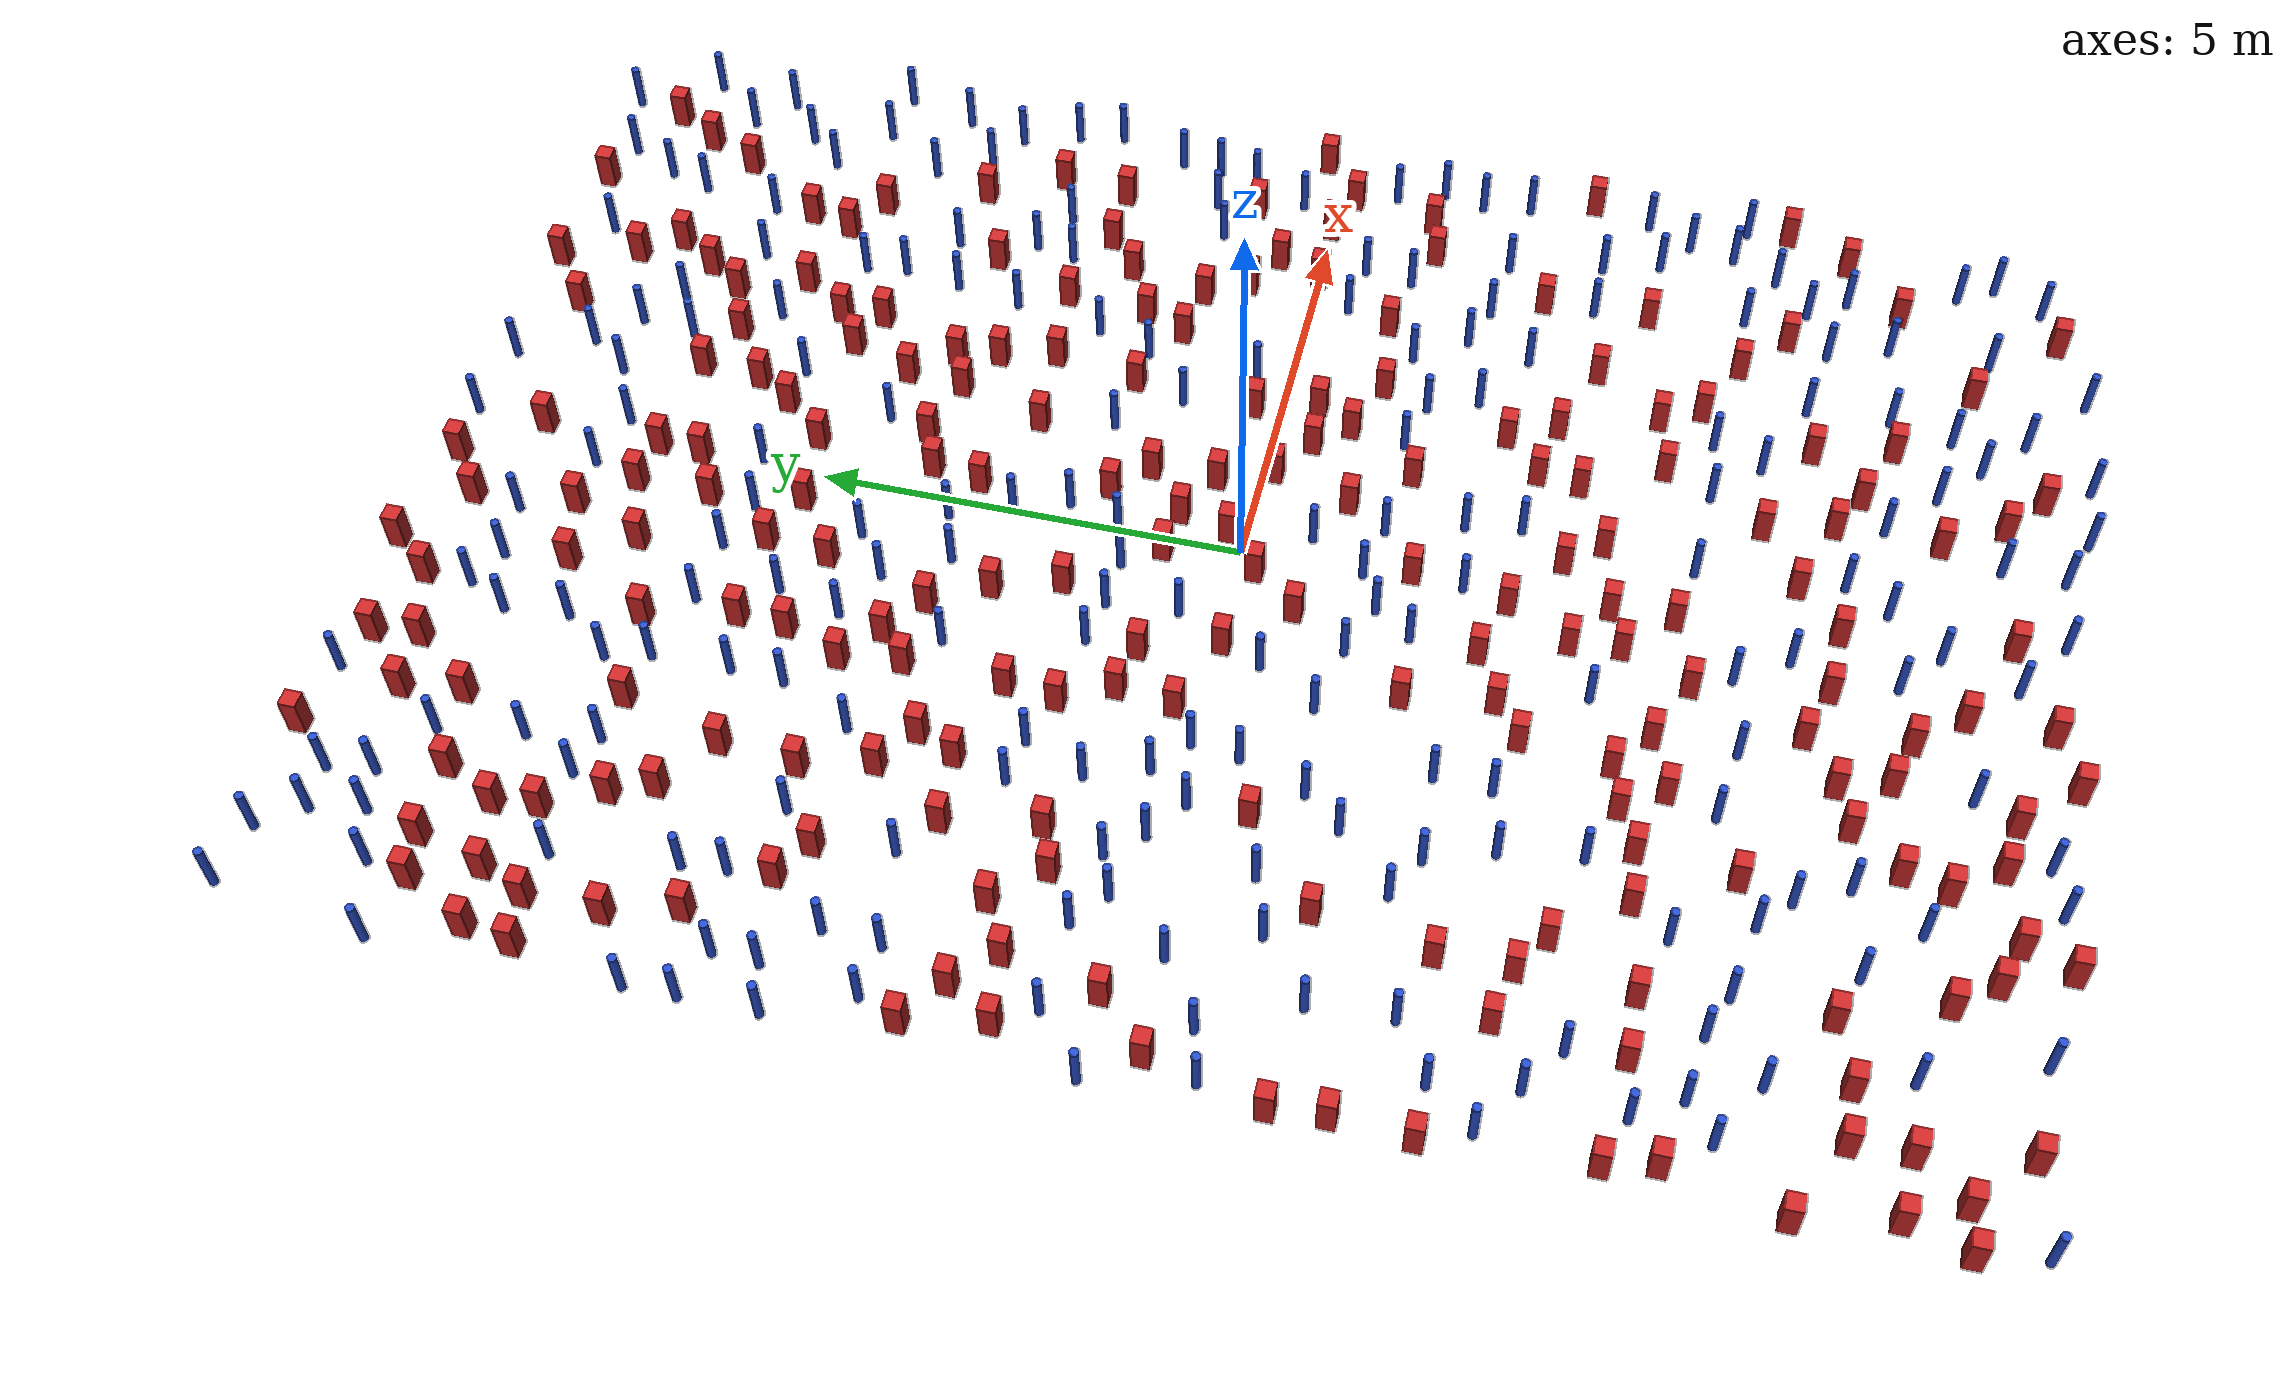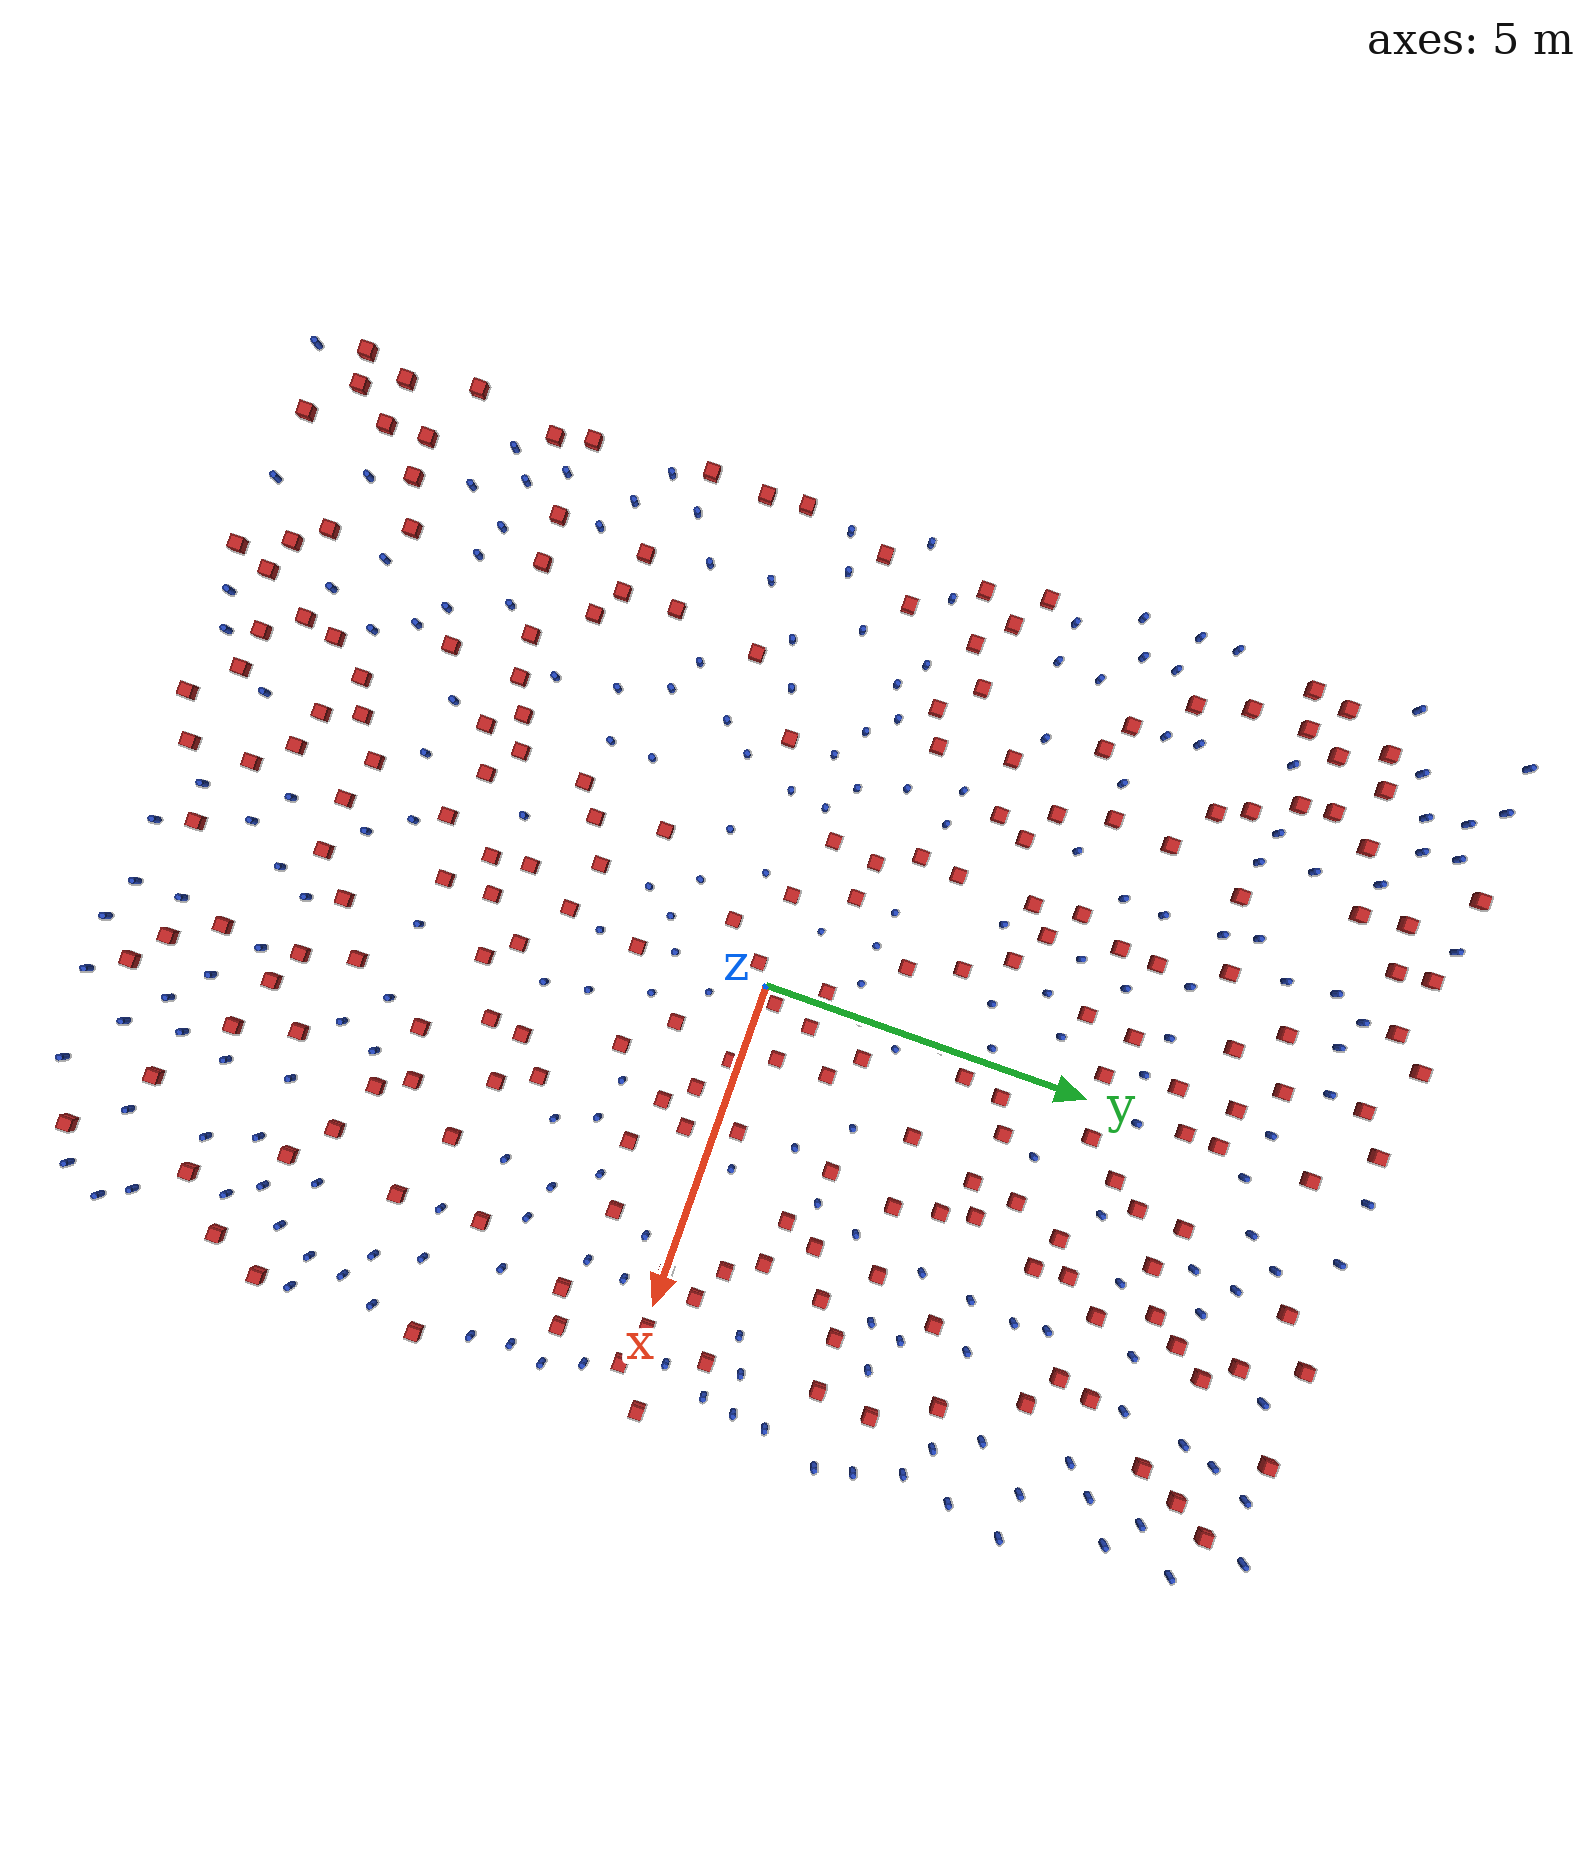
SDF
<sdf version="1.6">
  <model name="dense_38"><model name="square_post_obstacle0">
  <static>true</static>
  <pose frame="">5.15000023231 -1.34860133683 8.22691968438e-08 7.2212513382e-06 -7.54495500217e-07 2.29674213826e-05</pose>
  <link name="link">
    <pose frame="">0 0 0.25 0 -0 0</pose>
    <inertial>
      <mass>100</mass>
      <inertia>
        <ixx>0.166667</ixx>
        <ixy>0</ixy>
        <ixz>0</ixz>
        <iyy>0.166667</iyy>
        <iyz>0</iyz>
        <izz>0.166667</izz>
      </inertia>
    </inertial>
    <collision name="collision">
      <geometry>
        <box>
          <size>.2 .2 .5</size>
        </box>
      </geometry>
      <max_contacts>10</max_contacts>
      <surface>
        <contact>
          <ode/>
        </contact>
        <bounce/>
        <friction>
          <torsional>
            <ode/>
          </torsional>
          <ode/>
        </friction>
      </surface>
    </collision>
    <visual name="visual">
      <geometry>
        <box>
          <size>.2 .2 .5</size>
        </box>
      </geometry>
      <material>
        <script>
          <name>Gazebo/Red</name>
          <uri>file://media/materials/scripts/gazebo.material</uri>
        </script>
      </material>
    </visual>
    <self_collide>0</self_collide>
    <kinematic>0</kinematic>
  </link>
</model>
<model name="square_post_obstacle1">
  <static>true</static>
  <pose frame="">-0.453225772 -4.42769703456 8.22691968438e-08 7.22125133819e-06 -7.54495500217e-07 2.29674213826e-05</pose>
  <link name="link">
    <pose frame="">0 0 0.25 0 -0 0</pose>
    <inertial>
      <mass>100</mass>
      <inertia>
        <ixx>0.166667</ixx>
        <ixy>0</ixy>
        <ixz>0</ixz>
        <iyy>0.166667</iyy>
        <iyz>0</iyz>
        <izz>0.166667</izz>
      </inertia>
    </inertial>
    <collision name="collision">
      <geometry>
        <box>
          <size>.2 .2 .5</size>
        </box>
      </geometry>
      <max_contacts>10</max_contacts>
      <surface>
        <contact>
          <ode/>
        </contact>
        <bounce/>
        <friction>
          <torsional>
            <ode/>
          </torsional>
          <ode/>
        </friction>
      </surface>
    </collision>
    <visual name="visual">
      <geometry>
        <box>
          <size>.2 .2 .5</size>
        </box>
      </geometry>
      <material>
        <script>
          <name>Gazebo/Red</name>
          <uri>file://media/materials/scripts/gazebo.material</uri>
        </script>
      </material>
    </visual>
    <self_collide>0</self_collide>
    <kinematic>0</kinematic>
  </link>
</model>
<model name="pole_obstacle0">
  <static>true</static>
  <pose frame="">6.25939533136 -2.37629695557 2.88873142074e-08 -9.90536690245e-09 4.6021994898e-07 -1.20965994966e-07</pose>
  <link name="link">
  <pose frame="">0 0 0.3 0 -0 0</pose>
    <inertial>
      <mass>1</mass>
      <inertia>
        <ixx>0.145833</ixx>
        <ixy>0</ixy>
        <ixz>0</ixz>
        <iyy>0.145833</iyy>
        <iyz>0</iyz>
        <izz>0.125</izz>
      </inertia>
    </inertial>
    <collision name="collision">
      <geometry>
        <cylinder>
          <radius>0.05</radius>
          <length>.6</length>
        </cylinder>
      </geometry>
      <max_contacts>10</max_contacts>
      <surface>
        <contact>
          <ode/>
        </contact>
        <bounce/>
        <friction>
          <torsional>
            <ode/>
          </torsional>
          <ode/>
        </friction>
      </surface>
    </collision>
    <visual name="visual">
      <geometry>
        <cylinder>
          <radius>0.05</radius>
          <length>.6</length>
        </cylinder>
      </geometry>
      <material>
        <script>
          <name>Gazebo/Blue</name>
          <uri>file://media/materials/scripts/gazebo.material</uri>
        </script>
      </material>
    </visual>
    <self_collide>0</self_collide>
    <kinematic>0</kinematic>
  </link>
</model>
<model name="square_post_obstacle2">
  <static>true</static>
  <pose frame="">1.98796259758 8.79304583945 8.22691968438e-08 7.22125133819e-06 -7.54495500217e-07 2.29674213826e-05</pose>
  <link name="link">
    <pose frame="">0 0 0.25 0 -0 0</pose>
    <inertial>
      <mass>100</mass>
      <inertia>
        <ixx>0.166667</ixx>
        <ixy>0</ixy>
        <ixz>0</ixz>
        <iyy>0.166667</iyy>
        <iyz>0</iyz>
        <izz>0.166667</izz>
      </inertia>
    </inertial>
    <collision name="collision">
      <geometry>
        <box>
          <size>.2 .2 .5</size>
        </box>
      </geometry>
      <max_contacts>10</max_contacts>
      <surface>
        <contact>
          <ode/>
        </contact>
        <bounce/>
        <friction>
          <torsional>
            <ode/>
          </torsional>
          <ode/>
        </friction>
      </surface>
    </collision>
    <visual name="visual">
      <geometry>
        <box>
          <size>.2 .2 .5</size>
        </box>
      </geometry>
      <material>
        <script>
          <name>Gazebo/Red</name>
          <uri>file://media/materials/scripts/gazebo.material</uri>
        </script>
      </material>
    </visual>
    <self_collide>0</self_collide>
    <kinematic>0</kinematic>
  </link>
</model>
<model name="pole_obstacle1">
  <static>true</static>
  <pose frame="">4.55269154058 -6.26826545625 2.88873142074e-08 -9.90536690842e-09 4.60219948965e-07 -1.20965994976e-07</pose>
  <link name="link">
  <pose frame="">0 0 0.3 0 -0 0</pose>
    <inertial>
      <mass>1</mass>
      <inertia>
        <ixx>0.145833</ixx>
        <ixy>0</ixy>
        <ixz>0</ixz>
        <iyy>0.145833</iyy>
        <iyz>0</iyz>
        <izz>0.125</izz>
      </inertia>
    </inertial>
    <collision name="collision">
      <geometry>
        <cylinder>
          <radius>0.05</radius>
          <length>.6</length>
        </cylinder>
      </geometry>
      <max_contacts>10</max_contacts>
      <surface>
        <contact>
          <ode/>
        </contact>
        <bounce/>
        <friction>
          <torsional>
            <ode/>
          </torsional>
          <ode/>
        </friction>
      </surface>
    </collision>
    <visual name="visual">
      <geometry>
        <cylinder>
          <radius>0.05</radius>
          <length>.6</length>
        </cylinder>
      </geometry>
      <material>
        <script>
          <name>Gazebo/Blue</name>
          <uri>file://media/materials/scripts/gazebo.material</uri>
        </script>
      </material>
    </visual>
    <self_collide>0</self_collide>
    <kinematic>0</kinematic>
  </link>
</model>
<model name="square_post_obstacle3">
  <static>true</static>
  <pose frame="">4.07398690278 -5.25743221496 8.22691968438e-08 7.2212513382e-06 -7.54495500217e-07 2.29674213826e-05</pose>
  <link name="link">
    <pose frame="">0 0 0.25 0 -0 0</pose>
    <inertial>
      <mass>100</mass>
      <inertia>
        <ixx>0.166667</ixx>
        <ixy>0</ixy>
        <ixz>0</ixz>
        <iyy>0.166667</iyy>
        <iyz>0</iyz>
        <izz>0.166667</izz>
      </inertia>
    </inertial>
    <collision name="collision">
      <geometry>
        <box>
          <size>.2 .2 .5</size>
        </box>
      </geometry>
      <max_contacts>10</max_contacts>
      <surface>
        <contact>
          <ode/>
        </contact>
        <bounce/>
        <friction>
          <torsional>
            <ode/>
          </torsional>
          <ode/>
        </friction>
      </surface>
    </collision>
    <visual name="visual">
      <geometry>
        <box>
          <size>.2 .2 .5</size>
        </box>
      </geometry>
      <material>
        <script>
          <name>Gazebo/Red</name>
          <uri>file://media/materials/scripts/gazebo.material</uri>
        </script>
      </material>
    </visual>
    <self_collide>0</self_collide>
    <kinematic>0</kinematic>
  </link>
</model>
<model name="pole_obstacle2">
  <static>true</static>
  <pose frame="">-0.739905669948 4.30533973566 2.88873142074e-08 -9.90536689661e-09 4.60219948993e-07 -1.20965994957e-07</pose>
  <link name="link">
  <pose frame="">0 0 0.3 0 -0 0</pose>
    <inertial>
      <mass>1</mass>
      <inertia>
        <ixx>0.145833</ixx>
        <ixy>0</ixy>
        <ixz>0</ixz>
        <iyy>0.145833</iyy>
        <iyz>0</iyz>
        <izz>0.125</izz>
      </inertia>
    </inertial>
    <collision name="collision">
      <geometry>
        <cylinder>
          <radius>0.05</radius>
          <length>.6</length>
        </cylinder>
      </geometry>
      <max_contacts>10</max_contacts>
      <surface>
        <contact>
          <ode/>
        </contact>
        <bounce/>
        <friction>
          <torsional>
            <ode/>
          </torsional>
          <ode/>
        </friction>
      </surface>
    </collision>
    <visual name="visual">
      <geometry>
        <cylinder>
          <radius>0.05</radius>
          <length>.6</length>
        </cylinder>
      </geometry>
      <material>
        <script>
          <name>Gazebo/Blue</name>
          <uri>file://media/materials/scripts/gazebo.material</uri>
        </script>
      </material>
    </visual>
    <self_collide>0</self_collide>
    <kinematic>0</kinematic>
  </link>
</model>
<model name="pole_obstacle3">
  <static>true</static>
  <pose frame="">-4.32424077748 0.510078708993 2.88873142074e-08 -9.90536689326e-09 4.60219949001e-07 -1.20965994954e-07</pose>
  <link name="link">
  <pose frame="">0 0 0.3 0 -0 0</pose>
    <inertial>
      <mass>1</mass>
      <inertia>
        <ixx>0.145833</ixx>
        <ixy>0</ixy>
        <ixz>0</ixz>
        <iyy>0.145833</iyy>
        <iyz>0</iyz>
        <izz>0.125</izz>
      </inertia>
    </inertial>
    <collision name="collision">
      <geometry>
        <cylinder>
          <radius>0.05</radius>
          <length>.6</length>
        </cylinder>
      </geometry>
      <max_contacts>10</max_contacts>
      <surface>
        <contact>
          <ode/>
        </contact>
        <bounce/>
        <friction>
          <torsional>
            <ode/>
          </torsional>
          <ode/>
        </friction>
      </surface>
    </collision>
    <visual name="visual">
      <geometry>
        <cylinder>
          <radius>0.05</radius>
          <length>.6</length>
        </cylinder>
      </geometry>
      <material>
        <script>
          <name>Gazebo/Blue</name>
          <uri>file://media/materials/scripts/gazebo.material</uri>
        </script>
      </material>
    </visual>
    <self_collide>0</self_collide>
    <kinematic>0</kinematic>
  </link>
</model>
<model name="square_post_obstacle4">
  <static>true</static>
  <pose frame="">4.64315620051 0.532933999139 8.22691968438e-08 7.2212513382e-06 -7.54495500217e-07 2.29674213826e-05</pose>
  <link name="link">
    <pose frame="">0 0 0.25 0 -0 0</pose>
    <inertial>
      <mass>100</mass>
      <inertia>
        <ixx>0.166667</ixx>
        <ixy>0</ixy>
        <ixz>0</ixz>
        <iyy>0.166667</iyy>
        <iyz>0</iyz>
        <izz>0.166667</izz>
      </inertia>
    </inertial>
    <collision name="collision">
      <geometry>
        <box>
          <size>.2 .2 .5</size>
        </box>
      </geometry>
      <max_contacts>10</max_contacts>
      <surface>
        <contact>
          <ode/>
        </contact>
        <bounce/>
        <friction>
          <torsional>
            <ode/>
          </torsional>
          <ode/>
        </friction>
      </surface>
    </collision>
    <visual name="visual">
      <geometry>
        <box>
          <size>.2 .2 .5</size>
        </box>
      </geometry>
      <material>
        <script>
          <name>Gazebo/Red</name>
          <uri>file://media/materials/scripts/gazebo.material</uri>
        </script>
      </material>
    </visual>
    <self_collide>0</self_collide>
    <kinematic>0</kinematic>
  </link>
</model>
<model name="square_post_obstacle5">
  <static>true</static>
  <pose frame="">-6.77804085161 -2.3862629534 8.22691968438e-08 7.2212513382e-06 -7.54495500217e-07 2.29674213826e-05</pose>
  <link name="link">
    <pose frame="">0 0 0.25 0 -0 0</pose>
    <inertial>
      <mass>100</mass>
      <inertia>
        <ixx>0.166667</ixx>
        <ixy>0</ixy>
        <ixz>0</ixz>
        <iyy>0.166667</iyy>
        <iyz>0</iyz>
        <izz>0.166667</izz>
      </inertia>
    </inertial>
    <collision name="collision">
      <geometry>
        <box>
          <size>.2 .2 .5</size>
        </box>
      </geometry>
      <max_contacts>10</max_contacts>
      <surface>
        <contact>
          <ode/>
        </contact>
        <bounce/>
        <friction>
          <torsional>
            <ode/>
          </torsional>
          <ode/>
        </friction>
      </surface>
    </collision>
    <visual name="visual">
      <geometry>
        <box>
          <size>.2 .2 .5</size>
        </box>
      </geometry>
      <material>
        <script>
          <name>Gazebo/Red</name>
          <uri>file://media/materials/scripts/gazebo.material</uri>
        </script>
      </material>
    </visual>
    <self_collide>0</self_collide>
    <kinematic>0</kinematic>
  </link>
</model>
<model name="square_post_obstacle6">
  <static>true</static>
  <pose frame="">-6.53302153086 -0.464855870581 8.22691968438e-08 7.2212513382e-06 -7.54495500217e-07 2.29674213826e-05</pose>
  <link name="link">
    <pose frame="">0 0 0.25 0 -0 0</pose>
    <inertial>
      <mass>100</mass>
      <inertia>
        <ixx>0.166667</ixx>
        <ixy>0</ixy>
        <ixz>0</ixz>
        <iyy>0.166667</iyy>
        <iyz>0</iyz>
        <izz>0.166667</izz>
      </inertia>
    </inertial>
    <collision name="collision">
      <geometry>
        <box>
          <size>.2 .2 .5</size>
        </box>
      </geometry>
      <max_contacts>10</max_contacts>
      <surface>
        <contact>
          <ode/>
        </contact>
        <bounce/>
        <friction>
          <torsional>
            <ode/>
          </torsional>
          <ode/>
        </friction>
      </surface>
    </collision>
    <visual name="visual">
      <geometry>
        <box>
          <size>.2 .2 .5</size>
        </box>
      </geometry>
      <material>
        <script>
          <name>Gazebo/Red</name>
          <uri>file://media/materials/scripts/gazebo.material</uri>
        </script>
      </material>
    </visual>
    <self_collide>0</self_collide>
    <kinematic>0</kinematic>
  </link>
</model>
<model name="pole_obstacle4">
  <static>true</static>
  <pose frame="">3.19134797535 3.53822865445 2.88873142074e-08 -9.90536690232e-09 4.6021994898e-07 -1.20965994968e-07</pose>
  <link name="link">
  <pose frame="">0 0 0.3 0 -0 0</pose>
    <inertial>
      <mass>1</mass>
      <inertia>
        <ixx>0.145833</ixx>
        <ixy>0</ixy>
        <ixz>0</ixz>
        <iyy>0.145833</iyy>
        <iyz>0</iyz>
        <izz>0.125</izz>
      </inertia>
    </inertial>
    <collision name="collision">
      <geometry>
        <cylinder>
          <radius>0.05</radius>
          <length>.6</length>
        </cylinder>
      </geometry>
      <max_contacts>10</max_contacts>
      <surface>
        <contact>
          <ode/>
        </contact>
        <bounce/>
        <friction>
          <torsional>
            <ode/>
          </torsional>
          <ode/>
        </friction>
      </surface>
    </collision>
    <visual name="visual">
      <geometry>
        <cylinder>
          <radius>0.05</radius>
          <length>.6</length>
        </cylinder>
      </geometry>
      <material>
        <script>
          <name>Gazebo/Blue</name>
          <uri>file://media/materials/scripts/gazebo.material</uri>
        </script>
      </material>
    </visual>
    <self_collide>0</self_collide>
    <kinematic>0</kinematic>
  </link>
</model>
<model name="pole_obstacle5">
  <static>true</static>
  <pose frame="">-1.98658447247 -1.26352869154 2.88873142074e-08 -9.90536690043e-09 4.60219948984e-07 -1.20965994963e-07</pose>
  <link name="link">
  <pose frame="">0 0 0.3 0 -0 0</pose>
    <inertial>
      <mass>1</mass>
      <inertia>
        <ixx>0.145833</ixx>
        <ixy>0</ixy>
        <ixz>0</ixz>
        <iyy>0.145833</iyy>
        <iyz>0</iyz>
        <izz>0.125</izz>
      </inertia>
    </inertial>
    <collision name="collision">
      <geometry>
        <cylinder>
          <radius>0.05</radius>
          <length>.6</length>
        </cylinder>
      </geometry>
      <max_contacts>10</max_contacts>
      <surface>
        <contact>
          <ode/>
        </contact>
        <bounce/>
        <friction>
          <torsional>
            <ode/>
          </torsional>
          <ode/>
        </friction>
      </surface>
    </collision>
    <visual name="visual">
      <geometry>
        <cylinder>
          <radius>0.05</radius>
          <length>.6</length>
        </cylinder>
      </geometry>
      <material>
        <script>
          <name>Gazebo/Blue</name>
          <uri>file://media/materials/scripts/gazebo.material</uri>
        </script>
      </material>
    </visual>
    <self_collide>0</self_collide>
    <kinematic>0</kinematic>
  </link>
</model>
<model name="square_post_obstacle7">
  <static>true</static>
  <pose frame="">-2.24618304108 4.6984372265 8.22691968438e-08 7.2212513382e-06 -7.54495500217e-07 2.29674213826e-05</pose>
  <link name="link">
    <pose frame="">0 0 0.25 0 -0 0</pose>
    <inertial>
      <mass>100</mass>
      <inertia>
        <ixx>0.166667</ixx>
        <ixy>0</ixy>
        <ixz>0</ixz>
        <iyy>0.166667</iyy>
        <iyz>0</iyz>
        <izz>0.166667</izz>
      </inertia>
    </inertial>
    <collision name="collision">
      <geometry>
        <box>
          <size>.2 .2 .5</size>
        </box>
      </geometry>
      <max_contacts>10</max_contacts>
      <surface>
        <contact>
          <ode/>
        </contact>
        <bounce/>
        <friction>
          <torsional>
            <ode/>
          </torsional>
          <ode/>
        </friction>
      </surface>
    </collision>
    <visual name="visual">
      <geometry>
        <box>
          <size>.2 .2 .5</size>
        </box>
      </geometry>
      <material>
        <script>
          <name>Gazebo/Red</name>
          <uri>file://media/materials/scripts/gazebo.material</uri>
        </script>
      </material>
    </visual>
    <self_collide>0</self_collide>
    <kinematic>0</kinematic>
  </link>
</model>
<model name="square_post_obstacle8">
  <static>true</static>
  <pose frame="">-3.52622838958 -0.882869343843 8.22691968438e-08 7.2212513382e-06 -7.54495500217e-07 2.29674213826e-05</pose>
  <link name="link">
    <pose frame="">0 0 0.25 0 -0 0</pose>
    <inertial>
      <mass>100</mass>
      <inertia>
        <ixx>0.166667</ixx>
        <ixy>0</ixy>
        <ixz>0</ixz>
        <iyy>0.166667</iyy>
        <iyz>0</iyz>
        <izz>0.166667</izz>
      </inertia>
    </inertial>
    <collision name="collision">
      <geometry>
        <box>
          <size>.2 .2 .5</size>
        </box>
      </geometry>
      <max_contacts>10</max_contacts>
      <surface>
        <contact>
          <ode/>
        </contact>
        <bounce/>
        <friction>
          <torsional>
            <ode/>
          </torsional>
          <ode/>
        </friction>
      </surface>
    </collision>
    <visual name="visual">
      <geometry>
        <box>
          <size>.2 .2 .5</size>
        </box>
      </geometry>
      <material>
        <script>
          <name>Gazebo/Red</name>
          <uri>file://media/materials/scripts/gazebo.material</uri>
        </script>
      </material>
    </visual>
    <self_collide>0</self_collide>
    <kinematic>0</kinematic>
  </link>
</model>
<model name="pole_obstacle6">
  <static>true</static>
  <pose frame="">-0.401653053069 7.68126445907 2.88873142074e-08 -9.90536689683e-09 4.60219948993e-07 -1.20965994957e-07</pose>
  <link name="link">
  <pose frame="">0 0 0.3 0 -0 0</pose>
    <inertial>
      <mass>1</mass>
      <inertia>
        <ixx>0.145833</ixx>
        <ixy>0</ixy>
        <ixz>0</ixz>
        <iyy>0.145833</iyy>
        <iyz>0</iyz>
        <izz>0.125</izz>
      </inertia>
    </inertial>
    <collision name="collision">
      <geometry>
        <cylinder>
          <radius>0.05</radius>
          <length>.6</length>
        </cylinder>
      </geometry>
      <max_contacts>10</max_contacts>
      <surface>
        <contact>
          <ode/>
        </contact>
        <bounce/>
        <friction>
          <torsional>
            <ode/>
          </torsional>
          <ode/>
        </friction>
      </surface>
    </collision>
    <visual name="visual">
      <geometry>
        <cylinder>
          <radius>0.05</radius>
          <length>.6</length>
        </cylinder>
      </geometry>
      <material>
        <script>
          <name>Gazebo/Blue</name>
          <uri>file://media/materials/scripts/gazebo.material</uri>
        </script>
      </material>
    </visual>
    <self_collide>0</self_collide>
    <kinematic>0</kinematic>
  </link>
</model>
<model name="pole_obstacle7">
  <static>true</static>
  <pose frame="">-4.22980877584 -1.10824775417 2.88873142074e-08 -9.90536689445e-09 4.60219948999e-07 -1.20965994956e-07</pose>
  <link name="link">
  <pose frame="">0 0 0.3 0 -0 0</pose>
    <inertial>
      <mass>1</mass>
      <inertia>
        <ixx>0.145833</ixx>
        <ixy>0</ixy>
        <ixz>0</ixz>
        <iyy>0.145833</iyy>
        <iyz>0</iyz>
        <izz>0.125</izz>
      </inertia>
    </inertial>
    <collision name="collision">
      <geometry>
        <cylinder>
          <radius>0.05</radius>
          <length>.6</length>
        </cylinder>
      </geometry>
      <max_contacts>10</max_contacts>
      <surface>
        <contact>
          <ode/>
        </contact>
        <bounce/>
        <friction>
          <torsional>
            <ode/>
          </torsional>
          <ode/>
        </friction>
      </surface>
    </collision>
    <visual name="visual">
      <geometry>
        <cylinder>
          <radius>0.05</radius>
          <length>.6</length>
        </cylinder>
      </geometry>
      <material>
        <script>
          <name>Gazebo/Blue</name>
          <uri>file://media/materials/scripts/gazebo.material</uri>
        </script>
      </material>
    </visual>
    <self_collide>0</self_collide>
    <kinematic>0</kinematic>
  </link>
</model>
<model name="square_post_obstacle9">
  <static>true</static>
  <pose frame="">0.956388180386 -4.03698732437 8.22691968438e-08 7.22125133819e-06 -7.54495500217e-07 2.29674213826e-05</pose>
  <link name="link">
    <pose frame="">0 0 0.25 0 -0 0</pose>
    <inertial>
      <mass>100</mass>
      <inertia>
        <ixx>0.166667</ixx>
        <ixy>0</ixy>
        <ixz>0</ixz>
        <iyy>0.166667</iyy>
        <iyz>0</iyz>
        <izz>0.166667</izz>
      </inertia>
    </inertial>
    <collision name="collision">
      <geometry>
        <box>
          <size>.2 .2 .5</size>
        </box>
      </geometry>
      <max_contacts>10</max_contacts>
      <surface>
        <contact>
          <ode/>
        </contact>
        <bounce/>
        <friction>
          <torsional>
            <ode/>
          </torsional>
          <ode/>
        </friction>
      </surface>
    </collision>
    <visual name="visual">
      <geometry>
        <box>
          <size>.2 .2 .5</size>
        </box>
      </geometry>
      <material>
        <script>
          <name>Gazebo/Red</name>
          <uri>file://media/materials/scripts/gazebo.material</uri>
        </script>
      </material>
    </visual>
    <self_collide>0</self_collide>
    <kinematic>0</kinematic>
  </link>
</model>
<model name="square_post_obstacle10">
  <static>true</static>
  <pose frame="">6.10000262031 -6.38535614664 8.22691968438e-08 7.22125133819e-06 -7.54495500217e-07 2.29674213826e-05</pose>
  <link name="link">
    <pose frame="">0 0 0.25 0 -0 0</pose>
    <inertial>
      <mass>100</mass>
      <inertia>
        <ixx>0.166667</ixx>
        <ixy>0</ixy>
        <ixz>0</ixz>
        <iyy>0.166667</iyy>
        <iyz>0</iyz>
        <izz>0.166667</izz>
      </inertia>
    </inertial>
    <collision name="collision">
      <geometry>
        <box>
          <size>.2 .2 .5</size>
        </box>
      </geometry>
      <max_contacts>10</max_contacts>
      <surface>
        <contact>
          <ode/>
        </contact>
        <bounce/>
        <friction>
          <torsional>
            <ode/>
          </torsional>
          <ode/>
        </friction>
      </surface>
    </collision>
    <visual name="visual">
      <geometry>
        <box>
          <size>.2 .2 .5</size>
        </box>
      </geometry>
      <material>
        <script>
          <name>Gazebo/Red</name>
          <uri>file://media/materials/scripts/gazebo.material</uri>
        </script>
      </material>
    </visual>
    <self_collide>0</self_collide>
    <kinematic>0</kinematic>
  </link>
</model>
<model name="square_post_obstacle11">
  <static>true</static>
  <pose frame="">0.0836850320657 -4.95521037136 8.22691968438e-08 7.2212513382e-06 -7.54495500217e-07 2.29674213826e-05</pose>
  <link name="link">
    <pose frame="">0 0 0.25 0 -0 0</pose>
    <inertial>
      <mass>100</mass>
      <inertia>
        <ixx>0.166667</ixx>
        <ixy>0</ixy>
        <ixz>0</ixz>
        <iyy>0.166667</iyy>
        <iyz>0</iyz>
        <izz>0.166667</izz>
      </inertia>
    </inertial>
    <collision name="collision">
      <geometry>
        <box>
          <size>.2 .2 .5</size>
        </box>
      </geometry>
      <max_contacts>10</max_contacts>
      <surface>
        <contact>
          <ode/>
        </contact>
        <bounce/>
        <friction>
          <torsional>
            <ode/>
          </torsional>
          <ode/>
        </friction>
      </surface>
    </collision>
    <visual name="visual">
      <geometry>
        <box>
          <size>.2 .2 .5</size>
        </box>
      </geometry>
      <material>
        <script>
          <name>Gazebo/Red</name>
          <uri>file://media/materials/scripts/gazebo.material</uri>
        </script>
      </material>
    </visual>
    <self_collide>0</self_collide>
    <kinematic>0</kinematic>
  </link>
</model>
<model name="square_post_obstacle12">
  <static>true</static>
  <pose frame="">4.12839357007 0.815747877024 8.22691968438e-08 7.2212513382e-06 -7.54495500217e-07 2.29674213826e-05</pose>
  <link name="link">
    <pose frame="">0 0 0.25 0 -0 0</pose>
    <inertial>
      <mass>100</mass>
      <inertia>
        <ixx>0.166667</ixx>
        <ixy>0</ixy>
        <ixz>0</ixz>
        <iyy>0.166667</iyy>
        <iyz>0</iyz>
        <izz>0.166667</izz>
      </inertia>
    </inertial>
    <collision name="collision">
      <geometry>
        <box>
          <size>.2 .2 .5</size>
        </box>
      </geometry>
      <max_contacts>10</max_contacts>
      <surface>
        <contact>
          <ode/>
        </contact>
        <bounce/>
        <friction>
          <torsional>
            <ode/>
          </torsional>
          <ode/>
        </friction>
      </surface>
    </collision>
    <visual name="visual">
      <geometry>
        <box>
          <size>.2 .2 .5</size>
        </box>
      </geometry>
      <material>
        <script>
          <name>Gazebo/Red</name>
          <uri>file://media/materials/scripts/gazebo.material</uri>
        </script>
      </material>
    </visual>
    <self_collide>0</self_collide>
    <kinematic>0</kinematic>
  </link>
</model>
<model name="square_post_obstacle13">
  <static>true</static>
  <pose frame="">5.29659677529 -8.98105700362 8.22691968438e-08 7.22125133819e-06 -7.54495500217e-07 2.29674213826e-05</pose>
  <link name="link">
    <pose frame="">0 0 0.25 0 -0 0</pose>
    <inertial>
      <mass>100</mass>
      <inertia>
        <ixx>0.166667</ixx>
        <ixy>0</ixy>
        <ixz>0</ixz>
        <iyy>0.166667</iyy>
        <iyz>0</iyz>
        <izz>0.166667</izz>
      </inertia>
    </inertial>
    <collision name="collision">
      <geometry>
        <box>
          <size>.2 .2 .5</size>
        </box>
      </geometry>
      <max_contacts>10</max_contacts>
      <surface>
        <contact>
          <ode/>
        </contact>
        <bounce/>
        <friction>
          <torsional>
            <ode/>
          </torsional>
          <ode/>
        </friction>
      </surface>
    </collision>
    <visual name="visual">
      <geometry>
        <box>
          <size>.2 .2 .5</size>
        </box>
      </geometry>
      <material>
        <script>
          <name>Gazebo/Red</name>
          <uri>file://media/materials/scripts/gazebo.material</uri>
        </script>
      </material>
    </visual>
    <self_collide>0</self_collide>
    <kinematic>0</kinematic>
  </link>
</model>
<model name="pole_obstacle8">
  <static>true</static>
  <pose frame="">5.4938373227 -6.43313451027 2.88873142074e-08 -9.90536690842e-09 4.60219948965e-07 -1.20965994976e-07</pose>
  <link name="link">
  <pose frame="">0 0 0.3 0 -0 0</pose>
    <inertial>
      <mass>1</mass>
      <inertia>
        <ixx>0.145833</ixx>
        <ixy>0</ixy>
        <ixz>0</ixz>
        <iyy>0.145833</iyy>
        <iyz>0</iyz>
        <izz>0.125</izz>
      </inertia>
    </inertial>
    <collision name="collision">
      <geometry>
        <cylinder>
          <radius>0.05</radius>
          <length>.6</length>
        </cylinder>
      </geometry>
      <max_contacts>10</max_contacts>
      <surface>
        <contact>
          <ode/>
        </contact>
        <bounce/>
        <friction>
          <torsional>
            <ode/>
          </torsional>
          <ode/>
        </friction>
      </surface>
    </collision>
    <visual name="visual">
      <geometry>
        <cylinder>
          <radius>0.05</radius>
          <length>.6</length>
        </cylinder>
      </geometry>
      <material>
        <script>
          <name>Gazebo/Blue</name>
          <uri>file://media/materials/scripts/gazebo.material</uri>
        </script>
      </material>
    </visual>
    <self_collide>0</self_collide>
    <kinematic>0</kinematic>
  </link>
</model>
<model name="square_post_obstacle14">
  <static>true</static>
  <pose frame="">-5.36833786848 3.77041327687 8.22691968438e-08 7.2212513382e-06 -7.54495500217e-07 2.29674213826e-05</pose>
  <link name="link">
    <pose frame="">0 0 0.25 0 -0 0</pose>
    <inertial>
      <mass>100</mass>
      <inertia>
        <ixx>0.166667</ixx>
        <ixy>0</ixy>
        <ixz>0</ixz>
        <iyy>0.166667</iyy>
        <iyz>0</iyz>
        <izz>0.166667</izz>
      </inertia>
    </inertial>
    <collision name="collision">
      <geometry>
        <box>
          <size>.2 .2 .5</size>
        </box>
      </geometry>
      <max_contacts>10</max_contacts>
      <surface>
        <contact>
          <ode/>
        </contact>
        <bounce/>
        <friction>
          <torsional>
            <ode/>
          </torsional>
          <ode/>
        </friction>
      </surface>
    </collision>
    <visual name="visual">
      <geometry>
        <box>
          <size>.2 .2 .5</size>
        </box>
      </geometry>
      <material>
        <script>
          <name>Gazebo/Red</name>
          <uri>file://media/materials/scripts/gazebo.material</uri>
        </script>
      </material>
    </visual>
    <self_collide>0</self_collide>
    <kinematic>0</kinematic>
  </link>
</model>
<model name="square_post_obstacle15">
  <static>true</static>
  <pose frame="">-2.44196828047 -8.70239548351 8.22691968438e-08 7.22125133819e-06 -7.54495500217e-07 2.29674213826e-05</pose>
  <link name="link">
    <pose frame="">0 0 0.25 0 -0 0</pose>
    <inertial>
      <mass>100</mass>
      <inertia>
        <ixx>0.166667</ixx>
        <ixy>0</ixy>
        <ixz>0</ixz>
        <iyy>0.166667</iyy>
        <iyz>0</iyz>
        <izz>0.166667</izz>
      </inertia>
    </inertial>
    <collision name="collision">
      <geometry>
        <box>
          <size>.2 .2 .5</size>
        </box>
      </geometry>
      <max_contacts>10</max_contacts>
      <surface>
        <contact>
          <ode/>
        </contact>
        <bounce/>
        <friction>
          <torsional>
            <ode/>
          </torsional>
          <ode/>
        </friction>
      </surface>
    </collision>
    <visual name="visual">
      <geometry>
        <box>
          <size>.2 .2 .5</size>
        </box>
      </geometry>
      <material>
        <script>
          <name>Gazebo/Red</name>
          <uri>file://media/materials/scripts/gazebo.material</uri>
        </script>
      </material>
    </visual>
    <self_collide>0</self_collide>
    <kinematic>0</kinematic>
  </link>
</model>
<model name="square_post_obstacle16">
  <static>true</static>
  <pose frame="">2.9685054038 8.38365532075 8.22691968438e-08 7.22125133819e-06 -7.54495500217e-07 2.29674213826e-05</pose>
  <link name="link">
    <pose frame="">0 0 0.25 0 -0 0</pose>
    <inertial>
      <mass>100</mass>
      <inertia>
        <ixx>0.166667</ixx>
        <ixy>0</ixy>
        <ixz>0</ixz>
        <iyy>0.166667</iyy>
        <iyz>0</iyz>
        <izz>0.166667</izz>
      </inertia>
    </inertial>
    <collision name="collision">
      <geometry>
        <box>
          <size>.2 .2 .5</size>
        </box>
      </geometry>
      <max_contacts>10</max_contacts>
      <surface>
        <contact>
          <ode/>
        </contact>
        <bounce/>
        <friction>
          <torsional>
            <ode/>
          </torsional>
          <ode/>
        </friction>
      </surface>
    </collision>
    <visual name="visual">
      <geometry>
        <box>
          <size>.2 .2 .5</size>
        </box>
      </geometry>
      <material>
        <script>
          <name>Gazebo/Red</name>
          <uri>file://media/materials/scripts/gazebo.material</uri>
        </script>
      </material>
    </visual>
    <self_collide>0</self_collide>
    <kinematic>0</kinematic>
  </link>
</model>
<model name="pole_obstacle9">
  <static>true</static>
  <pose frame="">-6.37685946599 3.59660607227 2.88873142074e-08 -9.90536690245e-09 4.6021994898e-07 -1.20965994966e-07</pose>
  <link name="link">
  <pose frame="">0 0 0.3 0 -0 0</pose>
    <inertial>
      <mass>1</mass>
      <inertia>
        <ixx>0.145833</ixx>
        <ixy>0</ixy>
        <ixz>0</ixz>
        <iyy>0.145833</iyy>
        <iyz>0</iyz>
        <izz>0.125</izz>
      </inertia>
    </inertial>
    <collision name="collision">
      <geometry>
        <cylinder>
          <radius>0.05</radius>
          <length>.6</length>
        </cylinder>
      </geometry>
      <max_contacts>10</max_contacts>
      <surface>
        <contact>
          <ode/>
        </contact>
        <bounce/>
        <friction>
          <torsional>
            <ode/>
          </torsional>
          <ode/>
        </friction>
      </surface>
    </collision>
    <visual name="visual">
      <geometry>
        <cylinder>
          <radius>0.05</radius>
          <length>.6</length>
        </cylinder>
      </geometry>
      <material>
        <script>
          <name>Gazebo/Blue</name>
          <uri>file://media/materials/scripts/gazebo.material</uri>
        </script>
      </material>
    </visual>
    <self_collide>0</self_collide>
    <kinematic>0</kinematic>
  </link>
</model>
<model name="square_post_obstacle17">
  <static>true</static>
  <pose frame="">4.66868153729 -4.08071297045 8.22691968438e-08 7.2212513382e-06 -7.54495500217e-07 2.29674213826e-05</pose>
  <link name="link">
    <pose frame="">0 0 0.25 0 -0 0</pose>
    <inertial>
      <mass>100</mass>
      <inertia>
        <ixx>0.166667</ixx>
        <ixy>0</ixy>
        <ixz>0</ixz>
        <iyy>0.166667</iyy>
        <iyz>0</iyz>
        <izz>0.166667</izz>
      </inertia>
    </inertial>
    <collision name="collision">
      <geometry>
        <box>
          <size>.2 .2 .5</size>
        </box>
      </geometry>
      <max_contacts>10</max_contacts>
      <surface>
        <contact>
          <ode/>
        </contact>
        <bounce/>
        <friction>
          <torsional>
            <ode/>
          </torsional>
          <ode/>
        </friction>
      </surface>
    </collision>
    <visual name="visual">
      <geometry>
        <box>
          <size>.2 .2 .5</size>
        </box>
      </geometry>
      <material>
        <script>
          <name>Gazebo/Red</name>
          <uri>file://media/materials/scripts/gazebo.material</uri>
        </script>
      </material>
    </visual>
    <self_collide>0</self_collide>
    <kinematic>0</kinematic>
  </link>
</model>
<model name="square_post_obstacle18">
  <static>true</static>
  <pose frame="">-3.78768500839 3.16812446144 8.22691968438e-08 7.2212513382e-06 -7.54495500217e-07 2.29674213826e-05</pose>
  <link name="link">
    <pose frame="">0 0 0.25 0 -0 0</pose>
    <inertial>
      <mass>100</mass>
      <inertia>
        <ixx>0.166667</ixx>
        <ixy>0</ixy>
        <ixz>0</ixz>
        <iyy>0.166667</iyy>
        <iyz>0</iyz>
        <izz>0.166667</izz>
      </inertia>
    </inertial>
    <collision name="collision">
      <geometry>
        <box>
          <size>.2 .2 .5</size>
        </box>
      </geometry>
      <max_contacts>10</max_contacts>
      <surface>
        <contact>
          <ode/>
        </contact>
        <bounce/>
        <friction>
          <torsional>
            <ode/>
          </torsional>
          <ode/>
        </friction>
      </surface>
    </collision>
    <visual name="visual">
      <geometry>
        <box>
          <size>.2 .2 .5</size>
        </box>
      </geometry>
      <material>
        <script>
          <name>Gazebo/Red</name>
          <uri>file://media/materials/scripts/gazebo.material</uri>
        </script>
      </material>
    </visual>
    <self_collide>0</self_collide>
    <kinematic>0</kinematic>
  </link>
</model>
<model name="pole_obstacle10">
  <static>true</static>
  <pose frame="">5.6658567567 -5.5417444176 2.88873142074e-08 -9.90536690842e-09 4.60219948965e-07 -1.20965994976e-07</pose>
  <link name="link">
  <pose frame="">0 0 0.3 0 -0 0</pose>
    <inertial>
      <mass>1</mass>
      <inertia>
        <ixx>0.145833</ixx>
        <ixy>0</ixy>
        <ixz>0</ixz>
        <iyy>0.145833</iyy>
        <iyz>0</iyz>
        <izz>0.125</izz>
      </inertia>
    </inertial>
    <collision name="collision">
      <geometry>
        <cylinder>
          <radius>0.05</radius>
          <length>.6</length>
        </cylinder>
      </geometry>
      <max_contacts>10</max_contacts>
      <surface>
        <contact>
          <ode/>
        </contact>
        <bounce/>
        <friction>
          <torsional>
            <ode/>
          </torsional>
          <ode/>
        </friction>
      </surface>
    </collision>
    <visual name="visual">
      <geometry>
        <cylinder>
          <radius>0.05</radius>
          <length>.6</length>
        </cylinder>
      </geometry>
      <material>
        <script>
          <name>Gazebo/Blue</name>
          <uri>file://media/materials/scripts/gazebo.material</uri>
        </script>
      </material>
    </visual>
    <self_collide>0</self_collide>
    <kinematic>0</kinematic>
  </link>
</model>
<model name="square_post_obstacle19">
  <static>true</static>
  <pose frame="">-5.95324830502 0.11455333152 8.22691968438e-08 7.2212513382e-06 -7.54495500217e-07 2.29674213826e-05</pose>
  <link name="link">
    <pose frame="">0 0 0.25 0 -0 0</pose>
    <inertial>
      <mass>100</mass>
      <inertia>
        <ixx>0.166667</ixx>
        <ixy>0</ixy>
        <ixz>0</ixz>
        <iyy>0.166667</iyy>
        <iyz>0</iyz>
        <izz>0.166667</izz>
      </inertia>
    </inertial>
    <collision name="collision">
      <geometry>
        <box>
          <size>.2 .2 .5</size>
        </box>
      </geometry>
      <max_contacts>10</max_contacts>
      <surface>
        <contact>
          <ode/>
        </contact>
        <bounce/>
        <friction>
          <torsional>
            <ode/>
          </torsional>
          <ode/>
        </friction>
      </surface>
    </collision>
    <visual name="visual">
      <geometry>
        <box>
          <size>.2 .2 .5</size>
        </box>
      </geometry>
      <material>
        <script>
          <name>Gazebo/Red</name>
          <uri>file://media/materials/scripts/gazebo.material</uri>
        </script>
      </material>
    </visual>
    <self_collide>0</self_collide>
    <kinematic>0</kinematic>
  </link>
</model>
<model name="pole_obstacle11">
  <static>true</static>
  <pose frame="">-6.60695953444 -3.79870451077 2.88873142074e-08 -9.90536690245e-09 4.6021994898e-07 -1.20965994966e-07</pose>
  <link name="link">
  <pose frame="">0 0 0.3 0 -0 0</pose>
    <inertial>
      <mass>1</mass>
      <inertia>
        <ixx>0.145833</ixx>
        <ixy>0</ixy>
        <ixz>0</ixz>
        <iyy>0.145833</iyy>
        <iyz>0</iyz>
        <izz>0.125</izz>
      </inertia>
    </inertial>
    <collision name="collision">
      <geometry>
        <cylinder>
          <radius>0.05</radius>
          <length>.6</length>
        </cylinder>
      </geometry>
      <max_contacts>10</max_contacts>
      <surface>
        <contact>
          <ode/>
        </contact>
        <bounce/>
        <friction>
          <torsional>
            <ode/>
          </torsional>
          <ode/>
        </friction>
      </surface>
    </collision>
    <visual name="visual">
      <geometry>
        <cylinder>
          <radius>0.05</radius>
          <length>.6</length>
        </cylinder>
      </geometry>
      <material>
        <script>
          <name>Gazebo/Blue</name>
          <uri>file://media/materials/scripts/gazebo.material</uri>
        </script>
      </material>
    </visual>
    <self_collide>0</self_collide>
    <kinematic>0</kinematic>
  </link>
</model>
<model name="square_post_obstacle20">
  <static>true</static>
  <pose frame="">2.62762132053 -3.26762497386 8.22691968438e-08 7.2212513382e-06 -7.54495500217e-07 2.29674213826e-05</pose>
  <link name="link">
    <pose frame="">0 0 0.25 0 -0 0</pose>
    <inertial>
      <mass>100</mass>
      <inertia>
        <ixx>0.166667</ixx>
        <ixy>0</ixy>
        <ixz>0</ixz>
        <iyy>0.166667</iyy>
        <iyz>0</iyz>
        <izz>0.166667</izz>
      </inertia>
    </inertial>
    <collision name="collision">
      <geometry>
        <box>
          <size>.2 .2 .5</size>
        </box>
      </geometry>
      <max_contacts>10</max_contacts>
      <surface>
        <contact>
          <ode/>
        </contact>
        <bounce/>
        <friction>
          <torsional>
            <ode/>
          </torsional>
          <ode/>
        </friction>
      </surface>
    </collision>
    <visual name="visual">
      <geometry>
        <box>
          <size>.2 .2 .5</size>
        </box>
      </geometry>
      <material>
        <script>
          <name>Gazebo/Red</name>
          <uri>file://media/materials/scripts/gazebo.material</uri>
        </script>
      </material>
    </visual>
    <self_collide>0</self_collide>
    <kinematic>0</kinematic>
  </link>
</model>
<model name="pole_obstacle12">
  <static>true</static>
  <pose frame="">5.22611355301 5.19054820022 2.88873142074e-08 -9.90536690842e-09 4.60219948965e-07 -1.20965994976e-07</pose>
  <link name="link">
  <pose frame="">0 0 0.3 0 -0 0</pose>
    <inertial>
      <mass>1</mass>
      <inertia>
        <ixx>0.145833</ixx>
        <ixy>0</ixy>
        <ixz>0</ixz>
        <iyy>0.145833</iyy>
        <iyz>0</iyz>
        <izz>0.125</izz>
      </inertia>
    </inertial>
    <collision name="collision">
      <geometry>
        <cylinder>
          <radius>0.05</radius>
          <length>.6</length>
        </cylinder>
      </geometry>
      <max_contacts>10</max_contacts>
      <surface>
        <contact>
          <ode/>
        </contact>
        <bounce/>
        <friction>
          <torsional>
            <ode/>
          </torsional>
          <ode/>
        </friction>
      </surface>
    </collision>
    <visual name="visual">
      <geometry>
        <cylinder>
          <radius>0.05</radius>
          <length>.6</length>
        </cylinder>
      </geometry>
      <material>
        <script>
          <name>Gazebo/Blue</name>
          <uri>file://media/materials/scripts/gazebo.material</uri>
        </script>
      </material>
    </visual>
    <self_collide>0</self_collide>
    <kinematic>0</kinematic>
  </link>
</model>
<model name="square_post_obstacle21">
  <static>true</static>
  <pose frame="">0.0648391307138 -4.22650328789 8.22691968438e-08 7.22125133819e-06 -7.54495500217e-07 2.29674213826e-05</pose>
  <link name="link">
    <pose frame="">0 0 0.25 0 -0 0</pose>
    <inertial>
      <mass>100</mass>
      <inertia>
        <ixx>0.166667</ixx>
        <ixy>0</ixy>
        <ixz>0</ixz>
        <iyy>0.166667</iyy>
        <iyz>0</iyz>
        <izz>0.166667</izz>
      </inertia>
    </inertial>
    <collision name="collision">
      <geometry>
        <box>
          <size>.2 .2 .5</size>
        </box>
      </geometry>
      <max_contacts>10</max_contacts>
      <surface>
        <contact>
          <ode/>
        </contact>
        <bounce/>
        <friction>
          <torsional>
            <ode/>
          </torsional>
          <ode/>
        </friction>
      </surface>
    </collision>
    <visual name="visual">
      <geometry>
        <box>
          <size>.2 .2 .5</size>
        </box>
      </geometry>
      <material>
        <script>
          <name>Gazebo/Red</name>
          <uri>file://media/materials/scripts/gazebo.material</uri>
        </script>
      </material>
    </visual>
    <self_collide>0</self_collide>
    <kinematic>0</kinematic>
  </link>
</model>
<model name="pole_obstacle13">
  <static>true</static>
  <pose frame="">-3.47232369091 -1.83874024077 2.88873142074e-08 -9.90536691123e-09 4.60219948959e-07 -1.20965994982e-07</pose>
  <link name="link">
  <pose frame="">0 0 0.3 0 -0 0</pose>
    <inertial>
      <mass>1</mass>
      <inertia>
        <ixx>0.145833</ixx>
        <ixy>0</ixy>
        <ixz>0</ixz>
        <iyy>0.145833</iyy>
        <iyz>0</iyz>
        <izz>0.125</izz>
      </inertia>
    </inertial>
    <collision name="collision">
      <geometry>
        <cylinder>
          <radius>0.05</radius>
          <length>.6</length>
        </cylinder>
      </geometry>
      <max_contacts>10</max_contacts>
      <surface>
        <contact>
          <ode/>
        </contact>
        <bounce/>
        <friction>
          <torsional>
            <ode/>
          </torsional>
          <ode/>
        </friction>
      </surface>
    </collision>
    <visual name="visual">
      <geometry>
        <cylinder>
          <radius>0.05</radius>
          <length>.6</length>
        </cylinder>
      </geometry>
      <material>
        <script>
          <name>Gazebo/Blue</name>
          <uri>file://media/materials/scripts/gazebo.material</uri>
        </script>
      </material>
    </visual>
    <self_collide>0</self_collide>
    <kinematic>0</kinematic>
  </link>
</model>
<model name="square_post_obstacle22">
  <static>true</static>
  <pose frame="">0.930814888783 -1.07541116986 8.22691968438e-08 7.2212513382e-06 -7.54495500217e-07 2.29674213826e-05</pose>
  <link name="link">
    <pose frame="">0 0 0.25 0 -0 0</pose>
    <inertial>
      <mass>100</mass>
      <inertia>
        <ixx>0.166667</ixx>
        <ixy>0</ixy>
        <ixz>0</ixz>
        <iyy>0.166667</iyy>
        <iyz>0</iyz>
        <izz>0.166667</izz>
      </inertia>
    </inertial>
    <collision name="collision">
      <geometry>
        <box>
          <size>.2 .2 .5</size>
        </box>
      </geometry>
      <max_contacts>10</max_contacts>
      <surface>
        <contact>
          <ode/>
        </contact>
        <bounce/>
        <friction>
          <torsional>
            <ode/>
          </torsional>
          <ode/>
        </friction>
      </surface>
    </collision>
    <visual name="visual">
      <geometry>
        <box>
          <size>.2 .2 .5</size>
        </box>
      </geometry>
      <material>
        <script>
          <name>Gazebo/Red</name>
          <uri>file://media/materials/scripts/gazebo.material</uri>
        </script>
      </material>
    </visual>
    <self_collide>0</self_collide>
    <kinematic>0</kinematic>
  </link>
</model>
<model name="pole_obstacle14">
  <static>true</static>
  <pose frame="">4.80722969112 -8.19572813081 2.88873142074e-08 -9.9053668967e-09 4.60219948993e-07 -1.20965994957e-07</pose>
  <link name="link">
  <pose frame="">0 0 0.3 0 -0 0</pose>
    <inertial>
      <mass>1</mass>
      <inertia>
        <ixx>0.145833</ixx>
        <ixy>0</ixy>
        <ixz>0</ixz>
        <iyy>0.145833</iyy>
        <iyz>0</iyz>
        <izz>0.125</izz>
      </inertia>
    </inertial>
    <collision name="collision">
      <geometry>
        <cylinder>
          <radius>0.05</radius>
          <length>.6</length>
        </cylinder>
      </geometry>
      <max_contacts>10</max_contacts>
      <surface>
        <contact>
          <ode/>
        </contact>
        <bounce/>
        <friction>
          <torsional>
            <ode/>
          </torsional>
          <ode/>
        </friction>
      </surface>
    </collision>
    <visual name="visual">
      <geometry>
        <cylinder>
          <radius>0.05</radius>
          <length>.6</length>
        </cylinder>
      </geometry>
      <material>
        <script>
          <name>Gazebo/Blue</name>
          <uri>file://media/materials/scripts/gazebo.material</uri>
        </script>
      </material>
    </visual>
    <self_collide>0</self_collide>
    <kinematic>0</kinematic>
  </link>
</model>
<model name="pole_obstacle15">
  <static>true</static>
  <pose frame="">-3.65093043293 1.76417876774 2.88873142074e-08 -9.90536689395e-09 4.60219949e-07 -1.20965994953e-07</pose>
  <link name="link">
  <pose frame="">0 0 0.3 0 -0 0</pose>
    <inertial>
      <mass>1</mass>
      <inertia>
        <ixx>0.145833</ixx>
        <ixy>0</ixy>
        <ixz>0</ixz>
        <iyy>0.145833</iyy>
        <iyz>0</iyz>
        <izz>0.125</izz>
      </inertia>
    </inertial>
    <collision name="collision">
      <geometry>
        <cylinder>
          <radius>0.05</radius>
          <length>.6</length>
        </cylinder>
      </geometry>
      <max_contacts>10</max_contacts>
      <surface>
        <contact>
          <ode/>
        </contact>
        <bounce/>
        <friction>
          <torsional>
            <ode/>
          </torsional>
          <ode/>
        </friction>
      </surface>
    </collision>
    <visual name="visual">
      <geometry>
        <cylinder>
          <radius>0.05</radius>
          <length>.6</length>
        </cylinder>
      </geometry>
      <material>
        <script>
          <name>Gazebo/Blue</name>
          <uri>file://media/materials/scripts/gazebo.material</uri>
        </script>
      </material>
    </visual>
    <self_collide>0</self_collide>
    <kinematic>0</kinematic>
  </link>
</model>
<model name="pole_obstacle16">
  <static>true</static>
  <pose frame="">-0.0267076855283 -1.42289226915 2.88873142074e-08 -9.90536690152e-09 4.60219948982e-07 -1.20965994964e-07</pose>
  <link name="link">
  <pose frame="">0 0 0.3 0 -0 0</pose>
    <inertial>
      <mass>1</mass>
      <inertia>
        <ixx>0.145833</ixx>
        <ixy>0</ixy>
        <ixz>0</ixz>
        <iyy>0.145833</iyy>
        <iyz>0</iyz>
        <izz>0.125</izz>
      </inertia>
    </inertial>
    <collision name="collision">
      <geometry>
        <cylinder>
          <radius>0.05</radius>
          <length>.6</length>
        </cylinder>
      </geometry>
      <max_contacts>10</max_contacts>
      <surface>
        <contact>
          <ode/>
        </contact>
        <bounce/>
        <friction>
          <torsional>
            <ode/>
          </torsional>
          <ode/>
        </friction>
      </surface>
    </collision>
    <visual name="visual">
      <geometry>
        <cylinder>
          <radius>0.05</radius>
          <length>.6</length>
        </cylinder>
      </geometry>
      <material>
        <script>
          <name>Gazebo/Blue</name>
          <uri>file://media/materials/scripts/gazebo.material</uri>
        </script>
      </material>
    </visual>
    <self_collide>0</self_collide>
    <kinematic>0</kinematic>
  </link>
</model>
<model name="square_post_obstacle23">
  <static>true</static>
  <pose frame="">-2.53691966221 1.50098403107 8.22691968438e-08 7.2212513382e-06 -7.54495500217e-07 2.29674213826e-05</pose>
  <link name="link">
    <pose frame="">0 0 0.25 0 -0 0</pose>
    <inertial>
      <mass>100</mass>
      <inertia>
        <ixx>0.166667</ixx>
        <ixy>0</ixy>
        <ixz>0</ixz>
        <iyy>0.166667</iyy>
        <iyz>0</iyz>
        <izz>0.166667</izz>
      </inertia>
    </inertial>
    <collision name="collision">
      <geometry>
        <box>
          <size>.2 .2 .5</size>
        </box>
      </geometry>
      <max_contacts>10</max_contacts>
      <surface>
        <contact>
          <ode/>
        </contact>
        <bounce/>
        <friction>
          <torsional>
            <ode/>
          </torsional>
          <ode/>
        </friction>
      </surface>
    </collision>
    <visual name="visual">
      <geometry>
        <box>
          <size>.2 .2 .5</size>
        </box>
      </geometry>
      <material>
        <script>
          <name>Gazebo/Red</name>
          <uri>file://media/materials/scripts/gazebo.material</uri>
        </script>
      </material>
    </visual>
    <self_collide>0</self_collide>
    <kinematic>0</kinematic>
  </link>
</model>
<model name="pole_obstacle17">
  <static>true</static>
  <pose frame="">1.99570746869 -5.14558507064 2.88873142074e-08 -9.9053668918e-09 4.60219949005e-07 -1.20965994951e-07</pose>
  <link name="link">
  <pose frame="">0 0 0.3 0 -0 0</pose>
    <inertial>
      <mass>1</mass>
      <inertia>
        <ixx>0.145833</ixx>
        <ixy>0</ixy>
        <ixz>0</ixz>
        <iyy>0.145833</iyy>
        <iyz>0</iyz>
        <izz>0.125</izz>
      </inertia>
    </inertial>
    <collision name="collision">
      <geometry>
        <cylinder>
          <radius>0.05</radius>
          <length>.6</length>
        </cylinder>
      </geometry>
      <max_contacts>10</max_contacts>
      <surface>
        <contact>
          <ode/>
        </contact>
        <bounce/>
        <friction>
          <torsional>
            <ode/>
          </torsional>
          <ode/>
        </friction>
      </surface>
    </collision>
    <visual name="visual">
      <geometry>
        <cylinder>
          <radius>0.05</radius>
          <length>.6</length>
        </cylinder>
      </geometry>
      <material>
        <script>
          <name>Gazebo/Blue</name>
          <uri>file://media/materials/scripts/gazebo.material</uri>
        </script>
      </material>
    </visual>
    <self_collide>0</self_collide>
    <kinematic>0</kinematic>
  </link>
</model>
<model name="square_post_obstacle24">
  <static>true</static>
  <pose frame="">-2.24350808111 -5.14395207537 8.22691968438e-08 7.2212513382e-06 -7.54495500217e-07 2.29674213826e-05</pose>
  <link name="link">
    <pose frame="">0 0 0.25 0 -0 0</pose>
    <inertial>
      <mass>100</mass>
      <inertia>
        <ixx>0.166667</ixx>
        <ixy>0</ixy>
        <ixz>0</ixz>
        <iyy>0.166667</iyy>
        <iyz>0</iyz>
        <izz>0.166667</izz>
      </inertia>
    </inertial>
    <collision name="collision">
      <geometry>
        <box>
          <size>.2 .2 .5</size>
        </box>
      </geometry>
      <max_contacts>10</max_contacts>
      <surface>
        <contact>
          <ode/>
        </contact>
        <bounce/>
        <friction>
          <torsional>
            <ode/>
          </torsional>
          <ode/>
        </friction>
      </surface>
    </collision>
    <visual name="visual">
      <geometry>
        <box>
          <size>.2 .2 .5</size>
        </box>
      </geometry>
      <material>
        <script>
          <name>Gazebo/Red</name>
          <uri>file://media/materials/scripts/gazebo.material</uri>
        </script>
      </material>
    </visual>
    <self_collide>0</self_collide>
    <kinematic>0</kinematic>
  </link>
</model>
<model name="square_post_obstacle25">
  <static>true</static>
  <pose frame="">2.2391453653 1.79144749832 8.22691968438e-08 7.2212513382e-06 -7.54495500217e-07 2.29674213826e-05</pose>
  <link name="link">
    <pose frame="">0 0 0.25 0 -0 0</pose>
    <inertial>
      <mass>100</mass>
      <inertia>
        <ixx>0.166667</ixx>
        <ixy>0</ixy>
        <ixz>0</ixz>
        <iyy>0.166667</iyy>
        <iyz>0</iyz>
        <izz>0.166667</izz>
      </inertia>
    </inertial>
    <collision name="collision">
      <geometry>
        <box>
          <size>.2 .2 .5</size>
        </box>
      </geometry>
      <max_contacts>10</max_contacts>
      <surface>
        <contact>
          <ode/>
        </contact>
        <bounce/>
        <friction>
          <torsional>
            <ode/>
          </torsional>
          <ode/>
        </friction>
      </surface>
    </collision>
    <visual name="visual">
      <geometry>
        <box>
          <size>.2 .2 .5</size>
        </box>
      </geometry>
      <material>
        <script>
          <name>Gazebo/Red</name>
          <uri>file://media/materials/scripts/gazebo.material</uri>
        </script>
      </material>
    </visual>
    <self_collide>0</self_collide>
    <kinematic>0</kinematic>
  </link>
</model>
<model name="square_post_obstacle26">
  <static>true</static>
  <pose frame="">-1.99690841157 9.4471703377 8.22691968438e-08 7.22125133819e-06 -7.54495500217e-07 2.29674213826e-05</pose>
  <link name="link">
    <pose frame="">0 0 0.25 0 -0 0</pose>
    <inertial>
      <mass>100</mass>
      <inertia>
        <ixx>0.166667</ixx>
        <ixy>0</ixy>
        <ixz>0</ixz>
        <iyy>0.166667</iyy>
        <iyz>0</iyz>
        <izz>0.166667</izz>
      </inertia>
    </inertial>
    <collision name="collision">
      <geometry>
        <box>
          <size>.2 .2 .5</size>
        </box>
      </geometry>
      <max_contacts>10</max_contacts>
      <surface>
        <contact>
          <ode/>
        </contact>
        <bounce/>
        <friction>
          <torsional>
            <ode/>
          </torsional>
          <ode/>
        </friction>
      </surface>
    </collision>
    <visual name="visual">
      <geometry>
        <box>
          <size>.2 .2 .5</size>
        </box>
      </geometry>
      <material>
        <script>
          <name>Gazebo/Red</name>
          <uri>file://media/materials/scripts/gazebo.material</uri>
        </script>
      </material>
    </visual>
    <self_collide>0</self_collide>
    <kinematic>0</kinematic>
  </link>
</model>
<model name="square_post_obstacle27">
  <static>true</static>
  <pose frame="">-6.18605493413 6.22715426058 8.22691968438e-08 7.22125133819e-06 -7.54495500217e-07 2.29674213826e-05</pose>
  <link name="link">
    <pose frame="">0 0 0.25 0 -0 0</pose>
    <inertial>
      <mass>100</mass>
      <inertia>
        <ixx>0.166667</ixx>
        <ixy>0</ixy>
        <ixz>0</ixz>
        <iyy>0.166667</iyy>
        <iyz>0</iyz>
        <izz>0.166667</izz>
      </inertia>
    </inertial>
    <collision name="collision">
      <geometry>
        <box>
          <size>.2 .2 .5</size>
        </box>
      </geometry>
      <max_contacts>10</max_contacts>
      <surface>
        <contact>
          <ode/>
        </contact>
        <bounce/>
        <friction>
          <torsional>
            <ode/>
          </torsional>
          <ode/>
        </friction>
      </surface>
    </collision>
    <visual name="visual">
      <geometry>
        <box>
          <size>.2 .2 .5</size>
        </box>
      </geometry>
      <material>
        <script>
          <name>Gazebo/Red</name>
          <uri>file://media/materials/scripts/gazebo.material</uri>
        </script>
      </material>
    </visual>
    <self_collide>0</self_collide>
    <kinematic>0</kinematic>
  </link>
</model>
<model name="pole_obstacle18">
  <static>true</static>
  <pose frame="">4.90242069241 -5.23326689203 2.88873142074e-08 -9.90536690842e-09 4.60219948965e-07 -1.20965994976e-07</pose>
  <link name="link">
  <pose frame="">0 0 0.3 0 -0 0</pose>
    <inertial>
      <mass>1</mass>
      <inertia>
        <ixx>0.145833</ixx>
        <ixy>0</ixy>
        <ixz>0</ixz>
        <iyy>0.145833</iyy>
        <iyz>0</iyz>
        <izz>0.125</izz>
      </inertia>
    </inertial>
    <collision name="collision">
      <geometry>
        <cylinder>
          <radius>0.05</radius>
          <length>.6</length>
        </cylinder>
      </geometry>
      <max_contacts>10</max_contacts>
      <surface>
        <contact>
          <ode/>
        </contact>
        <bounce/>
        <friction>
          <torsional>
            <ode/>
          </torsional>
          <ode/>
        </friction>
      </surface>
    </collision>
    <visual name="visual">
      <geometry>
        <cylinder>
          <radius>0.05</radius>
          <length>.6</length>
        </cylinder>
      </geometry>
      <material>
        <script>
          <name>Gazebo/Blue</name>
          <uri>file://media/materials/scripts/gazebo.material</uri>
        </script>
      </material>
    </visual>
    <self_collide>0</self_collide>
    <kinematic>0</kinematic>
  </link>
</model>
<model name="square_post_obstacle28">
  <static>true</static>
  <pose frame="">-5.72116184644 7.58453631129 8.22691968438e-08 7.2212513382e-06 -7.54495500217e-07 2.29674213826e-05</pose>
  <link name="link">
    <pose frame="">0 0 0.25 0 -0 0</pose>
    <inertial>
      <mass>100</mass>
      <inertia>
        <ixx>0.166667</ixx>
        <ixy>0</ixy>
        <ixz>0</ixz>
        <iyy>0.166667</iyy>
        <iyz>0</iyz>
        <izz>0.166667</izz>
      </inertia>
    </inertial>
    <collision name="collision">
      <geometry>
        <box>
          <size>.2 .2 .5</size>
        </box>
      </geometry>
      <max_contacts>10</max_contacts>
      <surface>
        <contact>
          <ode/>
        </contact>
        <bounce/>
        <friction>
          <torsional>
            <ode/>
          </torsional>
          <ode/>
        </friction>
      </surface>
    </collision>
    <visual name="visual">
      <geometry>
        <box>
          <size>.2 .2 .5</size>
        </box>
      </geometry>
      <material>
        <script>
          <name>Gazebo/Red</name>
          <uri>file://media/materials/scripts/gazebo.material</uri>
        </script>
      </material>
    </visual>
    <self_collide>0</self_collide>
    <kinematic>0</kinematic>
  </link>
</model>
<model name="pole_obstacle19">
  <static>true</static>
  <pose frame="">-0.285638210329 -7.47282447171 2.88873142074e-08 -9.90536689618e-09 4.60219948994e-07 -1.20965994956e-07</pose>
  <link name="link">
  <pose frame="">0 0 0.3 0 -0 0</pose>
    <inertial>
      <mass>1</mass>
      <inertia>
        <ixx>0.145833</ixx>
        <ixy>0</ixy>
        <ixz>0</ixz>
        <iyy>0.145833</iyy>
        <iyz>0</iyz>
        <izz>0.125</izz>
      </inertia>
    </inertial>
    <collision name="collision">
      <geometry>
        <cylinder>
          <radius>0.05</radius>
          <length>.6</length>
        </cylinder>
      </geometry>
      <max_contacts>10</max_contacts>
      <surface>
        <contact>
          <ode/>
        </contact>
        <bounce/>
        <friction>
          <torsional>
            <ode/>
          </torsional>
          <ode/>
        </friction>
      </surface>
    </collision>
    <visual name="visual">
      <geometry>
        <cylinder>
          <radius>0.05</radius>
          <length>.6</length>
        </cylinder>
      </geometry>
      <material>
        <script>
          <name>Gazebo/Blue</name>
          <uri>file://media/materials/scripts/gazebo.material</uri>
        </script>
      </material>
    </visual>
    <self_collide>0</self_collide>
    <kinematic>0</kinematic>
  </link>
</model>
<model name="square_post_obstacle29">
  <static>true</static>
  <pose frame="">5.43219369134 3.52341071615 8.22691968438e-08 7.2212513382e-06 -7.54495500217e-07 2.29674213826e-05</pose>
  <link name="link">
    <pose frame="">0 0 0.25 0 -0 0</pose>
    <inertial>
      <mass>100</mass>
      <inertia>
        <ixx>0.166667</ixx>
        <ixy>0</ixy>
        <ixz>0</ixz>
        <iyy>0.166667</iyy>
        <iyz>0</iyz>
        <izz>0.166667</izz>
      </inertia>
    </inertial>
    <collision name="collision">
      <geometry>
        <box>
          <size>.2 .2 .5</size>
        </box>
      </geometry>
      <max_contacts>10</max_contacts>
      <surface>
        <contact>
          <ode/>
        </contact>
        <bounce/>
        <friction>
          <torsional>
            <ode/>
          </torsional>
          <ode/>
        </friction>
      </surface>
    </collision>
    <visual name="visual">
      <geometry>
        <box>
          <size>.2 .2 .5</size>
        </box>
      </geometry>
      <material>
        <script>
          <name>Gazebo/Red</name>
          <uri>file://media/materials/scripts/gazebo.material</uri>
        </script>
      </material>
    </visual>
    <self_collide>0</self_collide>
    <kinematic>0</kinematic>
  </link>
</model>
<model name="square_post_obstacle30">
  <static>true</static>
  <pose frame="">-1.41584440362 6.75614959326 8.22691968438e-08 7.2212513382e-06 -7.54495500217e-07 2.29674213826e-05</pose>
  <link name="link">
    <pose frame="">0 0 0.25 0 -0 0</pose>
    <inertial>
      <mass>100</mass>
      <inertia>
        <ixx>0.166667</ixx>
        <ixy>0</ixy>
        <ixz>0</ixz>
        <iyy>0.166667</iyy>
        <iyz>0</iyz>
        <izz>0.166667</izz>
      </inertia>
    </inertial>
    <collision name="collision">
      <geometry>
        <box>
          <size>.2 .2 .5</size>
        </box>
      </geometry>
      <max_contacts>10</max_contacts>
      <surface>
        <contact>
          <ode/>
        </contact>
        <bounce/>
        <friction>
          <torsional>
            <ode/>
          </torsional>
          <ode/>
        </friction>
      </surface>
    </collision>
    <visual name="visual">
      <geometry>
        <box>
          <size>.2 .2 .5</size>
        </box>
      </geometry>
      <material>
        <script>
          <name>Gazebo/Red</name>
          <uri>file://media/materials/scripts/gazebo.material</uri>
        </script>
      </material>
    </visual>
    <self_collide>0</self_collide>
    <kinematic>0</kinematic>
  </link>
</model>
<model name="pole_obstacle20">
  <static>true</static>
  <pose frame="">-6.12993700592 8.00740763405 2.88873142074e-08 -9.90536690354e-09 4.60219948977e-07 -1.20965994967e-07</pose>
  <link name="link">
  <pose frame="">0 0 0.3 0 -0 0</pose>
    <inertial>
      <mass>1</mass>
      <inertia>
        <ixx>0.145833</ixx>
        <ixy>0</ixy>
        <ixz>0</ixz>
        <iyy>0.145833</iyy>
        <iyz>0</iyz>
        <izz>0.125</izz>
      </inertia>
    </inertial>
    <collision name="collision">
      <geometry>
        <cylinder>
          <radius>0.05</radius>
          <length>.6</length>
        </cylinder>
      </geometry>
      <max_contacts>10</max_contacts>
      <surface>
        <contact>
          <ode/>
        </contact>
        <bounce/>
        <friction>
          <torsional>
            <ode/>
          </torsional>
          <ode/>
        </friction>
      </surface>
    </collision>
    <visual name="visual">
      <geometry>
        <cylinder>
          <radius>0.05</radius>
          <length>.6</length>
        </cylinder>
      </geometry>
      <material>
        <script>
          <name>Gazebo/Blue</name>
          <uri>file://media/materials/scripts/gazebo.material</uri>
        </script>
      </material>
    </visual>
    <self_collide>0</self_collide>
    <kinematic>0</kinematic>
  </link>
</model>
<model name="pole_obstacle21">
  <static>true</static>
  <pose frame="">6.05822907915 1.62308111221 2.88873142074e-08 -9.90536689445e-09 4.60219948999e-07 -1.20965994956e-07</pose>
  <link name="link">
  <pose frame="">0 0 0.3 0 -0 0</pose>
    <inertial>
      <mass>1</mass>
      <inertia>
        <ixx>0.145833</ixx>
        <ixy>0</ixy>
        <ixz>0</ixz>
        <iyy>0.145833</iyy>
        <iyz>0</iyz>
        <izz>0.125</izz>
      </inertia>
    </inertial>
    <collision name="collision">
      <geometry>
        <cylinder>
          <radius>0.05</radius>
          <length>.6</length>
        </cylinder>
      </geometry>
      <max_contacts>10</max_contacts>
      <surface>
        <contact>
          <ode/>
        </contact>
        <bounce/>
        <friction>
          <torsional>
            <ode/>
          </torsional>
          <ode/>
        </friction>
      </surface>
    </collision>
    <visual name="visual">
      <geometry>
        <cylinder>
          <radius>0.05</radius>
          <length>.6</length>
        </cylinder>
      </geometry>
      <material>
        <script>
          <name>Gazebo/Blue</name>
          <uri>file://media/materials/scripts/gazebo.material</uri>
        </script>
      </material>
    </visual>
    <self_collide>0</self_collide>
    <kinematic>0</kinematic>
  </link>
</model>
<model name="square_post_obstacle31">
  <static>true</static>
  <pose frame="">1.68851876333 3.79857637818 8.22691968438e-08 7.2212513382e-06 -7.54495500217e-07 2.29674213826e-05</pose>
  <link name="link">
    <pose frame="">0 0 0.25 0 -0 0</pose>
    <inertial>
      <mass>100</mass>
      <inertia>
        <ixx>0.166667</ixx>
        <ixy>0</ixy>
        <ixz>0</ixz>
        <iyy>0.166667</iyy>
        <iyz>0</iyz>
        <izz>0.166667</izz>
      </inertia>
    </inertial>
    <collision name="collision">
      <geometry>
        <box>
          <size>.2 .2 .5</size>
        </box>
      </geometry>
      <max_contacts>10</max_contacts>
      <surface>
        <contact>
          <ode/>
        </contact>
        <bounce/>
        <friction>
          <torsional>
            <ode/>
          </torsional>
          <ode/>
        </friction>
      </surface>
    </collision>
    <visual name="visual">
      <geometry>
        <box>
          <size>.2 .2 .5</size>
        </box>
      </geometry>
      <material>
        <script>
          <name>Gazebo/Red</name>
          <uri>file://media/materials/scripts/gazebo.material</uri>
        </script>
      </material>
    </visual>
    <self_collide>0</self_collide>
    <kinematic>0</kinematic>
  </link>
</model>
<model name="pole_obstacle22">
  <static>true</static>
  <pose frame="">0.72259887172 -7.28445306025 2.88873142074e-08 -9.90536689661e-09 4.60219948993e-07 -1.20965994957e-07</pose>
  <link name="link">
  <pose frame="">0 0 0.3 0 -0 0</pose>
    <inertial>
      <mass>1</mass>
      <inertia>
        <ixx>0.145833</ixx>
        <ixy>0</ixy>
        <ixz>0</ixz>
        <iyy>0.145833</iyy>
        <iyz>0</iyz>
        <izz>0.125</izz>
      </inertia>
    </inertial>
    <collision name="collision">
      <geometry>
        <cylinder>
          <radius>0.05</radius>
          <length>.6</length>
        </cylinder>
      </geometry>
      <max_contacts>10</max_contacts>
      <surface>
        <contact>
          <ode/>
        </contact>
        <bounce/>
        <friction>
          <torsional>
            <ode/>
          </torsional>
          <ode/>
        </friction>
      </surface>
    </collision>
    <visual name="visual">
      <geometry>
        <cylinder>
          <radius>0.05</radius>
          <length>.6</length>
        </cylinder>
      </geometry>
      <material>
        <script>
          <name>Gazebo/Blue</name>
          <uri>file://media/materials/scripts/gazebo.material</uri>
        </script>
      </material>
    </visual>
    <self_collide>0</self_collide>
    <kinematic>0</kinematic>
  </link>
</model>
<model name="pole_obstacle23">
  <static>true</static>
  <pose frame="">-5.55312142066 -2.83954073413 2.88873142074e-08 -9.90536690245e-09 4.6021994898e-07 -1.20965994966e-07</pose>
  <link name="link">
  <pose frame="">0 0 0.3 0 -0 0</pose>
    <inertial>
      <mass>1</mass>
      <inertia>
        <ixx>0.145833</ixx>
        <ixy>0</ixy>
        <ixz>0</ixz>
        <iyy>0.145833</iyy>
        <iyz>0</iyz>
        <izz>0.125</izz>
      </inertia>
    </inertial>
    <collision name="collision">
      <geometry>
        <cylinder>
          <radius>0.05</radius>
          <length>.6</length>
        </cylinder>
      </geometry>
      <max_contacts>10</max_contacts>
      <surface>
        <contact>
          <ode/>
        </contact>
        <bounce/>
        <friction>
          <torsional>
            <ode/>
          </torsional>
          <ode/>
        </friction>
      </surface>
    </collision>
    <visual name="visual">
      <geometry>
        <cylinder>
          <radius>0.05</radius>
          <length>.6</length>
        </cylinder>
      </geometry>
      <material>
        <script>
          <name>Gazebo/Blue</name>
          <uri>file://media/materials/scripts/gazebo.material</uri>
        </script>
      </material>
    </visual>
    <self_collide>0</self_collide>
    <kinematic>0</kinematic>
  </link>
</model>
<model name="pole_obstacle24">
  <static>true</static>
  <pose frame="">3.06327365985 -9.45333763616 2.88873142074e-08 -9.90536692318e-09 4.6021994893e-07 -1.20965994988e-07</pose>
  <link name="link">
  <pose frame="">0 0 0.3 0 -0 0</pose>
    <inertial>
      <mass>1</mass>
      <inertia>
        <ixx>0.145833</ixx>
        <ixy>0</ixy>
        <ixz>0</ixz>
        <iyy>0.145833</iyy>
        <iyz>0</iyz>
        <izz>0.125</izz>
      </inertia>
    </inertial>
    <collision name="collision">
      <geometry>
        <cylinder>
          <radius>0.05</radius>
          <length>.6</length>
        </cylinder>
      </geometry>
      <max_contacts>10</max_contacts>
      <surface>
        <contact>
          <ode/>
        </contact>
        <bounce/>
        <friction>
          <torsional>
            <ode/>
          </torsional>
          <ode/>
        </friction>
      </surface>
    </collision>
    <visual name="visual">
      <geometry>
        <cylinder>
          <radius>0.05</radius>
          <length>.6</length>
        </cylinder>
      </geometry>
      <material>
        <script>
          <name>Gazebo/Blue</name>
          <uri>file://media/materials/scripts/gazebo.material</uri>
        </script>
      </material>
    </visual>
    <self_collide>0</self_collide>
    <kinematic>0</kinematic>
  </link>
</model>
<model name="pole_obstacle25">
  <static>true</static>
  <pose frame="">-6.90949432621 0.115962901005 2.88873142074e-08 -9.90536689593e-09 4.60219948995e-07 -1.20965994958e-07</pose>
  <link name="link">
  <pose frame="">0 0 0.3 0 -0 0</pose>
    <inertial>
      <mass>1</mass>
      <inertia>
        <ixx>0.145833</ixx>
        <ixy>0</ixy>
        <ixz>0</ixz>
        <iyy>0.145833</iyy>
        <iyz>0</iyz>
        <izz>0.125</izz>
      </inertia>
    </inertial>
    <collision name="collision">
      <geometry>
        <cylinder>
          <radius>0.05</radius>
          <length>.6</length>
        </cylinder>
      </geometry>
      <max_contacts>10</max_contacts>
      <surface>
        <contact>
          <ode/>
        </contact>
        <bounce/>
        <friction>
          <torsional>
            <ode/>
          </torsional>
          <ode/>
        </friction>
      </surface>
    </collision>
    <visual name="visual">
      <geometry>
        <cylinder>
          <radius>0.05</radius>
          <length>.6</length>
        </cylinder>
      </geometry>
      <material>
        <script>
          <name>Gazebo/Blue</name>
          <uri>file://media/materials/scripts/gazebo.material</uri>
        </script>
      </material>
    </visual>
    <self_collide>0</self_collide>
    <kinematic>0</kinematic>
  </link>
</model>
<model name="pole_obstacle26">
  <static>true</static>
  <pose frame="">6.05952672036 7.37521620662 2.88873142074e-08 -9.90536690842e-09 4.60219948965e-07 -1.20965994976e-07</pose>
  <link name="link">
  <pose frame="">0 0 0.3 0 -0 0</pose>
    <inertial>
      <mass>1</mass>
      <inertia>
        <ixx>0.145833</ixx>
        <ixy>0</ixy>
        <ixz>0</ixz>
        <iyy>0.145833</iyy>
        <iyz>0</iyz>
        <izz>0.125</izz>
      </inertia>
    </inertial>
    <collision name="collision">
      <geometry>
        <cylinder>
          <radius>0.05</radius>
          <length>.6</length>
        </cylinder>
      </geometry>
      <max_contacts>10</max_contacts>
      <surface>
        <contact>
          <ode/>
        </contact>
        <bounce/>
        <friction>
          <torsional>
            <ode/>
          </torsional>
          <ode/>
        </friction>
      </surface>
    </collision>
    <visual name="visual">
      <geometry>
        <cylinder>
          <radius>0.05</radius>
          <length>.6</length>
        </cylinder>
      </geometry>
      <material>
        <script>
          <name>Gazebo/Blue</name>
          <uri>file://media/materials/scripts/gazebo.material</uri>
        </script>
      </material>
    </visual>
    <self_collide>0</self_collide>
    <kinematic>0</kinematic>
  </link>
</model>
<model name="pole_obstacle27">
  <static>true</static>
  <pose frame="">-3.66514486487 -6.24917587034 2.88873142074e-08 -9.90536689859e-09 4.60219948989e-07 -1.20965994961e-07</pose>
  <link name="link">
  <pose frame="">0 0 0.3 0 -0 0</pose>
    <inertial>
      <mass>1</mass>
      <inertia>
        <ixx>0.145833</ixx>
        <ixy>0</ixy>
        <ixz>0</ixz>
        <iyy>0.145833</iyy>
        <iyz>0</iyz>
        <izz>0.125</izz>
      </inertia>
    </inertial>
    <collision name="collision">
      <geometry>
        <cylinder>
          <radius>0.05</radius>
          <length>.6</length>
        </cylinder>
      </geometry>
      <max_contacts>10</max_contacts>
      <surface>
        <contact>
          <ode/>
        </contact>
        <bounce/>
        <friction>
          <torsional>
            <ode/>
          </torsional>
          <ode/>
        </friction>
      </surface>
    </collision>
    <visual name="visual">
      <geometry>
        <cylinder>
          <radius>0.05</radius>
          <length>.6</length>
        </cylinder>
      </geometry>
      <material>
        <script>
          <name>Gazebo/Blue</name>
          <uri>file://media/materials/scripts/gazebo.material</uri>
        </script>
      </material>
    </visual>
    <self_collide>0</self_collide>
    <kinematic>0</kinematic>
  </link>
</model>
<model name="square_post_obstacle32">
  <static>true</static>
  <pose frame="">-4.2964386524 -4.18320127917 8.22691968438e-08 7.2212513382e-06 -7.54495500217e-07 2.29674213826e-05</pose>
  <link name="link">
    <pose frame="">0 0 0.25 0 -0 0</pose>
    <inertial>
      <mass>100</mass>
      <inertia>
        <ixx>0.166667</ixx>
        <ixy>0</ixy>
        <ixz>0</ixz>
        <iyy>0.166667</iyy>
        <iyz>0</iyz>
        <izz>0.166667</izz>
      </inertia>
    </inertial>
    <collision name="collision">
      <geometry>
        <box>
          <size>.2 .2 .5</size>
        </box>
      </geometry>
      <max_contacts>10</max_contacts>
      <surface>
        <contact>
          <ode/>
        </contact>
        <bounce/>
        <friction>
          <torsional>
            <ode/>
          </torsional>
          <ode/>
        </friction>
      </surface>
    </collision>
    <visual name="visual">
      <geometry>
        <box>
          <size>.2 .2 .5</size>
        </box>
      </geometry>
      <material>
        <script>
          <name>Gazebo/Red</name>
          <uri>file://media/materials/scripts/gazebo.material</uri>
        </script>
      </material>
    </visual>
    <self_collide>0</self_collide>
    <kinematic>0</kinematic>
  </link>
</model>
<model name="square_post_obstacle33">
  <static>true</static>
  <pose frame="">4.05178741238 2.28068657755 8.22691968438e-08 7.2212513382e-06 -7.54495500217e-07 2.29674213826e-05</pose>
  <link name="link">
    <pose frame="">0 0 0.25 0 -0 0</pose>
    <inertial>
      <mass>100</mass>
      <inertia>
        <ixx>0.166667</ixx>
        <ixy>0</ixy>
        <ixz>0</ixz>
        <iyy>0.166667</iyy>
        <iyz>0</iyz>
        <izz>0.166667</izz>
      </inertia>
    </inertial>
    <collision name="collision">
      <geometry>
        <box>
          <size>.2 .2 .5</size>
        </box>
      </geometry>
      <max_contacts>10</max_contacts>
      <surface>
        <contact>
          <ode/>
        </contact>
        <bounce/>
        <friction>
          <torsional>
            <ode/>
          </torsional>
          <ode/>
        </friction>
      </surface>
    </collision>
    <visual name="visual">
      <geometry>
        <box>
          <size>.2 .2 .5</size>
        </box>
      </geometry>
      <material>
        <script>
          <name>Gazebo/Red</name>
          <uri>file://media/materials/scripts/gazebo.material</uri>
        </script>
      </material>
    </visual>
    <self_collide>0</self_collide>
    <kinematic>0</kinematic>
  </link>
</model>
<model name="pole_obstacle28">
  <static>true</static>
  <pose frame="">0.0853518656689 5.77530740988 2.88873142074e-08 -9.90536689742e-09 4.60219948992e-07 -1.2096599496e-07</pose>
  <link name="link">
  <pose frame="">0 0 0.3 0 -0 0</pose>
    <inertial>
      <mass>1</mass>
      <inertia>
        <ixx>0.145833</ixx>
        <ixy>0</ixy>
        <ixz>0</ixz>
        <iyy>0.145833</iyy>
        <iyz>0</iyz>
        <izz>0.125</izz>
      </inertia>
    </inertial>
    <collision name="collision">
      <geometry>
        <cylinder>
          <radius>0.05</radius>
          <length>.6</length>
        </cylinder>
      </geometry>
      <max_contacts>10</max_contacts>
      <surface>
        <contact>
          <ode/>
        </contact>
        <bounce/>
        <friction>
          <torsional>
            <ode/>
          </torsional>
          <ode/>
        </friction>
      </surface>
    </collision>
    <visual name="visual">
      <geometry>
        <cylinder>
          <radius>0.05</radius>
          <length>.6</length>
        </cylinder>
      </geometry>
      <material>
        <script>
          <name>Gazebo/Blue</name>
          <uri>file://media/materials/scripts/gazebo.material</uri>
        </script>
      </material>
    </visual>
    <self_collide>0</self_collide>
    <kinematic>0</kinematic>
  </link>
</model>
<model name="pole_obstacle29">
  <static>true</static>
  <pose frame="">-2.99520815477 -7.17016514407 2.88873142074e-08 -9.90536689859e-09 4.60219948989e-07 -1.20965994961e-07</pose>
  <link name="link">
  <pose frame="">0 0 0.3 0 -0 0</pose>
    <inertial>
      <mass>1</mass>
      <inertia>
        <ixx>0.145833</ixx>
        <ixy>0</ixy>
        <ixz>0</ixz>
        <iyy>0.145833</iyy>
        <iyz>0</iyz>
        <izz>0.125</izz>
      </inertia>
    </inertial>
    <collision name="collision">
      <geometry>
        <cylinder>
          <radius>0.05</radius>
          <length>.6</length>
        </cylinder>
      </geometry>
      <max_contacts>10</max_contacts>
      <surface>
        <contact>
          <ode/>
        </contact>
        <bounce/>
        <friction>
          <torsional>
            <ode/>
          </torsional>
          <ode/>
        </friction>
      </surface>
    </collision>
    <visual name="visual">
      <geometry>
        <cylinder>
          <radius>0.05</radius>
          <length>.6</length>
        </cylinder>
      </geometry>
      <material>
        <script>
          <name>Gazebo/Blue</name>
          <uri>file://media/materials/scripts/gazebo.material</uri>
        </script>
      </material>
    </visual>
    <self_collide>0</self_collide>
    <kinematic>0</kinematic>
  </link>
</model>
<model name="square_post_obstacle34">
  <static>true</static>
  <pose frame="">3.0186149603 -4.41609404769 8.22691968438e-08 7.2212513382e-06 -7.54495500217e-07 2.29674213826e-05</pose>
  <link name="link">
    <pose frame="">0 0 0.25 0 -0 0</pose>
    <inertial>
      <mass>100</mass>
      <inertia>
        <ixx>0.166667</ixx>
        <ixy>0</ixy>
        <ixz>0</ixz>
        <iyy>0.166667</iyy>
        <iyz>0</iyz>
        <izz>0.166667</izz>
      </inertia>
    </inertial>
    <collision name="collision">
      <geometry>
        <box>
          <size>.2 .2 .5</size>
        </box>
      </geometry>
      <max_contacts>10</max_contacts>
      <surface>
        <contact>
          <ode/>
        </contact>
        <bounce/>
        <friction>
          <torsional>
            <ode/>
          </torsional>
          <ode/>
        </friction>
      </surface>
    </collision>
    <visual name="visual">
      <geometry>
        <box>
          <size>.2 .2 .5</size>
        </box>
      </geometry>
      <material>
        <script>
          <name>Gazebo/Red</name>
          <uri>file://media/materials/scripts/gazebo.material</uri>
        </script>
      </material>
    </visual>
    <self_collide>0</self_collide>
    <kinematic>0</kinematic>
  </link>
</model>
<model name="pole_obstacle30">
  <static>true</static>
  <pose frame="">-5.90272589628 2.439713726 2.88873142074e-08 -9.90536690245e-09 4.6021994898e-07 -1.20965994966e-07</pose>
  <link name="link">
  <pose frame="">0 0 0.3 0 -0 0</pose>
    <inertial>
      <mass>1</mass>
      <inertia>
        <ixx>0.145833</ixx>
        <ixy>0</ixy>
        <ixz>0</ixz>
        <iyy>0.145833</iyy>
        <iyz>0</iyz>
        <izz>0.125</izz>
      </inertia>
    </inertial>
    <collision name="collision">
      <geometry>
        <cylinder>
          <radius>0.05</radius>
          <length>.6</length>
        </cylinder>
      </geometry>
      <max_contacts>10</max_contacts>
      <surface>
        <contact>
          <ode/>
        </contact>
        <bounce/>
        <friction>
          <torsional>
            <ode/>
          </torsional>
          <ode/>
        </friction>
      </surface>
    </collision>
    <visual name="visual">
      <geometry>
        <cylinder>
          <radius>0.05</radius>
          <length>.6</length>
        </cylinder>
      </geometry>
      <material>
        <script>
          <name>Gazebo/Blue</name>
          <uri>file://media/materials/scripts/gazebo.material</uri>
        </script>
      </material>
    </visual>
    <self_collide>0</self_collide>
    <kinematic>0</kinematic>
  </link>
</model>
<model name="pole_obstacle31">
  <static>true</static>
  <pose frame="">2.36539712762 6.32316759056 2.88873142074e-08 -9.90536689859e-09 4.60219948989e-07 -1.20965994961e-07</pose>
  <link name="link">
  <pose frame="">0 0 0.3 0 -0 0</pose>
    <inertial>
      <mass>1</mass>
      <inertia>
        <ixx>0.145833</ixx>
        <ixy>0</ixy>
        <ixz>0</ixz>
        <iyy>0.145833</iyy>
        <iyz>0</iyz>
        <izz>0.125</izz>
      </inertia>
    </inertial>
    <collision name="collision">
      <geometry>
        <cylinder>
          <radius>0.05</radius>
          <length>.6</length>
        </cylinder>
      </geometry>
      <max_contacts>10</max_contacts>
      <surface>
        <contact>
          <ode/>
        </contact>
        <bounce/>
        <friction>
          <torsional>
            <ode/>
          </torsional>
          <ode/>
        </friction>
      </surface>
    </collision>
    <visual name="visual">
      <geometry>
        <cylinder>
          <radius>0.05</radius>
          <length>.6</length>
        </cylinder>
      </geometry>
      <material>
        <script>
          <name>Gazebo/Blue</name>
          <uri>file://media/materials/scripts/gazebo.material</uri>
        </script>
      </material>
    </visual>
    <self_collide>0</self_collide>
    <kinematic>0</kinematic>
  </link>
</model>
<model name="pole_obstacle32">
  <static>true</static>
  <pose frame="">-5.99088189422 9.35597275805 2.88873142074e-08 -9.9053668967e-09 4.60219948993e-07 -1.20965994957e-07</pose>
  <link name="link">
  <pose frame="">0 0 0.3 0 -0 0</pose>
    <inertial>
      <mass>1</mass>
      <inertia>
        <ixx>0.145833</ixx>
        <ixy>0</ixy>
        <ixz>0</ixz>
        <iyy>0.145833</iyy>
        <iyz>0</iyz>
        <izz>0.125</izz>
      </inertia>
    </inertial>
    <collision name="collision">
      <geometry>
        <cylinder>
          <radius>0.05</radius>
          <length>.6</length>
        </cylinder>
      </geometry>
      <max_contacts>10</max_contacts>
      <surface>
        <contact>
          <ode/>
        </contact>
        <bounce/>
        <friction>
          <torsional>
            <ode/>
          </torsional>
          <ode/>
        </friction>
      </surface>
    </collision>
    <visual name="visual">
      <geometry>
        <cylinder>
          <radius>0.05</radius>
          <length>.6</length>
        </cylinder>
      </geometry>
      <material>
        <script>
          <name>Gazebo/Blue</name>
          <uri>file://media/materials/scripts/gazebo.material</uri>
        </script>
      </material>
    </visual>
    <self_collide>0</self_collide>
    <kinematic>0</kinematic>
  </link>
</model>
<model name="pole_obstacle33">
  <static>true</static>
  <pose frame="">0.238726340503 2.08058286565 2.88873142074e-08 -9.90536692545e-09 4.60219948925e-07 -1.2096599499e-07</pose>
  <link name="link">
  <pose frame="">0 0 0.3 0 -0 0</pose>
    <inertial>
      <mass>1</mass>
      <inertia>
        <ixx>0.145833</ixx>
        <ixy>0</ixy>
        <ixz>0</ixz>
        <iyy>0.145833</iyy>
        <iyz>0</iyz>
        <izz>0.125</izz>
      </inertia>
    </inertial>
    <collision name="collision">
      <geometry>
        <cylinder>
          <radius>0.05</radius>
          <length>.6</length>
        </cylinder>
      </geometry>
      <max_contacts>10</max_contacts>
      <surface>
        <contact>
          <ode/>
        </contact>
        <bounce/>
        <friction>
          <torsional>
            <ode/>
          </torsional>
          <ode/>
        </friction>
      </surface>
    </collision>
    <visual name="visual">
      <geometry>
        <cylinder>
          <radius>0.05</radius>
          <length>.6</length>
        </cylinder>
      </geometry>
      <material>
        <script>
          <name>Gazebo/Blue</name>
          <uri>file://media/materials/scripts/gazebo.material</uri>
        </script>
      </material>
    </visual>
    <self_collide>0</self_collide>
    <kinematic>0</kinematic>
  </link>
</model>
<model name="square_post_obstacle35">
  <static>true</static>
  <pose frame="">-4.74016853458 -3.90568797373 8.22691968438e-08 7.22125133819e-06 -7.54495500217e-07 2.29674213826e-05</pose>
  <link name="link">
    <pose frame="">0 0 0.25 0 -0 0</pose>
    <inertial>
      <mass>100</mass>
      <inertia>
        <ixx>0.166667</ixx>
        <ixy>0</ixy>
        <ixz>0</ixz>
        <iyy>0.166667</iyy>
        <iyz>0</iyz>
        <izz>0.166667</izz>
      </inertia>
    </inertial>
    <collision name="collision">
      <geometry>
        <box>
          <size>.2 .2 .5</size>
        </box>
      </geometry>
      <max_contacts>10</max_contacts>
      <surface>
        <contact>
          <ode/>
        </contact>
        <bounce/>
        <friction>
          <torsional>
            <ode/>
          </torsional>
          <ode/>
        </friction>
      </surface>
    </collision>
    <visual name="visual">
      <geometry>
        <box>
          <size>.2 .2 .5</size>
        </box>
      </geometry>
      <material>
        <script>
          <name>Gazebo/Red</name>
          <uri>file://media/materials/scripts/gazebo.material</uri>
        </script>
      </material>
    </visual>
    <self_collide>0</self_collide>
    <kinematic>0</kinematic>
  </link>
</model>
<model name="pole_obstacle34">
  <static>true</static>
  <pose frame="">4.23573299197 3.57138620205 2.88873142074e-08 -9.90536690245e-09 4.6021994898e-07 -1.20965994966e-07</pose>
  <link name="link">
  <pose frame="">0 0 0.3 0 -0 0</pose>
    <inertial>
      <mass>1</mass>
      <inertia>
        <ixx>0.145833</ixx>
        <ixy>0</ixy>
        <ixz>0</ixz>
        <iyy>0.145833</iyy>
        <iyz>0</iyz>
        <izz>0.125</izz>
      </inertia>
    </inertial>
    <collision name="collision">
      <geometry>
        <cylinder>
          <radius>0.05</radius>
          <length>.6</length>
        </cylinder>
      </geometry>
      <max_contacts>10</max_contacts>
      <surface>
        <contact>
          <ode/>
        </contact>
        <bounce/>
        <friction>
          <torsional>
            <ode/>
          </torsional>
          <ode/>
        </friction>
      </surface>
    </collision>
    <visual name="visual">
      <geometry>
        <cylinder>
          <radius>0.05</radius>
          <length>.6</length>
        </cylinder>
      </geometry>
      <material>
        <script>
          <name>Gazebo/Blue</name>
          <uri>file://media/materials/scripts/gazebo.material</uri>
        </script>
      </material>
    </visual>
    <self_collide>0</self_collide>
    <kinematic>0</kinematic>
  </link>
</model>
<model name="pole_obstacle35">
  <static>true</static>
  <pose frame="">-1.72144312253 4.96573093868 2.88873142074e-08 -9.90536689852e-09 4.60219948989e-07 -1.2096599496e-07</pose>
  <link name="link">
  <pose frame="">0 0 0.3 0 -0 0</pose>
    <inertial>
      <mass>1</mass>
      <inertia>
        <ixx>0.145833</ixx>
        <ixy>0</ixy>
        <ixz>0</ixz>
        <iyy>0.145833</iyy>
        <iyz>0</iyz>
        <izz>0.125</izz>
      </inertia>
    </inertial>
    <collision name="collision">
      <geometry>
        <cylinder>
          <radius>0.05</radius>
          <length>.6</length>
        </cylinder>
      </geometry>
      <max_contacts>10</max_contacts>
      <surface>
        <contact>
          <ode/>
        </contact>
        <bounce/>
        <friction>
          <torsional>
            <ode/>
          </torsional>
          <ode/>
        </friction>
      </surface>
    </collision>
    <visual name="visual">
      <geometry>
        <cylinder>
          <radius>0.05</radius>
          <length>.6</length>
        </cylinder>
      </geometry>
      <material>
        <script>
          <name>Gazebo/Blue</name>
          <uri>file://media/materials/scripts/gazebo.material</uri>
        </script>
      </material>
    </visual>
    <self_collide>0</self_collide>
    <kinematic>0</kinematic>
  </link>
</model>
<model name="pole_obstacle36">
  <static>true</static>
  <pose frame="">-5.0465634937 8.38615592661 2.88873142074e-08 -9.9053668967e-09 4.60219948993e-07 -1.20965994957e-07</pose>
  <link name="link">
  <pose frame="">0 0 0.3 0 -0 0</pose>
    <inertial>
      <mass>1</mass>
      <inertia>
        <ixx>0.145833</ixx>
        <ixy>0</ixy>
        <ixz>0</ixz>
        <iyy>0.145833</iyy>
        <iyz>0</iyz>
        <izz>0.125</izz>
      </inertia>
    </inertial>
    <collision name="collision">
      <geometry>
        <cylinder>
          <radius>0.05</radius>
          <length>.6</length>
        </cylinder>
      </geometry>
      <max_contacts>10</max_contacts>
      <surface>
        <contact>
          <ode/>
        </contact>
        <bounce/>
        <friction>
          <torsional>
            <ode/>
          </torsional>
          <ode/>
        </friction>
      </surface>
    </collision>
    <visual name="visual">
      <geometry>
        <cylinder>
          <radius>0.05</radius>
          <length>.6</length>
        </cylinder>
      </geometry>
      <material>
        <script>
          <name>Gazebo/Blue</name>
          <uri>file://media/materials/scripts/gazebo.material</uri>
        </script>
      </material>
    </visual>
    <self_collide>0</self_collide>
    <kinematic>0</kinematic>
  </link>
</model>
<model name="square_post_obstacle36">
  <static>true</static>
  <pose frame="">-3.16164344425 -6.00982008556 8.22691968438e-08 7.22125133819e-06 -7.54495500217e-07 2.29674213826e-05</pose>
  <link name="link">
    <pose frame="">0 0 0.25 0 -0 0</pose>
    <inertial>
      <mass>100</mass>
      <inertia>
        <ixx>0.166667</ixx>
        <ixy>0</ixy>
        <ixz>0</ixz>
        <iyy>0.166667</iyy>
        <iyz>0</iyz>
        <izz>0.166667</izz>
      </inertia>
    </inertial>
    <collision name="collision">
      <geometry>
        <box>
          <size>.2 .2 .5</size>
        </box>
      </geometry>
      <max_contacts>10</max_contacts>
      <surface>
        <contact>
          <ode/>
        </contact>
        <bounce/>
        <friction>
          <torsional>
            <ode/>
          </torsional>
          <ode/>
        </friction>
      </surface>
    </collision>
    <visual name="visual">
      <geometry>
        <box>
          <size>.2 .2 .5</size>
        </box>
      </geometry>
      <material>
        <script>
          <name>Gazebo/Red</name>
          <uri>file://media/materials/scripts/gazebo.material</uri>
        </script>
      </material>
    </visual>
    <self_collide>0</self_collide>
    <kinematic>0</kinematic>
  </link>
</model>
<model name="square_post_obstacle37">
  <static>true</static>
  <pose frame="">-1.57165146655 -4.90109415546 8.22691968438e-08 7.2212513382e-06 -7.54495500217e-07 2.29674213826e-05</pose>
  <link name="link">
    <pose frame="">0 0 0.25 0 -0 0</pose>
    <inertial>
      <mass>100</mass>
      <inertia>
        <ixx>0.166667</ixx>
        <ixy>0</ixy>
        <ixz>0</ixz>
        <iyy>0.166667</iyy>
        <iyz>0</iyz>
        <izz>0.166667</izz>
      </inertia>
    </inertial>
    <collision name="collision">
      <geometry>
        <box>
          <size>.2 .2 .5</size>
        </box>
      </geometry>
      <max_contacts>10</max_contacts>
      <surface>
        <contact>
          <ode/>
        </contact>
        <bounce/>
        <friction>
          <torsional>
            <ode/>
          </torsional>
          <ode/>
        </friction>
      </surface>
    </collision>
    <visual name="visual">
      <geometry>
        <box>
          <size>.2 .2 .5</size>
        </box>
      </geometry>
      <material>
        <script>
          <name>Gazebo/Red</name>
          <uri>file://media/materials/scripts/gazebo.material</uri>
        </script>
      </material>
    </visual>
    <self_collide>0</self_collide>
    <kinematic>0</kinematic>
  </link>
</model>
<model name="pole_obstacle37">
  <static>true</static>
  <pose frame="">-3.11296753284 1.68805682035 2.88873142074e-08 -9.90536691123e-09 4.60219948959e-07 -1.20965994982e-07</pose>
  <link name="link">
  <pose frame="">0 0 0.3 0 -0 0</pose>
    <inertial>
      <mass>1</mass>
      <inertia>
        <ixx>0.145833</ixx>
        <ixy>0</ixy>
        <ixz>0</ixz>
        <iyy>0.145833</iyy>
        <iyz>0</iyz>
        <izz>0.125</izz>
      </inertia>
    </inertial>
    <collision name="collision">
      <geometry>
        <cylinder>
          <radius>0.05</radius>
          <length>.6</length>
        </cylinder>
      </geometry>
      <max_contacts>10</max_contacts>
      <surface>
        <contact>
          <ode/>
        </contact>
        <bounce/>
        <friction>
          <torsional>
            <ode/>
          </torsional>
          <ode/>
        </friction>
      </surface>
    </collision>
    <visual name="visual">
      <geometry>
        <cylinder>
          <radius>0.05</radius>
          <length>.6</length>
        </cylinder>
      </geometry>
      <material>
        <script>
          <name>Gazebo/Blue</name>
          <uri>file://media/materials/scripts/gazebo.material</uri>
        </script>
      </material>
    </visual>
    <self_collide>0</self_collide>
    <kinematic>0</kinematic>
  </link>
</model>
<model name="pole_obstacle38">
  <static>true</static>
  <pose frame="">-4.39575598108 7.96659562513 2.88873142074e-08 -9.90536689847e-09 4.60219948989e-07 -1.2096599496e-07</pose>
  <link name="link">
  <pose frame="">0 0 0.3 0 -0 0</pose>
    <inertial>
      <mass>1</mass>
      <inertia>
        <ixx>0.145833</ixx>
        <ixy>0</ixy>
        <ixz>0</ixz>
        <iyy>0.145833</iyy>
        <iyz>0</iyz>
        <izz>0.125</izz>
      </inertia>
    </inertial>
    <collision name="collision">
      <geometry>
        <cylinder>
          <radius>0.05</radius>
          <length>.6</length>
        </cylinder>
      </geometry>
      <max_contacts>10</max_contacts>
      <surface>
        <contact>
          <ode/>
        </contact>
        <bounce/>
        <friction>
          <torsional>
            <ode/>
          </torsional>
          <ode/>
        </friction>
      </surface>
    </collision>
    <visual name="visual">
      <geometry>
        <cylinder>
          <radius>0.05</radius>
          <length>.6</length>
        </cylinder>
      </geometry>
      <material>
        <script>
          <name>Gazebo/Blue</name>
          <uri>file://media/materials/scripts/gazebo.material</uri>
        </script>
      </material>
    </visual>
    <self_collide>0</self_collide>
    <kinematic>0</kinematic>
  </link>
</model>
<model name="square_post_obstacle38">
  <static>true</static>
  <pose frame="">-6.65776101693 6.68613472009 8.22691968438e-08 7.22125133819e-06 -7.54495500217e-07 2.29674213826e-05</pose>
  <link name="link">
    <pose frame="">0 0 0.25 0 -0 0</pose>
    <inertial>
      <mass>100</mass>
      <inertia>
        <ixx>0.166667</ixx>
        <ixy>0</ixy>
        <ixz>0</ixz>
        <iyy>0.166667</iyy>
        <iyz>0</iyz>
        <izz>0.166667</izz>
      </inertia>
    </inertial>
    <collision name="collision">
      <geometry>
        <box>
          <size>.2 .2 .5</size>
        </box>
      </geometry>
      <max_contacts>10</max_contacts>
      <surface>
        <contact>
          <ode/>
        </contact>
        <bounce/>
        <friction>
          <torsional>
            <ode/>
          </torsional>
          <ode/>
        </friction>
      </surface>
    </collision>
    <visual name="visual">
      <geometry>
        <box>
          <size>.2 .2 .5</size>
        </box>
      </geometry>
      <material>
        <script>
          <name>Gazebo/Red</name>
          <uri>file://media/materials/scripts/gazebo.material</uri>
        </script>
      </material>
    </visual>
    <self_collide>0</self_collide>
    <kinematic>0</kinematic>
  </link>
</model>
<model name="square_post_obstacle39">
  <static>true</static>
  <pose frame="">-1.6574289807 -2.15318296058 8.22691968438e-08 7.2212513382e-06 -7.54495500217e-07 2.29674213826e-05</pose>
  <link name="link">
    <pose frame="">0 0 0.25 0 -0 0</pose>
    <inertial>
      <mass>100</mass>
      <inertia>
        <ixx>0.166667</ixx>
        <ixy>0</ixy>
        <ixz>0</ixz>
        <iyy>0.166667</iyy>
        <iyz>0</iyz>
        <izz>0.166667</izz>
      </inertia>
    </inertial>
    <collision name="collision">
      <geometry>
        <box>
          <size>.2 .2 .5</size>
        </box>
      </geometry>
      <max_contacts>10</max_contacts>
      <surface>
        <contact>
          <ode/>
        </contact>
        <bounce/>
        <friction>
          <torsional>
            <ode/>
          </torsional>
          <ode/>
        </friction>
      </surface>
    </collision>
    <visual name="visual">
      <geometry>
        <box>
          <size>.2 .2 .5</size>
        </box>
      </geometry>
      <material>
        <script>
          <name>Gazebo/Red</name>
          <uri>file://media/materials/scripts/gazebo.material</uri>
        </script>
      </material>
    </visual>
    <self_collide>0</self_collide>
    <kinematic>0</kinematic>
  </link>
</model>
<model name="pole_obstacle39">
  <static>true</static>
  <pose frame="">-6.71826534434 9.4580164645 2.88873142074e-08 -9.9053668967e-09 4.60219948993e-07 -1.20965994957e-07</pose>
  <link name="link">
  <pose frame="">0 0 0.3 0 -0 0</pose>
    <inertial>
      <mass>1</mass>
      <inertia>
        <ixx>0.145833</ixx>
        <ixy>0</ixy>
        <ixz>0</ixz>
        <iyy>0.145833</iyy>
        <iyz>0</iyz>
        <izz>0.125</izz>
      </inertia>
    </inertial>
    <collision name="collision">
      <geometry>
        <cylinder>
          <radius>0.05</radius>
          <length>.6</length>
        </cylinder>
      </geometry>
      <max_contacts>10</max_contacts>
      <surface>
        <contact>
          <ode/>
        </contact>
        <bounce/>
        <friction>
          <torsional>
            <ode/>
          </torsional>
          <ode/>
        </friction>
      </surface>
    </collision>
    <visual name="visual">
      <geometry>
        <cylinder>
          <radius>0.05</radius>
          <length>.6</length>
        </cylinder>
      </geometry>
      <material>
        <script>
          <name>Gazebo/Blue</name>
          <uri>file://media/materials/scripts/gazebo.material</uri>
        </script>
      </material>
    </visual>
    <self_collide>0</self_collide>
    <kinematic>0</kinematic>
  </link>
</model>
<model name="pole_obstacle40">
  <static>true</static>
  <pose frame="">4.76409108088 9.11372252063 2.88873142074e-08 -9.9053668967e-09 4.60219948993e-07 -1.20965994957e-07</pose>
  <link name="link">
  <pose frame="">0 0 0.3 0 -0 0</pose>
    <inertial>
      <mass>1</mass>
      <inertia>
        <ixx>0.145833</ixx>
        <ixy>0</ixy>
        <ixz>0</ixz>
        <iyy>0.145833</iyy>
        <iyz>0</iyz>
        <izz>0.125</izz>
      </inertia>
    </inertial>
    <collision name="collision">
      <geometry>
        <cylinder>
          <radius>0.05</radius>
          <length>.6</length>
        </cylinder>
      </geometry>
      <max_contacts>10</max_contacts>
      <surface>
        <contact>
          <ode/>
        </contact>
        <bounce/>
        <friction>
          <torsional>
            <ode/>
          </torsional>
          <ode/>
        </friction>
      </surface>
    </collision>
    <visual name="visual">
      <geometry>
        <cylinder>
          <radius>0.05</radius>
          <length>.6</length>
        </cylinder>
      </geometry>
      <material>
        <script>
          <name>Gazebo/Blue</name>
          <uri>file://media/materials/scripts/gazebo.material</uri>
        </script>
      </material>
    </visual>
    <self_collide>0</self_collide>
    <kinematic>0</kinematic>
  </link>
</model>
<model name="pole_obstacle41">
  <static>true</static>
  <pose frame="">2.68685972743 0.407743555463 2.88873142074e-08 -9.90536689307e-09 4.60219949002e-07 -1.20965994954e-07</pose>
  <link name="link">
  <pose frame="">0 0 0.3 0 -0 0</pose>
    <inertial>
      <mass>1</mass>
      <inertia>
        <ixx>0.145833</ixx>
        <ixy>0</ixy>
        <ixz>0</ixz>
        <iyy>0.145833</iyy>
        <iyz>0</iyz>
        <izz>0.125</izz>
      </inertia>
    </inertial>
    <collision name="collision">
      <geometry>
        <cylinder>
          <radius>0.05</radius>
          <length>.6</length>
        </cylinder>
      </geometry>
      <max_contacts>10</max_contacts>
      <surface>
        <contact>
          <ode/>
        </contact>
        <bounce/>
        <friction>
          <torsional>
            <ode/>
          </torsional>
          <ode/>
        </friction>
      </surface>
    </collision>
    <visual name="visual">
      <geometry>
        <cylinder>
          <radius>0.05</radius>
          <length>.6</length>
        </cylinder>
      </geometry>
      <material>
        <script>
          <name>Gazebo/Blue</name>
          <uri>file://media/materials/scripts/gazebo.material</uri>
        </script>
      </material>
    </visual>
    <self_collide>0</self_collide>
    <kinematic>0</kinematic>
  </link>
</model>
<model name="pole_obstacle42">
  <static>true</static>
  <pose frame="">-6.19264026144 -3.25655042584 2.88873142074e-08 -9.90536690245e-09 4.6021994898e-07 -1.20965994966e-07</pose>
  <link name="link">
  <pose frame="">0 0 0.3 0 -0 0</pose>
    <inertial>
      <mass>1</mass>
      <inertia>
        <ixx>0.145833</ixx>
        <ixy>0</ixy>
        <ixz>0</ixz>
        <iyy>0.145833</iyy>
        <iyz>0</iyz>
        <izz>0.125</izz>
      </inertia>
    </inertial>
    <collision name="collision">
      <geometry>
        <cylinder>
          <radius>0.05</radius>
          <length>.6</length>
        </cylinder>
      </geometry>
      <max_contacts>10</max_contacts>
      <surface>
        <contact>
          <ode/>
        </contact>
        <bounce/>
        <friction>
          <torsional>
            <ode/>
          </torsional>
          <ode/>
        </friction>
      </surface>
    </collision>
    <visual name="visual">
      <geometry>
        <cylinder>
          <radius>0.05</radius>
          <length>.6</length>
        </cylinder>
      </geometry>
      <material>
        <script>
          <name>Gazebo/Blue</name>
          <uri>file://media/materials/scripts/gazebo.material</uri>
        </script>
      </material>
    </visual>
    <self_collide>0</self_collide>
    <kinematic>0</kinematic>
  </link>
</model>
<model name="pole_obstacle43">
  <static>true</static>
  <pose frame="">-4.54498802081 -6.07642919012 2.88873142074e-08 -9.90536690842e-09 4.60219948965e-07 -1.20965994976e-07</pose>
  <link name="link">
  <pose frame="">0 0 0.3 0 -0 0</pose>
    <inertial>
      <mass>1</mass>
      <inertia>
        <ixx>0.145833</ixx>
        <ixy>0</ixy>
        <ixz>0</ixz>
        <iyy>0.145833</iyy>
        <iyz>0</iyz>
        <izz>0.125</izz>
      </inertia>
    </inertial>
    <collision name="collision">
      <geometry>
        <cylinder>
          <radius>0.05</radius>
          <length>.6</length>
        </cylinder>
      </geometry>
      <max_contacts>10</max_contacts>
      <surface>
        <contact>
          <ode/>
        </contact>
        <bounce/>
        <friction>
          <torsional>
            <ode/>
          </torsional>
          <ode/>
        </friction>
      </surface>
    </collision>
    <visual name="visual">
      <geometry>
        <cylinder>
          <radius>0.05</radius>
          <length>.6</length>
        </cylinder>
      </geometry>
      <material>
        <script>
          <name>Gazebo/Blue</name>
          <uri>file://media/materials/scripts/gazebo.material</uri>
        </script>
      </material>
    </visual>
    <self_collide>0</self_collide>
    <kinematic>0</kinematic>
  </link>
</model>
<model name="square_post_obstacle40">
  <static>true</static>
  <pose frame="">2.73259866692 -8.91407717988 8.22691968438e-08 7.22125133819e-06 -7.54495500217e-07 2.29674213826e-05</pose>
  <link name="link">
    <pose frame="">0 0 0.25 0 -0 0</pose>
    <inertial>
      <mass>100</mass>
      <inertia>
        <ixx>0.166667</ixx>
        <ixy>0</ixy>
        <ixz>0</ixz>
        <iyy>0.166667</iyy>
        <iyz>0</iyz>
        <izz>0.166667</izz>
      </inertia>
    </inertial>
    <collision name="collision">
      <geometry>
        <box>
          <size>.2 .2 .5</size>
        </box>
      </geometry>
      <max_contacts>10</max_contacts>
      <surface>
        <contact>
          <ode/>
        </contact>
        <bounce/>
        <friction>
          <torsional>
            <ode/>
          </torsional>
          <ode/>
        </friction>
      </surface>
    </collision>
    <visual name="visual">
      <geometry>
        <box>
          <size>.2 .2 .5</size>
        </box>
      </geometry>
      <material>
        <script>
          <name>Gazebo/Red</name>
          <uri>file://media/materials/scripts/gazebo.material</uri>
        </script>
      </material>
    </visual>
    <self_collide>0</self_collide>
    <kinematic>0</kinematic>
  </link>
</model>
<model name="square_post_obstacle41">
  <static>true</static>
  <pose frame="">-0.527623908564 -6.72911399481 8.22691968438e-08 7.2212513382e-06 -7.54495500217e-07 2.29674213826e-05</pose>
  <link name="link">
    <pose frame="">0 0 0.25 0 -0 0</pose>
    <inertial>
      <mass>100</mass>
      <inertia>
        <ixx>0.166667</ixx>
        <ixy>0</ixy>
        <ixz>0</ixz>
        <iyy>0.166667</iyy>
        <iyz>0</iyz>
        <izz>0.166667</izz>
      </inertia>
    </inertial>
    <collision name="collision">
      <geometry>
        <box>
          <size>.2 .2 .5</size>
        </box>
      </geometry>
      <max_contacts>10</max_contacts>
      <surface>
        <contact>
          <ode/>
        </contact>
        <bounce/>
        <friction>
          <torsional>
            <ode/>
          </torsional>
          <ode/>
        </friction>
      </surface>
    </collision>
    <visual name="visual">
      <geometry>
        <box>
          <size>.2 .2 .5</size>
        </box>
      </geometry>
      <material>
        <script>
          <name>Gazebo/Red</name>
          <uri>file://media/materials/scripts/gazebo.material</uri>
        </script>
      </material>
    </visual>
    <self_collide>0</self_collide>
    <kinematic>0</kinematic>
  </link>
</model>
<model name="pole_obstacle44">
  <static>true</static>
  <pose frame="">-0.0475928471051 -8.76342699352 2.88873142074e-08 -9.90536690898e-09 4.60219948964e-07 -1.20965994978e-07</pose>
  <link name="link">
  <pose frame="">0 0 0.3 0 -0 0</pose>
    <inertial>
      <mass>1</mass>
      <inertia>
        <ixx>0.145833</ixx>
        <ixy>0</ixy>
        <ixz>0</ixz>
        <iyy>0.145833</iyy>
        <iyz>0</iyz>
        <izz>0.125</izz>
      </inertia>
    </inertial>
    <collision name="collision">
      <geometry>
        <cylinder>
          <radius>0.05</radius>
          <length>.6</length>
        </cylinder>
      </geometry>
      <max_contacts>10</max_contacts>
      <surface>
        <contact>
          <ode/>
        </contact>
        <bounce/>
        <friction>
          <torsional>
            <ode/>
          </torsional>
          <ode/>
        </friction>
      </surface>
    </collision>
    <visual name="visual">
      <geometry>
        <cylinder>
          <radius>0.05</radius>
          <length>.6</length>
        </cylinder>
      </geometry>
      <material>
        <script>
          <name>Gazebo/Blue</name>
          <uri>file://media/materials/scripts/gazebo.material</uri>
        </script>
      </material>
    </visual>
    <self_collide>0</self_collide>
    <kinematic>0</kinematic>
  </link>
</model>
<model name="pole_obstacle45">
  <static>true</static>
  <pose frame="">-6.92549018828 4.28441524559 2.88873142074e-08 -9.90536690842e-09 4.60219948965e-07 -1.20965994976e-07</pose>
  <link name="link">
  <pose frame="">0 0 0.3 0 -0 0</pose>
    <inertial>
      <mass>1</mass>
      <inertia>
        <ixx>0.145833</ixx>
        <ixy>0</ixy>
        <ixz>0</ixz>
        <iyy>0.145833</iyy>
        <iyz>0</iyz>
        <izz>0.125</izz>
      </inertia>
    </inertial>
    <collision name="collision">
      <geometry>
        <cylinder>
          <radius>0.05</radius>
          <length>.6</length>
        </cylinder>
      </geometry>
      <max_contacts>10</max_contacts>
      <surface>
        <contact>
          <ode/>
        </contact>
        <bounce/>
        <friction>
          <torsional>
            <ode/>
          </torsional>
          <ode/>
        </friction>
      </surface>
    </collision>
    <visual name="visual">
      <geometry>
        <cylinder>
          <radius>0.05</radius>
          <length>.6</length>
        </cylinder>
      </geometry>
      <material>
        <script>
          <name>Gazebo/Blue</name>
          <uri>file://media/materials/scripts/gazebo.material</uri>
        </script>
      </material>
    </visual>
    <self_collide>0</self_collide>
    <kinematic>0</kinematic>
  </link>
</model>
<model name="square_post_obstacle42">
  <static>true</static>
  <pose frame="">-6.523114402 1.09792650419 8.22691968438e-08 7.2212513382e-06 -7.54495500217e-07 2.29674213826e-05</pose>
  <link name="link">
    <pose frame="">0 0 0.25 0 -0 0</pose>
    <inertial>
      <mass>100</mass>
      <inertia>
        <ixx>0.166667</ixx>
        <ixy>0</ixy>
        <ixz>0</ixz>
        <iyy>0.166667</iyy>
        <iyz>0</iyz>
        <izz>0.166667</izz>
      </inertia>
    </inertial>
    <collision name="collision">
      <geometry>
        <box>
          <size>.2 .2 .5</size>
        </box>
      </geometry>
      <max_contacts>10</max_contacts>
      <surface>
        <contact>
          <ode/>
        </contact>
        <bounce/>
        <friction>
          <torsional>
            <ode/>
          </torsional>
          <ode/>
        </friction>
      </surface>
    </collision>
    <visual name="visual">
      <geometry>
        <box>
          <size>.2 .2 .5</size>
        </box>
      </geometry>
      <material>
        <script>
          <name>Gazebo/Red</name>
          <uri>file://media/materials/scripts/gazebo.material</uri>
        </script>
      </material>
    </visual>
    <self_collide>0</self_collide>
    <kinematic>0</kinematic>
  </link>
</model>
<model name="square_post_obstacle43">
  <static>true</static>
  <pose frame="">-0.570156672937 -9.15295373574 8.22691968438e-08 7.22125133819e-06 -7.54495500217e-07 2.29674213826e-05</pose>
  <link name="link">
    <pose frame="">0 0 0.25 0 -0 0</pose>
    <inertial>
      <mass>100</mass>
      <inertia>
        <ixx>0.166667</ixx>
        <ixy>0</ixy>
        <ixz>0</ixz>
        <iyy>0.166667</iyy>
        <iyz>0</iyz>
        <izz>0.166667</izz>
      </inertia>
    </inertial>
    <collision name="collision">
      <geometry>
        <box>
          <size>.2 .2 .5</size>
        </box>
      </geometry>
      <max_contacts>10</max_contacts>
      <surface>
        <contact>
          <ode/>
        </contact>
        <bounce/>
        <friction>
          <torsional>
            <ode/>
          </torsional>
          <ode/>
        </friction>
      </surface>
    </collision>
    <visual name="visual">
      <geometry>
        <box>
          <size>.2 .2 .5</size>
        </box>
      </geometry>
      <material>
        <script>
          <name>Gazebo/Red</name>
          <uri>file://media/materials/scripts/gazebo.material</uri>
        </script>
      </material>
    </visual>
    <self_collide>0</self_collide>
    <kinematic>0</kinematic>
  </link>
</model>
<model name="square_post_obstacle44">
  <static>true</static>
  <pose frame="">1.98418487472 6.69702983785 8.22691968438e-08 7.2212513382e-06 -7.54495500217e-07 2.29674213826e-05</pose>
  <link name="link">
    <pose frame="">0 0 0.25 0 -0 0</pose>
    <inertial>
      <mass>100</mass>
      <inertia>
        <ixx>0.166667</ixx>
        <ixy>0</ixy>
        <ixz>0</ixz>
        <iyy>0.166667</iyy>
        <iyz>0</iyz>
        <izz>0.166667</izz>
      </inertia>
    </inertial>
    <collision name="collision">
      <geometry>
        <box>
          <size>.2 .2 .5</size>
        </box>
      </geometry>
      <max_contacts>10</max_contacts>
      <surface>
        <contact>
          <ode/>
        </contact>
        <bounce/>
        <friction>
          <torsional>
            <ode/>
          </torsional>
          <ode/>
        </friction>
      </surface>
    </collision>
    <visual name="visual">
      <geometry>
        <box>
          <size>.2 .2 .5</size>
        </box>
      </geometry>
      <material>
        <script>
          <name>Gazebo/Red</name>
          <uri>file://media/materials/scripts/gazebo.material</uri>
        </script>
      </material>
    </visual>
    <self_collide>0</self_collide>
    <kinematic>0</kinematic>
  </link>
</model>
<model name="square_post_obstacle45">
  <static>true</static>
  <pose frame="">5.90532125554 -0.179946224838 8.22691968438e-08 7.2212513382e-06 -7.54495500217e-07 2.29674213826e-05</pose>
  <link name="link">
    <pose frame="">0 0 0.25 0 -0 0</pose>
    <inertial>
      <mass>100</mass>
      <inertia>
        <ixx>0.166667</ixx>
        <ixy>0</ixy>
        <ixz>0</ixz>
        <iyy>0.166667</iyy>
        <iyz>0</iyz>
        <izz>0.166667</izz>
      </inertia>
    </inertial>
    <collision name="collision">
      <geometry>
        <box>
          <size>.2 .2 .5</size>
        </box>
      </geometry>
      <max_contacts>10</max_contacts>
      <surface>
        <contact>
          <ode/>
        </contact>
        <bounce/>
        <friction>
          <torsional>
            <ode/>
          </torsional>
          <ode/>
        </friction>
      </surface>
    </collision>
    <visual name="visual">
      <geometry>
        <box>
          <size>.2 .2 .5</size>
        </box>
      </geometry>
      <material>
        <script>
          <name>Gazebo/Red</name>
          <uri>file://media/materials/scripts/gazebo.material</uri>
        </script>
      </material>
    </visual>
    <self_collide>0</self_collide>
    <kinematic>0</kinematic>
  </link>
</model>
<model name="square_post_obstacle46">
  <static>true</static>
  <pose frame="">0.934340640416 1.27112510716 8.22691968438e-08 7.2212513382e-06 -7.54495500217e-07 2.29674213826e-05</pose>
  <link name="link">
    <pose frame="">0 0 0.25 0 -0 0</pose>
    <inertial>
      <mass>100</mass>
      <inertia>
        <ixx>0.166667</ixx>
        <ixy>0</ixy>
        <ixz>0</ixz>
        <iyy>0.166667</iyy>
        <iyz>0</iyz>
        <izz>0.166667</izz>
      </inertia>
    </inertial>
    <collision name="collision">
      <geometry>
        <box>
          <size>.2 .2 .5</size>
        </box>
      </geometry>
      <max_contacts>10</max_contacts>
      <surface>
        <contact>
          <ode/>
        </contact>
        <bounce/>
        <friction>
          <torsional>
            <ode/>
          </torsional>
          <ode/>
        </friction>
      </surface>
    </collision>
    <visual name="visual">
      <geometry>
        <box>
          <size>.2 .2 .5</size>
        </box>
      </geometry>
      <material>
        <script>
          <name>Gazebo/Red</name>
          <uri>file://media/materials/scripts/gazebo.material</uri>
        </script>
      </material>
    </visual>
    <self_collide>0</self_collide>
    <kinematic>0</kinematic>
  </link>
</model>
<model name="square_post_obstacle47">
  <static>true</static>
  <pose frame="">-2.32946424457 0.224553306903 8.22691968438e-08 7.2212513382e-06 -7.54495500217e-07 2.29674213826e-05</pose>
  <link name="link">
    <pose frame="">0 0 0.25 0 -0 0</pose>
    <inertial>
      <mass>100</mass>
      <inertia>
        <ixx>0.166667</ixx>
        <ixy>0</ixy>
        <ixz>0</ixz>
        <iyy>0.166667</iyy>
        <iyz>0</iyz>
        <izz>0.166667</izz>
      </inertia>
    </inertial>
    <collision name="collision">
      <geometry>
        <box>
          <size>.2 .2 .5</size>
        </box>
      </geometry>
      <max_contacts>10</max_contacts>
      <surface>
        <contact>
          <ode/>
        </contact>
        <bounce/>
        <friction>
          <torsional>
            <ode/>
          </torsional>
          <ode/>
        </friction>
      </surface>
    </collision>
    <visual name="visual">
      <geometry>
        <box>
          <size>.2 .2 .5</size>
        </box>
      </geometry>
      <material>
        <script>
          <name>Gazebo/Red</name>
          <uri>file://media/materials/scripts/gazebo.material</uri>
        </script>
      </material>
    </visual>
    <self_collide>0</self_collide>
    <kinematic>0</kinematic>
  </link>
</model>
<model name="square_post_obstacle48">
  <static>true</static>
  <pose frame="">-0.518021703305 -3.8456207292 8.22691968438e-08 7.2212513382e-06 -7.54495500217e-07 2.29674213826e-05</pose>
  <link name="link">
    <pose frame="">0 0 0.25 0 -0 0</pose>
    <inertial>
      <mass>100</mass>
      <inertia>
        <ixx>0.166667</ixx>
        <ixy>0</ixy>
        <ixz>0</ixz>
        <iyy>0.166667</iyy>
        <iyz>0</iyz>
        <izz>0.166667</izz>
      </inertia>
    </inertial>
    <collision name="collision">
      <geometry>
        <box>
          <size>.2 .2 .5</size>
        </box>
      </geometry>
      <max_contacts>10</max_contacts>
      <surface>
        <contact>
          <ode/>
        </contact>
        <bounce/>
        <friction>
          <torsional>
            <ode/>
          </torsional>
          <ode/>
        </friction>
      </surface>
    </collision>
    <visual name="visual">
      <geometry>
        <box>
          <size>.2 .2 .5</size>
        </box>
      </geometry>
      <material>
        <script>
          <name>Gazebo/Red</name>
          <uri>file://media/materials/scripts/gazebo.material</uri>
        </script>
      </material>
    </visual>
    <self_collide>0</self_collide>
    <kinematic>0</kinematic>
  </link>
</model>
<model name="pole_obstacle46">
  <static>true</static>
  <pose frame="">-1.94509423327 8.19378915669 2.88873142074e-08 -9.90536690474e-09 4.60219948974e-07 -1.2096599497e-07</pose>
  <link name="link">
  <pose frame="">0 0 0.3 0 -0 0</pose>
    <inertial>
      <mass>1</mass>
      <inertia>
        <ixx>0.145833</ixx>
        <ixy>0</ixy>
        <ixz>0</ixz>
        <iyy>0.145833</iyy>
        <iyz>0</iyz>
        <izz>0.125</izz>
      </inertia>
    </inertial>
    <collision name="collision">
      <geometry>
        <cylinder>
          <radius>0.05</radius>
          <length>.6</length>
        </cylinder>
      </geometry>
      <max_contacts>10</max_contacts>
      <surface>
        <contact>
          <ode/>
        </contact>
        <bounce/>
        <friction>
          <torsional>
            <ode/>
          </torsional>
          <ode/>
        </friction>
      </surface>
    </collision>
    <visual name="visual">
      <geometry>
        <cylinder>
          <radius>0.05</radius>
          <length>.6</length>
        </cylinder>
      </geometry>
      <material>
        <script>
          <name>Gazebo/Blue</name>
          <uri>file://media/materials/scripts/gazebo.material</uri>
        </script>
      </material>
    </visual>
    <self_collide>0</self_collide>
    <kinematic>0</kinematic>
  </link>
</model>
<model name="pole_obstacle47">
  <static>true</static>
  <pose frame="">-5.37608521531 -0.409149004521 2.88873142074e-08 -9.90536689981e-09 4.60219948986e-07 -1.20965994962e-07</pose>
  <link name="link">
  <pose frame="">0 0 0.3 0 -0 0</pose>
    <inertial>
      <mass>1</mass>
      <inertia>
        <ixx>0.145833</ixx>
        <ixy>0</ixy>
        <ixz>0</ixz>
        <iyy>0.145833</iyy>
        <iyz>0</iyz>
        <izz>0.125</izz>
      </inertia>
    </inertial>
    <collision name="collision">
      <geometry>
        <cylinder>
          <radius>0.05</radius>
          <length>.6</length>
        </cylinder>
      </geometry>
      <max_contacts>10</max_contacts>
      <surface>
        <contact>
          <ode/>
        </contact>
        <bounce/>
        <friction>
          <torsional>
            <ode/>
          </torsional>
          <ode/>
        </friction>
      </surface>
    </collision>
    <visual name="visual">
      <geometry>
        <cylinder>
          <radius>0.05</radius>
          <length>.6</length>
        </cylinder>
      </geometry>
      <material>
        <script>
          <name>Gazebo/Blue</name>
          <uri>file://media/materials/scripts/gazebo.material</uri>
        </script>
      </material>
    </visual>
    <self_collide>0</self_collide>
    <kinematic>0</kinematic>
  </link>
</model>
<model name="pole_obstacle48">
  <static>true</static>
  <pose frame="">-3.17051422597 0.285212881764 2.88873142074e-08 -9.90536689488e-09 4.60219948997e-07 -1.20965994956e-07</pose>
  <link name="link">
  <pose frame="">0 0 0.3 0 -0 0</pose>
    <inertial>
      <mass>1</mass>
      <inertia>
        <ixx>0.145833</ixx>
        <ixy>0</ixy>
        <ixz>0</ixz>
        <iyy>0.145833</iyy>
        <iyz>0</iyz>
        <izz>0.125</izz>
      </inertia>
    </inertial>
    <collision name="collision">
      <geometry>
        <cylinder>
          <radius>0.05</radius>
          <length>.6</length>
        </cylinder>
      </geometry>
      <max_contacts>10</max_contacts>
      <surface>
        <contact>
          <ode/>
        </contact>
        <bounce/>
        <friction>
          <torsional>
            <ode/>
          </torsional>
          <ode/>
        </friction>
      </surface>
    </collision>
    <visual name="visual">
      <geometry>
        <cylinder>
          <radius>0.05</radius>
          <length>.6</length>
        </cylinder>
      </geometry>
      <material>
        <script>
          <name>Gazebo/Blue</name>
          <uri>file://media/materials/scripts/gazebo.material</uri>
        </script>
      </material>
    </visual>
    <self_collide>0</self_collide>
    <kinematic>0</kinematic>
  </link>
</model>
<model name="pole_obstacle49">
  <static>true</static>
  <pose frame="">6.17570449695 -1.78283865451 2.88873142074e-08 -9.90536689445e-09 4.60219948999e-07 -1.20965994956e-07</pose>
  <link name="link">
  <pose frame="">0 0 0.3 0 -0 0</pose>
    <inertial>
      <mass>1</mass>
      <inertia>
        <ixx>0.145833</ixx>
        <ixy>0</ixy>
        <ixz>0</ixz>
        <iyy>0.145833</iyy>
        <iyz>0</iyz>
        <izz>0.125</izz>
      </inertia>
    </inertial>
    <collision name="collision">
      <geometry>
        <cylinder>
          <radius>0.05</radius>
          <length>.6</length>
        </cylinder>
      </geometry>
      <max_contacts>10</max_contacts>
      <surface>
        <contact>
          <ode/>
        </contact>
        <bounce/>
        <friction>
          <torsional>
            <ode/>
          </torsional>
          <ode/>
        </friction>
      </surface>
    </collision>
    <visual name="visual">
      <geometry>
        <cylinder>
          <radius>0.05</radius>
          <length>.6</length>
        </cylinder>
      </geometry>
      <material>
        <script>
          <name>Gazebo/Blue</name>
          <uri>file://media/materials/scripts/gazebo.material</uri>
        </script>
      </material>
    </visual>
    <self_collide>0</self_collide>
    <kinematic>0</kinematic>
  </link>
</model>
<model name="pole_obstacle50">
  <static>true</static>
  <pose frame="">5.5675825174 4.54384646956 2.88873142074e-08 -9.90536690842e-09 4.60219948965e-07 -1.20965994976e-07</pose>
  <link name="link">
  <pose frame="">0 0 0.3 0 -0 0</pose>
    <inertial>
      <mass>1</mass>
      <inertia>
        <ixx>0.145833</ixx>
        <ixy>0</ixy>
        <ixz>0</ixz>
        <iyy>0.145833</iyy>
        <iyz>0</iyz>
        <izz>0.125</izz>
      </inertia>
    </inertial>
    <collision name="collision">
      <geometry>
        <cylinder>
          <radius>0.05</radius>
          <length>.6</length>
        </cylinder>
      </geometry>
      <max_contacts>10</max_contacts>
      <surface>
        <contact>
          <ode/>
        </contact>
        <bounce/>
        <friction>
          <torsional>
            <ode/>
          </torsional>
          <ode/>
        </friction>
      </surface>
    </collision>
    <visual name="visual">
      <geometry>
        <cylinder>
          <radius>0.05</radius>
          <length>.6</length>
        </cylinder>
      </geometry>
      <material>
        <script>
          <name>Gazebo/Blue</name>
          <uri>file://media/materials/scripts/gazebo.material</uri>
        </script>
      </material>
    </visual>
    <self_collide>0</self_collide>
    <kinematic>0</kinematic>
  </link>
</model>
<model name="square_post_obstacle49">
  <static>true</static>
  <pose frame="">-1.49692169663 -3.18103479338 8.22691968438e-08 7.2212513382e-06 -7.54495500217e-07 2.29674213826e-05</pose>
  <link name="link">
    <pose frame="">0 0 0.25 0 -0 0</pose>
    <inertial>
      <mass>100</mass>
      <inertia>
        <ixx>0.166667</ixx>
        <ixy>0</ixy>
        <ixz>0</ixz>
        <iyy>0.166667</iyy>
        <iyz>0</iyz>
        <izz>0.166667</izz>
      </inertia>
    </inertial>
    <collision name="collision">
      <geometry>
        <box>
          <size>.2 .2 .5</size>
        </box>
      </geometry>
      <max_contacts>10</max_contacts>
      <surface>
        <contact>
          <ode/>
        </contact>
        <bounce/>
        <friction>
          <torsional>
            <ode/>
          </torsional>
          <ode/>
        </friction>
      </surface>
    </collision>
    <visual name="visual">
      <geometry>
        <box>
          <size>.2 .2 .5</size>
        </box>
      </geometry>
      <material>
        <script>
          <name>Gazebo/Red</name>
          <uri>file://media/materials/scripts/gazebo.material</uri>
        </script>
      </material>
    </visual>
    <self_collide>0</self_collide>
    <kinematic>0</kinematic>
  </link>
</model>
<model name="square_post_obstacle50">
  <static>true</static>
  <pose frame="">0.00299249147081 7.01537845196 8.22691968438e-08 7.2212513382e-06 -7.54495500217e-07 2.29674213826e-05</pose>
  <link name="link">
    <pose frame="">0 0 0.25 0 -0 0</pose>
    <inertial>
      <mass>100</mass>
      <inertia>
        <ixx>0.166667</ixx>
        <ixy>0</ixy>
        <ixz>0</ixz>
        <iyy>0.166667</iyy>
        <iyz>0</iyz>
        <izz>0.166667</izz>
      </inertia>
    </inertial>
    <collision name="collision">
      <geometry>
        <box>
          <size>.2 .2 .5</size>
        </box>
      </geometry>
      <max_contacts>10</max_contacts>
      <surface>
        <contact>
          <ode/>
        </contact>
        <bounce/>
        <friction>
          <torsional>
            <ode/>
          </torsional>
          <ode/>
        </friction>
      </surface>
    </collision>
    <visual name="visual">
      <geometry>
        <box>
          <size>.2 .2 .5</size>
        </box>
      </geometry>
      <material>
        <script>
          <name>Gazebo/Red</name>
          <uri>file://media/materials/scripts/gazebo.material</uri>
        </script>
      </material>
    </visual>
    <self_collide>0</self_collide>
    <kinematic>0</kinematic>
  </link>
</model>
<model name="square_post_obstacle51">
  <static>true</static>
  <pose frame="">5.11383252904 8.17277839527 8.22691968438e-08 7.22125133819e-06 -7.54495500217e-07 2.29674213826e-05</pose>
  <link name="link">
    <pose frame="">0 0 0.25 0 -0 0</pose>
    <inertial>
      <mass>100</mass>
      <inertia>
        <ixx>0.166667</ixx>
        <ixy>0</ixy>
        <ixz>0</ixz>
        <iyy>0.166667</iyy>
        <iyz>0</iyz>
        <izz>0.166667</izz>
      </inertia>
    </inertial>
    <collision name="collision">
      <geometry>
        <box>
          <size>.2 .2 .5</size>
        </box>
      </geometry>
      <max_contacts>10</max_contacts>
      <surface>
        <contact>
          <ode/>
        </contact>
        <bounce/>
        <friction>
          <torsional>
            <ode/>
          </torsional>
          <ode/>
        </friction>
      </surface>
    </collision>
    <visual name="visual">
      <geometry>
        <box>
          <size>.2 .2 .5</size>
        </box>
      </geometry>
      <material>
        <script>
          <name>Gazebo/Red</name>
          <uri>file://media/materials/scripts/gazebo.material</uri>
        </script>
      </material>
    </visual>
    <self_collide>0</self_collide>
    <kinematic>0</kinematic>
  </link>
</model>
<model name="square_post_obstacle52">
  <static>true</static>
  <pose frame="">1.31627842537 6.93878503025 8.22691968438e-08 7.2212513382e-06 -7.54495500217e-07 2.29674213826e-05</pose>
  <link name="link">
    <pose frame="">0 0 0.25 0 -0 0</pose>
    <inertial>
      <mass>100</mass>
      <inertia>
        <ixx>0.166667</ixx>
        <ixy>0</ixy>
        <ixz>0</ixz>
        <iyy>0.166667</iyy>
        <iyz>0</iyz>
        <izz>0.166667</izz>
      </inertia>
    </inertial>
    <collision name="collision">
      <geometry>
        <box>
          <size>.2 .2 .5</size>
        </box>
      </geometry>
      <max_contacts>10</max_contacts>
      <surface>
        <contact>
          <ode/>
        </contact>
        <bounce/>
        <friction>
          <torsional>
            <ode/>
          </torsional>
          <ode/>
        </friction>
      </surface>
    </collision>
    <visual name="visual">
      <geometry>
        <box>
          <size>.2 .2 .5</size>
        </box>
      </geometry>
      <material>
        <script>
          <name>Gazebo/Red</name>
          <uri>file://media/materials/scripts/gazebo.material</uri>
        </script>
      </material>
    </visual>
    <self_collide>0</self_collide>
    <kinematic>0</kinematic>
  </link>
</model>
<model name="square_post_obstacle53">
  <static>true</static>
  <pose frame="">5.69838929538 -1.21689586837 8.22691968438e-08 7.2212513382e-06 -7.54495500217e-07 2.29674213826e-05</pose>
  <link name="link">
    <pose frame="">0 0 0.25 0 -0 0</pose>
    <inertial>
      <mass>100</mass>
      <inertia>
        <ixx>0.166667</ixx>
        <ixy>0</ixy>
        <ixz>0</ixz>
        <iyy>0.166667</iyy>
        <iyz>0</iyz>
        <izz>0.166667</izz>
      </inertia>
    </inertial>
    <collision name="collision">
      <geometry>
        <box>
          <size>.2 .2 .5</size>
        </box>
      </geometry>
      <max_contacts>10</max_contacts>
      <surface>
        <contact>
          <ode/>
        </contact>
        <bounce/>
        <friction>
          <torsional>
            <ode/>
          </torsional>
          <ode/>
        </friction>
      </surface>
    </collision>
    <visual name="visual">
      <geometry>
        <box>
          <size>.2 .2 .5</size>
        </box>
      </geometry>
      <material>
        <script>
          <name>Gazebo/Red</name>
          <uri>file://media/materials/scripts/gazebo.material</uri>
        </script>
      </material>
    </visual>
    <self_collide>0</self_collide>
    <kinematic>0</kinematic>
  </link>
</model>
<model name="pole_obstacle51">
  <static>true</static>
  <pose frame="">0.0334881697269 -2.56659124649 2.88873142074e-08 -9.9053669241e-09 4.60219948928e-07 -1.20965994988e-07</pose>
  <link name="link">
  <pose frame="">0 0 0.3 0 -0 0</pose>
    <inertial>
      <mass>1</mass>
      <inertia>
        <ixx>0.145833</ixx>
        <ixy>0</ixy>
        <ixz>0</ixz>
        <iyy>0.145833</iyy>
        <iyz>0</iyz>
        <izz>0.125</izz>
      </inertia>
    </inertial>
    <collision name="collision">
      <geometry>
        <cylinder>
          <radius>0.05</radius>
          <length>.6</length>
        </cylinder>
      </geometry>
      <max_contacts>10</max_contacts>
      <surface>
        <contact>
          <ode/>
        </contact>
        <bounce/>
        <friction>
          <torsional>
            <ode/>
          </torsional>
          <ode/>
        </friction>
      </surface>
    </collision>
    <visual name="visual">
      <geometry>
        <cylinder>
          <radius>0.05</radius>
          <length>.6</length>
        </cylinder>
      </geometry>
      <material>
        <script>
          <name>Gazebo/Blue</name>
          <uri>file://media/materials/scripts/gazebo.material</uri>
        </script>
      </material>
    </visual>
    <self_collide>0</self_collide>
    <kinematic>0</kinematic>
  </link>
</model>
<model name="square_post_obstacle54">
  <static>true</static>
  <pose frame="">4.48538661829 5.61613621962 8.22691968438e-08 7.2212513382e-06 -7.54495500217e-07 2.29674213826e-05</pose>
  <link name="link">
    <pose frame="">0 0 0.25 0 -0 0</pose>
    <inertial>
      <mass>100</mass>
      <inertia>
        <ixx>0.166667</ixx>
        <ixy>0</ixy>
        <ixz>0</ixz>
        <iyy>0.166667</iyy>
        <iyz>0</iyz>
        <izz>0.166667</izz>
      </inertia>
    </inertial>
    <collision name="collision">
      <geometry>
        <box>
          <size>.2 .2 .5</size>
        </box>
      </geometry>
      <max_contacts>10</max_contacts>
      <surface>
        <contact>
          <ode/>
        </contact>
        <bounce/>
        <friction>
          <torsional>
            <ode/>
          </torsional>
          <ode/>
        </friction>
      </surface>
    </collision>
    <visual name="visual">
      <geometry>
        <box>
          <size>.2 .2 .5</size>
        </box>
      </geometry>
      <material>
        <script>
          <name>Gazebo/Red</name>
          <uri>file://media/materials/scripts/gazebo.material</uri>
        </script>
      </material>
    </visual>
    <self_collide>0</self_collide>
    <kinematic>0</kinematic>
  </link>
</model>
<model name="square_post_obstacle55">
  <static>true</static>
  <pose frame="">-1.19929644182 -6.50464743947 8.22691968438e-08 7.2212513382e-06 -7.54495500217e-07 2.29674213826e-05</pose>
  <link name="link">
    <pose frame="">0 0 0.25 0 -0 0</pose>
    <inertial>
      <mass>100</mass>
      <inertia>
        <ixx>0.166667</ixx>
        <ixy>0</ixy>
        <ixz>0</ixz>
        <iyy>0.166667</iyy>
        <iyz>0</iyz>
        <izz>0.166667</izz>
      </inertia>
    </inertial>
    <collision name="collision">
      <geometry>
        <box>
          <size>.2 .2 .5</size>
        </box>
      </geometry>
      <max_contacts>10</max_contacts>
      <surface>
        <contact>
          <ode/>
        </contact>
        <bounce/>
        <friction>
          <torsional>
            <ode/>
          </torsional>
          <ode/>
        </friction>
      </surface>
    </collision>
    <visual name="visual">
      <geometry>
        <box>
          <size>.2 .2 .5</size>
        </box>
      </geometry>
      <material>
        <script>
          <name>Gazebo/Red</name>
          <uri>file://media/materials/scripts/gazebo.material</uri>
        </script>
      </material>
    </visual>
    <self_collide>0</self_collide>
    <kinematic>0</kinematic>
  </link>
</model>
<model name="pole_obstacle52">
  <static>true</static>
  <pose frame="">-2.95070763722 4.49875789923 2.88873142074e-08 -9.90536689859e-09 4.60219948989e-07 -1.20965994961e-07</pose>
  <link name="link">
  <pose frame="">0 0 0.3 0 -0 0</pose>
    <inertial>
      <mass>1</mass>
      <inertia>
        <ixx>0.145833</ixx>
        <ixy>0</ixy>
        <ixz>0</ixz>
        <iyy>0.145833</iyy>
        <iyz>0</iyz>
        <izz>0.125</izz>
      </inertia>
    </inertial>
    <collision name="collision">
      <geometry>
        <cylinder>
          <radius>0.05</radius>
          <length>.6</length>
        </cylinder>
      </geometry>
      <max_contacts>10</max_contacts>
      <surface>
        <contact>
          <ode/>
        </contact>
        <bounce/>
        <friction>
          <torsional>
            <ode/>
          </torsional>
          <ode/>
        </friction>
      </surface>
    </collision>
    <visual name="visual">
      <geometry>
        <cylinder>
          <radius>0.05</radius>
          <length>.6</length>
        </cylinder>
      </geometry>
      <material>
        <script>
          <name>Gazebo/Blue</name>
          <uri>file://media/materials/scripts/gazebo.material</uri>
        </script>
      </material>
    </visual>
    <self_collide>0</self_collide>
    <kinematic>0</kinematic>
  </link>
</model>
<model name="square_post_obstacle56">
  <static>true</static>
  <pose frame="">2.14393742067 0.316335618549 8.22691968438e-08 7.2212513382e-06 -7.54495500217e-07 2.29674213826e-05</pose>
  <link name="link">
    <pose frame="">0 0 0.25 0 -0 0</pose>
    <inertial>
      <mass>100</mass>
      <inertia>
        <ixx>0.166667</ixx>
        <ixy>0</ixy>
        <ixz>0</ixz>
        <iyy>0.166667</iyy>
        <iyz>0</iyz>
        <izz>0.166667</izz>
      </inertia>
    </inertial>
    <collision name="collision">
      <geometry>
        <box>
          <size>.2 .2 .5</size>
        </box>
      </geometry>
      <max_contacts>10</max_contacts>
      <surface>
        <contact>
          <ode/>
        </contact>
        <bounce/>
        <friction>
          <torsional>
            <ode/>
          </torsional>
          <ode/>
        </friction>
      </surface>
    </collision>
    <visual name="visual">
      <geometry>
        <box>
          <size>.2 .2 .5</size>
        </box>
      </geometry>
      <material>
        <script>
          <name>Gazebo/Red</name>
          <uri>file://media/materials/scripts/gazebo.material</uri>
        </script>
      </material>
    </visual>
    <self_collide>0</self_collide>
    <kinematic>0</kinematic>
  </link>
</model>
<model name="pole_obstacle53">
  <static>true</static>
  <pose frame="">0.36021376546 -0.764932567973 2.88873142074e-08 -9.9053668986e-09 4.60219948989e-07 -1.20965994961e-07</pose>
  <link name="link">
  <pose frame="">0 0 0.3 0 -0 0</pose>
    <inertial>
      <mass>1</mass>
      <inertia>
        <ixx>0.145833</ixx>
        <ixy>0</ixy>
        <ixz>0</ixz>
        <iyy>0.145833</iyy>
        <iyz>0</iyz>
        <izz>0.125</izz>
      </inertia>
    </inertial>
    <collision name="collision">
      <geometry>
        <cylinder>
          <radius>0.05</radius>
          <length>.6</length>
        </cylinder>
      </geometry>
      <max_contacts>10</max_contacts>
      <surface>
        <contact>
          <ode/>
        </contact>
        <bounce/>
        <friction>
          <torsional>
            <ode/>
          </torsional>
          <ode/>
        </friction>
      </surface>
    </collision>
    <visual name="visual">
      <geometry>
        <cylinder>
          <radius>0.05</radius>
          <length>.6</length>
        </cylinder>
      </geometry>
      <material>
        <script>
          <name>Gazebo/Blue</name>
          <uri>file://media/materials/scripts/gazebo.material</uri>
        </script>
      </material>
    </visual>
    <self_collide>0</self_collide>
    <kinematic>0</kinematic>
  </link>
</model>
<model name="square_post_obstacle57">
  <static>true</static>
  <pose frame="">-3.32416064802 9.16238090248 8.22691968438e-08 7.22125133819e-06 -7.54495500217e-07 2.29674213826e-05</pose>
  <link name="link">
    <pose frame="">0 0 0.25 0 -0 0</pose>
    <inertial>
      <mass>100</mass>
      <inertia>
        <ixx>0.166667</ixx>
        <ixy>0</ixy>
        <ixz>0</ixz>
        <iyy>0.166667</iyy>
        <iyz>0</iyz>
        <izz>0.166667</izz>
      </inertia>
    </inertial>
    <collision name="collision">
      <geometry>
        <box>
          <size>.2 .2 .5</size>
        </box>
      </geometry>
      <max_contacts>10</max_contacts>
      <surface>
        <contact>
          <ode/>
        </contact>
        <bounce/>
        <friction>
          <torsional>
            <ode/>
          </torsional>
          <ode/>
        </friction>
      </surface>
    </collision>
    <visual name="visual">
      <geometry>
        <box>
          <size>.2 .2 .5</size>
        </box>
      </geometry>
      <material>
        <script>
          <name>Gazebo/Red</name>
          <uri>file://media/materials/scripts/gazebo.material</uri>
        </script>
      </material>
    </visual>
    <self_collide>0</self_collide>
    <kinematic>0</kinematic>
  </link>
</model>
<model name="pole_obstacle54">
  <static>true</static>
  <pose frame="">5.83543803348 -8.77664996333 2.88873142074e-08 -9.9053668967e-09 4.60219948993e-07 -1.20965994957e-07</pose>
  <link name="link">
  <pose frame="">0 0 0.3 0 -0 0</pose>
    <inertial>
      <mass>1</mass>
      <inertia>
        <ixx>0.145833</ixx>
        <ixy>0</ixy>
        <ixz>0</ixz>
        <iyy>0.145833</iyy>
        <iyz>0</iyz>
        <izz>0.125</izz>
      </inertia>
    </inertial>
    <collision name="collision">
      <geometry>
        <cylinder>
          <radius>0.05</radius>
          <length>.6</length>
        </cylinder>
      </geometry>
      <max_contacts>10</max_contacts>
      <surface>
        <contact>
          <ode/>
        </contact>
        <bounce/>
        <friction>
          <torsional>
            <ode/>
          </torsional>
          <ode/>
        </friction>
      </surface>
    </collision>
    <visual name="visual">
      <geometry>
        <cylinder>
          <radius>0.05</radius>
          <length>.6</length>
        </cylinder>
      </geometry>
      <material>
        <script>
          <name>Gazebo/Blue</name>
          <uri>file://media/materials/scripts/gazebo.material</uri>
        </script>
      </material>
    </visual>
    <self_collide>0</self_collide>
    <kinematic>0</kinematic>
  </link>
</model>
<model name="pole_obstacle55">
  <static>true</static>
  <pose frame="">-1.02313513824 0.48720591811 2.88873142074e-08 -9.90536689777e-09 4.60219948991e-07 -1.2096599496e-07</pose>
  <link name="link">
  <pose frame="">0 0 0.3 0 -0 0</pose>
    <inertial>
      <mass>1</mass>
      <inertia>
        <ixx>0.145833</ixx>
        <ixy>0</ixy>
        <ixz>0</ixz>
        <iyy>0.145833</iyy>
        <iyz>0</iyz>
        <izz>0.125</izz>
      </inertia>
    </inertial>
    <collision name="collision">
      <geometry>
        <cylinder>
          <radius>0.05</radius>
          <length>.6</length>
        </cylinder>
      </geometry>
      <max_contacts>10</max_contacts>
      <surface>
        <contact>
          <ode/>
        </contact>
        <bounce/>
        <friction>
          <torsional>
            <ode/>
          </torsional>
          <ode/>
        </friction>
      </surface>
    </collision>
    <visual name="visual">
      <geometry>
        <cylinder>
          <radius>0.05</radius>
          <length>.6</length>
        </cylinder>
      </geometry>
      <material>
        <script>
          <name>Gazebo/Blue</name>
          <uri>file://media/materials/scripts/gazebo.material</uri>
        </script>
      </material>
    </visual>
    <self_collide>0</self_collide>
    <kinematic>0</kinematic>
  </link>
</model>
<model name="square_post_obstacle58">
  <static>true</static>
  <pose frame="">2.42486386882 2.82110449706 8.22691968438e-08 7.2212513382e-06 -7.54495500217e-07 2.29674213826e-05</pose>
  <link name="link">
    <pose frame="">0 0 0.25 0 -0 0</pose>
    <inertial>
      <mass>100</mass>
      <inertia>
        <ixx>0.166667</ixx>
        <ixy>0</ixy>
        <ixz>0</ixz>
        <iyy>0.166667</iyy>
        <iyz>0</iyz>
        <izz>0.166667</izz>
      </inertia>
    </inertial>
    <collision name="collision">
      <geometry>
        <box>
          <size>.2 .2 .5</size>
        </box>
      </geometry>
      <max_contacts>10</max_contacts>
      <surface>
        <contact>
          <ode/>
        </contact>
        <bounce/>
        <friction>
          <torsional>
            <ode/>
          </torsional>
          <ode/>
        </friction>
      </surface>
    </collision>
    <visual name="visual">
      <geometry>
        <box>
          <size>.2 .2 .5</size>
        </box>
      </geometry>
      <material>
        <script>
          <name>Gazebo/Red</name>
          <uri>file://media/materials/scripts/gazebo.material</uri>
        </script>
      </material>
    </visual>
    <self_collide>0</self_collide>
    <kinematic>0</kinematic>
  </link>
</model>
<model name="square_post_obstacle59">
  <static>true</static>
  <pose frame="">0.286720674219 3.17430164461 8.22691968438e-08 7.22125133819e-06 -7.54495500217e-07 2.29674213826e-05</pose>
  <link name="link">
    <pose frame="">0 0 0.25 0 -0 0</pose>
    <inertial>
      <mass>100</mass>
      <inertia>
        <ixx>0.166667</ixx>
        <ixy>0</ixy>
        <ixz>0</ixz>
        <iyy>0.166667</iyy>
        <iyz>0</iyz>
        <izz>0.166667</izz>
      </inertia>
    </inertial>
    <collision name="collision">
      <geometry>
        <box>
          <size>.2 .2 .5</size>
        </box>
      </geometry>
      <max_contacts>10</max_contacts>
      <surface>
        <contact>
          <ode/>
        </contact>
        <bounce/>
        <friction>
          <torsional>
            <ode/>
          </torsional>
          <ode/>
        </friction>
      </surface>
    </collision>
    <visual name="visual">
      <geometry>
        <box>
          <size>.2 .2 .5</size>
        </box>
      </geometry>
      <material>
        <script>
          <name>Gazebo/Red</name>
          <uri>file://media/materials/scripts/gazebo.material</uri>
        </script>
      </material>
    </visual>
    <self_collide>0</self_collide>
    <kinematic>0</kinematic>
  </link>
</model>
<model name="square_post_obstacle60">
  <static>true</static>
  <pose frame="">0.504107312801 5.21696208588 8.22691968438e-08 7.2212513382e-06 -7.54495500217e-07 2.29674213826e-05</pose>
  <link name="link">
    <pose frame="">0 0 0.25 0 -0 0</pose>
    <inertial>
      <mass>100</mass>
      <inertia>
        <ixx>0.166667</ixx>
        <ixy>0</ixy>
        <ixz>0</ixz>
        <iyy>0.166667</iyy>
        <iyz>0</iyz>
        <izz>0.166667</izz>
      </inertia>
    </inertial>
    <collision name="collision">
      <geometry>
        <box>
          <size>.2 .2 .5</size>
        </box>
      </geometry>
      <max_contacts>10</max_contacts>
      <surface>
        <contact>
          <ode/>
        </contact>
        <bounce/>
        <friction>
          <torsional>
            <ode/>
          </torsional>
          <ode/>
        </friction>
      </surface>
    </collision>
    <visual name="visual">
      <geometry>
        <box>
          <size>.2 .2 .5</size>
        </box>
      </geometry>
      <material>
        <script>
          <name>Gazebo/Red</name>
          <uri>file://media/materials/scripts/gazebo.material</uri>
        </script>
      </material>
    </visual>
    <self_collide>0</self_collide>
    <kinematic>0</kinematic>
  </link>
</model>
<model name="pole_obstacle56">
  <static>true</static>
  <pose frame="">-1.54996020465 -5.83506203627 2.88873142074e-08 -9.90536689852e-09 4.60219948989e-07 -1.2096599496e-07</pose>
  <link name="link">
  <pose frame="">0 0 0.3 0 -0 0</pose>
    <inertial>
      <mass>1</mass>
      <inertia>
        <ixx>0.145833</ixx>
        <ixy>0</ixy>
        <ixz>0</ixz>
        <iyy>0.145833</iyy>
        <iyz>0</iyz>
        <izz>0.125</izz>
      </inertia>
    </inertial>
    <collision name="collision">
      <geometry>
        <cylinder>
          <radius>0.05</radius>
          <length>.6</length>
        </cylinder>
      </geometry>
      <max_contacts>10</max_contacts>
      <surface>
        <contact>
          <ode/>
        </contact>
        <bounce/>
        <friction>
          <torsional>
            <ode/>
          </torsional>
          <ode/>
        </friction>
      </surface>
    </collision>
    <visual name="visual">
      <geometry>
        <cylinder>
          <radius>0.05</radius>
          <length>.6</length>
        </cylinder>
      </geometry>
      <material>
        <script>
          <name>Gazebo/Blue</name>
          <uri>file://media/materials/scripts/gazebo.material</uri>
        </script>
      </material>
    </visual>
    <self_collide>0</self_collide>
    <kinematic>0</kinematic>
  </link>
</model>
<model name="pole_obstacle57">
  <static>true</static>
  <pose frame="">3.81146176893 -1.98575136678 2.88873142074e-08 -9.90536689589e-09 4.60219948995e-07 -1.20965994957e-07</pose>
  <link name="link">
  <pose frame="">0 0 0.3 0 -0 0</pose>
    <inertial>
      <mass>1</mass>
      <inertia>
        <ixx>0.145833</ixx>
        <ixy>0</ixy>
        <ixz>0</ixz>
        <iyy>0.145833</iyy>
        <iyz>0</iyz>
        <izz>0.125</izz>
      </inertia>
    </inertial>
    <collision name="collision">
      <geometry>
        <cylinder>
          <radius>0.05</radius>
          <length>.6</length>
        </cylinder>
      </geometry>
      <max_contacts>10</max_contacts>
      <surface>
        <contact>
          <ode/>
        </contact>
        <bounce/>
        <friction>
          <torsional>
            <ode/>
          </torsional>
          <ode/>
        </friction>
      </surface>
    </collision>
    <visual name="visual">
      <geometry>
        <cylinder>
          <radius>0.05</radius>
          <length>.6</length>
        </cylinder>
      </geometry>
      <material>
        <script>
          <name>Gazebo/Blue</name>
          <uri>file://media/materials/scripts/gazebo.material</uri>
        </script>
      </material>
    </visual>
    <self_collide>0</self_collide>
    <kinematic>0</kinematic>
  </link>
</model>
<model name="square_post_obstacle61">
  <static>true</static>
  <pose frame="">-0.0183227264189 6.49176881317 8.22691968438e-08 7.22125133819e-06 -7.54495500217e-07 2.29674213826e-05</pose>
  <link name="link">
    <pose frame="">0 0 0.25 0 -0 0</pose>
    <inertial>
      <mass>100</mass>
      <inertia>
        <ixx>0.166667</ixx>
        <ixy>0</ixy>
        <ixz>0</ixz>
        <iyy>0.166667</iyy>
        <iyz>0</iyz>
        <izz>0.166667</izz>
      </inertia>
    </inertial>
    <collision name="collision">
      <geometry>
        <box>
          <size>.2 .2 .5</size>
        </box>
      </geometry>
      <max_contacts>10</max_contacts>
      <surface>
        <contact>
          <ode/>
        </contact>
        <bounce/>
        <friction>
          <torsional>
            <ode/>
          </torsional>
          <ode/>
        </friction>
      </surface>
    </collision>
    <visual name="visual">
      <geometry>
        <box>
          <size>.2 .2 .5</size>
        </box>
      </geometry>
      <material>
        <script>
          <name>Gazebo/Red</name>
          <uri>file://media/materials/scripts/gazebo.material</uri>
        </script>
      </material>
    </visual>
    <self_collide>0</self_collide>
    <kinematic>0</kinematic>
  </link>
</model>
<model name="pole_obstacle58">
  <static>true</static>
  <pose frame="">4.11882379785 6.99465052671 2.88873142074e-08 -9.90536690842e-09 4.60219948965e-07 -1.20965994976e-07</pose>
  <link name="link">
  <pose frame="">0 0 0.3 0 -0 0</pose>
    <inertial>
      <mass>1</mass>
      <inertia>
        <ixx>0.145833</ixx>
        <ixy>0</ixy>
        <ixz>0</ixz>
        <iyy>0.145833</iyy>
        <iyz>0</iyz>
        <izz>0.125</izz>
      </inertia>
    </inertial>
    <collision name="collision">
      <geometry>
        <cylinder>
          <radius>0.05</radius>
          <length>.6</length>
        </cylinder>
      </geometry>
      <max_contacts>10</max_contacts>
      <surface>
        <contact>
          <ode/>
        </contact>
        <bounce/>
        <friction>
          <torsional>
            <ode/>
          </torsional>
          <ode/>
        </friction>
      </surface>
    </collision>
    <visual name="visual">
      <geometry>
        <cylinder>
          <radius>0.05</radius>
          <length>.6</length>
        </cylinder>
      </geometry>
      <material>
        <script>
          <name>Gazebo/Blue</name>
          <uri>file://media/materials/scripts/gazebo.material</uri>
        </script>
      </material>
    </visual>
    <self_collide>0</self_collide>
    <kinematic>0</kinematic>
  </link>
</model>
<model name="pole_obstacle59">
  <static>true</static>
  <pose frame="">0.915173070467 -2.43668406248 2.88873142074e-08 -9.90536689636e-09 4.60219948994e-07 -1.20965994958e-07</pose>
  <link name="link">
  <pose frame="">0 0 0.3 0 -0 0</pose>
    <inertial>
      <mass>1</mass>
      <inertia>
        <ixx>0.145833</ixx>
        <ixy>0</ixy>
        <ixz>0</ixz>
        <iyy>0.145833</iyy>
        <iyz>0</iyz>
        <izz>0.125</izz>
      </inertia>
    </inertial>
    <collision name="collision">
      <geometry>
        <cylinder>
          <radius>0.05</radius>
          <length>.6</length>
        </cylinder>
      </geometry>
      <max_contacts>10</max_contacts>
      <surface>
        <contact>
          <ode/>
        </contact>
        <bounce/>
        <friction>
          <torsional>
            <ode/>
          </torsional>
          <ode/>
        </friction>
      </surface>
    </collision>
    <visual name="visual">
      <geometry>
        <cylinder>
          <radius>0.05</radius>
          <length>.6</length>
        </cylinder>
      </geometry>
      <material>
        <script>
          <name>Gazebo/Blue</name>
          <uri>file://media/materials/scripts/gazebo.material</uri>
        </script>
      </material>
    </visual>
    <self_collide>0</self_collide>
    <kinematic>0</kinematic>
  </link>
</model>
<model name="pole_obstacle60">
  <static>true</static>
  <pose frame="">-1.25053326513 5.8081163606 2.88873142074e-08 -9.90536689852e-09 4.60219948989e-07 -1.2096599496e-07</pose>
  <link name="link">
  <pose frame="">0 0 0.3 0 -0 0</pose>
    <inertial>
      <mass>1</mass>
      <inertia>
        <ixx>0.145833</ixx>
        <ixy>0</ixy>
        <ixz>0</ixz>
        <iyy>0.145833</iyy>
        <iyz>0</iyz>
        <izz>0.125</izz>
      </inertia>
    </inertial>
    <collision name="collision">
      <geometry>
        <cylinder>
          <radius>0.05</radius>
          <length>.6</length>
        </cylinder>
      </geometry>
      <max_contacts>10</max_contacts>
      <surface>
        <contact>
          <ode/>
        </contact>
        <bounce/>
        <friction>
          <torsional>
            <ode/>
          </torsional>
          <ode/>
        </friction>
      </surface>
    </collision>
    <visual name="visual">
      <geometry>
        <cylinder>
          <radius>0.05</radius>
          <length>.6</length>
        </cylinder>
      </geometry>
      <material>
        <script>
          <name>Gazebo/Blue</name>
          <uri>file://media/materials/scripts/gazebo.material</uri>
        </script>
      </material>
    </visual>
    <self_collide>0</self_collide>
    <kinematic>0</kinematic>
  </link>
</model>
<model name="square_post_obstacle62">
  <static>true</static>
  <pose frame="">-6.32162918469 -8.54207892889 8.22691968438e-08 7.22125133819e-06 -7.54495500217e-07 2.29674213826e-05</pose>
  <link name="link">
    <pose frame="">0 0 0.25 0 -0 0</pose>
    <inertial>
      <mass>100</mass>
      <inertia>
        <ixx>0.166667</ixx>
        <ixy>0</ixy>
        <ixz>0</ixz>
        <iyy>0.166667</iyy>
        <iyz>0</iyz>
        <izz>0.166667</izz>
      </inertia>
    </inertial>
    <collision name="collision">
      <geometry>
        <box>
          <size>.2 .2 .5</size>
        </box>
      </geometry>
      <max_contacts>10</max_contacts>
      <surface>
        <contact>
          <ode/>
        </contact>
        <bounce/>
        <friction>
          <torsional>
            <ode/>
          </torsional>
          <ode/>
        </friction>
      </surface>
    </collision>
    <visual name="visual">
      <geometry>
        <box>
          <size>.2 .2 .5</size>
        </box>
      </geometry>
      <material>
        <script>
          <name>Gazebo/Red</name>
          <uri>file://media/materials/scripts/gazebo.material</uri>
        </script>
      </material>
    </visual>
    <self_collide>0</self_collide>
    <kinematic>0</kinematic>
  </link>
</model>
<model name="square_post_obstacle63">
  <static>true</static>
  <pose frame="">2.576629722 5.05891316451 8.22691968438e-08 7.2212513382e-06 -7.54495500217e-07 2.29674213826e-05</pose>
  <link name="link">
    <pose frame="">0 0 0.25 0 -0 0</pose>
    <inertial>
      <mass>100</mass>
      <inertia>
        <ixx>0.166667</ixx>
        <ixy>0</ixy>
        <ixz>0</ixz>
        <iyy>0.166667</iyy>
        <iyz>0</iyz>
        <izz>0.166667</izz>
      </inertia>
    </inertial>
    <collision name="collision">
      <geometry>
        <box>
          <size>.2 .2 .5</size>
        </box>
      </geometry>
      <max_contacts>10</max_contacts>
      <surface>
        <contact>
          <ode/>
        </contact>
        <bounce/>
        <friction>
          <torsional>
            <ode/>
          </torsional>
          <ode/>
        </friction>
      </surface>
    </collision>
    <visual name="visual">
      <geometry>
        <box>
          <size>.2 .2 .5</size>
        </box>
      </geometry>
      <material>
        <script>
          <name>Gazebo/Red</name>
          <uri>file://media/materials/scripts/gazebo.material</uri>
        </script>
      </material>
    </visual>
    <self_collide>0</self_collide>
    <kinematic>0</kinematic>
  </link>
</model>
<model name="pole_obstacle61">
  <static>true</static>
  <pose frame="">5.61702403845 -4.10796681776 2.88873142074e-08 -9.90536690842e-09 4.60219948965e-07 -1.20965994976e-07</pose>
  <link name="link">
  <pose frame="">0 0 0.3 0 -0 0</pose>
    <inertial>
      <mass>1</mass>
      <inertia>
        <ixx>0.145833</ixx>
        <ixy>0</ixy>
        <ixz>0</ixz>
        <iyy>0.145833</iyy>
        <iyz>0</iyz>
        <izz>0.125</izz>
      </inertia>
    </inertial>
    <collision name="collision">
      <geometry>
        <cylinder>
          <radius>0.05</radius>
          <length>.6</length>
        </cylinder>
      </geometry>
      <max_contacts>10</max_contacts>
      <surface>
        <contact>
          <ode/>
        </contact>
        <bounce/>
        <friction>
          <torsional>
            <ode/>
          </torsional>
          <ode/>
        </friction>
      </surface>
    </collision>
    <visual name="visual">
      <geometry>
        <cylinder>
          <radius>0.05</radius>
          <length>.6</length>
        </cylinder>
      </geometry>
      <material>
        <script>
          <name>Gazebo/Blue</name>
          <uri>file://media/materials/scripts/gazebo.material</uri>
        </script>
      </material>
    </visual>
    <self_collide>0</self_collide>
    <kinematic>0</kinematic>
  </link>
</model>
<model name="pole_obstacle62">
  <static>true</static>
  <pose frame="">0.6490932267 -1.55136444286 2.88873142074e-08 -9.90536689855e-09 4.60219948989e-07 -1.20965994962e-07</pose>
  <link name="link">
  <pose frame="">0 0 0.3 0 -0 0</pose>
    <inertial>
      <mass>1</mass>
      <inertia>
        <ixx>0.145833</ixx>
        <ixy>0</ixy>
        <ixz>0</ixz>
        <iyy>0.145833</iyy>
        <iyz>0</iyz>
        <izz>0.125</izz>
      </inertia>
    </inertial>
    <collision name="collision">
      <geometry>
        <cylinder>
          <radius>0.05</radius>
          <length>.6</length>
        </cylinder>
      </geometry>
      <max_contacts>10</max_contacts>
      <surface>
        <contact>
          <ode/>
        </contact>
        <bounce/>
        <friction>
          <torsional>
            <ode/>
          </torsional>
          <ode/>
        </friction>
      </surface>
    </collision>
    <visual name="visual">
      <geometry>
        <cylinder>
          <radius>0.05</radius>
          <length>.6</length>
        </cylinder>
      </geometry>
      <material>
        <script>
          <name>Gazebo/Blue</name>
          <uri>file://media/materials/scripts/gazebo.material</uri>
        </script>
      </material>
    </visual>
    <self_collide>0</self_collide>
    <kinematic>0</kinematic>
  </link>
</model>
<model name="square_post_obstacle64">
  <static>true</static>
  <pose frame="">4.52004149842 2.66092144968 8.22691968438e-08 7.2212513382e-06 -7.54495500217e-07 2.29674213826e-05</pose>
  <link name="link">
    <pose frame="">0 0 0.25 0 -0 0</pose>
    <inertial>
      <mass>100</mass>
      <inertia>
        <ixx>0.166667</ixx>
        <ixy>0</ixy>
        <ixz>0</ixz>
        <iyy>0.166667</iyy>
        <iyz>0</iyz>
        <izz>0.166667</izz>
      </inertia>
    </inertial>
    <collision name="collision">
      <geometry>
        <box>
          <size>.2 .2 .5</size>
        </box>
      </geometry>
      <max_contacts>10</max_contacts>
      <surface>
        <contact>
          <ode/>
        </contact>
        <bounce/>
        <friction>
          <torsional>
            <ode/>
          </torsional>
          <ode/>
        </friction>
      </surface>
    </collision>
    <visual name="visual">
      <geometry>
        <box>
          <size>.2 .2 .5</size>
        </box>
      </geometry>
      <material>
        <script>
          <name>Gazebo/Red</name>
          <uri>file://media/materials/scripts/gazebo.material</uri>
        </script>
      </material>
    </visual>
    <self_collide>0</self_collide>
    <kinematic>0</kinematic>
  </link>
</model>
<model name="square_post_obstacle65">
  <static>true</static>
  <pose frame="">-3.288326728 2.84678825988 8.22691968438e-08 7.2212513382e-06 -7.54495500217e-07 2.29674213826e-05</pose>
  <link name="link">
    <pose frame="">0 0 0.25 0 -0 0</pose>
    <inertial>
      <mass>100</mass>
      <inertia>
        <ixx>0.166667</ixx>
        <ixy>0</ixy>
        <ixz>0</ixz>
        <iyy>0.166667</iyy>
        <iyz>0</iyz>
        <izz>0.166667</izz>
      </inertia>
    </inertial>
    <collision name="collision">
      <geometry>
        <box>
          <size>.2 .2 .5</size>
        </box>
      </geometry>
      <max_contacts>10</max_contacts>
      <surface>
        <contact>
          <ode/>
        </contact>
        <bounce/>
        <friction>
          <torsional>
            <ode/>
          </torsional>
          <ode/>
        </friction>
      </surface>
    </collision>
    <visual name="visual">
      <geometry>
        <box>
          <size>.2 .2 .5</size>
        </box>
      </geometry>
      <material>
        <script>
          <name>Gazebo/Red</name>
          <uri>file://media/materials/scripts/gazebo.material</uri>
        </script>
      </material>
    </visual>
    <self_collide>0</self_collide>
    <kinematic>0</kinematic>
  </link>
</model>
<model name="pole_obstacle63">
  <static>true</static>
  <pose frame="">3.39751263166 -1.37505485379 2.88873142074e-08 -9.90536689395e-09 4.60219949e-07 -1.20965994953e-07</pose>
  <link name="link">
  <pose frame="">0 0 0.3 0 -0 0</pose>
    <inertial>
      <mass>1</mass>
      <inertia>
        <ixx>0.145833</ixx>
        <ixy>0</ixy>
        <ixz>0</ixz>
        <iyy>0.145833</iyy>
        <iyz>0</iyz>
        <izz>0.125</izz>
      </inertia>
    </inertial>
    <collision name="collision">
      <geometry>
        <cylinder>
          <radius>0.05</radius>
          <length>.6</length>
        </cylinder>
      </geometry>
      <max_contacts>10</max_contacts>
      <surface>
        <contact>
          <ode/>
        </contact>
        <bounce/>
        <friction>
          <torsional>
            <ode/>
          </torsional>
          <ode/>
        </friction>
      </surface>
    </collision>
    <visual name="visual">
      <geometry>
        <cylinder>
          <radius>0.05</radius>
          <length>.6</length>
        </cylinder>
      </geometry>
      <material>
        <script>
          <name>Gazebo/Blue</name>
          <uri>file://media/materials/scripts/gazebo.material</uri>
        </script>
      </material>
    </visual>
    <self_collide>0</self_collide>
    <kinematic>0</kinematic>
  </link>
</model>
<model name="square_post_obstacle66">
  <static>true</static>
  <pose frame="">0.611960380364 -3.62256733812 8.22691968438e-08 7.2212513382e-06 -7.54495500217e-07 2.29674213826e-05</pose>
  <link name="link">
    <pose frame="">0 0 0.25 0 -0 0</pose>
    <inertial>
      <mass>100</mass>
      <inertia>
        <ixx>0.166667</ixx>
        <ixy>0</ixy>
        <ixz>0</ixz>
        <iyy>0.166667</iyy>
        <iyz>0</iyz>
        <izz>0.166667</izz>
      </inertia>
    </inertial>
    <collision name="collision">
      <geometry>
        <box>
          <size>.2 .2 .5</size>
        </box>
      </geometry>
      <max_contacts>10</max_contacts>
      <surface>
        <contact>
          <ode/>
        </contact>
        <bounce/>
        <friction>
          <torsional>
            <ode/>
          </torsional>
          <ode/>
        </friction>
      </surface>
    </collision>
    <visual name="visual">
      <geometry>
        <box>
          <size>.2 .2 .5</size>
        </box>
      </geometry>
      <material>
        <script>
          <name>Gazebo/Red</name>
          <uri>file://media/materials/scripts/gazebo.material</uri>
        </script>
      </material>
    </visual>
    <self_collide>0</self_collide>
    <kinematic>0</kinematic>
  </link>
</model>
<model name="pole_obstacle64">
  <static>true</static>
  <pose frame="">-3.05620972015 6.55834131625 2.88873142074e-08 -9.90536689859e-09 4.60219948989e-07 -1.20965994961e-07</pose>
  <link name="link">
  <pose frame="">0 0 0.3 0 -0 0</pose>
    <inertial>
      <mass>1</mass>
      <inertia>
        <ixx>0.145833</ixx>
        <ixy>0</ixy>
        <ixz>0</ixz>
        <iyy>0.145833</iyy>
        <iyz>0</iyz>
        <izz>0.125</izz>
      </inertia>
    </inertial>
    <collision name="collision">
      <geometry>
        <cylinder>
          <radius>0.05</radius>
          <length>.6</length>
        </cylinder>
      </geometry>
      <max_contacts>10</max_contacts>
      <surface>
        <contact>
          <ode/>
        </contact>
        <bounce/>
        <friction>
          <torsional>
            <ode/>
          </torsional>
          <ode/>
        </friction>
      </surface>
    </collision>
    <visual name="visual">
      <geometry>
        <cylinder>
          <radius>0.05</radius>
          <length>.6</length>
        </cylinder>
      </geometry>
      <material>
        <script>
          <name>Gazebo/Blue</name>
          <uri>file://media/materials/scripts/gazebo.material</uri>
        </script>
      </material>
    </visual>
    <self_collide>0</self_collide>
    <kinematic>0</kinematic>
  </link>
</model>
<model name="square_post_obstacle67">
  <static>true</static>
  <pose frame="">-4.54516852846 -1.75632292674 8.22691968438e-08 7.2212513382e-06 -7.54495500217e-07 2.29674213826e-05</pose>
  <link name="link">
    <pose frame="">0 0 0.25 0 -0 0</pose>
    <inertial>
      <mass>100</mass>
      <inertia>
        <ixx>0.166667</ixx>
        <ixy>0</ixy>
        <ixz>0</ixz>
        <iyy>0.166667</iyy>
        <iyz>0</iyz>
        <izz>0.166667</izz>
      </inertia>
    </inertial>
    <collision name="collision">
      <geometry>
        <box>
          <size>.2 .2 .5</size>
        </box>
      </geometry>
      <max_contacts>10</max_contacts>
      <surface>
        <contact>
          <ode/>
        </contact>
        <bounce/>
        <friction>
          <torsional>
            <ode/>
          </torsional>
          <ode/>
        </friction>
      </surface>
    </collision>
    <visual name="visual">
      <geometry>
        <box>
          <size>.2 .2 .5</size>
        </box>
      </geometry>
      <material>
        <script>
          <name>Gazebo/Red</name>
          <uri>file://media/materials/scripts/gazebo.material</uri>
        </script>
      </material>
    </visual>
    <self_collide>0</self_collide>
    <kinematic>0</kinematic>
  </link>
</model>
<model name="pole_obstacle65">
  <static>true</static>
  <pose frame="">5.7673109105 5.96289307169 2.88873142074e-08 -9.90536690842e-09 4.60219948965e-07 -1.20965994976e-07</pose>
  <link name="link">
  <pose frame="">0 0 0.3 0 -0 0</pose>
    <inertial>
      <mass>1</mass>
      <inertia>
        <ixx>0.145833</ixx>
        <ixy>0</ixy>
        <ixz>0</ixz>
        <iyy>0.145833</iyy>
        <iyz>0</iyz>
        <izz>0.125</izz>
      </inertia>
    </inertial>
    <collision name="collision">
      <geometry>
        <cylinder>
          <radius>0.05</radius>
          <length>.6</length>
        </cylinder>
      </geometry>
      <max_contacts>10</max_contacts>
      <surface>
        <contact>
          <ode/>
        </contact>
        <bounce/>
        <friction>
          <torsional>
            <ode/>
          </torsional>
          <ode/>
        </friction>
      </surface>
    </collision>
    <visual name="visual">
      <geometry>
        <cylinder>
          <radius>0.05</radius>
          <length>.6</length>
        </cylinder>
      </geometry>
      <material>
        <script>
          <name>Gazebo/Blue</name>
          <uri>file://media/materials/scripts/gazebo.material</uri>
        </script>
      </material>
    </visual>
    <self_collide>0</self_collide>
    <kinematic>0</kinematic>
  </link>
</model>
<model name="square_post_obstacle68">
  <static>true</static>
  <pose frame="">-5.3094120917 -7.35153134926 8.22691968438e-08 7.22125133819e-06 -7.54495500217e-07 2.29674213826e-05</pose>
  <link name="link">
    <pose frame="">0 0 0.25 0 -0 0</pose>
    <inertial>
      <mass>100</mass>
      <inertia>
        <ixx>0.166667</ixx>
        <ixy>0</ixy>
        <ixz>0</ixz>
        <iyy>0.166667</iyy>
        <iyz>0</iyz>
        <izz>0.166667</izz>
      </inertia>
    </inertial>
    <collision name="collision">
      <geometry>
        <box>
          <size>.2 .2 .5</size>
        </box>
      </geometry>
      <max_contacts>10</max_contacts>
      <surface>
        <contact>
          <ode/>
        </contact>
        <bounce/>
        <friction>
          <torsional>
            <ode/>
          </torsional>
          <ode/>
        </friction>
      </surface>
    </collision>
    <visual name="visual">
      <geometry>
        <box>
          <size>.2 .2 .5</size>
        </box>
      </geometry>
      <material>
        <script>
          <name>Gazebo/Red</name>
          <uri>file://media/materials/scripts/gazebo.material</uri>
        </script>
      </material>
    </visual>
    <self_collide>0</self_collide>
    <kinematic>0</kinematic>
  </link>
</model>
<model name="pole_obstacle66">
  <static>true</static>
  <pose frame="">-5.12383989695 8.92928146513 2.88873142074e-08 -9.9053668967e-09 4.60219948993e-07 -1.20965994957e-07</pose>
  <link name="link">
  <pose frame="">0 0 0.3 0 -0 0</pose>
    <inertial>
      <mass>1</mass>
      <inertia>
        <ixx>0.145833</ixx>
        <ixy>0</ixy>
        <ixz>0</ixz>
        <iyy>0.145833</iyy>
        <iyz>0</iyz>
        <izz>0.125</izz>
      </inertia>
    </inertial>
    <collision name="collision">
      <geometry>
        <cylinder>
          <radius>0.05</radius>
          <length>.6</length>
        </cylinder>
      </geometry>
      <max_contacts>10</max_contacts>
      <surface>
        <contact>
          <ode/>
        </contact>
        <bounce/>
        <friction>
          <torsional>
            <ode/>
          </torsional>
          <ode/>
        </friction>
      </surface>
    </collision>
    <visual name="visual">
      <geometry>
        <cylinder>
          <radius>0.05</radius>
          <length>.6</length>
        </cylinder>
      </geometry>
      <material>
        <script>
          <name>Gazebo/Blue</name>
          <uri>file://media/materials/scripts/gazebo.material</uri>
        </script>
      </material>
    </visual>
    <self_collide>0</self_collide>
    <kinematic>0</kinematic>
  </link>
</model>
<model name="square_post_obstacle69">
  <static>true</static>
  <pose frame="">-1.25324452458 -9.43163976762 8.22691968438e-08 7.2212513382e-06 -7.54495500217e-07 2.29674213826e-05</pose>
  <link name="link">
    <pose frame="">0 0 0.25 0 -0 0</pose>
    <inertial>
      <mass>100</mass>
      <inertia>
        <ixx>0.166667</ixx>
        <ixy>0</ixy>
        <ixz>0</ixz>
        <iyy>0.166667</iyy>
        <iyz>0</iyz>
        <izz>0.166667</izz>
      </inertia>
    </inertial>
    <collision name="collision">
      <geometry>
        <box>
          <size>.2 .2 .5</size>
        </box>
      </geometry>
      <max_contacts>10</max_contacts>
      <surface>
        <contact>
          <ode/>
        </contact>
        <bounce/>
        <friction>
          <torsional>
            <ode/>
          </torsional>
          <ode/>
        </friction>
      </surface>
    </collision>
    <visual name="visual">
      <geometry>
        <box>
          <size>.2 .2 .5</size>
        </box>
      </geometry>
      <material>
        <script>
          <name>Gazebo/Red</name>
          <uri>file://media/materials/scripts/gazebo.material</uri>
        </script>
      </material>
    </visual>
    <self_collide>0</self_collide>
    <kinematic>0</kinematic>
  </link>
</model>
<model name="square_post_obstacle70">
  <static>true</static>
  <pose frame="">1.1983245508 -0.134393072571 8.22691968438e-08 7.2212513382e-06 -7.54495500217e-07 2.29674213826e-05</pose>
  <link name="link">
    <pose frame="">0 0 0.25 0 -0 0</pose>
    <inertial>
      <mass>100</mass>
      <inertia>
        <ixx>0.166667</ixx>
        <ixy>0</ixy>
        <ixz>0</ixz>
        <iyy>0.166667</iyy>
        <iyz>0</iyz>
        <izz>0.166667</izz>
      </inertia>
    </inertial>
    <collision name="collision">
      <geometry>
        <box>
          <size>.2 .2 .5</size>
        </box>
      </geometry>
      <max_contacts>10</max_contacts>
      <surface>
        <contact>
          <ode/>
        </contact>
        <bounce/>
        <friction>
          <torsional>
            <ode/>
          </torsional>
          <ode/>
        </friction>
      </surface>
    </collision>
    <visual name="visual">
      <geometry>
        <box>
          <size>.2 .2 .5</size>
        </box>
      </geometry>
      <material>
        <script>
          <name>Gazebo/Red</name>
          <uri>file://media/materials/scripts/gazebo.material</uri>
        </script>
      </material>
    </visual>
    <self_collide>0</self_collide>
    <kinematic>0</kinematic>
  </link>
</model>
<model name="pole_obstacle67">
  <static>true</static>
  <pose frame="">4.64180337466 -1.12756635979 2.88873142074e-08 -9.90536689445e-09 4.60219948999e-07 -1.20965994956e-07</pose>
  <link name="link">
  <pose frame="">0 0 0.3 0 -0 0</pose>
    <inertial>
      <mass>1</mass>
      <inertia>
        <ixx>0.145833</ixx>
        <ixy>0</ixy>
        <ixz>0</ixz>
        <iyy>0.145833</iyy>
        <iyz>0</iyz>
        <izz>0.125</izz>
      </inertia>
    </inertial>
    <collision name="collision">
      <geometry>
        <cylinder>
          <radius>0.05</radius>
          <length>.6</length>
        </cylinder>
      </geometry>
      <max_contacts>10</max_contacts>
      <surface>
        <contact>
          <ode/>
        </contact>
        <bounce/>
        <friction>
          <torsional>
            <ode/>
          </torsional>
          <ode/>
        </friction>
      </surface>
    </collision>
    <visual name="visual">
      <geometry>
        <cylinder>
          <radius>0.05</radius>
          <length>.6</length>
        </cylinder>
      </geometry>
      <material>
        <script>
          <name>Gazebo/Blue</name>
          <uri>file://media/materials/scripts/gazebo.material</uri>
        </script>
      </material>
    </visual>
    <self_collide>0</self_collide>
    <kinematic>0</kinematic>
  </link>
</model>
<model name="square_post_obstacle71">
  <static>true</static>
  <pose frame="">-0.582809859579 -8.20129889867 8.22691968438e-08 7.22125133819e-06 -7.54495500217e-07 2.29674213826e-05</pose>
  <link name="link">
    <pose frame="">0 0 0.25 0 -0 0</pose>
    <inertial>
      <mass>100</mass>
      <inertia>
        <ixx>0.166667</ixx>
        <ixy>0</ixy>
        <ixz>0</ixz>
        <iyy>0.166667</iyy>
        <iyz>0</iyz>
        <izz>0.166667</izz>
      </inertia>
    </inertial>
    <collision name="collision">
      <geometry>
        <box>
          <size>.2 .2 .5</size>
        </box>
      </geometry>
      <max_contacts>10</max_contacts>
      <surface>
        <contact>
          <ode/>
        </contact>
        <bounce/>
        <friction>
          <torsional>
            <ode/>
          </torsional>
          <ode/>
        </friction>
      </surface>
    </collision>
    <visual name="visual">
      <geometry>
        <box>
          <size>.2 .2 .5</size>
        </box>
      </geometry>
      <material>
        <script>
          <name>Gazebo/Red</name>
          <uri>file://media/materials/scripts/gazebo.material</uri>
        </script>
      </material>
    </visual>
    <self_collide>0</self_collide>
    <kinematic>0</kinematic>
  </link>
</model>
<model name="pole_obstacle68">
  <static>true</static>
  <pose frame="">1.01084907551 -6.78260982141 2.88873142074e-08 -9.90536689905e-09 4.60219948988e-07 -1.20965994961e-07</pose>
  <link name="link">
  <pose frame="">0 0 0.3 0 -0 0</pose>
    <inertial>
      <mass>1</mass>
      <inertia>
        <ixx>0.145833</ixx>
        <ixy>0</ixy>
        <ixz>0</ixz>
        <iyy>0.145833</iyy>
        <iyz>0</iyz>
        <izz>0.125</izz>
      </inertia>
    </inertial>
    <collision name="collision">
      <geometry>
        <cylinder>
          <radius>0.05</radius>
          <length>.6</length>
        </cylinder>
      </geometry>
      <max_contacts>10</max_contacts>
      <surface>
        <contact>
          <ode/>
        </contact>
        <bounce/>
        <friction>
          <torsional>
            <ode/>
          </torsional>
          <ode/>
        </friction>
      </surface>
    </collision>
    <visual name="visual">
      <geometry>
        <cylinder>
          <radius>0.05</radius>
          <length>.6</length>
        </cylinder>
      </geometry>
      <material>
        <script>
          <name>Gazebo/Blue</name>
          <uri>file://media/materials/scripts/gazebo.material</uri>
        </script>
      </material>
    </visual>
    <self_collide>0</self_collide>
    <kinematic>0</kinematic>
  </link>
</model>
<model name="square_post_obstacle72">
  <static>true</static>
  <pose frame="">1.73642511763 -0.480586093212 8.22691968438e-08 7.2212513382e-06 -7.54495500217e-07 2.29674213826e-05</pose>
  <link name="link">
    <pose frame="">0 0 0.25 0 -0 0</pose>
    <inertial>
      <mass>100</mass>
      <inertia>
        <ixx>0.166667</ixx>
        <ixy>0</ixy>
        <ixz>0</ixz>
        <iyy>0.166667</iyy>
        <iyz>0</iyz>
        <izz>0.166667</izz>
      </inertia>
    </inertial>
    <collision name="collision">
      <geometry>
        <box>
          <size>.2 .2 .5</size>
        </box>
      </geometry>
      <max_contacts>10</max_contacts>
      <surface>
        <contact>
          <ode/>
        </contact>
        <bounce/>
        <friction>
          <torsional>
            <ode/>
          </torsional>
          <ode/>
        </friction>
      </surface>
    </collision>
    <visual name="visual">
      <geometry>
        <box>
          <size>.2 .2 .5</size>
        </box>
      </geometry>
      <material>
        <script>
          <name>Gazebo/Red</name>
          <uri>file://media/materials/scripts/gazebo.material</uri>
        </script>
      </material>
    </visual>
    <self_collide>0</self_collide>
    <kinematic>0</kinematic>
  </link>
</model>
<model name="square_post_obstacle73">
  <static>true</static>
  <pose frame="">-2.23521891221 0.903716413286 8.22691968438e-08 7.2212513382e-06 -7.54495500217e-07 2.29674213826e-05</pose>
  <link name="link">
    <pose frame="">0 0 0.25 0 -0 0</pose>
    <inertial>
      <mass>100</mass>
      <inertia>
        <ixx>0.166667</ixx>
        <ixy>0</ixy>
        <ixz>0</ixz>
        <iyy>0.166667</iyy>
        <iyz>0</iyz>
        <izz>0.166667</izz>
      </inertia>
    </inertial>
    <collision name="collision">
      <geometry>
        <box>
          <size>.2 .2 .5</size>
        </box>
      </geometry>
      <max_contacts>10</max_contacts>
      <surface>
        <contact>
          <ode/>
        </contact>
        <bounce/>
        <friction>
          <torsional>
            <ode/>
          </torsional>
          <ode/>
        </friction>
      </surface>
    </collision>
    <visual name="visual">
      <geometry>
        <box>
          <size>.2 .2 .5</size>
        </box>
      </geometry>
      <material>
        <script>
          <name>Gazebo/Red</name>
          <uri>file://media/materials/scripts/gazebo.material</uri>
        </script>
      </material>
    </visual>
    <self_collide>0</self_collide>
    <kinematic>0</kinematic>
  </link>
</model>
<model name="square_post_obstacle74">
  <static>true</static>
  <pose frame="">-4.17416462984 -8.25505402658 8.22691968438e-08 7.22125133819e-06 -7.54495500217e-07 2.29674213826e-05</pose>
  <link name="link">
    <pose frame="">0 0 0.25 0 -0 0</pose>
    <inertial>
      <mass>100</mass>
      <inertia>
        <ixx>0.166667</ixx>
        <ixy>0</ixy>
        <ixz>0</ixz>
        <iyy>0.166667</iyy>
        <iyz>0</iyz>
        <izz>0.166667</izz>
      </inertia>
    </inertial>
    <collision name="collision">
      <geometry>
        <box>
          <size>.2 .2 .5</size>
        </box>
      </geometry>
      <max_contacts>10</max_contacts>
      <surface>
        <contact>
          <ode/>
        </contact>
        <bounce/>
        <friction>
          <torsional>
            <ode/>
          </torsional>
          <ode/>
        </friction>
      </surface>
    </collision>
    <visual name="visual">
      <geometry>
        <box>
          <size>.2 .2 .5</size>
        </box>
      </geometry>
      <material>
        <script>
          <name>Gazebo/Red</name>
          <uri>file://media/materials/scripts/gazebo.material</uri>
        </script>
      </material>
    </visual>
    <self_collide>0</self_collide>
    <kinematic>0</kinematic>
  </link>
</model>
<model name="square_post_obstacle75">
  <static>true</static>
  <pose frame="">3.85508381161 3.96146125813 8.22691968438e-08 7.2212513382e-06 -7.54495500217e-07 2.29674213826e-05</pose>
  <link name="link">
    <pose frame="">0 0 0.25 0 -0 0</pose>
    <inertial>
      <mass>100</mass>
      <inertia>
        <ixx>0.166667</ixx>
        <ixy>0</ixy>
        <ixz>0</ixz>
        <iyy>0.166667</iyy>
        <iyz>0</iyz>
        <izz>0.166667</izz>
      </inertia>
    </inertial>
    <collision name="collision">
      <geometry>
        <box>
          <size>.2 .2 .5</size>
        </box>
      </geometry>
      <max_contacts>10</max_contacts>
      <surface>
        <contact>
          <ode/>
        </contact>
        <bounce/>
        <friction>
          <torsional>
            <ode/>
          </torsional>
          <ode/>
        </friction>
      </surface>
    </collision>
    <visual name="visual">
      <geometry>
        <box>
          <size>.2 .2 .5</size>
        </box>
      </geometry>
      <material>
        <script>
          <name>Gazebo/Red</name>
          <uri>file://media/materials/scripts/gazebo.material</uri>
        </script>
      </material>
    </visual>
    <self_collide>0</self_collide>
    <kinematic>0</kinematic>
  </link>
</model>
<model name="pole_obstacle69">
  <static>true</static>
  <pose frame="">6.0632261702 4.26010532366 2.88873142074e-08 -9.90536690842e-09 4.60219948965e-07 -1.20965994976e-07</pose>
  <link name="link">
  <pose frame="">0 0 0.3 0 -0 0</pose>
    <inertial>
      <mass>1</mass>
      <inertia>
        <ixx>0.145833</ixx>
        <ixy>0</ixy>
        <ixz>0</ixz>
        <iyy>0.145833</iyy>
        <iyz>0</iyz>
        <izz>0.125</izz>
      </inertia>
    </inertial>
    <collision name="collision">
      <geometry>
        <cylinder>
          <radius>0.05</radius>
          <length>.6</length>
        </cylinder>
      </geometry>
      <max_contacts>10</max_contacts>
      <surface>
        <contact>
          <ode/>
        </contact>
        <bounce/>
        <friction>
          <torsional>
            <ode/>
          </torsional>
          <ode/>
        </friction>
      </surface>
    </collision>
    <visual name="visual">
      <geometry>
        <cylinder>
          <radius>0.05</radius>
          <length>.6</length>
        </cylinder>
      </geometry>
      <material>
        <script>
          <name>Gazebo/Blue</name>
          <uri>file://media/materials/scripts/gazebo.material</uri>
        </script>
      </material>
    </visual>
    <self_collide>0</self_collide>
    <kinematic>0</kinematic>
  </link>
</model>
<model name="pole_obstacle70">
  <static>true</static>
  <pose frame="">5.17681594677 -2.2753764297 2.88873142074e-08 -9.90536690245e-09 4.6021994898e-07 -1.20965994966e-07</pose>
  <link name="link">
  <pose frame="">0 0 0.3 0 -0 0</pose>
    <inertial>
      <mass>1</mass>
      <inertia>
        <ixx>0.145833</ixx>
        <ixy>0</ixy>
        <ixz>0</ixz>
        <iyy>0.145833</iyy>
        <iyz>0</iyz>
        <izz>0.125</izz>
      </inertia>
    </inertial>
    <collision name="collision">
      <geometry>
        <cylinder>
          <radius>0.05</radius>
          <length>.6</length>
        </cylinder>
      </geometry>
      <max_contacts>10</max_contacts>
      <surface>
        <contact>
          <ode/>
        </contact>
        <bounce/>
        <friction>
          <torsional>
            <ode/>
          </torsional>
          <ode/>
        </friction>
      </surface>
    </collision>
    <visual name="visual">
      <geometry>
        <cylinder>
          <radius>0.05</radius>
          <length>.6</length>
        </cylinder>
      </geometry>
      <material>
        <script>
          <name>Gazebo/Blue</name>
          <uri>file://media/materials/scripts/gazebo.material</uri>
        </script>
      </material>
    </visual>
    <self_collide>0</self_collide>
    <kinematic>0</kinematic>
  </link>
</model>
<model name="pole_obstacle71">
  <static>true</static>
  <pose frame="">1.99498741161 -1.52946648929 2.88873142074e-08 -9.90536691173e-09 4.60219948958e-07 -1.20965994982e-07</pose>
  <link name="link">
  <pose frame="">0 0 0.3 0 -0 0</pose>
    <inertial>
      <mass>1</mass>
      <inertia>
        <ixx>0.145833</ixx>
        <ixy>0</ixy>
        <ixz>0</ixz>
        <iyy>0.145833</iyy>
        <iyz>0</iyz>
        <izz>0.125</izz>
      </inertia>
    </inertial>
    <collision name="collision">
      <geometry>
        <cylinder>
          <radius>0.05</radius>
          <length>.6</length>
        </cylinder>
      </geometry>
      <max_contacts>10</max_contacts>
      <surface>
        <contact>
          <ode/>
        </contact>
        <bounce/>
        <friction>
          <torsional>
            <ode/>
          </torsional>
          <ode/>
        </friction>
      </surface>
    </collision>
    <visual name="visual">
      <geometry>
        <cylinder>
          <radius>0.05</radius>
          <length>.6</length>
        </cylinder>
      </geometry>
      <material>
        <script>
          <name>Gazebo/Blue</name>
          <uri>file://media/materials/scripts/gazebo.material</uri>
        </script>
      </material>
    </visual>
    <self_collide>0</self_collide>
    <kinematic>0</kinematic>
  </link>
</model>
<model name="square_post_obstacle76">
  <static>true</static>
  <pose frame="">-5.69231735282 -9.15534222561 8.22691968438e-08 7.22125133819e-06 -7.54495500217e-07 2.29674213826e-05</pose>
  <link name="link">
    <pose frame="">0 0 0.25 0 -0 0</pose>
    <inertial>
      <mass>100</mass>
      <inertia>
        <ixx>0.166667</ixx>
        <ixy>0</ixy>
        <ixz>0</ixz>
        <iyy>0.166667</iyy>
        <iyz>0</iyz>
        <izz>0.166667</izz>
      </inertia>
    </inertial>
    <collision name="collision">
      <geometry>
        <box>
          <size>.2 .2 .5</size>
        </box>
      </geometry>
      <max_contacts>10</max_contacts>
      <surface>
        <contact>
          <ode/>
        </contact>
        <bounce/>
        <friction>
          <torsional>
            <ode/>
          </torsional>
          <ode/>
        </friction>
      </surface>
    </collision>
    <visual name="visual">
      <geometry>
        <box>
          <size>.2 .2 .5</size>
        </box>
      </geometry>
      <material>
        <script>
          <name>Gazebo/Red</name>
          <uri>file://media/materials/scripts/gazebo.material</uri>
        </script>
      </material>
    </visual>
    <self_collide>0</self_collide>
    <kinematic>0</kinematic>
  </link>
</model>
<model name="pole_obstacle72">
  <static>true</static>
  <pose frame="">5.41871702903 -3.41380591752 2.88873142074e-08 -9.90536690245e-09 4.6021994898e-07 -1.20965994966e-07</pose>
  <link name="link">
  <pose frame="">0 0 0.3 0 -0 0</pose>
    <inertial>
      <mass>1</mass>
      <inertia>
        <ixx>0.145833</ixx>
        <ixy>0</ixy>
        <ixz>0</ixz>
        <iyy>0.145833</iyy>
        <iyz>0</iyz>
        <izz>0.125</izz>
      </inertia>
    </inertial>
    <collision name="collision">
      <geometry>
        <cylinder>
          <radius>0.05</radius>
          <length>.6</length>
        </cylinder>
      </geometry>
      <max_contacts>10</max_contacts>
      <surface>
        <contact>
          <ode/>
        </contact>
        <bounce/>
        <friction>
          <torsional>
            <ode/>
          </torsional>
          <ode/>
        </friction>
      </surface>
    </collision>
    <visual name="visual">
      <geometry>
        <cylinder>
          <radius>0.05</radius>
          <length>.6</length>
        </cylinder>
      </geometry>
      <material>
        <script>
          <name>Gazebo/Blue</name>
          <uri>file://media/materials/scripts/gazebo.material</uri>
        </script>
      </material>
    </visual>
    <self_collide>0</self_collide>
    <kinematic>0</kinematic>
  </link>
</model>
<model name="pole_obstacle73">
  <static>true</static>
  <pose frame="">5.88566444213 -7.75572606142 2.88873142074e-08 -9.90536690842e-09 4.60219948965e-07 -1.20965994976e-07</pose>
  <link name="link">
  <pose frame="">0 0 0.3 0 -0 0</pose>
    <inertial>
      <mass>1</mass>
      <inertia>
        <ixx>0.145833</ixx>
        <ixy>0</ixy>
        <ixz>0</ixz>
        <iyy>0.145833</iyy>
        <iyz>0</iyz>
        <izz>0.125</izz>
      </inertia>
    </inertial>
    <collision name="collision">
      <geometry>
        <cylinder>
          <radius>0.05</radius>
          <length>.6</length>
        </cylinder>
      </geometry>
      <max_contacts>10</max_contacts>
      <surface>
        <contact>
          <ode/>
        </contact>
        <bounce/>
        <friction>
          <torsional>
            <ode/>
          </torsional>
          <ode/>
        </friction>
      </surface>
    </collision>
    <visual name="visual">
      <geometry>
        <cylinder>
          <radius>0.05</radius>
          <length>.6</length>
        </cylinder>
      </geometry>
      <material>
        <script>
          <name>Gazebo/Blue</name>
          <uri>file://media/materials/scripts/gazebo.material</uri>
        </script>
      </material>
    </visual>
    <self_collide>0</self_collide>
    <kinematic>0</kinematic>
  </link>
</model>
<model name="pole_obstacle74">
  <static>true</static>
  <pose frame="">0.838100732608 -5.09297883108 2.88873142074e-08 -9.90536689661e-09 4.60219948993e-07 -1.20965994957e-07</pose>
  <link name="link">
  <pose frame="">0 0 0.3 0 -0 0</pose>
    <inertial>
      <mass>1</mass>
      <inertia>
        <ixx>0.145833</ixx>
        <ixy>0</ixy>
        <ixz>0</ixz>
        <iyy>0.145833</iyy>
        <iyz>0</iyz>
        <izz>0.125</izz>
      </inertia>
    </inertial>
    <collision name="collision">
      <geometry>
        <cylinder>
          <radius>0.05</radius>
          <length>.6</length>
        </cylinder>
      </geometry>
      <max_contacts>10</max_contacts>
      <surface>
        <contact>
          <ode/>
        </contact>
        <bounce/>
        <friction>
          <torsional>
            <ode/>
          </torsional>
          <ode/>
        </friction>
      </surface>
    </collision>
    <visual name="visual">
      <geometry>
        <cylinder>
          <radius>0.05</radius>
          <length>.6</length>
        </cylinder>
      </geometry>
      <material>
        <script>
          <name>Gazebo/Blue</name>
          <uri>file://media/materials/scripts/gazebo.material</uri>
        </script>
      </material>
    </visual>
    <self_collide>0</self_collide>
    <kinematic>0</kinematic>
  </link>
</model>
<model name="pole_obstacle75">
  <static>true</static>
  <pose frame="">-2.60506463442 7.14588219101 2.88873142074e-08 -9.90536689859e-09 4.60219948989e-07 -1.20965994961e-07</pose>
  <link name="link">
  <pose frame="">0 0 0.3 0 -0 0</pose>
    <inertial>
      <mass>1</mass>
      <inertia>
        <ixx>0.145833</ixx>
        <ixy>0</ixy>
        <ixz>0</ixz>
        <iyy>0.145833</iyy>
        <iyz>0</iyz>
        <izz>0.125</izz>
      </inertia>
    </inertial>
    <collision name="collision">
      <geometry>
        <cylinder>
          <radius>0.05</radius>
          <length>.6</length>
        </cylinder>
      </geometry>
      <max_contacts>10</max_contacts>
      <surface>
        <contact>
          <ode/>
        </contact>
        <bounce/>
        <friction>
          <torsional>
            <ode/>
          </torsional>
          <ode/>
        </friction>
      </surface>
    </collision>
    <visual name="visual">
      <geometry>
        <cylinder>
          <radius>0.05</radius>
          <length>.6</length>
        </cylinder>
      </geometry>
      <material>
        <script>
          <name>Gazebo/Blue</name>
          <uri>file://media/materials/scripts/gazebo.material</uri>
        </script>
      </material>
    </visual>
    <self_collide>0</self_collide>
    <kinematic>0</kinematic>
  </link>
</model>
<model name="pole_obstacle76">
  <static>true</static>
  <pose frame="">-5.61727395487 -1.91274012648 2.88873142074e-08 -9.90536689445e-09 4.60219948999e-07 -1.20965994956e-07</pose>
  <link name="link">
  <pose frame="">0 0 0.3 0 -0 0</pose>
    <inertial>
      <mass>1</mass>
      <inertia>
        <ixx>0.145833</ixx>
        <ixy>0</ixy>
        <ixz>0</ixz>
        <iyy>0.145833</iyy>
        <iyz>0</iyz>
        <izz>0.125</izz>
      </inertia>
    </inertial>
    <collision name="collision">
      <geometry>
        <cylinder>
          <radius>0.05</radius>
          <length>.6</length>
        </cylinder>
      </geometry>
      <max_contacts>10</max_contacts>
      <surface>
        <contact>
          <ode/>
        </contact>
        <bounce/>
        <friction>
          <torsional>
            <ode/>
          </torsional>
          <ode/>
        </friction>
      </surface>
    </collision>
    <visual name="visual">
      <geometry>
        <cylinder>
          <radius>0.05</radius>
          <length>.6</length>
        </cylinder>
      </geometry>
      <material>
        <script>
          <name>Gazebo/Blue</name>
          <uri>file://media/materials/scripts/gazebo.material</uri>
        </script>
      </material>
    </visual>
    <self_collide>0</self_collide>
    <kinematic>0</kinematic>
  </link>
</model>
<model name="pole_obstacle77">
  <static>true</static>
  <pose frame="">3.43847141067 5.04872722014 2.88873142074e-08 -9.90536689859e-09 4.60219948989e-07 -1.20965994961e-07</pose>
  <link name="link">
  <pose frame="">0 0 0.3 0 -0 0</pose>
    <inertial>
      <mass>1</mass>
      <inertia>
        <ixx>0.145833</ixx>
        <ixy>0</ixy>
        <ixz>0</ixz>
        <iyy>0.145833</iyy>
        <iyz>0</iyz>
        <izz>0.125</izz>
      </inertia>
    </inertial>
    <collision name="collision">
      <geometry>
        <cylinder>
          <radius>0.05</radius>
          <length>.6</length>
        </cylinder>
      </geometry>
      <max_contacts>10</max_contacts>
      <surface>
        <contact>
          <ode/>
        </contact>
        <bounce/>
        <friction>
          <torsional>
            <ode/>
          </torsional>
          <ode/>
        </friction>
      </surface>
    </collision>
    <visual name="visual">
      <geometry>
        <cylinder>
          <radius>0.05</radius>
          <length>.6</length>
        </cylinder>
      </geometry>
      <material>
        <script>
          <name>Gazebo/Blue</name>
          <uri>file://media/materials/scripts/gazebo.material</uri>
        </script>
      </material>
    </visual>
    <self_collide>0</self_collide>
    <kinematic>0</kinematic>
  </link>
</model>
<model name="pole_obstacle78">
  <static>true</static>
  <pose frame="">1.906260697 7.95363622304 2.88873142074e-08 -9.9053669006e-09 4.60219948984e-07 -1.20965994963e-07</pose>
  <link name="link">
  <pose frame="">0 0 0.3 0 -0 0</pose>
    <inertial>
      <mass>1</mass>
      <inertia>
        <ixx>0.145833</ixx>
        <ixy>0</ixy>
        <ixz>0</ixz>
        <iyy>0.145833</iyy>
        <iyz>0</iyz>
        <izz>0.125</izz>
      </inertia>
    </inertial>
    <collision name="collision">
      <geometry>
        <cylinder>
          <radius>0.05</radius>
          <length>.6</length>
        </cylinder>
      </geometry>
      <max_contacts>10</max_contacts>
      <surface>
        <contact>
          <ode/>
        </contact>
        <bounce/>
        <friction>
          <torsional>
            <ode/>
          </torsional>
          <ode/>
        </friction>
      </surface>
    </collision>
    <visual name="visual">
      <geometry>
        <cylinder>
          <radius>0.05</radius>
          <length>.6</length>
        </cylinder>
      </geometry>
      <material>
        <script>
          <name>Gazebo/Blue</name>
          <uri>file://media/materials/scripts/gazebo.material</uri>
        </script>
      </material>
    </visual>
    <self_collide>0</self_collide>
    <kinematic>0</kinematic>
  </link>
</model>
<model name="square_post_obstacle77">
  <static>true</static>
  <pose frame="">-3.99814178708 3.98266880016 8.22691968438e-08 7.2212513382e-06 -7.54495500217e-07 2.29674213826e-05</pose>
  <link name="link">
    <pose frame="">0 0 0.25 0 -0 0</pose>
    <inertial>
      <mass>100</mass>
      <inertia>
        <ixx>0.166667</ixx>
        <ixy>0</ixy>
        <ixz>0</ixz>
        <iyy>0.166667</iyy>
        <iyz>0</iyz>
        <izz>0.166667</izz>
      </inertia>
    </inertial>
    <collision name="collision">
      <geometry>
        <box>
          <size>.2 .2 .5</size>
        </box>
      </geometry>
      <max_contacts>10</max_contacts>
      <surface>
        <contact>
          <ode/>
        </contact>
        <bounce/>
        <friction>
          <torsional>
            <ode/>
          </torsional>
          <ode/>
        </friction>
      </surface>
    </collision>
    <visual name="visual">
      <geometry>
        <box>
          <size>.2 .2 .5</size>
        </box>
      </geometry>
      <material>
        <script>
          <name>Gazebo/Red</name>
          <uri>file://media/materials/scripts/gazebo.material</uri>
        </script>
      </material>
    </visual>
    <self_collide>0</self_collide>
    <kinematic>0</kinematic>
  </link>
</model>
<model name="pole_obstacle79">
  <static>true</static>
  <pose frame="">1.04974675627 4.51447699527 2.88873142074e-08 -9.90536689905e-09 4.60219948988e-07 -1.20965994961e-07</pose>
  <link name="link">
  <pose frame="">0 0 0.3 0 -0 0</pose>
    <inertial>
      <mass>1</mass>
      <inertia>
        <ixx>0.145833</ixx>
        <ixy>0</ixy>
        <ixz>0</ixz>
        <iyy>0.145833</iyy>
        <iyz>0</iyz>
        <izz>0.125</izz>
      </inertia>
    </inertial>
    <collision name="collision">
      <geometry>
        <cylinder>
          <radius>0.05</radius>
          <length>.6</length>
        </cylinder>
      </geometry>
      <max_contacts>10</max_contacts>
      <surface>
        <contact>
          <ode/>
        </contact>
        <bounce/>
        <friction>
          <torsional>
            <ode/>
          </torsional>
          <ode/>
        </friction>
      </surface>
    </collision>
    <visual name="visual">
      <geometry>
        <cylinder>
          <radius>0.05</radius>
          <length>.6</length>
        </cylinder>
      </geometry>
      <material>
        <script>
          <name>Gazebo/Blue</name>
          <uri>file://media/materials/scripts/gazebo.material</uri>
        </script>
      </material>
    </visual>
    <self_collide>0</self_collide>
    <kinematic>0</kinematic>
  </link>
</model>
<model name="square_post_obstacle78">
  <static>true</static>
  <pose frame="">2.90471631632 -6.23157223287 8.22691968438e-08 7.22125133819e-06 -7.54495500217e-07 2.29674213826e-05</pose>
  <link name="link">
    <pose frame="">0 0 0.25 0 -0 0</pose>
    <inertial>
      <mass>100</mass>
      <inertia>
        <ixx>0.166667</ixx>
        <ixy>0</ixy>
        <ixz>0</ixz>
        <iyy>0.166667</iyy>
        <iyz>0</iyz>
        <izz>0.166667</izz>
      </inertia>
    </inertial>
    <collision name="collision">
      <geometry>
        <box>
          <size>.2 .2 .5</size>
        </box>
      </geometry>
      <max_contacts>10</max_contacts>
      <surface>
        <contact>
          <ode/>
        </contact>
        <bounce/>
        <friction>
          <torsional>
            <ode/>
          </torsional>
          <ode/>
        </friction>
      </surface>
    </collision>
    <visual name="visual">
      <geometry>
        <box>
          <size>.2 .2 .5</size>
        </box>
      </geometry>
      <material>
        <script>
          <name>Gazebo/Red</name>
          <uri>file://media/materials/scripts/gazebo.material</uri>
        </script>
      </material>
    </visual>
    <self_collide>0</self_collide>
    <kinematic>0</kinematic>
  </link>
</model>
<model name="square_post_obstacle79">
  <static>true</static>
  <pose frame="">-5.92070315183 -7.35171085883 8.22691968438e-08 7.22125133819e-06 -7.54495500217e-07 2.29674213826e-05</pose>
  <link name="link">
    <pose frame="">0 0 0.25 0 -0 0</pose>
    <inertial>
      <mass>100</mass>
      <inertia>
        <ixx>0.166667</ixx>
        <ixy>0</ixy>
        <ixz>0</ixz>
        <iyy>0.166667</iyy>
        <iyz>0</iyz>
        <izz>0.166667</izz>
      </inertia>
    </inertial>
    <collision name="collision">
      <geometry>
        <box>
          <size>.2 .2 .5</size>
        </box>
      </geometry>
      <max_contacts>10</max_contacts>
      <surface>
        <contact>
          <ode/>
        </contact>
        <bounce/>
        <friction>
          <torsional>
            <ode/>
          </torsional>
          <ode/>
        </friction>
      </surface>
    </collision>
    <visual name="visual">
      <geometry>
        <box>
          <size>.2 .2 .5</size>
        </box>
      </geometry>
      <material>
        <script>
          <name>Gazebo/Red</name>
          <uri>file://media/materials/scripts/gazebo.material</uri>
        </script>
      </material>
    </visual>
    <self_collide>0</self_collide>
    <kinematic>0</kinematic>
  </link>
</model>
<model name="pole_obstacle80">
  <static>true</static>
  <pose frame="">2.62581547635 -1.68750381354 2.88873142074e-08 -9.90536689395e-09 4.60219949e-07 -1.20965994953e-07</pose>
  <link name="link">
  <pose frame="">0 0 0.3 0 -0 0</pose>
    <inertial>
      <mass>1</mass>
      <inertia>
        <ixx>0.145833</ixx>
        <ixy>0</ixy>
        <ixz>0</ixz>
        <iyy>0.145833</iyy>
        <iyz>0</iyz>
        <izz>0.125</izz>
      </inertia>
    </inertial>
    <collision name="collision">
      <geometry>
        <cylinder>
          <radius>0.05</radius>
          <length>.6</length>
        </cylinder>
      </geometry>
      <max_contacts>10</max_contacts>
      <surface>
        <contact>
          <ode/>
        </contact>
        <bounce/>
        <friction>
          <torsional>
            <ode/>
          </torsional>
          <ode/>
        </friction>
      </surface>
    </collision>
    <visual name="visual">
      <geometry>
        <cylinder>
          <radius>0.05</radius>
          <length>.6</length>
        </cylinder>
      </geometry>
      <material>
        <script>
          <name>Gazebo/Blue</name>
          <uri>file://media/materials/scripts/gazebo.material</uri>
        </script>
      </material>
    </visual>
    <self_collide>0</self_collide>
    <kinematic>0</kinematic>
  </link>
</model>
<model name="pole_obstacle81">
  <static>true</static>
  <pose frame="">-3.38094644837 3.62961909738 2.88873142074e-08 -9.90536690232e-09 4.6021994898e-07 -1.20965994968e-07</pose>
  <link name="link">
  <pose frame="">0 0 0.3 0 -0 0</pose>
    <inertial>
      <mass>1</mass>
      <inertia>
        <ixx>0.145833</ixx>
        <ixy>0</ixy>
        <ixz>0</ixz>
        <iyy>0.145833</iyy>
        <iyz>0</iyz>
        <izz>0.125</izz>
      </inertia>
    </inertial>
    <collision name="collision">
      <geometry>
        <cylinder>
          <radius>0.05</radius>
          <length>.6</length>
        </cylinder>
      </geometry>
      <max_contacts>10</max_contacts>
      <surface>
        <contact>
          <ode/>
        </contact>
        <bounce/>
        <friction>
          <torsional>
            <ode/>
          </torsional>
          <ode/>
        </friction>
      </surface>
    </collision>
    <visual name="visual">
      <geometry>
        <cylinder>
          <radius>0.05</radius>
          <length>.6</length>
        </cylinder>
      </geometry>
      <material>
        <script>
          <name>Gazebo/Blue</name>
          <uri>file://media/materials/scripts/gazebo.material</uri>
        </script>
      </material>
    </visual>
    <self_collide>0</self_collide>
    <kinematic>0</kinematic>
  </link>
</model>
<model name="pole_obstacle82">
  <static>true</static>
  <pose frame="">-3.23970545201 -4.41806329549 2.88873142074e-08 -9.90536692062e-09 4.60219948937e-07 -1.20965994985e-07</pose>
  <link name="link">
  <pose frame="">0 0 0.3 0 -0 0</pose>
    <inertial>
      <mass>1</mass>
      <inertia>
        <ixx>0.145833</ixx>
        <ixy>0</ixy>
        <ixz>0</ixz>
        <iyy>0.145833</iyy>
        <iyz>0</iyz>
        <izz>0.125</izz>
      </inertia>
    </inertial>
    <collision name="collision">
      <geometry>
        <cylinder>
          <radius>0.05</radius>
          <length>.6</length>
        </cylinder>
      </geometry>
      <max_contacts>10</max_contacts>
      <surface>
        <contact>
          <ode/>
        </contact>
        <bounce/>
        <friction>
          <torsional>
            <ode/>
          </torsional>
          <ode/>
        </friction>
      </surface>
    </collision>
    <visual name="visual">
      <geometry>
        <cylinder>
          <radius>0.05</radius>
          <length>.6</length>
        </cylinder>
      </geometry>
      <material>
        <script>
          <name>Gazebo/Blue</name>
          <uri>file://media/materials/scripts/gazebo.material</uri>
        </script>
      </material>
    </visual>
    <self_collide>0</self_collide>
    <kinematic>0</kinematic>
  </link>
</model>
<model name="pole_obstacle83">
  <static>true</static>
  <pose frame="">2.55182552375 -5.67773855486 2.88873142074e-08 -9.90536689859e-09 4.60219948989e-07 -1.20965994961e-07</pose>
  <link name="link">
  <pose frame="">0 0 0.3 0 -0 0</pose>
    <inertial>
      <mass>1</mass>
      <inertia>
        <ixx>0.145833</ixx>
        <ixy>0</ixy>
        <ixz>0</ixz>
        <iyy>0.145833</iyy>
        <iyz>0</iyz>
        <izz>0.125</izz>
      </inertia>
    </inertial>
    <collision name="collision">
      <geometry>
        <cylinder>
          <radius>0.05</radius>
          <length>.6</length>
        </cylinder>
      </geometry>
      <max_contacts>10</max_contacts>
      <surface>
        <contact>
          <ode/>
        </contact>
        <bounce/>
        <friction>
          <torsional>
            <ode/>
          </torsional>
          <ode/>
        </friction>
      </surface>
    </collision>
    <visual name="visual">
      <geometry>
        <cylinder>
          <radius>0.05</radius>
          <length>.6</length>
        </cylinder>
      </geometry>
      <material>
        <script>
          <name>Gazebo/Blue</name>
          <uri>file://media/materials/scripts/gazebo.material</uri>
        </script>
      </material>
    </visual>
    <self_collide>0</self_collide>
    <kinematic>0</kinematic>
  </link>
</model>
<model name="pole_obstacle84">
  <static>true</static>
  <pose frame="">-2.74471948746 -0.0589526716739 2.88873142074e-08 -9.90536689199e-09 4.60219949004e-07 -1.20965994952e-07</pose>
  <link name="link">
  <pose frame="">0 0 0.3 0 -0 0</pose>
    <inertial>
      <mass>1</mass>
      <inertia>
        <ixx>0.145833</ixx>
        <ixy>0</ixy>
        <ixz>0</ixz>
        <iyy>0.145833</iyy>
        <iyz>0</iyz>
        <izz>0.125</izz>
      </inertia>
    </inertial>
    <collision name="collision">
      <geometry>
        <cylinder>
          <radius>0.05</radius>
          <length>.6</length>
        </cylinder>
      </geometry>
      <max_contacts>10</max_contacts>
      <surface>
        <contact>
          <ode/>
        </contact>
        <bounce/>
        <friction>
          <torsional>
            <ode/>
          </torsional>
          <ode/>
        </friction>
      </surface>
    </collision>
    <visual name="visual">
      <geometry>
        <cylinder>
          <radius>0.05</radius>
          <length>.6</length>
        </cylinder>
      </geometry>
      <material>
        <script>
          <name>Gazebo/Blue</name>
          <uri>file://media/materials/scripts/gazebo.material</uri>
        </script>
      </material>
    </visual>
    <self_collide>0</self_collide>
    <kinematic>0</kinematic>
  </link>
</model>
<model name="pole_obstacle85">
  <static>true</static>
  <pose frame="">1.62750034414 -8.49258203916 2.88873142074e-08 -9.90536690474e-09 4.60219948974e-07 -1.2096599497e-07</pose>
  <link name="link">
  <pose frame="">0 0 0.3 0 -0 0</pose>
    <inertial>
      <mass>1</mass>
      <inertia>
        <ixx>0.145833</ixx>
        <ixy>0</ixy>
        <ixz>0</ixz>
        <iyy>0.145833</iyy>
        <iyz>0</iyz>
        <izz>0.125</izz>
      </inertia>
    </inertial>
    <collision name="collision">
      <geometry>
        <cylinder>
          <radius>0.05</radius>
          <length>.6</length>
        </cylinder>
      </geometry>
      <max_contacts>10</max_contacts>
      <surface>
        <contact>
          <ode/>
        </contact>
        <bounce/>
        <friction>
          <torsional>
            <ode/>
          </torsional>
          <ode/>
        </friction>
      </surface>
    </collision>
    <visual name="visual">
      <geometry>
        <cylinder>
          <radius>0.05</radius>
          <length>.6</length>
        </cylinder>
      </geometry>
      <material>
        <script>
          <name>Gazebo/Blue</name>
          <uri>file://media/materials/scripts/gazebo.material</uri>
        </script>
      </material>
    </visual>
    <self_collide>0</self_collide>
    <kinematic>0</kinematic>
  </link>
</model>
<model name="square_post_obstacle80">
  <static>true</static>
  <pose frame="">4.81383185864 7.53003523615 8.22691968438e-08 7.2212513382e-06 -7.54495500217e-07 2.29674213826e-05</pose>
  <link name="link">
    <pose frame="">0 0 0.25 0 -0 0</pose>
    <inertial>
      <mass>100</mass>
      <inertia>
        <ixx>0.166667</ixx>
        <ixy>0</ixy>
        <ixz>0</ixz>
        <iyy>0.166667</iyy>
        <iyz>0</iyz>
        <izz>0.166667</izz>
      </inertia>
    </inertial>
    <collision name="collision">
      <geometry>
        <box>
          <size>.2 .2 .5</size>
        </box>
      </geometry>
      <max_contacts>10</max_contacts>
      <surface>
        <contact>
          <ode/>
        </contact>
        <bounce/>
        <friction>
          <torsional>
            <ode/>
          </torsional>
          <ode/>
        </friction>
      </surface>
    </collision>
    <visual name="visual">
      <geometry>
        <box>
          <size>.2 .2 .5</size>
        </box>
      </geometry>
      <material>
        <script>
          <name>Gazebo/Red</name>
          <uri>file://media/materials/scripts/gazebo.material</uri>
        </script>
      </material>
    </visual>
    <self_collide>0</self_collide>
    <kinematic>0</kinematic>
  </link>
</model>
<model name="pole_obstacle86">
  <static>true</static>
  <pose frame="">2.08764137039 1.17984665923 2.88873142074e-08 -9.90536689395e-09 4.60219949e-07 -1.20965994953e-07</pose>
  <link name="link">
  <pose frame="">0 0 0.3 0 -0 0</pose>
    <inertial>
      <mass>1</mass>
      <inertia>
        <ixx>0.145833</ixx>
        <ixy>0</ixy>
        <ixz>0</ixz>
        <iyy>0.145833</iyy>
        <iyz>0</iyz>
        <izz>0.125</izz>
      </inertia>
    </inertial>
    <collision name="collision">
      <geometry>
        <cylinder>
          <radius>0.05</radius>
          <length>.6</length>
        </cylinder>
      </geometry>
      <max_contacts>10</max_contacts>
      <surface>
        <contact>
          <ode/>
        </contact>
        <bounce/>
        <friction>
          <torsional>
            <ode/>
          </torsional>
          <ode/>
        </friction>
      </surface>
    </collision>
    <visual name="visual">
      <geometry>
        <cylinder>
          <radius>0.05</radius>
          <length>.6</length>
        </cylinder>
      </geometry>
      <material>
        <script>
          <name>Gazebo/Blue</name>
          <uri>file://media/materials/scripts/gazebo.material</uri>
        </script>
      </material>
    </visual>
    <self_collide>0</self_collide>
    <kinematic>0</kinematic>
  </link>
</model>
<model name="pole_obstacle87">
  <static>true</static>
  <pose frame="">4.45098887525 8.50598818341 2.88873142074e-08 -9.9053668967e-09 4.60219948993e-07 -1.20965994957e-07</pose>
  <link name="link">
  <pose frame="">0 0 0.3 0 -0 0</pose>
    <inertial>
      <mass>1</mass>
      <inertia>
        <ixx>0.145833</ixx>
        <ixy>0</ixy>
        <ixz>0</ixz>
        <iyy>0.145833</iyy>
        <iyz>0</iyz>
        <izz>0.125</izz>
      </inertia>
    </inertial>
    <collision name="collision">
      <geometry>
        <cylinder>
          <radius>0.05</radius>
          <length>.6</length>
        </cylinder>
      </geometry>
      <max_contacts>10</max_contacts>
      <surface>
        <contact>
          <ode/>
        </contact>
        <bounce/>
        <friction>
          <torsional>
            <ode/>
          </torsional>
          <ode/>
        </friction>
      </surface>
    </collision>
    <visual name="visual">
      <geometry>
        <cylinder>
          <radius>0.05</radius>
          <length>.6</length>
        </cylinder>
      </geometry>
      <material>
        <script>
          <name>Gazebo/Blue</name>
          <uri>file://media/materials/scripts/gazebo.material</uri>
        </script>
      </material>
    </visual>
    <self_collide>0</self_collide>
    <kinematic>0</kinematic>
  </link>
</model>
<model name="square_post_obstacle81">
  <static>true</static>
  <pose frame="">4.96992551468 4.42160160715 8.22691968438e-08 7.2212513382e-06 -7.54495500217e-07 2.29674213826e-05</pose>
  <link name="link">
    <pose frame="">0 0 0.25 0 -0 0</pose>
    <inertial>
      <mass>100</mass>
      <inertia>
        <ixx>0.166667</ixx>
        <ixy>0</ixy>
        <ixz>0</ixz>
        <iyy>0.166667</iyy>
        <iyz>0</iyz>
        <izz>0.166667</izz>
      </inertia>
    </inertial>
    <collision name="collision">
      <geometry>
        <box>
          <size>.2 .2 .5</size>
        </box>
      </geometry>
      <max_contacts>10</max_contacts>
      <surface>
        <contact>
          <ode/>
        </contact>
        <bounce/>
        <friction>
          <torsional>
            <ode/>
          </torsional>
          <ode/>
        </friction>
      </surface>
    </collision>
    <visual name="visual">
      <geometry>
        <box>
          <size>.2 .2 .5</size>
        </box>
      </geometry>
      <material>
        <script>
          <name>Gazebo/Red</name>
          <uri>file://media/materials/scripts/gazebo.material</uri>
        </script>
      </material>
    </visual>
    <self_collide>0</self_collide>
    <kinematic>0</kinematic>
  </link>
</model>
<model name="pole_obstacle88">
  <static>true</static>
  <pose frame="">3.60888057573 -8.68529424891 2.88873142074e-08 -9.90536692318e-09 4.6021994893e-07 -1.20965994988e-07</pose>
  <link name="link">
  <pose frame="">0 0 0.3 0 -0 0</pose>
    <inertial>
      <mass>1</mass>
      <inertia>
        <ixx>0.145833</ixx>
        <ixy>0</ixy>
        <ixz>0</ixz>
        <iyy>0.145833</iyy>
        <iyz>0</iyz>
        <izz>0.125</izz>
      </inertia>
    </inertial>
    <collision name="collision">
      <geometry>
        <cylinder>
          <radius>0.05</radius>
          <length>.6</length>
        </cylinder>
      </geometry>
      <max_contacts>10</max_contacts>
      <surface>
        <contact>
          <ode/>
        </contact>
        <bounce/>
        <friction>
          <torsional>
            <ode/>
          </torsional>
          <ode/>
        </friction>
      </surface>
    </collision>
    <visual name="visual">
      <geometry>
        <cylinder>
          <radius>0.05</radius>
          <length>.6</length>
        </cylinder>
      </geometry>
      <material>
        <script>
          <name>Gazebo/Blue</name>
          <uri>file://media/materials/scripts/gazebo.material</uri>
        </script>
      </material>
    </visual>
    <self_collide>0</self_collide>
    <kinematic>0</kinematic>
  </link>
</model>
<model name="pole_obstacle89">
  <static>true</static>
  <pose frame="">3.59193570482 -6.1131325622 2.88873142074e-08 -9.90536689859e-09 4.60219948989e-07 -1.20965994961e-07</pose>
  <link name="link">
  <pose frame="">0 0 0.3 0 -0 0</pose>
    <inertial>
      <mass>1</mass>
      <inertia>
        <ixx>0.145833</ixx>
        <ixy>0</ixy>
        <ixz>0</ixz>
        <iyy>0.145833</iyy>
        <iyz>0</iyz>
        <izz>0.125</izz>
      </inertia>
    </inertial>
    <collision name="collision">
      <geometry>
        <cylinder>
          <radius>0.05</radius>
          <length>.6</length>
        </cylinder>
      </geometry>
      <max_contacts>10</max_contacts>
      <surface>
        <contact>
          <ode/>
        </contact>
        <bounce/>
        <friction>
          <torsional>
            <ode/>
          </torsional>
          <ode/>
        </friction>
      </surface>
    </collision>
    <visual name="visual">
      <geometry>
        <cylinder>
          <radius>0.05</radius>
          <length>.6</length>
        </cylinder>
      </geometry>
      <material>
        <script>
          <name>Gazebo/Blue</name>
          <uri>file://media/materials/scripts/gazebo.material</uri>
        </script>
      </material>
    </visual>
    <self_collide>0</self_collide>
    <kinematic>0</kinematic>
  </link>
</model>
<model name="square_post_obstacle82">
  <static>true</static>
  <pose frame="">-6.71375972202 2.01840129717 8.22691968438e-08 7.2212513382e-06 -7.54495500217e-07 2.29674213826e-05</pose>
  <link name="link">
    <pose frame="">0 0 0.25 0 -0 0</pose>
    <inertial>
      <mass>100</mass>
      <inertia>
        <ixx>0.166667</ixx>
        <ixy>0</ixy>
        <ixz>0</ixz>
        <iyy>0.166667</iyy>
        <iyz>0</iyz>
        <izz>0.166667</izz>
      </inertia>
    </inertial>
    <collision name="collision">
      <geometry>
        <box>
          <size>.2 .2 .5</size>
        </box>
      </geometry>
      <max_contacts>10</max_contacts>
      <surface>
        <contact>
          <ode/>
        </contact>
        <bounce/>
        <friction>
          <torsional>
            <ode/>
          </torsional>
          <ode/>
        </friction>
      </surface>
    </collision>
    <visual name="visual">
      <geometry>
        <box>
          <size>.2 .2 .5</size>
        </box>
      </geometry>
      <material>
        <script>
          <name>Gazebo/Red</name>
          <uri>file://media/materials/scripts/gazebo.material</uri>
        </script>
      </material>
    </visual>
    <self_collide>0</self_collide>
    <kinematic>0</kinematic>
  </link>
</model>
<model name="pole_obstacle90">
  <static>true</static>
  <pose frame="">-2.91591562134 5.1283432839 2.88873142074e-08 -9.90536689859e-09 4.60219948989e-07 -1.20965994961e-07</pose>
  <link name="link">
  <pose frame="">0 0 0.3 0 -0 0</pose>
    <inertial>
      <mass>1</mass>
      <inertia>
        <ixx>0.145833</ixx>
        <ixy>0</ixy>
        <ixz>0</ixz>
        <iyy>0.145833</iyy>
        <iyz>0</iyz>
        <izz>0.125</izz>
      </inertia>
    </inertial>
    <collision name="collision">
      <geometry>
        <cylinder>
          <radius>0.05</radius>
          <length>.6</length>
        </cylinder>
      </geometry>
      <max_contacts>10</max_contacts>
      <surface>
        <contact>
          <ode/>
        </contact>
        <bounce/>
        <friction>
          <torsional>
            <ode/>
          </torsional>
          <ode/>
        </friction>
      </surface>
    </collision>
    <visual name="visual">
      <geometry>
        <cylinder>
          <radius>0.05</radius>
          <length>.6</length>
        </cylinder>
      </geometry>
      <material>
        <script>
          <name>Gazebo/Blue</name>
          <uri>file://media/materials/scripts/gazebo.material</uri>
        </script>
      </material>
    </visual>
    <self_collide>0</self_collide>
    <kinematic>0</kinematic>
  </link>
</model>
<model name="pole_obstacle91">
  <static>true</static>
  <pose frame="">-4.60385319143 6.31304760433 2.88873142074e-08 -9.90536690842e-09 4.60219948965e-07 -1.20965994976e-07</pose>
  <link name="link">
  <pose frame="">0 0 0.3 0 -0 0</pose>
    <inertial>
      <mass>1</mass>
      <inertia>
        <ixx>0.145833</ixx>
        <ixy>0</ixy>
        <ixz>0</ixz>
        <iyy>0.145833</iyy>
        <iyz>0</iyz>
        <izz>0.125</izz>
      </inertia>
    </inertial>
    <collision name="collision">
      <geometry>
        <cylinder>
          <radius>0.05</radius>
          <length>.6</length>
        </cylinder>
      </geometry>
      <max_contacts>10</max_contacts>
      <surface>
        <contact>
          <ode/>
        </contact>
        <bounce/>
        <friction>
          <torsional>
            <ode/>
          </torsional>
          <ode/>
        </friction>
      </surface>
    </collision>
    <visual name="visual">
      <geometry>
        <cylinder>
          <radius>0.05</radius>
          <length>.6</length>
        </cylinder>
      </geometry>
      <material>
        <script>
          <name>Gazebo/Blue</name>
          <uri>file://media/materials/scripts/gazebo.material</uri>
        </script>
      </material>
    </visual>
    <self_collide>0</self_collide>
    <kinematic>0</kinematic>
  </link>
</model>
<model name="pole_obstacle92">
  <static>true</static>
  <pose frame="">2.2477342189 -9.44958302536 2.88873142074e-08 -9.90536692318e-09 4.6021994893e-07 -1.20965994988e-07</pose>
  <link name="link">
  <pose frame="">0 0 0.3 0 -0 0</pose>
    <inertial>
      <mass>1</mass>
      <inertia>
        <ixx>0.145833</ixx>
        <ixy>0</ixy>
        <ixz>0</ixz>
        <iyy>0.145833</iyy>
        <iyz>0</iyz>
        <izz>0.125</izz>
      </inertia>
    </inertial>
    <collision name="collision">
      <geometry>
        <cylinder>
          <radius>0.05</radius>
          <length>.6</length>
        </cylinder>
      </geometry>
      <max_contacts>10</max_contacts>
      <surface>
        <contact>
          <ode/>
        </contact>
        <bounce/>
        <friction>
          <torsional>
            <ode/>
          </torsional>
          <ode/>
        </friction>
      </surface>
    </collision>
    <visual name="visual">
      <geometry>
        <cylinder>
          <radius>0.05</radius>
          <length>.6</length>
        </cylinder>
      </geometry>
      <material>
        <script>
          <name>Gazebo/Blue</name>
          <uri>file://media/materials/scripts/gazebo.material</uri>
        </script>
      </material>
    </visual>
    <self_collide>0</self_collide>
    <kinematic>0</kinematic>
  </link>
</model>
<model name="pole_obstacle93">
  <static>true</static>
  <pose frame="">-4.77711233812 2.63697458559 2.88873142074e-08 -9.90536690245e-09 4.6021994898e-07 -1.20965994966e-07</pose>
  <link name="link">
  <pose frame="">0 0 0.3 0 -0 0</pose>
    <inertial>
      <mass>1</mass>
      <inertia>
        <ixx>0.145833</ixx>
        <ixy>0</ixy>
        <ixz>0</ixz>
        <iyy>0.145833</iyy>
        <iyz>0</iyz>
        <izz>0.125</izz>
      </inertia>
    </inertial>
    <collision name="collision">
      <geometry>
        <cylinder>
          <radius>0.05</radius>
          <length>.6</length>
        </cylinder>
      </geometry>
      <max_contacts>10</max_contacts>
      <surface>
        <contact>
          <ode/>
        </contact>
        <bounce/>
        <friction>
          <torsional>
            <ode/>
          </torsional>
          <ode/>
        </friction>
      </surface>
    </collision>
    <visual name="visual">
      <geometry>
        <cylinder>
          <radius>0.05</radius>
          <length>.6</length>
        </cylinder>
      </geometry>
      <material>
        <script>
          <name>Gazebo/Blue</name>
          <uri>file://media/materials/scripts/gazebo.material</uri>
        </script>
      </material>
    </visual>
    <self_collide>0</self_collide>
    <kinematic>0</kinematic>
  </link>
</model>
<model name="pole_obstacle94">
  <static>true</static>
  <pose frame="">6.29122546616 -1.26858974739 2.88873142074e-08 -9.90536689445e-09 4.60219948999e-07 -1.20965994956e-07</pose>
  <link name="link">
  <pose frame="">0 0 0.3 0 -0 0</pose>
    <inertial>
      <mass>1</mass>
      <inertia>
        <ixx>0.145833</ixx>
        <ixy>0</ixy>
        <ixz>0</ixz>
        <iyy>0.145833</iyy>
        <iyz>0</iyz>
        <izz>0.125</izz>
      </inertia>
    </inertial>
    <collision name="collision">
      <geometry>
        <cylinder>
          <radius>0.05</radius>
          <length>.6</length>
        </cylinder>
      </geometry>
      <max_contacts>10</max_contacts>
      <surface>
        <contact>
          <ode/>
        </contact>
        <bounce/>
        <friction>
          <torsional>
            <ode/>
          </torsional>
          <ode/>
        </friction>
      </surface>
    </collision>
    <visual name="visual">
      <geometry>
        <cylinder>
          <radius>0.05</radius>
          <length>.6</length>
        </cylinder>
      </geometry>
      <material>
        <script>
          <name>Gazebo/Blue</name>
          <uri>file://media/materials/scripts/gazebo.material</uri>
        </script>
      </material>
    </visual>
    <self_collide>0</self_collide>
    <kinematic>0</kinematic>
  </link>
</model>
<model name="square_post_obstacle83">
  <static>true</static>
  <pose frame="">-1.17336924615 4.5640159241 8.22691968438e-08 7.2212513382e-06 -7.54495500217e-07 2.29674213826e-05</pose>
  <link name="link">
    <pose frame="">0 0 0.25 0 -0 0</pose>
    <inertial>
      <mass>100</mass>
      <inertia>
        <ixx>0.166667</ixx>
        <ixy>0</ixy>
        <ixz>0</ixz>
        <iyy>0.166667</iyy>
        <iyz>0</iyz>
        <izz>0.166667</izz>
      </inertia>
    </inertial>
    <collision name="collision">
      <geometry>
        <box>
          <size>.2 .2 .5</size>
        </box>
      </geometry>
      <max_contacts>10</max_contacts>
      <surface>
        <contact>
          <ode/>
        </contact>
        <bounce/>
        <friction>
          <torsional>
            <ode/>
          </torsional>
          <ode/>
        </friction>
      </surface>
    </collision>
    <visual name="visual">
      <geometry>
        <box>
          <size>.2 .2 .5</size>
        </box>
      </geometry>
      <material>
        <script>
          <name>Gazebo/Red</name>
          <uri>file://media/materials/scripts/gazebo.material</uri>
        </script>
      </material>
    </visual>
    <self_collide>0</self_collide>
    <kinematic>0</kinematic>
  </link>
</model>
<model name="pole_obstacle95">
  <static>true</static>
  <pose frame="">-1.9058117612 4.20478084946 2.88873142074e-08 -9.90536689852e-09 4.60219948989e-07 -1.2096599496e-07</pose>
  <link name="link">
  <pose frame="">0 0 0.3 0 -0 0</pose>
    <inertial>
      <mass>1</mass>
      <inertia>
        <ixx>0.145833</ixx>
        <ixy>0</ixy>
        <ixz>0</ixz>
        <iyy>0.145833</iyy>
        <iyz>0</iyz>
        <izz>0.125</izz>
      </inertia>
    </inertial>
    <collision name="collision">
      <geometry>
        <cylinder>
          <radius>0.05</radius>
          <length>.6</length>
        </cylinder>
      </geometry>
      <max_contacts>10</max_contacts>
      <surface>
        <contact>
          <ode/>
        </contact>
        <bounce/>
        <friction>
          <torsional>
            <ode/>
          </torsional>
          <ode/>
        </friction>
      </surface>
    </collision>
    <visual name="visual">
      <geometry>
        <cylinder>
          <radius>0.05</radius>
          <length>.6</length>
        </cylinder>
      </geometry>
      <material>
        <script>
          <name>Gazebo/Blue</name>
          <uri>file://media/materials/scripts/gazebo.material</uri>
        </script>
      </material>
    </visual>
    <self_collide>0</self_collide>
    <kinematic>0</kinematic>
  </link>
</model>
<model name="pole_obstacle96">
  <static>true</static>
  <pose frame="">-1.63599347347 1.41086379498 2.88873142074e-08 -9.90536689672e-09 4.60219948993e-07 -1.20965994959e-07</pose>
  <link name="link">
  <pose frame="">0 0 0.3 0 -0 0</pose>
    <inertial>
      <mass>1</mass>
      <inertia>
        <ixx>0.145833</ixx>
        <ixy>0</ixy>
        <ixz>0</ixz>
        <iyy>0.145833</iyy>
        <iyz>0</iyz>
        <izz>0.125</izz>
      </inertia>
    </inertial>
    <collision name="collision">
      <geometry>
        <cylinder>
          <radius>0.05</radius>
          <length>.6</length>
        </cylinder>
      </geometry>
      <max_contacts>10</max_contacts>
      <surface>
        <contact>
          <ode/>
        </contact>
        <bounce/>
        <friction>
          <torsional>
            <ode/>
          </torsional>
          <ode/>
        </friction>
      </surface>
    </collision>
    <visual name="visual">
      <geometry>
        <cylinder>
          <radius>0.05</radius>
          <length>.6</length>
        </cylinder>
      </geometry>
      <material>
        <script>
          <name>Gazebo/Blue</name>
          <uri>file://media/materials/scripts/gazebo.material</uri>
        </script>
      </material>
    </visual>
    <self_collide>0</self_collide>
    <kinematic>0</kinematic>
  </link>
</model>
<model name="square_post_obstacle84">
  <static>true</static>
  <pose frame="">-1.65721172353 0.803332846932 8.22691968438e-08 7.2212513382e-06 -7.54495500217e-07 2.29674213826e-05</pose>
  <link name="link">
    <pose frame="">0 0 0.25 0 -0 0</pose>
    <inertial>
      <mass>100</mass>
      <inertia>
        <ixx>0.166667</ixx>
        <ixy>0</ixy>
        <ixz>0</ixz>
        <iyy>0.166667</iyy>
        <iyz>0</iyz>
        <izz>0.166667</izz>
      </inertia>
    </inertial>
    <collision name="collision">
      <geometry>
        <box>
          <size>.2 .2 .5</size>
        </box>
      </geometry>
      <max_contacts>10</max_contacts>
      <surface>
        <contact>
          <ode/>
        </contact>
        <bounce/>
        <friction>
          <torsional>
            <ode/>
          </torsional>
          <ode/>
        </friction>
      </surface>
    </collision>
    <visual name="visual">
      <geometry>
        <box>
          <size>.2 .2 .5</size>
        </box>
      </geometry>
      <material>
        <script>
          <name>Gazebo/Red</name>
          <uri>file://media/materials/scripts/gazebo.material</uri>
        </script>
      </material>
    </visual>
    <self_collide>0</self_collide>
    <kinematic>0</kinematic>
  </link>
</model>
<model name="square_post_obstacle85">
  <static>true</static>
  <pose frame="">-0.757502318705 -0.773433643615 8.22691968438e-08 7.2212513382e-06 -7.54495500217e-07 2.29674213826e-05</pose>
  <link name="link">
    <pose frame="">0 0 0.25 0 -0 0</pose>
    <inertial>
      <mass>100</mass>
      <inertia>
        <ixx>0.166667</ixx>
        <ixy>0</ixy>
        <ixz>0</ixz>
        <iyy>0.166667</iyy>
        <iyz>0</iyz>
        <izz>0.166667</izz>
      </inertia>
    </inertial>
    <collision name="collision">
      <geometry>
        <box>
          <size>.2 .2 .5</size>
        </box>
      </geometry>
      <max_contacts>10</max_contacts>
      <surface>
        <contact>
          <ode/>
        </contact>
        <bounce/>
        <friction>
          <torsional>
            <ode/>
          </torsional>
          <ode/>
        </friction>
      </surface>
    </collision>
    <visual name="visual">
      <geometry>
        <box>
          <size>.2 .2 .5</size>
        </box>
      </geometry>
      <material>
        <script>
          <name>Gazebo/Red</name>
          <uri>file://media/materials/scripts/gazebo.material</uri>
        </script>
      </material>
    </visual>
    <self_collide>0</self_collide>
    <kinematic>0</kinematic>
  </link>
</model>
<model name="square_post_obstacle86">
  <static>true</static>
  <pose frame="">-5.95780906734 6.76597339724 8.22691968438e-08 7.2212513382e-06 -7.54495500217e-07 2.29674213826e-05</pose>
  <link name="link">
    <pose frame="">0 0 0.25 0 -0 0</pose>
    <inertial>
      <mass>100</mass>
      <inertia>
        <ixx>0.166667</ixx>
        <ixy>0</ixy>
        <ixz>0</ixz>
        <iyy>0.166667</iyy>
        <iyz>0</iyz>
        <izz>0.166667</izz>
      </inertia>
    </inertial>
    <collision name="collision">
      <geometry>
        <box>
          <size>.2 .2 .5</size>
        </box>
      </geometry>
      <max_contacts>10</max_contacts>
      <surface>
        <contact>
          <ode/>
        </contact>
        <bounce/>
        <friction>
          <torsional>
            <ode/>
          </torsional>
          <ode/>
        </friction>
      </surface>
    </collision>
    <visual name="visual">
      <geometry>
        <box>
          <size>.2 .2 .5</size>
        </box>
      </geometry>
      <material>
        <script>
          <name>Gazebo/Red</name>
          <uri>file://media/materials/scripts/gazebo.material</uri>
        </script>
      </material>
    </visual>
    <self_collide>0</self_collide>
    <kinematic>0</kinematic>
  </link>
</model>
<model name="square_post_obstacle87">
  <static>true</static>
  <pose frame="">3.29406379218 7.91090531966 8.22691968438e-08 7.22125133819e-06 -7.54495500217e-07 2.29674213826e-05</pose>
  <link name="link">
    <pose frame="">0 0 0.25 0 -0 0</pose>
    <inertial>
      <mass>100</mass>
      <inertia>
        <ixx>0.166667</ixx>
        <ixy>0</ixy>
        <ixz>0</ixz>
        <iyy>0.166667</iyy>
        <iyz>0</iyz>
        <izz>0.166667</izz>
      </inertia>
    </inertial>
    <collision name="collision">
      <geometry>
        <box>
          <size>.2 .2 .5</size>
        </box>
      </geometry>
      <max_contacts>10</max_contacts>
      <surface>
        <contact>
          <ode/>
        </contact>
        <bounce/>
        <friction>
          <torsional>
            <ode/>
          </torsional>
          <ode/>
        </friction>
      </surface>
    </collision>
    <visual name="visual">
      <geometry>
        <box>
          <size>.2 .2 .5</size>
        </box>
      </geometry>
      <material>
        <script>
          <name>Gazebo/Red</name>
          <uri>file://media/materials/scripts/gazebo.material</uri>
        </script>
      </material>
    </visual>
    <self_collide>0</self_collide>
    <kinematic>0</kinematic>
  </link>
</model>
<model name="pole_obstacle97">
  <static>true</static>
  <pose frame="">0.0272300555723 2.71362402524 2.88873142074e-08 -9.9053668965e-09 4.60219948993e-07 -1.20965994956e-07</pose>
  <link name="link">
  <pose frame="">0 0 0.3 0 -0 0</pose>
    <inertial>
      <mass>1</mass>
      <inertia>
        <ixx>0.145833</ixx>
        <ixy>0</ixy>
        <ixz>0</ixz>
        <iyy>0.145833</iyy>
        <iyz>0</iyz>
        <izz>0.125</izz>
      </inertia>
    </inertial>
    <collision name="collision">
      <geometry>
        <cylinder>
          <radius>0.05</radius>
          <length>.6</length>
        </cylinder>
      </geometry>
      <max_contacts>10</max_contacts>
      <surface>
        <contact>
          <ode/>
        </contact>
        <bounce/>
        <friction>
          <torsional>
            <ode/>
          </torsional>
          <ode/>
        </friction>
      </surface>
    </collision>
    <visual name="visual">
      <geometry>
        <cylinder>
          <radius>0.05</radius>
          <length>.6</length>
        </cylinder>
      </geometry>
      <material>
        <script>
          <name>Gazebo/Blue</name>
          <uri>file://media/materials/scripts/gazebo.material</uri>
        </script>
      </material>
    </visual>
    <self_collide>0</self_collide>
    <kinematic>0</kinematic>
  </link>
</model>
<model name="pole_obstacle98">
  <static>true</static>
  <pose frame="">-6.10867867197 -0.88980730338 2.88873142074e-08 -9.90536689837e-09 4.60219948989e-07 -1.2096599496e-07</pose>
  <link name="link">
  <pose frame="">0 0 0.3 0 -0 0</pose>
    <inertial>
      <mass>1</mass>
      <inertia>
        <ixx>0.145833</ixx>
        <ixy>0</ixy>
        <ixz>0</ixz>
        <iyy>0.145833</iyy>
        <iyz>0</iyz>
        <izz>0.125</izz>
      </inertia>
    </inertial>
    <collision name="collision">
      <geometry>
        <cylinder>
          <radius>0.05</radius>
          <length>.6</length>
        </cylinder>
      </geometry>
      <max_contacts>10</max_contacts>
      <surface>
        <contact>
          <ode/>
        </contact>
        <bounce/>
        <friction>
          <torsional>
            <ode/>
          </torsional>
          <ode/>
        </friction>
      </surface>
    </collision>
    <visual name="visual">
      <geometry>
        <cylinder>
          <radius>0.05</radius>
          <length>.6</length>
        </cylinder>
      </geometry>
      <material>
        <script>
          <name>Gazebo/Blue</name>
          <uri>file://media/materials/scripts/gazebo.material</uri>
        </script>
      </material>
    </visual>
    <self_collide>0</self_collide>
    <kinematic>0</kinematic>
  </link>
</model>
<model name="pole_obstacle99">
  <static>true</static>
  <pose frame="">-4.14407328682 -2.49875183226 2.88873142074e-08 -9.90536690245e-09 4.6021994898e-07 -1.20965994966e-07</pose>
  <link name="link">
  <pose frame="">0 0 0.3 0 -0 0</pose>
    <inertial>
      <mass>1</mass>
      <inertia>
        <ixx>0.145833</ixx>
        <ixy>0</ixy>
        <ixz>0</ixz>
        <iyy>0.145833</iyy>
        <iyz>0</iyz>
        <izz>0.125</izz>
      </inertia>
    </inertial>
    <collision name="collision">
      <geometry>
        <cylinder>
          <radius>0.05</radius>
          <length>.6</length>
        </cylinder>
      </geometry>
      <max_contacts>10</max_contacts>
      <surface>
        <contact>
          <ode/>
        </contact>
        <bounce/>
        <friction>
          <torsional>
            <ode/>
          </torsional>
          <ode/>
        </friction>
      </surface>
    </collision>
    <visual name="visual">
      <geometry>
        <cylinder>
          <radius>0.05</radius>
          <length>.6</length>
        </cylinder>
      </geometry>
      <material>
        <script>
          <name>Gazebo/Blue</name>
          <uri>file://media/materials/scripts/gazebo.material</uri>
        </script>
      </material>
    </visual>
    <self_collide>0</self_collide>
    <kinematic>0</kinematic>
  </link>
</model>
<model name="pole_obstacle100">
  <static>true</static>
  <pose frame="">-3.83604831328 9.34904036045 2.88873142074e-08 -9.90536692318e-09 4.6021994893e-07 -1.20965994988e-07</pose>
  <link name="link">
  <pose frame="">0 0 0.3 0 -0 0</pose>
    <inertial>
      <mass>1</mass>
      <inertia>
        <ixx>0.145833</ixx>
        <ixy>0</ixy>
        <ixz>0</ixz>
        <iyy>0.145833</iyy>
        <iyz>0</iyz>
        <izz>0.125</izz>
      </inertia>
    </inertial>
    <collision name="collision">
      <geometry>
        <cylinder>
          <radius>0.05</radius>
          <length>.6</length>
        </cylinder>
      </geometry>
      <max_contacts>10</max_contacts>
      <surface>
        <contact>
          <ode/>
        </contact>
        <bounce/>
        <friction>
          <torsional>
            <ode/>
          </torsional>
          <ode/>
        </friction>
      </surface>
    </collision>
    <visual name="visual">
      <geometry>
        <cylinder>
          <radius>0.05</radius>
          <length>.6</length>
        </cylinder>
      </geometry>
      <material>
        <script>
          <name>Gazebo/Blue</name>
          <uri>file://media/materials/scripts/gazebo.material</uri>
        </script>
      </material>
    </visual>
    <self_collide>0</self_collide>
    <kinematic>0</kinematic>
  </link>
</model>
<model name="square_post_obstacle88">
  <static>true</static>
  <pose frame="">1.78910252763 -3.64294460698 8.22691968438e-08 7.2212513382e-06 -7.54495500217e-07 2.29674213826e-05</pose>
  <link name="link">
    <pose frame="">0 0 0.25 0 -0 0</pose>
    <inertial>
      <mass>100</mass>
      <inertia>
        <ixx>0.166667</ixx>
        <ixy>0</ixy>
        <ixz>0</ixz>
        <iyy>0.166667</iyy>
        <iyz>0</iyz>
        <izz>0.166667</izz>
      </inertia>
    </inertial>
    <collision name="collision">
      <geometry>
        <box>
          <size>.2 .2 .5</size>
        </box>
      </geometry>
      <max_contacts>10</max_contacts>
      <surface>
        <contact>
          <ode/>
        </contact>
        <bounce/>
        <friction>
          <torsional>
            <ode/>
          </torsional>
          <ode/>
        </friction>
      </surface>
    </collision>
    <visual name="visual">
      <geometry>
        <box>
          <size>.2 .2 .5</size>
        </box>
      </geometry>
      <material>
        <script>
          <name>Gazebo/Red</name>
          <uri>file://media/materials/scripts/gazebo.material</uri>
        </script>
      </material>
    </visual>
    <self_collide>0</self_collide>
    <kinematic>0</kinematic>
  </link>
</model>
<model name="pole_obstacle101">
  <static>true</static>
  <pose frame="">3.65120811873 -2.75701727651 2.88873142074e-08 -9.90536690232e-09 4.6021994898e-07 -1.20965994968e-07</pose>
  <link name="link">
  <pose frame="">0 0 0.3 0 -0 0</pose>
    <inertial>
      <mass>1</mass>
      <inertia>
        <ixx>0.145833</ixx>
        <ixy>0</ixy>
        <ixz>0</ixz>
        <iyy>0.145833</iyy>
        <iyz>0</iyz>
        <izz>0.125</izz>
      </inertia>
    </inertial>
    <collision name="collision">
      <geometry>
        <cylinder>
          <radius>0.05</radius>
          <length>.6</length>
        </cylinder>
      </geometry>
      <max_contacts>10</max_contacts>
      <surface>
        <contact>
          <ode/>
        </contact>
        <bounce/>
        <friction>
          <torsional>
            <ode/>
          </torsional>
          <ode/>
        </friction>
      </surface>
    </collision>
    <visual name="visual">
      <geometry>
        <cylinder>
          <radius>0.05</radius>
          <length>.6</length>
        </cylinder>
      </geometry>
      <material>
        <script>
          <name>Gazebo/Blue</name>
          <uri>file://media/materials/scripts/gazebo.material</uri>
        </script>
      </material>
    </visual>
    <self_collide>0</self_collide>
    <kinematic>0</kinematic>
  </link>
</model>
<model name="square_post_obstacle89">
  <static>true</static>
  <pose frame="">3.43835449984 2.9427467139 8.22691968438e-08 7.2212513382e-06 -7.54495500217e-07 2.29674213826e-05</pose>
  <link name="link">
    <pose frame="">0 0 0.25 0 -0 0</pose>
    <inertial>
      <mass>100</mass>
      <inertia>
        <ixx>0.166667</ixx>
        <ixy>0</ixy>
        <ixz>0</ixz>
        <iyy>0.166667</iyy>
        <iyz>0</iyz>
        <izz>0.166667</izz>
      </inertia>
    </inertial>
    <collision name="collision">
      <geometry>
        <box>
          <size>.2 .2 .5</size>
        </box>
      </geometry>
      <max_contacts>10</max_contacts>
      <surface>
        <contact>
          <ode/>
        </contact>
        <bounce/>
        <friction>
          <torsional>
            <ode/>
          </torsional>
          <ode/>
        </friction>
      </surface>
    </collision>
    <visual name="visual">
      <geometry>
        <box>
          <size>.2 .2 .5</size>
        </box>
      </geometry>
      <material>
        <script>
          <name>Gazebo/Red</name>
          <uri>file://media/materials/scripts/gazebo.material</uri>
        </script>
      </material>
    </visual>
    <self_collide>0</self_collide>
    <kinematic>0</kinematic>
  </link>
</model>
<model name="square_post_obstacle90">
  <static>true</static>
  <pose frame="">2.05681841043 5.26828427987 8.22691968438e-08 7.22125133819e-06 -7.54495500217e-07 2.29674213826e-05</pose>
  <link name="link">
    <pose frame="">0 0 0.25 0 -0 0</pose>
    <inertial>
      <mass>100</mass>
      <inertia>
        <ixx>0.166667</ixx>
        <ixy>0</ixy>
        <ixz>0</ixz>
        <iyy>0.166667</iyy>
        <iyz>0</iyz>
        <izz>0.166667</izz>
      </inertia>
    </inertial>
    <collision name="collision">
      <geometry>
        <box>
          <size>.2 .2 .5</size>
        </box>
      </geometry>
      <max_contacts>10</max_contacts>
      <surface>
        <contact>
          <ode/>
        </contact>
        <bounce/>
        <friction>
          <torsional>
            <ode/>
          </torsional>
          <ode/>
        </friction>
      </surface>
    </collision>
    <visual name="visual">
      <geometry>
        <box>
          <size>.2 .2 .5</size>
        </box>
      </geometry>
      <material>
        <script>
          <name>Gazebo/Red</name>
          <uri>file://media/materials/scripts/gazebo.material</uri>
        </script>
      </material>
    </visual>
    <self_collide>0</self_collide>
    <kinematic>0</kinematic>
  </link>
</model>
<model name="pole_obstacle102">
  <static>true</static>
  <pose frame="">1.52292621825 5.73033918514 2.88873142074e-08 -9.90536689852e-09 4.60219948989e-07 -1.2096599496e-07</pose>
  <link name="link">
  <pose frame="">0 0 0.3 0 -0 0</pose>
    <inertial>
      <mass>1</mass>
      <inertia>
        <ixx>0.145833</ixx>
        <ixy>0</ixy>
        <ixz>0</ixz>
        <iyy>0.145833</iyy>
        <iyz>0</iyz>
        <izz>0.125</izz>
      </inertia>
    </inertial>
    <collision name="collision">
      <geometry>
        <cylinder>
          <radius>0.05</radius>
          <length>.6</length>
        </cylinder>
      </geometry>
      <max_contacts>10</max_contacts>
      <surface>
        <contact>
          <ode/>
        </contact>
        <bounce/>
        <friction>
          <torsional>
            <ode/>
          </torsional>
          <ode/>
        </friction>
      </surface>
    </collision>
    <visual name="visual">
      <geometry>
        <cylinder>
          <radius>0.05</radius>
          <length>.6</length>
        </cylinder>
      </geometry>
      <material>
        <script>
          <name>Gazebo/Blue</name>
          <uri>file://media/materials/scripts/gazebo.material</uri>
        </script>
      </material>
    </visual>
    <self_collide>0</self_collide>
    <kinematic>0</kinematic>
  </link>
</model>
<model name="square_post_obstacle91">
  <static>true</static>
  <pose frame="">2.33659479608 -0.430204943164 8.22691968438e-08 7.2212513382e-06 -7.54495500217e-07 2.29674213826e-05</pose>
  <link name="link">
    <pose frame="">0 0 0.25 0 -0 0</pose>
    <inertial>
      <mass>100</mass>
      <inertia>
        <ixx>0.166667</ixx>
        <ixy>0</ixy>
        <ixz>0</ixz>
        <iyy>0.166667</iyy>
        <iyz>0</iyz>
        <izz>0.166667</izz>
      </inertia>
    </inertial>
    <collision name="collision">
      <geometry>
        <box>
          <size>.2 .2 .5</size>
        </box>
      </geometry>
      <max_contacts>10</max_contacts>
      <surface>
        <contact>
          <ode/>
        </contact>
        <bounce/>
        <friction>
          <torsional>
            <ode/>
          </torsional>
          <ode/>
        </friction>
      </surface>
    </collision>
    <visual name="visual">
      <geometry>
        <box>
          <size>.2 .2 .5</size>
        </box>
      </geometry>
      <material>
        <script>
          <name>Gazebo/Red</name>
          <uri>file://media/materials/scripts/gazebo.material</uri>
        </script>
      </material>
    </visual>
    <self_collide>0</self_collide>
    <kinematic>0</kinematic>
  </link>
</model>
<model name="pole_obstacle103">
  <static>true</static>
  <pose frame="">6.28585760596 3.56182371785 2.88873142074e-08 -9.90536690245e-09 4.6021994898e-07 -1.20965994966e-07</pose>
  <link name="link">
  <pose frame="">0 0 0.3 0 -0 0</pose>
    <inertial>
      <mass>1</mass>
      <inertia>
        <ixx>0.145833</ixx>
        <ixy>0</ixy>
        <ixz>0</ixz>
        <iyy>0.145833</iyy>
        <iyz>0</iyz>
        <izz>0.125</izz>
      </inertia>
    </inertial>
    <collision name="collision">
      <geometry>
        <cylinder>
          <radius>0.05</radius>
          <length>.6</length>
        </cylinder>
      </geometry>
      <max_contacts>10</max_contacts>
      <surface>
        <contact>
          <ode/>
        </contact>
        <bounce/>
        <friction>
          <torsional>
            <ode/>
          </torsional>
          <ode/>
        </friction>
      </surface>
    </collision>
    <visual name="visual">
      <geometry>
        <cylinder>
          <radius>0.05</radius>
          <length>.6</length>
        </cylinder>
      </geometry>
      <material>
        <script>
          <name>Gazebo/Blue</name>
          <uri>file://media/materials/scripts/gazebo.material</uri>
        </script>
      </material>
    </visual>
    <self_collide>0</self_collide>
    <kinematic>0</kinematic>
  </link>
</model>
<model name="pole_obstacle104">
  <static>true</static>
  <pose frame="">-5.52527178297 -4.53431720623 2.88873142074e-08 -9.90536690842e-09 4.60219948965e-07 -1.20965994976e-07</pose>
  <link name="link">
  <pose frame="">0 0 0.3 0 -0 0</pose>
    <inertial>
      <mass>1</mass>
      <inertia>
        <ixx>0.145833</ixx>
        <ixy>0</ixy>
        <ixz>0</ixz>
        <iyy>0.145833</iyy>
        <iyz>0</iyz>
        <izz>0.125</izz>
      </inertia>
    </inertial>
    <collision name="collision">
      <geometry>
        <cylinder>
          <radius>0.05</radius>
          <length>.6</length>
        </cylinder>
      </geometry>
      <max_contacts>10</max_contacts>
      <surface>
        <contact>
          <ode/>
        </contact>
        <bounce/>
        <friction>
          <torsional>
            <ode/>
          </torsional>
          <ode/>
        </friction>
      </surface>
    </collision>
    <visual name="visual">
      <geometry>
        <cylinder>
          <radius>0.05</radius>
          <length>.6</length>
        </cylinder>
      </geometry>
      <material>
        <script>
          <name>Gazebo/Blue</name>
          <uri>file://media/materials/scripts/gazebo.material</uri>
        </script>
      </material>
    </visual>
    <self_collide>0</self_collide>
    <kinematic>0</kinematic>
  </link>
</model>
<model name="square_post_obstacle92">
  <static>true</static>
  <pose frame="">-3.5497736577 6.10899998691 8.22691968438e-08 7.2212513382e-06 -7.54495500217e-07 2.29674213826e-05</pose>
  <link name="link">
    <pose frame="">0 0 0.25 0 -0 0</pose>
    <inertial>
      <mass>100</mass>
      <inertia>
        <ixx>0.166667</ixx>
        <ixy>0</ixy>
        <ixz>0</ixz>
        <iyy>0.166667</iyy>
        <iyz>0</iyz>
        <izz>0.166667</izz>
      </inertia>
    </inertial>
    <collision name="collision">
      <geometry>
        <box>
          <size>.2 .2 .5</size>
        </box>
      </geometry>
      <max_contacts>10</max_contacts>
      <surface>
        <contact>
          <ode/>
        </contact>
        <bounce/>
        <friction>
          <torsional>
            <ode/>
          </torsional>
          <ode/>
        </friction>
      </surface>
    </collision>
    <visual name="visual">
      <geometry>
        <box>
          <size>.2 .2 .5</size>
        </box>
      </geometry>
      <material>
        <script>
          <name>Gazebo/Red</name>
          <uri>file://media/materials/scripts/gazebo.material</uri>
        </script>
      </material>
    </visual>
    <self_collide>0</self_collide>
    <kinematic>0</kinematic>
  </link>
</model>
<model name="square_post_obstacle93">
  <static>true</static>
  <pose frame="">-1.37969511858 -0.0900199445675 8.22691968438e-08 7.2212513382e-06 -7.54495500217e-07 2.29674213826e-05</pose>
  <link name="link">
    <pose frame="">0 0 0.25 0 -0 0</pose>
    <inertial>
      <mass>100</mass>
      <inertia>
        <ixx>0.166667</ixx>
        <ixy>0</ixy>
        <ixz>0</ixz>
        <iyy>0.166667</iyy>
        <iyz>0</iyz>
        <izz>0.166667</izz>
      </inertia>
    </inertial>
    <collision name="collision">
      <geometry>
        <box>
          <size>.2 .2 .5</size>
        </box>
      </geometry>
      <max_contacts>10</max_contacts>
      <surface>
        <contact>
          <ode/>
        </contact>
        <bounce/>
        <friction>
          <torsional>
            <ode/>
          </torsional>
          <ode/>
        </friction>
      </surface>
    </collision>
    <visual name="visual">
      <geometry>
        <box>
          <size>.2 .2 .5</size>
        </box>
      </geometry>
      <material>
        <script>
          <name>Gazebo/Red</name>
          <uri>file://media/materials/scripts/gazebo.material</uri>
        </script>
      </material>
    </visual>
    <self_collide>0</self_collide>
    <kinematic>0</kinematic>
  </link>
</model>
<model name="pole_obstacle105">
  <static>true</static>
  <pose frame="">-1.16941787189 -4.17486004738 2.88873142074e-08 -9.90536689852e-09 4.60219948989e-07 -1.2096599496e-07</pose>
  <link name="link">
  <pose frame="">0 0 0.3 0 -0 0</pose>
    <inertial>
      <mass>1</mass>
      <inertia>
        <ixx>0.145833</ixx>
        <ixy>0</ixy>
        <ixz>0</ixz>
        <iyy>0.145833</iyy>
        <iyz>0</iyz>
        <izz>0.125</izz>
      </inertia>
    </inertial>
    <collision name="collision">
      <geometry>
        <cylinder>
          <radius>0.05</radius>
          <length>.6</length>
        </cylinder>
      </geometry>
      <max_contacts>10</max_contacts>
      <surface>
        <contact>
          <ode/>
        </contact>
        <bounce/>
        <friction>
          <torsional>
            <ode/>
          </torsional>
          <ode/>
        </friction>
      </surface>
    </collision>
    <visual name="visual">
      <geometry>
        <cylinder>
          <radius>0.05</radius>
          <length>.6</length>
        </cylinder>
      </geometry>
      <material>
        <script>
          <name>Gazebo/Blue</name>
          <uri>file://media/materials/scripts/gazebo.material</uri>
        </script>
      </material>
    </visual>
    <self_collide>0</self_collide>
    <kinematic>0</kinematic>
  </link>
</model>
<model name="pole_obstacle106">
  <static>true</static>
  <pose frame="">-4.80032186561 0.327413639332 2.88873142074e-08 -9.90536689981e-09 4.60219948986e-07 -1.20965994962e-07</pose>
  <link name="link">
  <pose frame="">0 0 0.3 0 -0 0</pose>
    <inertial>
      <mass>1</mass>
      <inertia>
        <ixx>0.145833</ixx>
        <ixy>0</ixy>
        <ixz>0</ixz>
        <iyy>0.145833</iyy>
        <iyz>0</iyz>
        <izz>0.125</izz>
      </inertia>
    </inertial>
    <collision name="collision">
      <geometry>
        <cylinder>
          <radius>0.05</radius>
          <length>.6</length>
        </cylinder>
      </geometry>
      <max_contacts>10</max_contacts>
      <surface>
        <contact>
          <ode/>
        </contact>
        <bounce/>
        <friction>
          <torsional>
            <ode/>
          </torsional>
          <ode/>
        </friction>
      </surface>
    </collision>
    <visual name="visual">
      <geometry>
        <cylinder>
          <radius>0.05</radius>
          <length>.6</length>
        </cylinder>
      </geometry>
      <material>
        <script>
          <name>Gazebo/Blue</name>
          <uri>file://media/materials/scripts/gazebo.material</uri>
        </script>
      </material>
    </visual>
    <self_collide>0</self_collide>
    <kinematic>0</kinematic>
  </link>
</model>
<model name="square_post_obstacle94">
  <static>true</static>
  <pose frame="">-0.870125588666 -2.88186041395 8.22691968438e-08 7.2212513382e-06 -7.54495500217e-07 2.29674213826e-05</pose>
  <link name="link">
    <pose frame="">0 0 0.25 0 -0 0</pose>
    <inertial>
      <mass>100</mass>
      <inertia>
        <ixx>0.166667</ixx>
        <ixy>0</ixy>
        <ixz>0</ixz>
        <iyy>0.166667</iyy>
        <iyz>0</iyz>
        <izz>0.166667</izz>
      </inertia>
    </inertial>
    <collision name="collision">
      <geometry>
        <box>
          <size>.2 .2 .5</size>
        </box>
      </geometry>
      <max_contacts>10</max_contacts>
      <surface>
        <contact>
          <ode/>
        </contact>
        <bounce/>
        <friction>
          <torsional>
            <ode/>
          </torsional>
          <ode/>
        </friction>
      </surface>
    </collision>
    <visual name="visual">
      <geometry>
        <box>
          <size>.2 .2 .5</size>
        </box>
      </geometry>
      <material>
        <script>
          <name>Gazebo/Red</name>
          <uri>file://media/materials/scripts/gazebo.material</uri>
        </script>
      </material>
    </visual>
    <self_collide>0</self_collide>
    <kinematic>0</kinematic>
  </link>
</model>
<model name="pole_obstacle107">
  <static>true</static>
  <pose frame="">-6.51544508099 2.49275649995 2.88873142074e-08 -9.90536690245e-09 4.6021994898e-07 -1.20965994966e-07</pose>
  <link name="link">
  <pose frame="">0 0 0.3 0 -0 0</pose>
    <inertial>
      <mass>1</mass>
      <inertia>
        <ixx>0.145833</ixx>
        <ixy>0</ixy>
        <ixz>0</ixz>
        <iyy>0.145833</iyy>
        <iyz>0</iyz>
        <izz>0.125</izz>
      </inertia>
    </inertial>
    <collision name="collision">
      <geometry>
        <cylinder>
          <radius>0.05</radius>
          <length>.6</length>
        </cylinder>
      </geometry>
      <max_contacts>10</max_contacts>
      <surface>
        <contact>
          <ode/>
        </contact>
        <bounce/>
        <friction>
          <torsional>
            <ode/>
          </torsional>
          <ode/>
        </friction>
      </surface>
    </collision>
    <visual name="visual">
      <geometry>
        <cylinder>
          <radius>0.05</radius>
          <length>.6</length>
        </cylinder>
      </geometry>
      <material>
        <script>
          <name>Gazebo/Blue</name>
          <uri>file://media/materials/scripts/gazebo.material</uri>
        </script>
      </material>
    </visual>
    <self_collide>0</self_collide>
    <kinematic>0</kinematic>
  </link>
</model>
<model name="square_post_obstacle95">
  <static>true</static>
  <pose frame="">-1.77182817875 -6.89272841087 8.22691968438e-08 7.2212513382e-06 -7.54495500217e-07 2.29674213826e-05</pose>
  <link name="link">
    <pose frame="">0 0 0.25 0 -0 0</pose>
    <inertial>
      <mass>100</mass>
      <inertia>
        <ixx>0.166667</ixx>
        <ixy>0</ixy>
        <ixz>0</ixz>
        <iyy>0.166667</iyy>
        <iyz>0</iyz>
        <izz>0.166667</izz>
      </inertia>
    </inertial>
    <collision name="collision">
      <geometry>
        <box>
          <size>.2 .2 .5</size>
        </box>
      </geometry>
      <max_contacts>10</max_contacts>
      <surface>
        <contact>
          <ode/>
        </contact>
        <bounce/>
        <friction>
          <torsional>
            <ode/>
          </torsional>
          <ode/>
        </friction>
      </surface>
    </collision>
    <visual name="visual">
      <geometry>
        <box>
          <size>.2 .2 .5</size>
        </box>
      </geometry>
      <material>
        <script>
          <name>Gazebo/Red</name>
          <uri>file://media/materials/scripts/gazebo.material</uri>
        </script>
      </material>
    </visual>
    <self_collide>0</self_collide>
    <kinematic>0</kinematic>
  </link>
</model>
<model name="pole_obstacle108">
  <static>true</static>
  <pose frame="">-5.09391926338 -7.96933255755 2.88873142074e-08 -9.90536690264e-09 4.60219948979e-07 -1.20965994965e-07</pose>
  <link name="link">
  <pose frame="">0 0 0.3 0 -0 0</pose>
    <inertial>
      <mass>1</mass>
      <inertia>
        <ixx>0.145833</ixx>
        <ixy>0</ixy>
        <ixz>0</ixz>
        <iyy>0.145833</iyy>
        <iyz>0</iyz>
        <izz>0.125</izz>
      </inertia>
    </inertial>
    <collision name="collision">
      <geometry>
        <cylinder>
          <radius>0.05</radius>
          <length>.6</length>
        </cylinder>
      </geometry>
      <max_contacts>10</max_contacts>
      <surface>
        <contact>
          <ode/>
        </contact>
        <bounce/>
        <friction>
          <torsional>
            <ode/>
          </torsional>
          <ode/>
        </friction>
      </surface>
    </collision>
    <visual name="visual">
      <geometry>
        <cylinder>
          <radius>0.05</radius>
          <length>.6</length>
        </cylinder>
      </geometry>
      <material>
        <script>
          <name>Gazebo/Blue</name>
          <uri>file://media/materials/scripts/gazebo.material</uri>
        </script>
      </material>
    </visual>
    <self_collide>0</self_collide>
    <kinematic>0</kinematic>
  </link>
</model>
<model name="square_post_obstacle96">
  <static>true</static>
  <pose frame="">1.8545225363 -3.13658529245 8.22691968438e-08 7.2212513382e-06 -7.54495500217e-07 2.29674213826e-05</pose>
  <link name="link">
    <pose frame="">0 0 0.25 0 -0 0</pose>
    <inertial>
      <mass>100</mass>
      <inertia>
        <ixx>0.166667</ixx>
        <ixy>0</ixy>
        <ixz>0</ixz>
        <iyy>0.166667</iyy>
        <iyz>0</iyz>
        <izz>0.166667</izz>
      </inertia>
    </inertial>
    <collision name="collision">
      <geometry>
        <box>
          <size>.2 .2 .5</size>
        </box>
      </geometry>
      <max_contacts>10</max_contacts>
      <surface>
        <contact>
          <ode/>
        </contact>
        <bounce/>
        <friction>
          <torsional>
            <ode/>
          </torsional>
          <ode/>
        </friction>
      </surface>
    </collision>
    <visual name="visual">
      <geometry>
        <box>
          <size>.2 .2 .5</size>
        </box>
      </geometry>
      <material>
        <script>
          <name>Gazebo/Red</name>
          <uri>file://media/materials/scripts/gazebo.material</uri>
        </script>
      </material>
    </visual>
    <self_collide>0</self_collide>
    <kinematic>0</kinematic>
  </link>
</model>
<model name="pole_obstacle109">
  <static>true</static>
  <pose frame="">4.02232846109 -0.450491445531 2.88873142074e-08 -9.90536689318e-09 4.60219949002e-07 -1.20965994954e-07</pose>
  <link name="link">
  <pose frame="">0 0 0.3 0 -0 0</pose>
    <inertial>
      <mass>1</mass>
      <inertia>
        <ixx>0.145833</ixx>
        <ixy>0</ixy>
        <ixz>0</ixz>
        <iyy>0.145833</iyy>
        <iyz>0</iyz>
        <izz>0.125</izz>
      </inertia>
    </inertial>
    <collision name="collision">
      <geometry>
        <cylinder>
          <radius>0.05</radius>
          <length>.6</length>
        </cylinder>
      </geometry>
      <max_contacts>10</max_contacts>
      <surface>
        <contact>
          <ode/>
        </contact>
        <bounce/>
        <friction>
          <torsional>
            <ode/>
          </torsional>
          <ode/>
        </friction>
      </surface>
    </collision>
    <visual name="visual">
      <geometry>
        <cylinder>
          <radius>0.05</radius>
          <length>.6</length>
        </cylinder>
      </geometry>
      <material>
        <script>
          <name>Gazebo/Blue</name>
          <uri>file://media/materials/scripts/gazebo.material</uri>
        </script>
      </material>
    </visual>
    <self_collide>0</self_collide>
    <kinematic>0</kinematic>
  </link>
</model>
<model name="square_post_obstacle97">
  <static>true</static>
  <pose frame="">5.33137170861 2.68234287815 8.22691968438e-08 7.2212513382e-06 -7.54495500217e-07 2.29674213826e-05</pose>
  <link name="link">
    <pose frame="">0 0 0.25 0 -0 0</pose>
    <inertial>
      <mass>100</mass>
      <inertia>
        <ixx>0.166667</ixx>
        <ixy>0</ixy>
        <ixz>0</ixz>
        <iyy>0.166667</iyy>
        <iyz>0</iyz>
        <izz>0.166667</izz>
      </inertia>
    </inertial>
    <collision name="collision">
      <geometry>
        <box>
          <size>.2 .2 .5</size>
        </box>
      </geometry>
      <max_contacts>10</max_contacts>
      <surface>
        <contact>
          <ode/>
        </contact>
        <bounce/>
        <friction>
          <torsional>
            <ode/>
          </torsional>
          <ode/>
        </friction>
      </surface>
    </collision>
    <visual name="visual">
      <geometry>
        <box>
          <size>.2 .2 .5</size>
        </box>
      </geometry>
      <material>
        <script>
          <name>Gazebo/Red</name>
          <uri>file://media/materials/scripts/gazebo.material</uri>
        </script>
      </material>
    </visual>
    <self_collide>0</self_collide>
    <kinematic>0</kinematic>
  </link>
</model>
<model name="square_post_obstacle98">
  <static>true</static>
  <pose frame="">2.27290177453 3.49935190847 8.22691968438e-08 7.2212513382e-06 -7.54495500217e-07 2.29674213826e-05</pose>
  <link name="link">
    <pose frame="">0 0 0.25 0 -0 0</pose>
    <inertial>
      <mass>100</mass>
      <inertia>
        <ixx>0.166667</ixx>
        <ixy>0</ixy>
        <ixz>0</ixz>
        <iyy>0.166667</iyy>
        <iyz>0</iyz>
        <izz>0.166667</izz>
      </inertia>
    </inertial>
    <collision name="collision">
      <geometry>
        <box>
          <size>.2 .2 .5</size>
        </box>
      </geometry>
      <max_contacts>10</max_contacts>
      <surface>
        <contact>
          <ode/>
        </contact>
        <bounce/>
        <friction>
          <torsional>
            <ode/>
          </torsional>
          <ode/>
        </friction>
      </surface>
    </collision>
    <visual name="visual">
      <geometry>
        <box>
          <size>.2 .2 .5</size>
        </box>
      </geometry>
      <material>
        <script>
          <name>Gazebo/Red</name>
          <uri>file://media/materials/scripts/gazebo.material</uri>
        </script>
      </material>
    </visual>
    <self_collide>0</self_collide>
    <kinematic>0</kinematic>
  </link>
</model>
<model name="pole_obstacle110">
  <static>true</static>
  <pose frame="">-6.36025374904 4.11488553334 2.88873142074e-08 -9.90536690842e-09 4.60219948965e-07 -1.20965994976e-07</pose>
  <link name="link">
  <pose frame="">0 0 0.3 0 -0 0</pose>
    <inertial>
      <mass>1</mass>
      <inertia>
        <ixx>0.145833</ixx>
        <ixy>0</ixy>
        <ixz>0</ixz>
        <iyy>0.145833</iyy>
        <iyz>0</iyz>
        <izz>0.125</izz>
      </inertia>
    </inertial>
    <collision name="collision">
      <geometry>
        <cylinder>
          <radius>0.05</radius>
          <length>.6</length>
        </cylinder>
      </geometry>
      <max_contacts>10</max_contacts>
      <surface>
        <contact>
          <ode/>
        </contact>
        <bounce/>
        <friction>
          <torsional>
            <ode/>
          </torsional>
          <ode/>
        </friction>
      </surface>
    </collision>
    <visual name="visual">
      <geometry>
        <cylinder>
          <radius>0.05</radius>
          <length>.6</length>
        </cylinder>
      </geometry>
      <material>
        <script>
          <name>Gazebo/Blue</name>
          <uri>file://media/materials/scripts/gazebo.material</uri>
        </script>
      </material>
    </visual>
    <self_collide>0</self_collide>
    <kinematic>0</kinematic>
  </link>
</model>
<model name="pole_obstacle111">
  <static>true</static>
  <pose frame="">1.53647402345 1.88105273789 2.88873142074e-08 -9.90536689672e-09 4.60219948993e-07 -1.20965994959e-07</pose>
  <link name="link">
  <pose frame="">0 0 0.3 0 -0 0</pose>
    <inertial>
      <mass>1</mass>
      <inertia>
        <ixx>0.145833</ixx>
        <ixy>0</ixy>
        <ixz>0</ixz>
        <iyy>0.145833</iyy>
        <iyz>0</iyz>
        <izz>0.125</izz>
      </inertia>
    </inertial>
    <collision name="collision">
      <geometry>
        <cylinder>
          <radius>0.05</radius>
          <length>.6</length>
        </cylinder>
      </geometry>
      <max_contacts>10</max_contacts>
      <surface>
        <contact>
          <ode/>
        </contact>
        <bounce/>
        <friction>
          <torsional>
            <ode/>
          </torsional>
          <ode/>
        </friction>
      </surface>
    </collision>
    <visual name="visual">
      <geometry>
        <cylinder>
          <radius>0.05</radius>
          <length>.6</length>
        </cylinder>
      </geometry>
      <material>
        <script>
          <name>Gazebo/Blue</name>
          <uri>file://media/materials/scripts/gazebo.material</uri>
        </script>
      </material>
    </visual>
    <self_collide>0</self_collide>
    <kinematic>0</kinematic>
  </link>
</model>
<model name="pole_obstacle112">
  <static>true</static>
  <pose frame="">-4.62886528642 -9.24579710947 2.88873142074e-08 -9.9053668967e-09 4.60219948993e-07 -1.20965994957e-07</pose>
  <link name="link">
  <pose frame="">0 0 0.3 0 -0 0</pose>
    <inertial>
      <mass>1</mass>
      <inertia>
        <ixx>0.145833</ixx>
        <ixy>0</ixy>
        <ixz>0</ixz>
        <iyy>0.145833</iyy>
        <iyz>0</iyz>
        <izz>0.125</izz>
      </inertia>
    </inertial>
    <collision name="collision">
      <geometry>
        <cylinder>
          <radius>0.05</radius>
          <length>.6</length>
        </cylinder>
      </geometry>
      <max_contacts>10</max_contacts>
      <surface>
        <contact>
          <ode/>
        </contact>
        <bounce/>
        <friction>
          <torsional>
            <ode/>
          </torsional>
          <ode/>
        </friction>
      </surface>
    </collision>
    <visual name="visual">
      <geometry>
        <cylinder>
          <radius>0.05</radius>
          <length>.6</length>
        </cylinder>
      </geometry>
      <material>
        <script>
          <name>Gazebo/Blue</name>
          <uri>file://media/materials/scripts/gazebo.material</uri>
        </script>
      </material>
    </visual>
    <self_collide>0</self_collide>
    <kinematic>0</kinematic>
  </link>
</model>
<model name="square_post_obstacle99">
  <static>true</static>
  <pose frame="">-1.18576144169 2.62064687137 8.22691968438e-08 7.2212513382e-06 -7.54495500217e-07 2.29674213826e-05</pose>
  <link name="link">
    <pose frame="">0 0 0.25 0 -0 0</pose>
    <inertial>
      <mass>100</mass>
      <inertia>
        <ixx>0.166667</ixx>
        <ixy>0</ixy>
        <ixz>0</ixz>
        <iyy>0.166667</iyy>
        <iyz>0</iyz>
        <izz>0.166667</izz>
      </inertia>
    </inertial>
    <collision name="collision">
      <geometry>
        <box>
          <size>.2 .2 .5</size>
        </box>
      </geometry>
      <max_contacts>10</max_contacts>
      <surface>
        <contact>
          <ode/>
        </contact>
        <bounce/>
        <friction>
          <torsional>
            <ode/>
          </torsional>
          <ode/>
        </friction>
      </surface>
    </collision>
    <visual name="visual">
      <geometry>
        <box>
          <size>.2 .2 .5</size>
        </box>
      </geometry>
      <material>
        <script>
          <name>Gazebo/Red</name>
          <uri>file://media/materials/scripts/gazebo.material</uri>
        </script>
      </material>
    </visual>
    <self_collide>0</self_collide>
    <kinematic>0</kinematic>
  </link>
</model>
<model name="pole_obstacle113">
  <static>true</static>
  <pose frame="">-2.5900128533 -2.68580811025 2.88873142074e-08 -9.90536690232e-09 4.6021994898e-07 -1.20965994968e-07</pose>
  <link name="link">
  <pose frame="">0 0 0.3 0 -0 0</pose>
    <inertial>
      <mass>1</mass>
      <inertia>
        <ixx>0.145833</ixx>
        <ixy>0</ixy>
        <ixz>0</ixz>
        <iyy>0.145833</iyy>
        <iyz>0</iyz>
        <izz>0.125</izz>
      </inertia>
    </inertial>
    <collision name="collision">
      <geometry>
        <cylinder>
          <radius>0.05</radius>
          <length>.6</length>
        </cylinder>
      </geometry>
      <max_contacts>10</max_contacts>
      <surface>
        <contact>
          <ode/>
        </contact>
        <bounce/>
        <friction>
          <torsional>
            <ode/>
          </torsional>
          <ode/>
        </friction>
      </surface>
    </collision>
    <visual name="visual">
      <geometry>
        <cylinder>
          <radius>0.05</radius>
          <length>.6</length>
        </cylinder>
      </geometry>
      <material>
        <script>
          <name>Gazebo/Blue</name>
          <uri>file://media/materials/scripts/gazebo.material</uri>
        </script>
      </material>
    </visual>
    <self_collide>0</self_collide>
    <kinematic>0</kinematic>
  </link>
</model>
<model name="square_post_obstacle100">
  <static>true</static>
  <pose frame="">-5.89801449697 -7.98492176088 8.22691968438e-08 7.2212513382e-06 -7.54495500217e-07 2.29674213826e-05</pose>
  <link name="link">
    <pose frame="">0 0 0.25 0 -0 0</pose>
    <inertial>
      <mass>100</mass>
      <inertia>
        <ixx>0.166667</ixx>
        <ixy>0</ixy>
        <ixz>0</ixz>
        <iyy>0.166667</iyy>
        <iyz>0</iyz>
        <izz>0.166667</izz>
      </inertia>
    </inertial>
    <collision name="collision">
      <geometry>
        <box>
          <size>.2 .2 .5</size>
        </box>
      </geometry>
      <max_contacts>10</max_contacts>
      <surface>
        <contact>
          <ode/>
        </contact>
        <bounce/>
        <friction>
          <torsional>
            <ode/>
          </torsional>
          <ode/>
        </friction>
      </surface>
    </collision>
    <visual name="visual">
      <geometry>
        <box>
          <size>.2 .2 .5</size>
        </box>
      </geometry>
      <material>
        <script>
          <name>Gazebo/Red</name>
          <uri>file://media/materials/scripts/gazebo.material</uri>
        </script>
      </material>
    </visual>
    <self_collide>0</self_collide>
    <kinematic>0</kinematic>
  </link>
</model>
<model name="square_post_obstacle101">
  <static>true</static>
  <pose frame="">-6.24064286661 7.47339995298 8.22691968438e-08 7.2212513382e-06 -7.54495500217e-07 2.29674213826e-05</pose>
  <link name="link">
    <pose frame="">0 0 0.25 0 -0 0</pose>
    <inertial>
      <mass>100</mass>
      <inertia>
        <ixx>0.166667</ixx>
        <ixy>0</ixy>
        <ixz>0</ixz>
        <iyy>0.166667</iyy>
        <iyz>0</iyz>
        <izz>0.166667</izz>
      </inertia>
    </inertial>
    <collision name="collision">
      <geometry>
        <box>
          <size>.2 .2 .5</size>
        </box>
      </geometry>
      <max_contacts>10</max_contacts>
      <surface>
        <contact>
          <ode/>
        </contact>
        <bounce/>
        <friction>
          <torsional>
            <ode/>
          </torsional>
          <ode/>
        </friction>
      </surface>
    </collision>
    <visual name="visual">
      <geometry>
        <box>
          <size>.2 .2 .5</size>
        </box>
      </geometry>
      <material>
        <script>
          <name>Gazebo/Red</name>
          <uri>file://media/materials/scripts/gazebo.material</uri>
        </script>
      </material>
    </visual>
    <self_collide>0</self_collide>
    <kinematic>0</kinematic>
  </link>
</model>
<model name="pole_obstacle114">
  <static>true</static>
  <pose frame="">-3.5237265119 -0.195121256896 2.88873142074e-08 -9.90536691049e-09 4.6021994896e-07 -1.20965994981e-07</pose>
  <link name="link">
  <pose frame="">0 0 0.3 0 -0 0</pose>
    <inertial>
      <mass>1</mass>
      <inertia>
        <ixx>0.145833</ixx>
        <ixy>0</ixy>
        <ixz>0</ixz>
        <iyy>0.145833</iyy>
        <iyz>0</iyz>
        <izz>0.125</izz>
      </inertia>
    </inertial>
    <collision name="collision">
      <geometry>
        <cylinder>
          <radius>0.05</radius>
          <length>.6</length>
        </cylinder>
      </geometry>
      <max_contacts>10</max_contacts>
      <surface>
        <contact>
          <ode/>
        </contact>
        <bounce/>
        <friction>
          <torsional>
            <ode/>
          </torsional>
          <ode/>
        </friction>
      </surface>
    </collision>
    <visual name="visual">
      <geometry>
        <cylinder>
          <radius>0.05</radius>
          <length>.6</length>
        </cylinder>
      </geometry>
      <material>
        <script>
          <name>Gazebo/Blue</name>
          <uri>file://media/materials/scripts/gazebo.material</uri>
        </script>
      </material>
    </visual>
    <self_collide>0</self_collide>
    <kinematic>0</kinematic>
  </link>
</model>
<model name="pole_obstacle115">
  <static>true</static>
  <pose frame="">-2.93475131867 6.04449325141 2.88873142074e-08 -9.90536689859e-09 4.60219948989e-07 -1.20965994961e-07</pose>
  <link name="link">
  <pose frame="">0 0 0.3 0 -0 0</pose>
    <inertial>
      <mass>1</mass>
      <inertia>
        <ixx>0.145833</ixx>
        <ixy>0</ixy>
        <ixz>0</ixz>
        <iyy>0.145833</iyy>
        <iyz>0</iyz>
        <izz>0.125</izz>
      </inertia>
    </inertial>
    <collision name="collision">
      <geometry>
        <cylinder>
          <radius>0.05</radius>
          <length>.6</length>
        </cylinder>
      </geometry>
      <max_contacts>10</max_contacts>
      <surface>
        <contact>
          <ode/>
        </contact>
        <bounce/>
        <friction>
          <torsional>
            <ode/>
          </torsional>
          <ode/>
        </friction>
      </surface>
    </collision>
    <visual name="visual">
      <geometry>
        <cylinder>
          <radius>0.05</radius>
          <length>.6</length>
        </cylinder>
      </geometry>
      <material>
        <script>
          <name>Gazebo/Blue</name>
          <uri>file://media/materials/scripts/gazebo.material</uri>
        </script>
      </material>
    </visual>
    <self_collide>0</self_collide>
    <kinematic>0</kinematic>
  </link>
</model>
<model name="square_post_obstacle102">
  <static>true</static>
  <pose frame="">0.884784482056 3.98600206176 8.22691968438e-08 7.2212513382e-06 -7.54495500217e-07 2.29674213826e-05</pose>
  <link name="link">
    <pose frame="">0 0 0.25 0 -0 0</pose>
    <inertial>
      <mass>100</mass>
      <inertia>
        <ixx>0.166667</ixx>
        <ixy>0</ixy>
        <ixz>0</ixz>
        <iyy>0.166667</iyy>
        <iyz>0</iyz>
        <izz>0.166667</izz>
      </inertia>
    </inertial>
    <collision name="collision">
      <geometry>
        <box>
          <size>.2 .2 .5</size>
        </box>
      </geometry>
      <max_contacts>10</max_contacts>
      <surface>
        <contact>
          <ode/>
        </contact>
        <bounce/>
        <friction>
          <torsional>
            <ode/>
          </torsional>
          <ode/>
        </friction>
      </surface>
    </collision>
    <visual name="visual">
      <geometry>
        <box>
          <size>.2 .2 .5</size>
        </box>
      </geometry>
      <material>
        <script>
          <name>Gazebo/Red</name>
          <uri>file://media/materials/scripts/gazebo.material</uri>
        </script>
      </material>
    </visual>
    <self_collide>0</self_collide>
    <kinematic>0</kinematic>
  </link>
</model>
<model name="pole_obstacle116">
  <static>true</static>
  <pose frame="">-6.04132741145 -4.18253566559 2.88873142074e-08 -9.90536690842e-09 4.60219948965e-07 -1.20965994976e-07</pose>
  <link name="link">
  <pose frame="">0 0 0.3 0 -0 0</pose>
    <inertial>
      <mass>1</mass>
      <inertia>
        <ixx>0.145833</ixx>
        <ixy>0</ixy>
        <ixz>0</ixz>
        <iyy>0.145833</iyy>
        <iyz>0</iyz>
        <izz>0.125</izz>
      </inertia>
    </inertial>
    <collision name="collision">
      <geometry>
        <cylinder>
          <radius>0.05</radius>
          <length>.6</length>
        </cylinder>
      </geometry>
      <max_contacts>10</max_contacts>
      <surface>
        <contact>
          <ode/>
        </contact>
        <bounce/>
        <friction>
          <torsional>
            <ode/>
          </torsional>
          <ode/>
        </friction>
      </surface>
    </collision>
    <visual name="visual">
      <geometry>
        <cylinder>
          <radius>0.05</radius>
          <length>.6</length>
        </cylinder>
      </geometry>
      <material>
        <script>
          <name>Gazebo/Blue</name>
          <uri>file://media/materials/scripts/gazebo.material</uri>
        </script>
      </material>
    </visual>
    <self_collide>0</self_collide>
    <kinematic>0</kinematic>
  </link>
</model>
<model name="pole_obstacle117">
  <static>true</static>
  <pose frame="">-5.85557484782 3.10100934717 2.88873142074e-08 -9.90536690245e-09 4.6021994898e-07 -1.20965994966e-07</pose>
  <link name="link">
  <pose frame="">0 0 0.3 0 -0 0</pose>
    <inertial>
      <mass>1</mass>
      <inertia>
        <ixx>0.145833</ixx>
        <ixy>0</ixy>
        <ixz>0</ixz>
        <iyy>0.145833</iyy>
        <iyz>0</iyz>
        <izz>0.125</izz>
      </inertia>
    </inertial>
    <collision name="collision">
      <geometry>
        <cylinder>
          <radius>0.05</radius>
          <length>.6</length>
        </cylinder>
      </geometry>
      <max_contacts>10</max_contacts>
      <surface>
        <contact>
          <ode/>
        </contact>
        <bounce/>
        <friction>
          <torsional>
            <ode/>
          </torsional>
          <ode/>
        </friction>
      </surface>
    </collision>
    <visual name="visual">
      <geometry>
        <cylinder>
          <radius>0.05</radius>
          <length>.6</length>
        </cylinder>
      </geometry>
      <material>
        <script>
          <name>Gazebo/Blue</name>
          <uri>file://media/materials/scripts/gazebo.material</uri>
        </script>
      </material>
    </visual>
    <self_collide>0</self_collide>
    <kinematic>0</kinematic>
  </link>
</model>
<model name="pole_obstacle118">
  <static>true</static>
  <pose frame="">2.54889929906 -7.71692714023 2.88873142074e-08 -9.90536689859e-09 4.60219948989e-07 -1.20965994961e-07</pose>
  <link name="link">
  <pose frame="">0 0 0.3 0 -0 0</pose>
    <inertial>
      <mass>1</mass>
      <inertia>
        <ixx>0.145833</ixx>
        <ixy>0</ixy>
        <ixz>0</ixz>
        <iyy>0.145833</iyy>
        <iyz>0</iyz>
        <izz>0.125</izz>
      </inertia>
    </inertial>
    <collision name="collision">
      <geometry>
        <cylinder>
          <radius>0.05</radius>
          <length>.6</length>
        </cylinder>
      </geometry>
      <max_contacts>10</max_contacts>
      <surface>
        <contact>
          <ode/>
        </contact>
        <bounce/>
        <friction>
          <torsional>
            <ode/>
          </torsional>
          <ode/>
        </friction>
      </surface>
    </collision>
    <visual name="visual">
      <geometry>
        <cylinder>
          <radius>0.05</radius>
          <length>.6</length>
        </cylinder>
      </geometry>
      <material>
        <script>
          <name>Gazebo/Blue</name>
          <uri>file://media/materials/scripts/gazebo.material</uri>
        </script>
      </material>
    </visual>
    <self_collide>0</self_collide>
    <kinematic>0</kinematic>
  </link>
</model>
<model name="square_post_obstacle103">
  <static>true</static>
  <pose frame="">-5.15998076664 1.5240299749 8.22691968438e-08 7.2212513382e-06 -7.54495500217e-07 2.29674213826e-05</pose>
  <link name="link">
    <pose frame="">0 0 0.25 0 -0 0</pose>
    <inertial>
      <mass>100</mass>
      <inertia>
        <ixx>0.166667</ixx>
        <ixy>0</ixy>
        <ixz>0</ixz>
        <iyy>0.166667</iyy>
        <iyz>0</iyz>
        <izz>0.166667</izz>
      </inertia>
    </inertial>
    <collision name="collision">
      <geometry>
        <box>
          <size>.2 .2 .5</size>
        </box>
      </geometry>
      <max_contacts>10</max_contacts>
      <surface>
        <contact>
          <ode/>
        </contact>
        <bounce/>
        <friction>
          <torsional>
            <ode/>
          </torsional>
          <ode/>
        </friction>
      </surface>
    </collision>
    <visual name="visual">
      <geometry>
        <box>
          <size>.2 .2 .5</size>
        </box>
      </geometry>
      <material>
        <script>
          <name>Gazebo/Red</name>
          <uri>file://media/materials/scripts/gazebo.material</uri>
        </script>
      </material>
    </visual>
    <self_collide>0</self_collide>
    <kinematic>0</kinematic>
  </link>
</model>
<model name="square_post_obstacle104">
  <static>true</static>
  <pose frame="">3.13952242443 1.42388670623 8.22691968438e-08 7.2212513382e-06 -7.54495500217e-07 2.29674213826e-05</pose>
  <link name="link">
    <pose frame="">0 0 0.25 0 -0 0</pose>
    <inertial>
      <mass>100</mass>
      <inertia>
        <ixx>0.166667</ixx>
        <ixy>0</ixy>
        <ixz>0</ixz>
        <iyy>0.166667</iyy>
        <iyz>0</iyz>
        <izz>0.166667</izz>
      </inertia>
    </inertial>
    <collision name="collision">
      <geometry>
        <box>
          <size>.2 .2 .5</size>
        </box>
      </geometry>
      <max_contacts>10</max_contacts>
      <surface>
        <contact>
          <ode/>
        </contact>
        <bounce/>
        <friction>
          <torsional>
            <ode/>
          </torsional>
          <ode/>
        </friction>
      </surface>
    </collision>
    <visual name="visual">
      <geometry>
        <box>
          <size>.2 .2 .5</size>
        </box>
      </geometry>
      <material>
        <script>
          <name>Gazebo/Red</name>
          <uri>file://media/materials/scripts/gazebo.material</uri>
        </script>
      </material>
    </visual>
    <self_collide>0</self_collide>
    <kinematic>0</kinematic>
  </link>
</model>
<model name="square_post_obstacle105">
  <static>true</static>
  <pose frame="">-2.83480768695 -8.15428051289 8.22691968438e-08 7.22125133819e-06 -7.54495500217e-07 2.29674213826e-05</pose>
  <link name="link">
    <pose frame="">0 0 0.25 0 -0 0</pose>
    <inertial>
      <mass>100</mass>
      <inertia>
        <ixx>0.166667</ixx>
        <ixy>0</ixy>
        <ixz>0</ixz>
        <iyy>0.166667</iyy>
        <iyz>0</iyz>
        <izz>0.166667</izz>
      </inertia>
    </inertial>
    <collision name="collision">
      <geometry>
        <box>
          <size>.2 .2 .5</size>
        </box>
      </geometry>
      <max_contacts>10</max_contacts>
      <surface>
        <contact>
          <ode/>
        </contact>
        <bounce/>
        <friction>
          <torsional>
            <ode/>
          </torsional>
          <ode/>
        </friction>
      </surface>
    </collision>
    <visual name="visual">
      <geometry>
        <box>
          <size>.2 .2 .5</size>
        </box>
      </geometry>
      <material>
        <script>
          <name>Gazebo/Red</name>
          <uri>file://media/materials/scripts/gazebo.material</uri>
        </script>
      </material>
    </visual>
    <self_collide>0</self_collide>
    <kinematic>0</kinematic>
  </link>
</model>
<model name="square_post_obstacle106">
  <static>true</static>
  <pose frame="">2.0708841121 -0.876182557828 8.22691968438e-08 7.2212513382e-06 -7.54495500217e-07 2.29674213826e-05</pose>
  <link name="link">
    <pose frame="">0 0 0.25 0 -0 0</pose>
    <inertial>
      <mass>100</mass>
      <inertia>
        <ixx>0.166667</ixx>
        <ixy>0</ixy>
        <ixz>0</ixz>
        <iyy>0.166667</iyy>
        <iyz>0</iyz>
        <izz>0.166667</izz>
      </inertia>
    </inertial>
    <collision name="collision">
      <geometry>
        <box>
          <size>.2 .2 .5</size>
        </box>
      </geometry>
      <max_contacts>10</max_contacts>
      <surface>
        <contact>
          <ode/>
        </contact>
        <bounce/>
        <friction>
          <torsional>
            <ode/>
          </torsional>
          <ode/>
        </friction>
      </surface>
    </collision>
    <visual name="visual">
      <geometry>
        <box>
          <size>.2 .2 .5</size>
        </box>
      </geometry>
      <material>
        <script>
          <name>Gazebo/Red</name>
          <uri>file://media/materials/scripts/gazebo.material</uri>
        </script>
      </material>
    </visual>
    <self_collide>0</self_collide>
    <kinematic>0</kinematic>
  </link>
</model>
<model name="square_post_obstacle107">
  <static>true</static>
  <pose frame="">-1.06105499132 7.64160882997 8.22691968438e-08 7.2212513382e-06 -7.54495500217e-07 2.29674213826e-05</pose>
  <link name="link">
    <pose frame="">0 0 0.25 0 -0 0</pose>
    <inertial>
      <mass>100</mass>
      <inertia>
        <ixx>0.166667</ixx>
        <ixy>0</ixy>
        <ixz>0</ixz>
        <iyy>0.166667</iyy>
        <iyz>0</iyz>
        <izz>0.166667</izz>
      </inertia>
    </inertial>
    <collision name="collision">
      <geometry>
        <box>
          <size>.2 .2 .5</size>
        </box>
      </geometry>
      <max_contacts>10</max_contacts>
      <surface>
        <contact>
          <ode/>
        </contact>
        <bounce/>
        <friction>
          <torsional>
            <ode/>
          </torsional>
          <ode/>
        </friction>
      </surface>
    </collision>
    <visual name="visual">
      <geometry>
        <box>
          <size>.2 .2 .5</size>
        </box>
      </geometry>
      <material>
        <script>
          <name>Gazebo/Red</name>
          <uri>file://media/materials/scripts/gazebo.material</uri>
        </script>
      </material>
    </visual>
    <self_collide>0</self_collide>
    <kinematic>0</kinematic>
  </link>
</model>
<model name="pole_obstacle119">
  <static>true</static>
  <pose frame="">6.31004379209 -3.88591678296 2.88873142074e-08 -9.90536690245e-09 4.6021994898e-07 -1.20965994966e-07</pose>
  <link name="link">
  <pose frame="">0 0 0.3 0 -0 0</pose>
    <inertial>
      <mass>1</mass>
      <inertia>
        <ixx>0.145833</ixx>
        <ixy>0</ixy>
        <ixz>0</ixz>
        <iyy>0.145833</iyy>
        <iyz>0</iyz>
        <izz>0.125</izz>
      </inertia>
    </inertial>
    <collision name="collision">
      <geometry>
        <cylinder>
          <radius>0.05</radius>
          <length>.6</length>
        </cylinder>
      </geometry>
      <max_contacts>10</max_contacts>
      <surface>
        <contact>
          <ode/>
        </contact>
        <bounce/>
        <friction>
          <torsional>
            <ode/>
          </torsional>
          <ode/>
        </friction>
      </surface>
    </collision>
    <visual name="visual">
      <geometry>
        <cylinder>
          <radius>0.05</radius>
          <length>.6</length>
        </cylinder>
      </geometry>
      <material>
        <script>
          <name>Gazebo/Blue</name>
          <uri>file://media/materials/scripts/gazebo.material</uri>
        </script>
      </material>
    </visual>
    <self_collide>0</self_collide>
    <kinematic>0</kinematic>
  </link>
</model>
<model name="square_post_obstacle108">
  <static>true</static>
  <pose frame="">-0.424550774962 5.09280565136 8.22691968438e-08 7.22125133819e-06 -7.54495500217e-07 2.29674213826e-05</pose>
  <link name="link">
    <pose frame="">0 0 0.25 0 -0 0</pose>
    <inertial>
      <mass>100</mass>
      <inertia>
        <ixx>0.166667</ixx>
        <ixy>0</ixy>
        <ixz>0</ixz>
        <iyy>0.166667</iyy>
        <iyz>0</iyz>
        <izz>0.166667</izz>
      </inertia>
    </inertial>
    <collision name="collision">
      <geometry>
        <box>
          <size>.2 .2 .5</size>
        </box>
      </geometry>
      <max_contacts>10</max_contacts>
      <surface>
        <contact>
          <ode/>
        </contact>
        <bounce/>
        <friction>
          <torsional>
            <ode/>
          </torsional>
          <ode/>
        </friction>
      </surface>
    </collision>
    <visual name="visual">
      <geometry>
        <box>
          <size>.2 .2 .5</size>
        </box>
      </geometry>
      <material>
        <script>
          <name>Gazebo/Red</name>
          <uri>file://media/materials/scripts/gazebo.material</uri>
        </script>
      </material>
    </visual>
    <self_collide>0</self_collide>
    <kinematic>0</kinematic>
  </link>
</model>
<model name="square_post_obstacle109">
  <static>true</static>
  <pose frame="">-2.71202834996 -7.65091946227 8.22691968438e-08 7.22125133819e-06 -7.54495500217e-07 2.29674213826e-05</pose>
  <link name="link">
    <pose frame="">0 0 0.25 0 -0 0</pose>
    <inertial>
      <mass>100</mass>
      <inertia>
        <ixx>0.166667</ixx>
        <ixy>0</ixy>
        <ixz>0</ixz>
        <iyy>0.166667</iyy>
        <iyz>0</iyz>
        <izz>0.166667</izz>
      </inertia>
    </inertial>
    <collision name="collision">
      <geometry>
        <box>
          <size>.2 .2 .5</size>
        </box>
      </geometry>
      <max_contacts>10</max_contacts>
      <surface>
        <contact>
          <ode/>
        </contact>
        <bounce/>
        <friction>
          <torsional>
            <ode/>
          </torsional>
          <ode/>
        </friction>
      </surface>
    </collision>
    <visual name="visual">
      <geometry>
        <box>
          <size>.2 .2 .5</size>
        </box>
      </geometry>
      <material>
        <script>
          <name>Gazebo/Red</name>
          <uri>file://media/materials/scripts/gazebo.material</uri>
        </script>
      </material>
    </visual>
    <self_collide>0</self_collide>
    <kinematic>0</kinematic>
  </link>
</model>
<model name="square_post_obstacle110">
  <static>true</static>
  <pose frame="">-2.52775763593 4.00238239355 8.22691968438e-08 7.22125133819e-06 -7.54495500217e-07 2.29674213826e-05</pose>
  <link name="link">
    <pose frame="">0 0 0.25 0 -0 0</pose>
    <inertial>
      <mass>100</mass>
      <inertia>
        <ixx>0.166667</ixx>
        <ixy>0</ixy>
        <ixz>0</ixz>
        <iyy>0.166667</iyy>
        <iyz>0</iyz>
        <izz>0.166667</izz>
      </inertia>
    </inertial>
    <collision name="collision">
      <geometry>
        <box>
          <size>.2 .2 .5</size>
        </box>
      </geometry>
      <max_contacts>10</max_contacts>
      <surface>
        <contact>
          <ode/>
        </contact>
        <bounce/>
        <friction>
          <torsional>
            <ode/>
          </torsional>
          <ode/>
        </friction>
      </surface>
    </collision>
    <visual name="visual">
      <geometry>
        <box>
          <size>.2 .2 .5</size>
        </box>
      </geometry>
      <material>
        <script>
          <name>Gazebo/Red</name>
          <uri>file://media/materials/scripts/gazebo.material</uri>
        </script>
      </material>
    </visual>
    <self_collide>0</self_collide>
    <kinematic>0</kinematic>
  </link>
</model>
<model name="square_post_obstacle111">
  <static>true</static>
  <pose frame="">-6.68694841018 -5.04497759849 8.22691968438e-08 7.22125133819e-06 -7.54495500217e-07 2.29674213826e-05</pose>
  <link name="link">
    <pose frame="">0 0 0.25 0 -0 0</pose>
    <inertial>
      <mass>100</mass>
      <inertia>
        <ixx>0.166667</ixx>
        <ixy>0</ixy>
        <ixz>0</ixz>
        <iyy>0.166667</iyy>
        <iyz>0</iyz>
        <izz>0.166667</izz>
      </inertia>
    </inertial>
    <collision name="collision">
      <geometry>
        <box>
          <size>.2 .2 .5</size>
        </box>
      </geometry>
      <max_contacts>10</max_contacts>
      <surface>
        <contact>
          <ode/>
        </contact>
        <bounce/>
        <friction>
          <torsional>
            <ode/>
          </torsional>
          <ode/>
        </friction>
      </surface>
    </collision>
    <visual name="visual">
      <geometry>
        <box>
          <size>.2 .2 .5</size>
        </box>
      </geometry>
      <material>
        <script>
          <name>Gazebo/Red</name>
          <uri>file://media/materials/scripts/gazebo.material</uri>
        </script>
      </material>
    </visual>
    <self_collide>0</self_collide>
    <kinematic>0</kinematic>
  </link>
</model>
<model name="pole_obstacle120">
  <static>true</static>
  <pose frame="">-0.80393407837 -2.10249173418 2.88873142074e-08 -9.90536689636e-09 4.60219948994e-07 -1.20965994958e-07</pose>
  <link name="link">
  <pose frame="">0 0 0.3 0 -0 0</pose>
    <inertial>
      <mass>1</mass>
      <inertia>
        <ixx>0.145833</ixx>
        <ixy>0</ixy>
        <ixz>0</ixz>
        <iyy>0.145833</iyy>
        <iyz>0</iyz>
        <izz>0.125</izz>
      </inertia>
    </inertial>
    <collision name="collision">
      <geometry>
        <cylinder>
          <radius>0.05</radius>
          <length>.6</length>
        </cylinder>
      </geometry>
      <max_contacts>10</max_contacts>
      <surface>
        <contact>
          <ode/>
        </contact>
        <bounce/>
        <friction>
          <torsional>
            <ode/>
          </torsional>
          <ode/>
        </friction>
      </surface>
    </collision>
    <visual name="visual">
      <geometry>
        <cylinder>
          <radius>0.05</radius>
          <length>.6</length>
        </cylinder>
      </geometry>
      <material>
        <script>
          <name>Gazebo/Blue</name>
          <uri>file://media/materials/scripts/gazebo.material</uri>
        </script>
      </material>
    </visual>
    <self_collide>0</self_collide>
    <kinematic>0</kinematic>
  </link>
</model>
<model name="square_post_obstacle112">
  <static>true</static>
  <pose frame="">-3.9141313503 4.89036947148 8.22691968438e-08 7.2212513382e-06 -7.54495500217e-07 2.29674213826e-05</pose>
  <link name="link">
    <pose frame="">0 0 0.25 0 -0 0</pose>
    <inertial>
      <mass>100</mass>
      <inertia>
        <ixx>0.166667</ixx>
        <ixy>0</ixy>
        <ixz>0</ixz>
        <iyy>0.166667</iyy>
        <iyz>0</iyz>
        <izz>0.166667</izz>
      </inertia>
    </inertial>
    <collision name="collision">
      <geometry>
        <box>
          <size>.2 .2 .5</size>
        </box>
      </geometry>
      <max_contacts>10</max_contacts>
      <surface>
        <contact>
          <ode/>
        </contact>
        <bounce/>
        <friction>
          <torsional>
            <ode/>
          </torsional>
          <ode/>
        </friction>
      </surface>
    </collision>
    <visual name="visual">
      <geometry>
        <box>
          <size>.2 .2 .5</size>
        </box>
      </geometry>
      <material>
        <script>
          <name>Gazebo/Red</name>
          <uri>file://media/materials/scripts/gazebo.material</uri>
        </script>
      </material>
    </visual>
    <self_collide>0</self_collide>
    <kinematic>0</kinematic>
  </link>
</model>
<model name="pole_obstacle121">
  <static>true</static>
  <pose frame="">-6.98968587761 7.65442404848 2.88873142074e-08 -9.90536690842e-09 4.60219948965e-07 -1.20965994976e-07</pose>
  <link name="link">
  <pose frame="">0 0 0.3 0 -0 0</pose>
    <inertial>
      <mass>1</mass>
      <inertia>
        <ixx>0.145833</ixx>
        <ixy>0</ixy>
        <ixz>0</ixz>
        <iyy>0.145833</iyy>
        <iyz>0</iyz>
        <izz>0.125</izz>
      </inertia>
    </inertial>
    <collision name="collision">
      <geometry>
        <cylinder>
          <radius>0.05</radius>
          <length>.6</length>
        </cylinder>
      </geometry>
      <max_contacts>10</max_contacts>
      <surface>
        <contact>
          <ode/>
        </contact>
        <bounce/>
        <friction>
          <torsional>
            <ode/>
          </torsional>
          <ode/>
        </friction>
      </surface>
    </collision>
    <visual name="visual">
      <geometry>
        <cylinder>
          <radius>0.05</radius>
          <length>.6</length>
        </cylinder>
      </geometry>
      <material>
        <script>
          <name>Gazebo/Blue</name>
          <uri>file://media/materials/scripts/gazebo.material</uri>
        </script>
      </material>
    </visual>
    <self_collide>0</self_collide>
    <kinematic>0</kinematic>
  </link>
</model>
<model name="pole_obstacle122">
  <static>true</static>
  <pose frame="">0.0728025903023 9.35062687829 2.88873142074e-08 -9.90536691036e-09 4.60219948961e-07 -1.2096599498e-07</pose>
  <link name="link">
  <pose frame="">0 0 0.3 0 -0 0</pose>
    <inertial>
      <mass>1</mass>
      <inertia>
        <ixx>0.145833</ixx>
        <ixy>0</ixy>
        <ixz>0</ixz>
        <iyy>0.145833</iyy>
        <iyz>0</iyz>
        <izz>0.125</izz>
      </inertia>
    </inertial>
    <collision name="collision">
      <geometry>
        <cylinder>
          <radius>0.05</radius>
          <length>.6</length>
        </cylinder>
      </geometry>
      <max_contacts>10</max_contacts>
      <surface>
        <contact>
          <ode/>
        </contact>
        <bounce/>
        <friction>
          <torsional>
            <ode/>
          </torsional>
          <ode/>
        </friction>
      </surface>
    </collision>
    <visual name="visual">
      <geometry>
        <cylinder>
          <radius>0.05</radius>
          <length>.6</length>
        </cylinder>
      </geometry>
      <material>
        <script>
          <name>Gazebo/Blue</name>
          <uri>file://media/materials/scripts/gazebo.material</uri>
        </script>
      </material>
    </visual>
    <self_collide>0</self_collide>
    <kinematic>0</kinematic>
  </link>
</model>
<model name="pole_obstacle123">
  <static>true</static>
  <pose frame="">6.09028594662 -0.686654510738 2.88873142074e-08 -9.90536689837e-09 4.60219948989e-07 -1.2096599496e-07</pose>
  <link name="link">
  <pose frame="">0 0 0.3 0 -0 0</pose>
    <inertial>
      <mass>1</mass>
      <inertia>
        <ixx>0.145833</ixx>
        <ixy>0</ixy>
        <ixz>0</ixz>
        <iyy>0.145833</iyy>
        <iyz>0</iyz>
        <izz>0.125</izz>
      </inertia>
    </inertial>
    <collision name="collision">
      <geometry>
        <cylinder>
          <radius>0.05</radius>
          <length>.6</length>
        </cylinder>
      </geometry>
      <max_contacts>10</max_contacts>
      <surface>
        <contact>
          <ode/>
        </contact>
        <bounce/>
        <friction>
          <torsional>
            <ode/>
          </torsional>
          <ode/>
        </friction>
      </surface>
    </collision>
    <visual name="visual">
      <geometry>
        <cylinder>
          <radius>0.05</radius>
          <length>.6</length>
        </cylinder>
      </geometry>
      <material>
        <script>
          <name>Gazebo/Blue</name>
          <uri>file://media/materials/scripts/gazebo.material</uri>
        </script>
      </material>
    </visual>
    <self_collide>0</self_collide>
    <kinematic>0</kinematic>
  </link>
</model>
<model name="pole_obstacle124">
  <static>true</static>
  <pose frame="">1.62426581649 -9.21613483166 2.88873142074e-08 -9.90536690474e-09 4.60219948974e-07 -1.2096599497e-07</pose>
  <link name="link">
  <pose frame="">0 0 0.3 0 -0 0</pose>
    <inertial>
      <mass>1</mass>
      <inertia>
        <ixx>0.145833</ixx>
        <ixy>0</ixy>
        <ixz>0</ixz>
        <iyy>0.145833</iyy>
        <iyz>0</iyz>
        <izz>0.125</izz>
      </inertia>
    </inertial>
    <collision name="collision">
      <geometry>
        <cylinder>
          <radius>0.05</radius>
          <length>.6</length>
        </cylinder>
      </geometry>
      <max_contacts>10</max_contacts>
      <surface>
        <contact>
          <ode/>
        </contact>
        <bounce/>
        <friction>
          <torsional>
            <ode/>
          </torsional>
          <ode/>
        </friction>
      </surface>
    </collision>
    <visual name="visual">
      <geometry>
        <cylinder>
          <radius>0.05</radius>
          <length>.6</length>
        </cylinder>
      </geometry>
      <material>
        <script>
          <name>Gazebo/Blue</name>
          <uri>file://media/materials/scripts/gazebo.material</uri>
        </script>
      </material>
    </visual>
    <self_collide>0</self_collide>
    <kinematic>0</kinematic>
  </link>
</model>
<model name="pole_obstacle125">
  <static>true</static>
  <pose frame="">5.47486147305 6.93343049199 2.88873142074e-08 -9.90536690842e-09 4.60219948965e-07 -1.20965994976e-07</pose>
  <link name="link">
  <pose frame="">0 0 0.3 0 -0 0</pose>
    <inertial>
      <mass>1</mass>
      <inertia>
        <ixx>0.145833</ixx>
        <ixy>0</ixy>
        <ixz>0</ixz>
        <iyy>0.145833</iyy>
        <iyz>0</iyz>
        <izz>0.125</izz>
      </inertia>
    </inertial>
    <collision name="collision">
      <geometry>
        <cylinder>
          <radius>0.05</radius>
          <length>.6</length>
        </cylinder>
      </geometry>
      <max_contacts>10</max_contacts>
      <surface>
        <contact>
          <ode/>
        </contact>
        <bounce/>
        <friction>
          <torsional>
            <ode/>
          </torsional>
          <ode/>
        </friction>
      </surface>
    </collision>
    <visual name="visual">
      <geometry>
        <cylinder>
          <radius>0.05</radius>
          <length>.6</length>
        </cylinder>
      </geometry>
      <material>
        <script>
          <name>Gazebo/Blue</name>
          <uri>file://media/materials/scripts/gazebo.material</uri>
        </script>
      </material>
    </visual>
    <self_collide>0</self_collide>
    <kinematic>0</kinematic>
  </link>
</model>
<model name="pole_obstacle126">
  <static>true</static>
  <pose frame="">5.69443365619 0.451408508842 2.88873142074e-08 -9.90536689483e-09 4.60219948998e-07 -1.20965994956e-07</pose>
  <link name="link">
  <pose frame="">0 0 0.3 0 -0 0</pose>
    <inertial>
      <mass>1</mass>
      <inertia>
        <ixx>0.145833</ixx>
        <ixy>0</ixy>
        <ixz>0</ixz>
        <iyy>0.145833</iyy>
        <iyz>0</iyz>
        <izz>0.125</izz>
      </inertia>
    </inertial>
    <collision name="collision">
      <geometry>
        <cylinder>
          <radius>0.05</radius>
          <length>.6</length>
        </cylinder>
      </geometry>
      <max_contacts>10</max_contacts>
      <surface>
        <contact>
          <ode/>
        </contact>
        <bounce/>
        <friction>
          <torsional>
            <ode/>
          </torsional>
          <ode/>
        </friction>
      </surface>
    </collision>
    <visual name="visual">
      <geometry>
        <cylinder>
          <radius>0.05</radius>
          <length>.6</length>
        </cylinder>
      </geometry>
      <material>
        <script>
          <name>Gazebo/Blue</name>
          <uri>file://media/materials/scripts/gazebo.material</uri>
        </script>
      </material>
    </visual>
    <self_collide>0</self_collide>
    <kinematic>0</kinematic>
  </link>
</model>
<model name="pole_obstacle127">
  <static>true</static>
  <pose frame="">0.681353075164 -9.24484601753 2.88873142074e-08 -9.90536690779e-09 4.60219948967e-07 -1.20965994975e-07</pose>
  <link name="link">
  <pose frame="">0 0 0.3 0 -0 0</pose>
    <inertial>
      <mass>1</mass>
      <inertia>
        <ixx>0.145833</ixx>
        <ixy>0</ixy>
        <ixz>0</ixz>
        <iyy>0.145833</iyy>
        <iyz>0</iyz>
        <izz>0.125</izz>
      </inertia>
    </inertial>
    <collision name="collision">
      <geometry>
        <cylinder>
          <radius>0.05</radius>
          <length>.6</length>
        </cylinder>
      </geometry>
      <max_contacts>10</max_contacts>
      <surface>
        <contact>
          <ode/>
        </contact>
        <bounce/>
        <friction>
          <torsional>
            <ode/>
          </torsional>
          <ode/>
        </friction>
      </surface>
    </collision>
    <visual name="visual">
      <geometry>
        <cylinder>
          <radius>0.05</radius>
          <length>.6</length>
        </cylinder>
      </geometry>
      <material>
        <script>
          <name>Gazebo/Blue</name>
          <uri>file://media/materials/scripts/gazebo.material</uri>
        </script>
      </material>
    </visual>
    <self_collide>0</self_collide>
    <kinematic>0</kinematic>
  </link>
</model>
<model name="square_post_obstacle113">
  <static>true</static>
  <pose frame="">3.35968048543 1.9381822406 8.22691968438e-08 7.2212513382e-06 -7.54495500217e-07 2.29674213826e-05</pose>
  <link name="link">
    <pose frame="">0 0 0.25 0 -0 0</pose>
    <inertial>
      <mass>100</mass>
      <inertia>
        <ixx>0.166667</ixx>
        <ixy>0</ixy>
        <ixz>0</ixz>
        <iyy>0.166667</iyy>
        <iyz>0</iyz>
        <izz>0.166667</izz>
      </inertia>
    </inertial>
    <collision name="collision">
      <geometry>
        <box>
          <size>.2 .2 .5</size>
        </box>
      </geometry>
      <max_contacts>10</max_contacts>
      <surface>
        <contact>
          <ode/>
        </contact>
        <bounce/>
        <friction>
          <torsional>
            <ode/>
          </torsional>
          <ode/>
        </friction>
      </surface>
    </collision>
    <visual name="visual">
      <geometry>
        <box>
          <size>.2 .2 .5</size>
        </box>
      </geometry>
      <material>
        <script>
          <name>Gazebo/Red</name>
          <uri>file://media/materials/scripts/gazebo.material</uri>
        </script>
      </material>
    </visual>
    <self_collide>0</self_collide>
    <kinematic>0</kinematic>
  </link>
</model>
<model name="pole_obstacle128">
  <static>true</static>
  <pose frame="">2.85326195724 -2.27970721354 2.88873142074e-08 -9.90536690232e-09 4.6021994898e-07 -1.20965994968e-07</pose>
  <link name="link">
  <pose frame="">0 0 0.3 0 -0 0</pose>
    <inertial>
      <mass>1</mass>
      <inertia>
        <ixx>0.145833</ixx>
        <ixy>0</ixy>
        <ixz>0</ixz>
        <iyy>0.145833</iyy>
        <iyz>0</iyz>
        <izz>0.125</izz>
      </inertia>
    </inertial>
    <collision name="collision">
      <geometry>
        <cylinder>
          <radius>0.05</radius>
          <length>.6</length>
        </cylinder>
      </geometry>
      <max_contacts>10</max_contacts>
      <surface>
        <contact>
          <ode/>
        </contact>
        <bounce/>
        <friction>
          <torsional>
            <ode/>
          </torsional>
          <ode/>
        </friction>
      </surface>
    </collision>
    <visual name="visual">
      <geometry>
        <cylinder>
          <radius>0.05</radius>
          <length>.6</length>
        </cylinder>
      </geometry>
      <material>
        <script>
          <name>Gazebo/Blue</name>
          <uri>file://media/materials/scripts/gazebo.material</uri>
        </script>
      </material>
    </visual>
    <self_collide>0</self_collide>
    <kinematic>0</kinematic>
  </link>
</model>
<model name="pole_obstacle129">
  <static>true</static>
  <pose frame="">3.47291972524 -7.82813785056 2.88873142074e-08 -9.90536689859e-09 4.60219948989e-07 -1.20965994961e-07</pose>
  <link name="link">
  <pose frame="">0 0 0.3 0 -0 0</pose>
    <inertial>
      <mass>1</mass>
      <inertia>
        <ixx>0.145833</ixx>
        <ixy>0</ixy>
        <ixz>0</ixz>
        <iyy>0.145833</iyy>
        <iyz>0</iyz>
        <izz>0.125</izz>
      </inertia>
    </inertial>
    <collision name="collision">
      <geometry>
        <cylinder>
          <radius>0.05</radius>
          <length>.6</length>
        </cylinder>
      </geometry>
      <max_contacts>10</max_contacts>
      <surface>
        <contact>
          <ode/>
        </contact>
        <bounce/>
        <friction>
          <torsional>
            <ode/>
          </torsional>
          <ode/>
        </friction>
      </surface>
    </collision>
    <visual name="visual">
      <geometry>
        <cylinder>
          <radius>0.05</radius>
          <length>.6</length>
        </cylinder>
      </geometry>
      <material>
        <script>
          <name>Gazebo/Blue</name>
          <uri>file://media/materials/scripts/gazebo.material</uri>
        </script>
      </material>
    </visual>
    <self_collide>0</self_collide>
    <kinematic>0</kinematic>
  </link>
</model>
<model name="square_post_obstacle114">
  <static>true</static>
  <pose frame="">-6.82100663552 -8.60514113952 8.22691968438e-08 7.22125133819e-06 -7.54495500217e-07 2.29674213826e-05</pose>
  <link name="link">
    <pose frame="">0 0 0.25 0 -0 0</pose>
    <inertial>
      <mass>100</mass>
      <inertia>
        <ixx>0.166667</ixx>
        <ixy>0</ixy>
        <ixz>0</ixz>
        <iyy>0.166667</iyy>
        <iyz>0</iyz>
        <izz>0.166667</izz>
      </inertia>
    </inertial>
    <collision name="collision">
      <geometry>
        <box>
          <size>.2 .2 .5</size>
        </box>
      </geometry>
      <max_contacts>10</max_contacts>
      <surface>
        <contact>
          <ode/>
        </contact>
        <bounce/>
        <friction>
          <torsional>
            <ode/>
          </torsional>
          <ode/>
        </friction>
      </surface>
    </collision>
    <visual name="visual">
      <geometry>
        <box>
          <size>.2 .2 .5</size>
        </box>
      </geometry>
      <material>
        <script>
          <name>Gazebo/Red</name>
          <uri>file://media/materials/scripts/gazebo.material</uri>
        </script>
      </material>
    </visual>
    <self_collide>0</self_collide>
    <kinematic>0</kinematic>
  </link>
</model>
<model name="pole_obstacle130">
  <static>true</static>
  <pose frame="">6.0434853394 -4.43294765035 2.88873142074e-08 -9.90536690842e-09 4.60219948965e-07 -1.20965994976e-07</pose>
  <link name="link">
  <pose frame="">0 0 0.3 0 -0 0</pose>
    <inertial>
      <mass>1</mass>
      <inertia>
        <ixx>0.145833</ixx>
        <ixy>0</ixy>
        <ixz>0</ixz>
        <iyy>0.145833</iyy>
        <iyz>0</iyz>
        <izz>0.125</izz>
      </inertia>
    </inertial>
    <collision name="collision">
      <geometry>
        <cylinder>
          <radius>0.05</radius>
          <length>.6</length>
        </cylinder>
      </geometry>
      <max_contacts>10</max_contacts>
      <surface>
        <contact>
          <ode/>
        </contact>
        <bounce/>
        <friction>
          <torsional>
            <ode/>
          </torsional>
          <ode/>
        </friction>
      </surface>
    </collision>
    <visual name="visual">
      <geometry>
        <cylinder>
          <radius>0.05</radius>
          <length>.6</length>
        </cylinder>
      </geometry>
      <material>
        <script>
          <name>Gazebo/Blue</name>
          <uri>file://media/materials/scripts/gazebo.material</uri>
        </script>
      </material>
    </visual>
    <self_collide>0</self_collide>
    <kinematic>0</kinematic>
  </link>
</model>
<model name="pole_obstacle131">
  <static>true</static>
  <pose frame="">5.60012050477 7.78308264476 2.88873142074e-08 -9.90536690842e-09 4.60219948965e-07 -1.20965994976e-07</pose>
  <link name="link">
  <pose frame="">0 0 0.3 0 -0 0</pose>
    <inertial>
      <mass>1</mass>
      <inertia>
        <ixx>0.145833</ixx>
        <ixy>0</ixy>
        <ixz>0</ixz>
        <iyy>0.145833</iyy>
        <iyz>0</iyz>
        <izz>0.125</izz>
      </inertia>
    </inertial>
    <collision name="collision">
      <geometry>
        <cylinder>
          <radius>0.05</radius>
          <length>.6</length>
        </cylinder>
      </geometry>
      <max_contacts>10</max_contacts>
      <surface>
        <contact>
          <ode/>
        </contact>
        <bounce/>
        <friction>
          <torsional>
            <ode/>
          </torsional>
          <ode/>
        </friction>
      </surface>
    </collision>
    <visual name="visual">
      <geometry>
        <cylinder>
          <radius>0.05</radius>
          <length>.6</length>
        </cylinder>
      </geometry>
      <material>
        <script>
          <name>Gazebo/Blue</name>
          <uri>file://media/materials/scripts/gazebo.material</uri>
        </script>
      </material>
    </visual>
    <self_collide>0</self_collide>
    <kinematic>0</kinematic>
  </link>
</model>
<model name="pole_obstacle132">
  <static>true</static>
  <pose frame="">6.10958342794 2.12949675019 2.88873142074e-08 -9.90536690245e-09 4.6021994898e-07 -1.20965994966e-07</pose>
  <link name="link">
  <pose frame="">0 0 0.3 0 -0 0</pose>
    <inertial>
      <mass>1</mass>
      <inertia>
        <ixx>0.145833</ixx>
        <ixy>0</ixy>
        <ixz>0</ixz>
        <iyy>0.145833</iyy>
        <iyz>0</iyz>
        <izz>0.125</izz>
      </inertia>
    </inertial>
    <collision name="collision">
      <geometry>
        <cylinder>
          <radius>0.05</radius>
          <length>.6</length>
        </cylinder>
      </geometry>
      <max_contacts>10</max_contacts>
      <surface>
        <contact>
          <ode/>
        </contact>
        <bounce/>
        <friction>
          <torsional>
            <ode/>
          </torsional>
          <ode/>
        </friction>
      </surface>
    </collision>
    <visual name="visual">
      <geometry>
        <cylinder>
          <radius>0.05</radius>
          <length>.6</length>
        </cylinder>
      </geometry>
      <material>
        <script>
          <name>Gazebo/Blue</name>
          <uri>file://media/materials/scripts/gazebo.material</uri>
        </script>
      </material>
    </visual>
    <self_collide>0</self_collide>
    <kinematic>0</kinematic>
  </link>
</model>
<model name="pole_obstacle133">
  <static>true</static>
  <pose frame="">6.17455995998 8.44101505554 2.88873142074e-08 -9.9053668967e-09 4.60219948993e-07 -1.20965994957e-07</pose>
  <link name="link">
  <pose frame="">0 0 0.3 0 -0 0</pose>
    <inertial>
      <mass>1</mass>
      <inertia>
        <ixx>0.145833</ixx>
        <ixy>0</ixy>
        <ixz>0</ixz>
        <iyy>0.145833</iyy>
        <iyz>0</iyz>
        <izz>0.125</izz>
      </inertia>
    </inertial>
    <collision name="collision">
      <geometry>
        <cylinder>
          <radius>0.05</radius>
          <length>.6</length>
        </cylinder>
      </geometry>
      <max_contacts>10</max_contacts>
      <surface>
        <contact>
          <ode/>
        </contact>
        <bounce/>
        <friction>
          <torsional>
            <ode/>
          </torsional>
          <ode/>
        </friction>
      </surface>
    </collision>
    <visual name="visual">
      <geometry>
        <cylinder>
          <radius>0.05</radius>
          <length>.6</length>
        </cylinder>
      </geometry>
      <material>
        <script>
          <name>Gazebo/Blue</name>
          <uri>file://media/materials/scripts/gazebo.material</uri>
        </script>
      </material>
    </visual>
    <self_collide>0</self_collide>
    <kinematic>0</kinematic>
  </link>
</model>
<model name="square_post_obstacle115">
  <static>true</static>
  <pose frame="">0.976082798775 5.75365194001 8.22691968438e-08 7.2212513382e-06 -7.54495500217e-07 2.29674213826e-05</pose>
  <link name="link">
    <pose frame="">0 0 0.25 0 -0 0</pose>
    <inertial>
      <mass>100</mass>
      <inertia>
        <ixx>0.166667</ixx>
        <ixy>0</ixy>
        <ixz>0</ixz>
        <iyy>0.166667</iyy>
        <iyz>0</iyz>
        <izz>0.166667</izz>
      </inertia>
    </inertial>
    <collision name="collision">
      <geometry>
        <box>
          <size>.2 .2 .5</size>
        </box>
      </geometry>
      <max_contacts>10</max_contacts>
      <surface>
        <contact>
          <ode/>
        </contact>
        <bounce/>
        <friction>
          <torsional>
            <ode/>
          </torsional>
          <ode/>
        </friction>
      </surface>
    </collision>
    <visual name="visual">
      <geometry>
        <box>
          <size>.2 .2 .5</size>
        </box>
      </geometry>
      <material>
        <script>
          <name>Gazebo/Red</name>
          <uri>file://media/materials/scripts/gazebo.material</uri>
        </script>
      </material>
    </visual>
    <self_collide>0</self_collide>
    <kinematic>0</kinematic>
  </link>
</model>
<model name="pole_obstacle134">
  <static>true</static>
  <pose frame="">-5.46988046382 -6.50454312156 2.88873142074e-08 -9.90536690842e-09 4.60219948965e-07 -1.20965994976e-07</pose>
  <link name="link">
  <pose frame="">0 0 0.3 0 -0 0</pose>
    <inertial>
      <mass>1</mass>
      <inertia>
        <ixx>0.145833</ixx>
        <ixy>0</ixy>
        <ixz>0</ixz>
        <iyy>0.145833</iyy>
        <iyz>0</iyz>
        <izz>0.125</izz>
      </inertia>
    </inertial>
    <collision name="collision">
      <geometry>
        <cylinder>
          <radius>0.05</radius>
          <length>.6</length>
        </cylinder>
      </geometry>
      <max_contacts>10</max_contacts>
      <surface>
        <contact>
          <ode/>
        </contact>
        <bounce/>
        <friction>
          <torsional>
            <ode/>
          </torsional>
          <ode/>
        </friction>
      </surface>
    </collision>
    <visual name="visual">
      <geometry>
        <cylinder>
          <radius>0.05</radius>
          <length>.6</length>
        </cylinder>
      </geometry>
      <material>
        <script>
          <name>Gazebo/Blue</name>
          <uri>file://media/materials/scripts/gazebo.material</uri>
        </script>
      </material>
    </visual>
    <self_collide>0</self_collide>
    <kinematic>0</kinematic>
  </link>
</model>
<model name="pole_obstacle135">
  <static>true</static>
  <pose frame="">-1.55718921452 -0.560547276413 2.88873142074e-08 -9.90536689692e-09 4.60219948993e-07 -1.20965994958e-07</pose>
  <link name="link">
  <pose frame="">0 0 0.3 0 -0 0</pose>
    <inertial>
      <mass>1</mass>
      <inertia>
        <ixx>0.145833</ixx>
        <ixy>0</ixy>
        <ixz>0</ixz>
        <iyy>0.145833</iyy>
        <iyz>0</iyz>
        <izz>0.125</izz>
      </inertia>
    </inertial>
    <collision name="collision">
      <geometry>
        <cylinder>
          <radius>0.05</radius>
          <length>.6</length>
        </cylinder>
      </geometry>
      <max_contacts>10</max_contacts>
      <surface>
        <contact>
          <ode/>
        </contact>
        <bounce/>
        <friction>
          <torsional>
            <ode/>
          </torsional>
          <ode/>
        </friction>
      </surface>
    </collision>
    <visual name="visual">
      <geometry>
        <cylinder>
          <radius>0.05</radius>
          <length>.6</length>
        </cylinder>
      </geometry>
      <material>
        <script>
          <name>Gazebo/Blue</name>
          <uri>file://media/materials/scripts/gazebo.material</uri>
        </script>
      </material>
    </visual>
    <self_collide>0</self_collide>
    <kinematic>0</kinematic>
  </link>
</model>
<model name="square_post_obstacle116">
  <static>true</static>
  <pose frame="">5.37578413041 -7.07214340687 8.22691968438e-08 7.2212513382e-06 -7.54495500217e-07 2.29674213826e-05</pose>
  <link name="link">
    <pose frame="">0 0 0.25 0 -0 0</pose>
    <inertial>
      <mass>100</mass>
      <inertia>
        <ixx>0.166667</ixx>
        <ixy>0</ixy>
        <ixz>0</ixz>
        <iyy>0.166667</iyy>
        <iyz>0</iyz>
        <izz>0.166667</izz>
      </inertia>
    </inertial>
    <collision name="collision">
      <geometry>
        <box>
          <size>.2 .2 .5</size>
        </box>
      </geometry>
      <max_contacts>10</max_contacts>
      <surface>
        <contact>
          <ode/>
        </contact>
        <bounce/>
        <friction>
          <torsional>
            <ode/>
          </torsional>
          <ode/>
        </friction>
      </surface>
    </collision>
    <visual name="visual">
      <geometry>
        <box>
          <size>.2 .2 .5</size>
        </box>
      </geometry>
      <material>
        <script>
          <name>Gazebo/Red</name>
          <uri>file://media/materials/scripts/gazebo.material</uri>
        </script>
      </material>
    </visual>
    <self_collide>0</self_collide>
    <kinematic>0</kinematic>
  </link>
</model>
<model name="square_post_obstacle117">
  <static>true</static>
  <pose frame="">5.46839070892 8.73022994787 8.22691968438e-08 7.22125133819e-06 -7.54495500217e-07 2.29674213826e-05</pose>
  <link name="link">
    <pose frame="">0 0 0.25 0 -0 0</pose>
    <inertial>
      <mass>100</mass>
      <inertia>
        <ixx>0.166667</ixx>
        <ixy>0</ixy>
        <ixz>0</ixz>
        <iyy>0.166667</iyy>
        <iyz>0</iyz>
        <izz>0.166667</izz>
      </inertia>
    </inertial>
    <collision name="collision">
      <geometry>
        <box>
          <size>.2 .2 .5</size>
        </box>
      </geometry>
      <max_contacts>10</max_contacts>
      <surface>
        <contact>
          <ode/>
        </contact>
        <bounce/>
        <friction>
          <torsional>
            <ode/>
          </torsional>
          <ode/>
        </friction>
      </surface>
    </collision>
    <visual name="visual">
      <geometry>
        <box>
          <size>.2 .2 .5</size>
        </box>
      </geometry>
      <material>
        <script>
          <name>Gazebo/Red</name>
          <uri>file://media/materials/scripts/gazebo.material</uri>
        </script>
      </material>
    </visual>
    <self_collide>0</self_collide>
    <kinematic>0</kinematic>
  </link>
</model>
<model name="pole_obstacle136">
  <static>true</static>
  <pose frame="">1.0400785377 9.25535742104 2.88873142074e-08 -9.90536690572e-09 4.60219948972e-07 -1.20965994971e-07</pose>
  <link name="link">
  <pose frame="">0 0 0.3 0 -0 0</pose>
    <inertial>
      <mass>1</mass>
      <inertia>
        <ixx>0.145833</ixx>
        <ixy>0</ixy>
        <ixz>0</ixz>
        <iyy>0.145833</iyy>
        <iyz>0</iyz>
        <izz>0.125</izz>
      </inertia>
    </inertial>
    <collision name="collision">
      <geometry>
        <cylinder>
          <radius>0.05</radius>
          <length>.6</length>
        </cylinder>
      </geometry>
      <max_contacts>10</max_contacts>
      <surface>
        <contact>
          <ode/>
        </contact>
        <bounce/>
        <friction>
          <torsional>
            <ode/>
          </torsional>
          <ode/>
        </friction>
      </surface>
    </collision>
    <visual name="visual">
      <geometry>
        <cylinder>
          <radius>0.05</radius>
          <length>.6</length>
        </cylinder>
      </geometry>
      <material>
        <script>
          <name>Gazebo/Blue</name>
          <uri>file://media/materials/scripts/gazebo.material</uri>
        </script>
      </material>
    </visual>
    <self_collide>0</self_collide>
    <kinematic>0</kinematic>
  </link>
</model>
<model name="square_post_obstacle118">
  <static>true</static>
  <pose frame="">4.43737677165 -0.00359077023074 8.22691968438e-08 7.2212513382e-06 -7.54495500217e-07 2.29674213826e-05</pose>
  <link name="link">
    <pose frame="">0 0 0.25 0 -0 0</pose>
    <inertial>
      <mass>100</mass>
      <inertia>
        <ixx>0.166667</ixx>
        <ixy>0</ixy>
        <ixz>0</ixz>
        <iyy>0.166667</iyy>
        <iyz>0</iyz>
        <izz>0.166667</izz>
      </inertia>
    </inertial>
    <collision name="collision">
      <geometry>
        <box>
          <size>.2 .2 .5</size>
        </box>
      </geometry>
      <max_contacts>10</max_contacts>
      <surface>
        <contact>
          <ode/>
        </contact>
        <bounce/>
        <friction>
          <torsional>
            <ode/>
          </torsional>
          <ode/>
        </friction>
      </surface>
    </collision>
    <visual name="visual">
      <geometry>
        <box>
          <size>.2 .2 .5</size>
        </box>
      </geometry>
      <material>
        <script>
          <name>Gazebo/Red</name>
          <uri>file://media/materials/scripts/gazebo.material</uri>
        </script>
      </material>
    </visual>
    <self_collide>0</self_collide>
    <kinematic>0</kinematic>
  </link>
</model>
<model name="pole_obstacle137">
  <static>true</static>
  <pose frame="">4.34989120041 -2.17046273704 2.88873142074e-08 -9.90536690245e-09 4.6021994898e-07 -1.20965994966e-07</pose>
  <link name="link">
  <pose frame="">0 0 0.3 0 -0 0</pose>
    <inertial>
      <mass>1</mass>
      <inertia>
        <ixx>0.145833</ixx>
        <ixy>0</ixy>
        <ixz>0</ixz>
        <iyy>0.145833</iyy>
        <iyz>0</iyz>
        <izz>0.125</izz>
      </inertia>
    </inertial>
    <collision name="collision">
      <geometry>
        <cylinder>
          <radius>0.05</radius>
          <length>.6</length>
        </cylinder>
      </geometry>
      <max_contacts>10</max_contacts>
      <surface>
        <contact>
          <ode/>
        </contact>
        <bounce/>
        <friction>
          <torsional>
            <ode/>
          </torsional>
          <ode/>
        </friction>
      </surface>
    </collision>
    <visual name="visual">
      <geometry>
        <cylinder>
          <radius>0.05</radius>
          <length>.6</length>
        </cylinder>
      </geometry>
      <material>
        <script>
          <name>Gazebo/Blue</name>
          <uri>file://media/materials/scripts/gazebo.material</uri>
        </script>
      </material>
    </visual>
    <self_collide>0</self_collide>
    <kinematic>0</kinematic>
  </link>
</model>
<model name="pole_obstacle138">
  <static>true</static>
  <pose frame="">-1.253397796 8.29391921349 2.88873142074e-08 -9.90536690474e-09 4.60219948974e-07 -1.2096599497e-07</pose>
  <link name="link">
  <pose frame="">0 0 0.3 0 -0 0</pose>
    <inertial>
      <mass>1</mass>
      <inertia>
        <ixx>0.145833</ixx>
        <ixy>0</ixy>
        <ixz>0</ixz>
        <iyy>0.145833</iyy>
        <iyz>0</iyz>
        <izz>0.125</izz>
      </inertia>
    </inertial>
    <collision name="collision">
      <geometry>
        <cylinder>
          <radius>0.05</radius>
          <length>.6</length>
        </cylinder>
      </geometry>
      <max_contacts>10</max_contacts>
      <surface>
        <contact>
          <ode/>
        </contact>
        <bounce/>
        <friction>
          <torsional>
            <ode/>
          </torsional>
          <ode/>
        </friction>
      </surface>
    </collision>
    <visual name="visual">
      <geometry>
        <cylinder>
          <radius>0.05</radius>
          <length>.6</length>
        </cylinder>
      </geometry>
      <material>
        <script>
          <name>Gazebo/Blue</name>
          <uri>file://media/materials/scripts/gazebo.material</uri>
        </script>
      </material>
    </visual>
    <self_collide>0</self_collide>
    <kinematic>0</kinematic>
  </link>
</model>
<model name="square_post_obstacle119">
  <static>true</static>
  <pose frame="">-1.55709106499 3.27843104379 8.22691968438e-08 7.2212513382e-06 -7.54495500217e-07 2.29674213826e-05</pose>
  <link name="link">
    <pose frame="">0 0 0.25 0 -0 0</pose>
    <inertial>
      <mass>100</mass>
      <inertia>
        <ixx>0.166667</ixx>
        <ixy>0</ixy>
        <ixz>0</ixz>
        <iyy>0.166667</iyy>
        <iyz>0</iyz>
        <izz>0.166667</izz>
      </inertia>
    </inertial>
    <collision name="collision">
      <geometry>
        <box>
          <size>.2 .2 .5</size>
        </box>
      </geometry>
      <max_contacts>10</max_contacts>
      <surface>
        <contact>
          <ode/>
        </contact>
        <bounce/>
        <friction>
          <torsional>
            <ode/>
          </torsional>
          <ode/>
        </friction>
      </surface>
    </collision>
    <visual name="visual">
      <geometry>
        <box>
          <size>.2 .2 .5</size>
        </box>
      </geometry>
      <material>
        <script>
          <name>Gazebo/Red</name>
          <uri>file://media/materials/scripts/gazebo.material</uri>
        </script>
      </material>
    </visual>
    <self_collide>0</self_collide>
    <kinematic>0</kinematic>
  </link>
</model>
<model name="square_post_obstacle120">
  <static>true</static>
  <pose frame="">-6.19050584277 5.35007000771 8.22691968438e-08 7.2212513382e-06 -7.54495500217e-07 2.29674213826e-05</pose>
  <link name="link">
    <pose frame="">0 0 0.25 0 -0 0</pose>
    <inertial>
      <mass>100</mass>
      <inertia>
        <ixx>0.166667</ixx>
        <ixy>0</ixy>
        <ixz>0</ixz>
        <iyy>0.166667</iyy>
        <iyz>0</iyz>
        <izz>0.166667</izz>
      </inertia>
    </inertial>
    <collision name="collision">
      <geometry>
        <box>
          <size>.2 .2 .5</size>
        </box>
      </geometry>
      <max_contacts>10</max_contacts>
      <surface>
        <contact>
          <ode/>
        </contact>
        <bounce/>
        <friction>
          <torsional>
            <ode/>
          </torsional>
          <ode/>
        </friction>
      </surface>
    </collision>
    <visual name="visual">
      <geometry>
        <box>
          <size>.2 .2 .5</size>
        </box>
      </geometry>
      <material>
        <script>
          <name>Gazebo/Red</name>
          <uri>file://media/materials/scripts/gazebo.material</uri>
        </script>
      </material>
    </visual>
    <self_collide>0</self_collide>
    <kinematic>0</kinematic>
  </link>
</model>
<model name="square_post_obstacle121">
  <static>true</static>
  <pose frame="">4.11030824783 6.47714069084 8.22691968438e-08 7.2212513382e-06 -7.54495500217e-07 2.29674213826e-05</pose>
  <link name="link">
    <pose frame="">0 0 0.25 0 -0 0</pose>
    <inertial>
      <mass>100</mass>
      <inertia>
        <ixx>0.166667</ixx>
        <ixy>0</ixy>
        <ixz>0</ixz>
        <iyy>0.166667</iyy>
        <iyz>0</iyz>
        <izz>0.166667</izz>
      </inertia>
    </inertial>
    <collision name="collision">
      <geometry>
        <box>
          <size>.2 .2 .5</size>
        </box>
      </geometry>
      <max_contacts>10</max_contacts>
      <surface>
        <contact>
          <ode/>
        </contact>
        <bounce/>
        <friction>
          <torsional>
            <ode/>
          </torsional>
          <ode/>
        </friction>
      </surface>
    </collision>
    <visual name="visual">
      <geometry>
        <box>
          <size>.2 .2 .5</size>
        </box>
      </geometry>
      <material>
        <script>
          <name>Gazebo/Red</name>
          <uri>file://media/materials/scripts/gazebo.material</uri>
        </script>
      </material>
    </visual>
    <self_collide>0</self_collide>
    <kinematic>0</kinematic>
  </link>
</model>
<model name="square_post_obstacle122">
  <static>true</static>
  <pose frame="">-2.44304407271 6.32523209158 8.22691968438e-08 7.2212513382e-06 -7.54495500217e-07 2.29674213826e-05</pose>
  <link name="link">
    <pose frame="">0 0 0.25 0 -0 0</pose>
    <inertial>
      <mass>100</mass>
      <inertia>
        <ixx>0.166667</ixx>
        <ixy>0</ixy>
        <ixz>0</ixz>
        <iyy>0.166667</iyy>
        <iyz>0</iyz>
        <izz>0.166667</izz>
      </inertia>
    </inertial>
    <collision name="collision">
      <geometry>
        <box>
          <size>.2 .2 .5</size>
        </box>
      </geometry>
      <max_contacts>10</max_contacts>
      <surface>
        <contact>
          <ode/>
        </contact>
        <bounce/>
        <friction>
          <torsional>
            <ode/>
          </torsional>
          <ode/>
        </friction>
      </surface>
    </collision>
    <visual name="visual">
      <geometry>
        <box>
          <size>.2 .2 .5</size>
        </box>
      </geometry>
      <material>
        <script>
          <name>Gazebo/Red</name>
          <uri>file://media/materials/scripts/gazebo.material</uri>
        </script>
      </material>
    </visual>
    <self_collide>0</self_collide>
    <kinematic>0</kinematic>
  </link>
</model>
<model name="pole_obstacle139">
  <static>true</static>
  <pose frame="">-3.99542847238 0.128894288679 2.88873142074e-08 -9.90536691245e-09 4.60219948956e-07 -1.20965994984e-07</pose>
  <link name="link">
  <pose frame="">0 0 0.3 0 -0 0</pose>
    <inertial>
      <mass>1</mass>
      <inertia>
        <ixx>0.145833</ixx>
        <ixy>0</ixy>
        <ixz>0</ixz>
        <iyy>0.145833</iyy>
        <iyz>0</iyz>
        <izz>0.125</izz>
      </inertia>
    </inertial>
    <collision name="collision">
      <geometry>
        <cylinder>
          <radius>0.05</radius>
          <length>.6</length>
        </cylinder>
      </geometry>
      <max_contacts>10</max_contacts>
      <surface>
        <contact>
          <ode/>
        </contact>
        <bounce/>
        <friction>
          <torsional>
            <ode/>
          </torsional>
          <ode/>
        </friction>
      </surface>
    </collision>
    <visual name="visual">
      <geometry>
        <cylinder>
          <radius>0.05</radius>
          <length>.6</length>
        </cylinder>
      </geometry>
      <material>
        <script>
          <name>Gazebo/Blue</name>
          <uri>file://media/materials/scripts/gazebo.material</uri>
        </script>
      </material>
    </visual>
    <self_collide>0</self_collide>
    <kinematic>0</kinematic>
  </link>
</model>
<model name="square_post_obstacle123">
  <static>true</static>
  <pose frame="">-4.33158824002 2.29189849963 8.22691968438e-08 7.2212513382e-06 -7.54495500217e-07 2.29674213826e-05</pose>
  <link name="link">
    <pose frame="">0 0 0.25 0 -0 0</pose>
    <inertial>
      <mass>100</mass>
      <inertia>
        <ixx>0.166667</ixx>
        <ixy>0</ixy>
        <ixz>0</ixz>
        <iyy>0.166667</iyy>
        <iyz>0</iyz>
        <izz>0.166667</izz>
      </inertia>
    </inertial>
    <collision name="collision">
      <geometry>
        <box>
          <size>.2 .2 .5</size>
        </box>
      </geometry>
      <max_contacts>10</max_contacts>
      <surface>
        <contact>
          <ode/>
        </contact>
        <bounce/>
        <friction>
          <torsional>
            <ode/>
          </torsional>
          <ode/>
        </friction>
      </surface>
    </collision>
    <visual name="visual">
      <geometry>
        <box>
          <size>.2 .2 .5</size>
        </box>
      </geometry>
      <material>
        <script>
          <name>Gazebo/Red</name>
          <uri>file://media/materials/scripts/gazebo.material</uri>
        </script>
      </material>
    </visual>
    <self_collide>0</self_collide>
    <kinematic>0</kinematic>
  </link>
</model>
<model name="square_post_obstacle124">
  <static>true</static>
  <pose frame="">-1.02491280874 -7.65902034947 8.22691968438e-08 7.2212513382e-06 -7.54495500217e-07 2.29674213826e-05</pose>
  <link name="link">
    <pose frame="">0 0 0.25 0 -0 0</pose>
    <inertial>
      <mass>100</mass>
      <inertia>
        <ixx>0.166667</ixx>
        <ixy>0</ixy>
        <ixz>0</ixz>
        <iyy>0.166667</iyy>
        <iyz>0</iyz>
        <izz>0.166667</izz>
      </inertia>
    </inertial>
    <collision name="collision">
      <geometry>
        <box>
          <size>.2 .2 .5</size>
        </box>
      </geometry>
      <max_contacts>10</max_contacts>
      <surface>
        <contact>
          <ode/>
        </contact>
        <bounce/>
        <friction>
          <torsional>
            <ode/>
          </torsional>
          <ode/>
        </friction>
      </surface>
    </collision>
    <visual name="visual">
      <geometry>
        <box>
          <size>.2 .2 .5</size>
        </box>
      </geometry>
      <material>
        <script>
          <name>Gazebo/Red</name>
          <uri>file://media/materials/scripts/gazebo.material</uri>
        </script>
      </material>
    </visual>
    <self_collide>0</self_collide>
    <kinematic>0</kinematic>
  </link>
</model>
<model name="square_post_obstacle125">
  <static>true</static>
  <pose frame="">-1.60365678972 -7.47576219006 8.22691968438e-08 7.2212513382e-06 -7.54495500217e-07 2.29674213826e-05</pose>
  <link name="link">
    <pose frame="">0 0 0.25 0 -0 0</pose>
    <inertial>
      <mass>100</mass>
      <inertia>
        <ixx>0.166667</ixx>
        <ixy>0</ixy>
        <ixz>0</ixz>
        <iyy>0.166667</iyy>
        <iyz>0</iyz>
        <izz>0.166667</izz>
      </inertia>
    </inertial>
    <collision name="collision">
      <geometry>
        <box>
          <size>.2 .2 .5</size>
        </box>
      </geometry>
      <max_contacts>10</max_contacts>
      <surface>
        <contact>
          <ode/>
        </contact>
        <bounce/>
        <friction>
          <torsional>
            <ode/>
          </torsional>
          <ode/>
        </friction>
      </surface>
    </collision>
    <visual name="visual">
      <geometry>
        <box>
          <size>.2 .2 .5</size>
        </box>
      </geometry>
      <material>
        <script>
          <name>Gazebo/Red</name>
          <uri>file://media/materials/scripts/gazebo.material</uri>
        </script>
      </material>
    </visual>
    <self_collide>0</self_collide>
    <kinematic>0</kinematic>
  </link>
</model>
<model name="pole_obstacle140">
  <static>true</static>
  <pose frame="">-0.571295083559 -5.67847743243 2.88873142074e-08 -9.90536689661e-09 4.60219948993e-07 -1.20965994957e-07</pose>
  <link name="link">
  <pose frame="">0 0 0.3 0 -0 0</pose>
    <inertial>
      <mass>1</mass>
      <inertia>
        <ixx>0.145833</ixx>
        <ixy>0</ixy>
        <ixz>0</ixz>
        <iyy>0.145833</iyy>
        <iyz>0</iyz>
        <izz>0.125</izz>
      </inertia>
    </inertial>
    <collision name="collision">
      <geometry>
        <cylinder>
          <radius>0.05</radius>
          <length>.6</length>
        </cylinder>
      </geometry>
      <max_contacts>10</max_contacts>
      <surface>
        <contact>
          <ode/>
        </contact>
        <bounce/>
        <friction>
          <torsional>
            <ode/>
          </torsional>
          <ode/>
        </friction>
      </surface>
    </collision>
    <visual name="visual">
      <geometry>
        <cylinder>
          <radius>0.05</radius>
          <length>.6</length>
        </cylinder>
      </geometry>
      <material>
        <script>
          <name>Gazebo/Blue</name>
          <uri>file://media/materials/scripts/gazebo.material</uri>
        </script>
      </material>
    </visual>
    <self_collide>0</self_collide>
    <kinematic>0</kinematic>
  </link>
</model>
<model name="pole_obstacle141">
  <static>true</static>
  <pose frame="">-2.28483818722 -9.18477188342 2.88873142074e-08 -9.90536692318e-09 4.6021994893e-07 -1.20965994988e-07</pose>
  <link name="link">
  <pose frame="">0 0 0.3 0 -0 0</pose>
    <inertial>
      <mass>1</mass>
      <inertia>
        <ixx>0.145833</ixx>
        <ixy>0</ixy>
        <ixz>0</ixz>
        <iyy>0.145833</iyy>
        <iyz>0</iyz>
        <izz>0.125</izz>
      </inertia>
    </inertial>
    <collision name="collision">
      <geometry>
        <cylinder>
          <radius>0.05</radius>
          <length>.6</length>
        </cylinder>
      </geometry>
      <max_contacts>10</max_contacts>
      <surface>
        <contact>
          <ode/>
        </contact>
        <bounce/>
        <friction>
          <torsional>
            <ode/>
          </torsional>
          <ode/>
        </friction>
      </surface>
    </collision>
    <visual name="visual">
      <geometry>
        <cylinder>
          <radius>0.05</radius>
          <length>.6</length>
        </cylinder>
      </geometry>
      <material>
        <script>
          <name>Gazebo/Blue</name>
          <uri>file://media/materials/scripts/gazebo.material</uri>
        </script>
      </material>
    </visual>
    <self_collide>0</self_collide>
    <kinematic>0</kinematic>
  </link>
</model>
<model name="square_post_obstacle126">
  <static>true</static>
  <pose frame="">-3.69814163063 -4.9609423186 8.22691968438e-08 7.2212513382e-06 -7.54495500217e-07 2.29674213826e-05</pose>
  <link name="link">
    <pose frame="">0 0 0.25 0 -0 0</pose>
    <inertial>
      <mass>100</mass>
      <inertia>
        <ixx>0.166667</ixx>
        <ixy>0</ixy>
        <ixz>0</ixz>
        <iyy>0.166667</iyy>
        <iyz>0</iyz>
        <izz>0.166667</izz>
      </inertia>
    </inertial>
    <collision name="collision">
      <geometry>
        <box>
          <size>.2 .2 .5</size>
        </box>
      </geometry>
      <max_contacts>10</max_contacts>
      <surface>
        <contact>
          <ode/>
        </contact>
        <bounce/>
        <friction>
          <torsional>
            <ode/>
          </torsional>
          <ode/>
        </friction>
      </surface>
    </collision>
    <visual name="visual">
      <geometry>
        <box>
          <size>.2 .2 .5</size>
        </box>
      </geometry>
      <material>
        <script>
          <name>Gazebo/Red</name>
          <uri>file://media/materials/scripts/gazebo.material</uri>
        </script>
      </material>
    </visual>
    <self_collide>0</self_collide>
    <kinematic>0</kinematic>
  </link>
</model>
<model name="square_post_obstacle127">
  <static>true</static>
  <pose frame="">-1.08909820518 5.31833578583 8.22691968438e-08 7.2212513382e-06 -7.54495500217e-07 2.29674213826e-05</pose>
  <link name="link">
    <pose frame="">0 0 0.25 0 -0 0</pose>
    <inertial>
      <mass>100</mass>
      <inertia>
        <ixx>0.166667</ixx>
        <ixy>0</ixy>
        <ixz>0</ixz>
        <iyy>0.166667</iyy>
        <iyz>0</iyz>
        <izz>0.166667</izz>
      </inertia>
    </inertial>
    <collision name="collision">
      <geometry>
        <box>
          <size>.2 .2 .5</size>
        </box>
      </geometry>
      <max_contacts>10</max_contacts>
      <surface>
        <contact>
          <ode/>
        </contact>
        <bounce/>
        <friction>
          <torsional>
            <ode/>
          </torsional>
          <ode/>
        </friction>
      </surface>
    </collision>
    <visual name="visual">
      <geometry>
        <box>
          <size>.2 .2 .5</size>
        </box>
      </geometry>
      <material>
        <script>
          <name>Gazebo/Red</name>
          <uri>file://media/materials/scripts/gazebo.material</uri>
        </script>
      </material>
    </visual>
    <self_collide>0</self_collide>
    <kinematic>0</kinematic>
  </link>
</model>
<model name="square_post_obstacle128">
  <static>true</static>
  <pose frame="">2.64598736344 6.97241529829 8.22691968438e-08 7.2212513382e-06 -7.54495500217e-07 2.29674213826e-05</pose>
  <link name="link">
    <pose frame="">0 0 0.25 0 -0 0</pose>
    <inertial>
      <mass>100</mass>
      <inertia>
        <ixx>0.166667</ixx>
        <ixy>0</ixy>
        <ixz>0</ixz>
        <iyy>0.166667</iyy>
        <iyz>0</iyz>
        <izz>0.166667</izz>
      </inertia>
    </inertial>
    <collision name="collision">
      <geometry>
        <box>
          <size>.2 .2 .5</size>
        </box>
      </geometry>
      <max_contacts>10</max_contacts>
      <surface>
        <contact>
          <ode/>
        </contact>
        <bounce/>
        <friction>
          <torsional>
            <ode/>
          </torsional>
          <ode/>
        </friction>
      </surface>
    </collision>
    <visual name="visual">
      <geometry>
        <box>
          <size>.2 .2 .5</size>
        </box>
      </geometry>
      <material>
        <script>
          <name>Gazebo/Red</name>
          <uri>file://media/materials/scripts/gazebo.material</uri>
        </script>
      </material>
    </visual>
    <self_collide>0</self_collide>
    <kinematic>0</kinematic>
  </link>
</model>
<model name="square_post_obstacle129">
  <static>true</static>
  <pose frame="">0.199798544515 0.197139147483 8.22691968438e-08 7.2212513382e-06 -7.54495500217e-07 2.29674213826e-05</pose>
  <link name="link">
    <pose frame="">0 0 0.25 0 -0 0</pose>
    <inertial>
      <mass>100</mass>
      <inertia>
        <ixx>0.166667</ixx>
        <ixy>0</ixy>
        <ixz>0</ixz>
        <iyy>0.166667</iyy>
        <iyz>0</iyz>
        <izz>0.166667</izz>
      </inertia>
    </inertial>
    <collision name="collision">
      <geometry>
        <box>
          <size>.2 .2 .5</size>
        </box>
      </geometry>
      <max_contacts>10</max_contacts>
      <surface>
        <contact>
          <ode/>
        </contact>
        <bounce/>
        <friction>
          <torsional>
            <ode/>
          </torsional>
          <ode/>
        </friction>
      </surface>
    </collision>
    <visual name="visual">
      <geometry>
        <box>
          <size>.2 .2 .5</size>
        </box>
      </geometry>
      <material>
        <script>
          <name>Gazebo/Red</name>
          <uri>file://media/materials/scripts/gazebo.material</uri>
        </script>
      </material>
    </visual>
    <self_collide>0</self_collide>
    <kinematic>0</kinematic>
  </link>
</model>
<model name="pole_obstacle142">
  <static>true</static>
  <pose frame="">4.12299955228 3.08208296249 2.88873142074e-08 -9.90536690245e-09 4.6021994898e-07 -1.20965994966e-07</pose>
  <link name="link">
  <pose frame="">0 0 0.3 0 -0 0</pose>
    <inertial>
      <mass>1</mass>
      <inertia>
        <ixx>0.145833</ixx>
        <ixy>0</ixy>
        <ixz>0</ixz>
        <iyy>0.145833</iyy>
        <iyz>0</iyz>
        <izz>0.125</izz>
      </inertia>
    </inertial>
    <collision name="collision">
      <geometry>
        <cylinder>
          <radius>0.05</radius>
          <length>.6</length>
        </cylinder>
      </geometry>
      <max_contacts>10</max_contacts>
      <surface>
        <contact>
          <ode/>
        </contact>
        <bounce/>
        <friction>
          <torsional>
            <ode/>
          </torsional>
          <ode/>
        </friction>
      </surface>
    </collision>
    <visual name="visual">
      <geometry>
        <cylinder>
          <radius>0.05</radius>
          <length>.6</length>
        </cylinder>
      </geometry>
      <material>
        <script>
          <name>Gazebo/Blue</name>
          <uri>file://media/materials/scripts/gazebo.material</uri>
        </script>
      </material>
    </visual>
    <self_collide>0</self_collide>
    <kinematic>0</kinematic>
  </link>
</model>
<model name="square_post_obstacle130">
  <static>true</static>
  <pose frame="">4.66119386687 -5.77809549474 8.22691968438e-08 7.2212513382e-06 -7.54495500217e-07 2.29674213826e-05</pose>
  <link name="link">
    <pose frame="">0 0 0.25 0 -0 0</pose>
    <inertial>
      <mass>100</mass>
      <inertia>
        <ixx>0.166667</ixx>
        <ixy>0</ixy>
        <ixz>0</ixz>
        <iyy>0.166667</iyy>
        <iyz>0</iyz>
        <izz>0.166667</izz>
      </inertia>
    </inertial>
    <collision name="collision">
      <geometry>
        <box>
          <size>.2 .2 .5</size>
        </box>
      </geometry>
      <max_contacts>10</max_contacts>
      <surface>
        <contact>
          <ode/>
        </contact>
        <bounce/>
        <friction>
          <torsional>
            <ode/>
          </torsional>
          <ode/>
        </friction>
      </surface>
    </collision>
    <visual name="visual">
      <geometry>
        <box>
          <size>.2 .2 .5</size>
        </box>
      </geometry>
      <material>
        <script>
          <name>Gazebo/Red</name>
          <uri>file://media/materials/scripts/gazebo.material</uri>
        </script>
      </material>
    </visual>
    <self_collide>0</self_collide>
    <kinematic>0</kinematic>
  </link>
</model>
<model name="square_post_obstacle131">
  <static>true</static>
  <pose frame="">3.97374175369 5.94972432025 8.22691968438e-08 7.2212513382e-06 -7.54495500217e-07 2.29674213826e-05</pose>
  <link name="link">
    <pose frame="">0 0 0.25 0 -0 0</pose>
    <inertial>
      <mass>100</mass>
      <inertia>
        <ixx>0.166667</ixx>
        <ixy>0</ixy>
        <ixz>0</ixz>
        <iyy>0.166667</iyy>
        <iyz>0</iyz>
        <izz>0.166667</izz>
      </inertia>
    </inertial>
    <collision name="collision">
      <geometry>
        <box>
          <size>.2 .2 .5</size>
        </box>
      </geometry>
      <max_contacts>10</max_contacts>
      <surface>
        <contact>
          <ode/>
        </contact>
        <bounce/>
        <friction>
          <torsional>
            <ode/>
          </torsional>
          <ode/>
        </friction>
      </surface>
    </collision>
    <visual name="visual">
      <geometry>
        <box>
          <size>.2 .2 .5</size>
        </box>
      </geometry>
      <material>
        <script>
          <name>Gazebo/Red</name>
          <uri>file://media/materials/scripts/gazebo.material</uri>
        </script>
      </material>
    </visual>
    <self_collide>0</self_collide>
    <kinematic>0</kinematic>
  </link>
</model>
<model name="square_post_obstacle132">
  <static>true</static>
  <pose frame="">2.34876896496 -2.69582094003 8.22691968438e-08 7.2212513382e-06 -7.54495500217e-07 2.29674213826e-05</pose>
  <link name="link">
    <pose frame="">0 0 0.25 0 -0 0</pose>
    <inertial>
      <mass>100</mass>
      <inertia>
        <ixx>0.166667</ixx>
        <ixy>0</ixy>
        <ixz>0</ixz>
        <iyy>0.166667</iyy>
        <iyz>0</iyz>
        <izz>0.166667</izz>
      </inertia>
    </inertial>
    <collision name="collision">
      <geometry>
        <box>
          <size>.2 .2 .5</size>
        </box>
      </geometry>
      <max_contacts>10</max_contacts>
      <surface>
        <contact>
          <ode/>
        </contact>
        <bounce/>
        <friction>
          <torsional>
            <ode/>
          </torsional>
          <ode/>
        </friction>
      </surface>
    </collision>
    <visual name="visual">
      <geometry>
        <box>
          <size>.2 .2 .5</size>
        </box>
      </geometry>
      <material>
        <script>
          <name>Gazebo/Red</name>
          <uri>file://media/materials/scripts/gazebo.material</uri>
        </script>
      </material>
    </visual>
    <self_collide>0</self_collide>
    <kinematic>0</kinematic>
  </link>
</model>
<model name="pole_obstacle143">
  <static>true</static>
  <pose frame="">-0.187585590599 -6.27459086799 2.88873142074e-08 -9.90536689711e-09 4.60219948992e-07 -1.2096599496e-07</pose>
  <link name="link">
  <pose frame="">0 0 0.3 0 -0 0</pose>
    <inertial>
      <mass>1</mass>
      <inertia>
        <ixx>0.145833</ixx>
        <ixy>0</ixy>
        <ixz>0</ixz>
        <iyy>0.145833</iyy>
        <iyz>0</iyz>
        <izz>0.125</izz>
      </inertia>
    </inertial>
    <collision name="collision">
      <geometry>
        <cylinder>
          <radius>0.05</radius>
          <length>.6</length>
        </cylinder>
      </geometry>
      <max_contacts>10</max_contacts>
      <surface>
        <contact>
          <ode/>
        </contact>
        <bounce/>
        <friction>
          <torsional>
            <ode/>
          </torsional>
          <ode/>
        </friction>
      </surface>
    </collision>
    <visual name="visual">
      <geometry>
        <cylinder>
          <radius>0.05</radius>
          <length>.6</length>
        </cylinder>
      </geometry>
      <material>
        <script>
          <name>Gazebo/Blue</name>
          <uri>file://media/materials/scripts/gazebo.material</uri>
        </script>
      </material>
    </visual>
    <self_collide>0</self_collide>
    <kinematic>0</kinematic>
  </link>
</model>
<model name="square_post_obstacle133">
  <static>true</static>
  <pose frame="">0.393634550761 3.77082138668 8.22691968438e-08 7.2212513382e-06 -7.54495500217e-07 2.29674213826e-05</pose>
  <link name="link">
    <pose frame="">0 0 0.25 0 -0 0</pose>
    <inertial>
      <mass>100</mass>
      <inertia>
        <ixx>0.166667</ixx>
        <ixy>0</ixy>
        <ixz>0</ixz>
        <iyy>0.166667</iyy>
        <iyz>0</iyz>
        <izz>0.166667</izz>
      </inertia>
    </inertial>
    <collision name="collision">
      <geometry>
        <box>
          <size>.2 .2 .5</size>
        </box>
      </geometry>
      <max_contacts>10</max_contacts>
      <surface>
        <contact>
          <ode/>
        </contact>
        <bounce/>
        <friction>
          <torsional>
            <ode/>
          </torsional>
          <ode/>
        </friction>
      </surface>
    </collision>
    <visual name="visual">
      <geometry>
        <box>
          <size>.2 .2 .5</size>
        </box>
      </geometry>
      <material>
        <script>
          <name>Gazebo/Red</name>
          <uri>file://media/materials/scripts/gazebo.material</uri>
        </script>
      </material>
    </visual>
    <self_collide>0</self_collide>
    <kinematic>0</kinematic>
  </link>
</model>
<model name="pole_obstacle144">
  <static>true</static>
  <pose frame="">5.94608983856 -4.988300965 2.88873142074e-08 -9.90536690842e-09 4.60219948965e-07 -1.20965994976e-07</pose>
  <link name="link">
  <pose frame="">0 0 0.3 0 -0 0</pose>
    <inertial>
      <mass>1</mass>
      <inertia>
        <ixx>0.145833</ixx>
        <ixy>0</ixy>
        <ixz>0</ixz>
        <iyy>0.145833</iyy>
        <iyz>0</iyz>
        <izz>0.125</izz>
      </inertia>
    </inertial>
    <collision name="collision">
      <geometry>
        <cylinder>
          <radius>0.05</radius>
          <length>.6</length>
        </cylinder>
      </geometry>
      <max_contacts>10</max_contacts>
      <surface>
        <contact>
          <ode/>
        </contact>
        <bounce/>
        <friction>
          <torsional>
            <ode/>
          </torsional>
          <ode/>
        </friction>
      </surface>
    </collision>
    <visual name="visual">
      <geometry>
        <cylinder>
          <radius>0.05</radius>
          <length>.6</length>
        </cylinder>
      </geometry>
      <material>
        <script>
          <name>Gazebo/Blue</name>
          <uri>file://media/materials/scripts/gazebo.material</uri>
        </script>
      </material>
    </visual>
    <self_collide>0</self_collide>
    <kinematic>0</kinematic>
  </link>
</model>
<model name="square_post_obstacle134">
  <static>true</static>
  <pose frame="">-1.19550966699 8.85787880748 8.22691968438e-08 7.22125133819e-06 -7.54495500217e-07 2.29674213826e-05</pose>
  <link name="link">
    <pose frame="">0 0 0.25 0 -0 0</pose>
    <inertial>
      <mass>100</mass>
      <inertia>
        <ixx>0.166667</ixx>
        <ixy>0</ixy>
        <ixz>0</ixz>
        <iyy>0.166667</iyy>
        <iyz>0</iyz>
        <izz>0.166667</izz>
      </inertia>
    </inertial>
    <collision name="collision">
      <geometry>
        <box>
          <size>.2 .2 .5</size>
        </box>
      </geometry>
      <max_contacts>10</max_contacts>
      <surface>
        <contact>
          <ode/>
        </contact>
        <bounce/>
        <friction>
          <torsional>
            <ode/>
          </torsional>
          <ode/>
        </friction>
      </surface>
    </collision>
    <visual name="visual">
      <geometry>
        <box>
          <size>.2 .2 .5</size>
        </box>
      </geometry>
      <material>
        <script>
          <name>Gazebo/Red</name>
          <uri>file://media/materials/scripts/gazebo.material</uri>
        </script>
      </material>
    </visual>
    <self_collide>0</self_collide>
    <kinematic>0</kinematic>
  </link>
</model>
<model name="square_post_obstacle135">
  <static>true</static>
  <pose frame="">3.28114276242 -4.89798385758 8.22691968438e-08 7.2212513382e-06 -7.54495500217e-07 2.29674213826e-05</pose>
  <link name="link">
    <pose frame="">0 0 0.25 0 -0 0</pose>
    <inertial>
      <mass>100</mass>
      <inertia>
        <ixx>0.166667</ixx>
        <ixy>0</ixy>
        <ixz>0</ixz>
        <iyy>0.166667</iyy>
        <iyz>0</iyz>
        <izz>0.166667</izz>
      </inertia>
    </inertial>
    <collision name="collision">
      <geometry>
        <box>
          <size>.2 .2 .5</size>
        </box>
      </geometry>
      <max_contacts>10</max_contacts>
      <surface>
        <contact>
          <ode/>
        </contact>
        <bounce/>
        <friction>
          <torsional>
            <ode/>
          </torsional>
          <ode/>
        </friction>
      </surface>
    </collision>
    <visual name="visual">
      <geometry>
        <box>
          <size>.2 .2 .5</size>
        </box>
      </geometry>
      <material>
        <script>
          <name>Gazebo/Red</name>
          <uri>file://media/materials/scripts/gazebo.material</uri>
        </script>
      </material>
    </visual>
    <self_collide>0</self_collide>
    <kinematic>0</kinematic>
  </link>
</model>
<model name="pole_obstacle145">
  <static>true</static>
  <pose frame="">-1.09117436767 1.31951620382 2.88873142074e-08 -9.90536689672e-09 4.60219948993e-07 -1.20965994959e-07</pose>
  <link name="link">
  <pose frame="">0 0 0.3 0 -0 0</pose>
    <inertial>
      <mass>1</mass>
      <inertia>
        <ixx>0.145833</ixx>
        <ixy>0</ixy>
        <ixz>0</ixz>
        <iyy>0.145833</iyy>
        <iyz>0</iyz>
        <izz>0.125</izz>
      </inertia>
    </inertial>
    <collision name="collision">
      <geometry>
        <cylinder>
          <radius>0.05</radius>
          <length>.6</length>
        </cylinder>
      </geometry>
      <max_contacts>10</max_contacts>
      <surface>
        <contact>
          <ode/>
        </contact>
        <bounce/>
        <friction>
          <torsional>
            <ode/>
          </torsional>
          <ode/>
        </friction>
      </surface>
    </collision>
    <visual name="visual">
      <geometry>
        <cylinder>
          <radius>0.05</radius>
          <length>.6</length>
        </cylinder>
      </geometry>
      <material>
        <script>
          <name>Gazebo/Blue</name>
          <uri>file://media/materials/scripts/gazebo.material</uri>
        </script>
      </material>
    </visual>
    <self_collide>0</self_collide>
    <kinematic>0</kinematic>
  </link>
</model>
<model name="square_post_obstacle136">
  <static>true</static>
  <pose frame="">2.80031703807 -1.13973005808 8.22691968438e-08 7.2212513382e-06 -7.54495500217e-07 2.29674213826e-05</pose>
  <link name="link">
    <pose frame="">0 0 0.25 0 -0 0</pose>
    <inertial>
      <mass>100</mass>
      <inertia>
        <ixx>0.166667</ixx>
        <ixy>0</ixy>
        <ixz>0</ixz>
        <iyy>0.166667</iyy>
        <iyz>0</iyz>
        <izz>0.166667</izz>
      </inertia>
    </inertial>
    <collision name="collision">
      <geometry>
        <box>
          <size>.2 .2 .5</size>
        </box>
      </geometry>
      <max_contacts>10</max_contacts>
      <surface>
        <contact>
          <ode/>
        </contact>
        <bounce/>
        <friction>
          <torsional>
            <ode/>
          </torsional>
          <ode/>
        </friction>
      </surface>
    </collision>
    <visual name="visual">
      <geometry>
        <box>
          <size>.2 .2 .5</size>
        </box>
      </geometry>
      <material>
        <script>
          <name>Gazebo/Red</name>
          <uri>file://media/materials/scripts/gazebo.material</uri>
        </script>
      </material>
    </visual>
    <self_collide>0</self_collide>
    <kinematic>0</kinematic>
  </link>
</model>
<model name="pole_obstacle146">
  <static>true</static>
  <pose frame="">-2.67744833269 7.90150085653 2.88873142074e-08 -9.90536689859e-09 4.60219948989e-07 -1.20965994961e-07</pose>
  <link name="link">
  <pose frame="">0 0 0.3 0 -0 0</pose>
    <inertial>
      <mass>1</mass>
      <inertia>
        <ixx>0.145833</ixx>
        <ixy>0</ixy>
        <ixz>0</ixz>
        <iyy>0.145833</iyy>
        <iyz>0</iyz>
        <izz>0.125</izz>
      </inertia>
    </inertial>
    <collision name="collision">
      <geometry>
        <cylinder>
          <radius>0.05</radius>
          <length>.6</length>
        </cylinder>
      </geometry>
      <max_contacts>10</max_contacts>
      <surface>
        <contact>
          <ode/>
        </contact>
        <bounce/>
        <friction>
          <torsional>
            <ode/>
          </torsional>
          <ode/>
        </friction>
      </surface>
    </collision>
    <visual name="visual">
      <geometry>
        <cylinder>
          <radius>0.05</radius>
          <length>.6</length>
        </cylinder>
      </geometry>
      <material>
        <script>
          <name>Gazebo/Blue</name>
          <uri>file://media/materials/scripts/gazebo.material</uri>
        </script>
      </material>
    </visual>
    <self_collide>0</self_collide>
    <kinematic>0</kinematic>
  </link>
</model>
<model name="pole_obstacle147">
  <static>true</static>
  <pose frame="">3.64725405815 -7.09528034385 2.88873142074e-08 -9.90536689859e-09 4.60219948989e-07 -1.20965994961e-07</pose>
  <link name="link">
  <pose frame="">0 0 0.3 0 -0 0</pose>
    <inertial>
      <mass>1</mass>
      <inertia>
        <ixx>0.145833</ixx>
        <ixy>0</ixy>
        <ixz>0</ixz>
        <iyy>0.145833</iyy>
        <iyz>0</iyz>
        <izz>0.125</izz>
      </inertia>
    </inertial>
    <collision name="collision">
      <geometry>
        <cylinder>
          <radius>0.05</radius>
          <length>.6</length>
        </cylinder>
      </geometry>
      <max_contacts>10</max_contacts>
      <surface>
        <contact>
          <ode/>
        </contact>
        <bounce/>
        <friction>
          <torsional>
            <ode/>
          </torsional>
          <ode/>
        </friction>
      </surface>
    </collision>
    <visual name="visual">
      <geometry>
        <cylinder>
          <radius>0.05</radius>
          <length>.6</length>
        </cylinder>
      </geometry>
      <material>
        <script>
          <name>Gazebo/Blue</name>
          <uri>file://media/materials/scripts/gazebo.material</uri>
        </script>
      </material>
    </visual>
    <self_collide>0</self_collide>
    <kinematic>0</kinematic>
  </link>
</model>
<model name="pole_obstacle148">
  <static>true</static>
  <pose frame="">-1.149530779 -1.43121012996 2.88873142074e-08 -9.90536689672e-09 4.60219948993e-07 -1.20965994959e-07</pose>
  <link name="link">
  <pose frame="">0 0 0.3 0 -0 0</pose>
    <inertial>
      <mass>1</mass>
      <inertia>
        <ixx>0.145833</ixx>
        <ixy>0</ixy>
        <ixz>0</ixz>
        <iyy>0.145833</iyy>
        <iyz>0</iyz>
        <izz>0.125</izz>
      </inertia>
    </inertial>
    <collision name="collision">
      <geometry>
        <cylinder>
          <radius>0.05</radius>
          <length>.6</length>
        </cylinder>
      </geometry>
      <max_contacts>10</max_contacts>
      <surface>
        <contact>
          <ode/>
        </contact>
        <bounce/>
        <friction>
          <torsional>
            <ode/>
          </torsional>
          <ode/>
        </friction>
      </surface>
    </collision>
    <visual name="visual">
      <geometry>
        <cylinder>
          <radius>0.05</radius>
          <length>.6</length>
        </cylinder>
      </geometry>
      <material>
        <script>
          <name>Gazebo/Blue</name>
          <uri>file://media/materials/scripts/gazebo.material</uri>
        </script>
      </material>
    </visual>
    <self_collide>0</self_collide>
    <kinematic>0</kinematic>
  </link>
</model>
<model name="square_post_obstacle137">
  <static>true</static>
  <pose frame="">4.22529978321 -8.01741184882 8.22691968438e-08 7.22125133819e-06 -7.54495500217e-07 2.29674213826e-05</pose>
  <link name="link">
    <pose frame="">0 0 0.25 0 -0 0</pose>
    <inertial>
      <mass>100</mass>
      <inertia>
        <ixx>0.166667</ixx>
        <ixy>0</ixy>
        <ixz>0</ixz>
        <iyy>0.166667</iyy>
        <iyz>0</iyz>
        <izz>0.166667</izz>
      </inertia>
    </inertial>
    <collision name="collision">
      <geometry>
        <box>
          <size>.2 .2 .5</size>
        </box>
      </geometry>
      <max_contacts>10</max_contacts>
      <surface>
        <contact>
          <ode/>
        </contact>
        <bounce/>
        <friction>
          <torsional>
            <ode/>
          </torsional>
          <ode/>
        </friction>
      </surface>
    </collision>
    <visual name="visual">
      <geometry>
        <box>
          <size>.2 .2 .5</size>
        </box>
      </geometry>
      <material>
        <script>
          <name>Gazebo/Red</name>
          <uri>file://media/materials/scripts/gazebo.material</uri>
        </script>
      </material>
    </visual>
    <self_collide>0</self_collide>
    <kinematic>0</kinematic>
  </link>
</model>
<model name="square_post_obstacle138">
  <static>true</static>
  <pose frame="">-1.92990841011 -3.50188406189 8.22691968438e-08 7.2212513382e-06 -7.54495500217e-07 2.29674213826e-05</pose>
  <link name="link">
    <pose frame="">0 0 0.25 0 -0 0</pose>
    <inertial>
      <mass>100</mass>
      <inertia>
        <ixx>0.166667</ixx>
        <ixy>0</ixy>
        <ixz>0</ixz>
        <iyy>0.166667</iyy>
        <iyz>0</iyz>
        <izz>0.166667</izz>
      </inertia>
    </inertial>
    <collision name="collision">
      <geometry>
        <box>
          <size>.2 .2 .5</size>
        </box>
      </geometry>
      <max_contacts>10</max_contacts>
      <surface>
        <contact>
          <ode/>
        </contact>
        <bounce/>
        <friction>
          <torsional>
            <ode/>
          </torsional>
          <ode/>
        </friction>
      </surface>
    </collision>
    <visual name="visual">
      <geometry>
        <box>
          <size>.2 .2 .5</size>
        </box>
      </geometry>
      <material>
        <script>
          <name>Gazebo/Red</name>
          <uri>file://media/materials/scripts/gazebo.material</uri>
        </script>
      </material>
    </visual>
    <self_collide>0</self_collide>
    <kinematic>0</kinematic>
  </link>
</model>
<model name="square_post_obstacle139">
  <static>true</static>
  <pose frame="">-3.31639846339 -8.90489423044 8.22691968438e-08 7.22125133819e-06 -7.54495500217e-07 2.29674213826e-05</pose>
  <link name="link">
    <pose frame="">0 0 0.25 0 -0 0</pose>
    <inertial>
      <mass>100</mass>
      <inertia>
        <ixx>0.166667</ixx>
        <ixy>0</ixy>
        <ixz>0</ixz>
        <iyy>0.166667</iyy>
        <iyz>0</iyz>
        <izz>0.166667</izz>
      </inertia>
    </inertial>
    <collision name="collision">
      <geometry>
        <box>
          <size>.2 .2 .5</size>
        </box>
      </geometry>
      <max_contacts>10</max_contacts>
      <surface>
        <contact>
          <ode/>
        </contact>
        <bounce/>
        <friction>
          <torsional>
            <ode/>
          </torsional>
          <ode/>
        </friction>
      </surface>
    </collision>
    <visual name="visual">
      <geometry>
        <box>
          <size>.2 .2 .5</size>
        </box>
      </geometry>
      <material>
        <script>
          <name>Gazebo/Red</name>
          <uri>file://media/materials/scripts/gazebo.material</uri>
        </script>
      </material>
    </visual>
    <self_collide>0</self_collide>
    <kinematic>0</kinematic>
  </link>
</model>
<model name="square_post_obstacle140">
  <static>true</static>
  <pose frame="">-3.97343503362 8.55025391653 8.22691968438e-08 7.22125133819e-06 -7.54495500217e-07 2.29674213826e-05</pose>
  <link name="link">
    <pose frame="">0 0 0.25 0 -0 0</pose>
    <inertial>
      <mass>100</mass>
      <inertia>
        <ixx>0.166667</ixx>
        <ixy>0</ixy>
        <ixz>0</ixz>
        <iyy>0.166667</iyy>
        <iyz>0</iyz>
        <izz>0.166667</izz>
      </inertia>
    </inertial>
    <collision name="collision">
      <geometry>
        <box>
          <size>.2 .2 .5</size>
        </box>
      </geometry>
      <max_contacts>10</max_contacts>
      <surface>
        <contact>
          <ode/>
        </contact>
        <bounce/>
        <friction>
          <torsional>
            <ode/>
          </torsional>
          <ode/>
        </friction>
      </surface>
    </collision>
    <visual name="visual">
      <geometry>
        <box>
          <size>.2 .2 .5</size>
        </box>
      </geometry>
      <material>
        <script>
          <name>Gazebo/Red</name>
          <uri>file://media/materials/scripts/gazebo.material</uri>
        </script>
      </material>
    </visual>
    <self_collide>0</self_collide>
    <kinematic>0</kinematic>
  </link>
</model>
<model name="pole_obstacle149">
  <static>true</static>
  <pose frame="">-6.91604050965 3.40864220606 2.88873142074e-08 -9.90536690245e-09 4.6021994898e-07 -1.20965994966e-07</pose>
  <link name="link">
  <pose frame="">0 0 0.3 0 -0 0</pose>
    <inertial>
      <mass>1</mass>
      <inertia>
        <ixx>0.145833</ixx>
        <ixy>0</ixy>
        <ixz>0</ixz>
        <iyy>0.145833</iyy>
        <iyz>0</iyz>
        <izz>0.125</izz>
      </inertia>
    </inertial>
    <collision name="collision">
      <geometry>
        <cylinder>
          <radius>0.05</radius>
          <length>.6</length>
        </cylinder>
      </geometry>
      <max_contacts>10</max_contacts>
      <surface>
        <contact>
          <ode/>
        </contact>
        <bounce/>
        <friction>
          <torsional>
            <ode/>
          </torsional>
          <ode/>
        </friction>
      </surface>
    </collision>
    <visual name="visual">
      <geometry>
        <cylinder>
          <radius>0.05</radius>
          <length>.6</length>
        </cylinder>
      </geometry>
      <material>
        <script>
          <name>Gazebo/Blue</name>
          <uri>file://media/materials/scripts/gazebo.material</uri>
        </script>
      </material>
    </visual>
    <self_collide>0</self_collide>
    <kinematic>0</kinematic>
  </link>
</model>
<model name="pole_obstacle150">
  <static>true</static>
  <pose frame="">0.311093554867 7.52182814829 2.88873142074e-08 -9.90536689683e-09 4.60219948993e-07 -1.20965994957e-07</pose>
  <link name="link">
  <pose frame="">0 0 0.3 0 -0 0</pose>
    <inertial>
      <mass>1</mass>
      <inertia>
        <ixx>0.145833</ixx>
        <ixy>0</ixy>
        <ixz>0</ixz>
        <iyy>0.145833</iyy>
        <iyz>0</iyz>
        <izz>0.125</izz>
      </inertia>
    </inertial>
    <collision name="collision">
      <geometry>
        <cylinder>
          <radius>0.05</radius>
          <length>.6</length>
        </cylinder>
      </geometry>
      <max_contacts>10</max_contacts>
      <surface>
        <contact>
          <ode/>
        </contact>
        <bounce/>
        <friction>
          <torsional>
            <ode/>
          </torsional>
          <ode/>
        </friction>
      </surface>
    </collision>
    <visual name="visual">
      <geometry>
        <cylinder>
          <radius>0.05</radius>
          <length>.6</length>
        </cylinder>
      </geometry>
      <material>
        <script>
          <name>Gazebo/Blue</name>
          <uri>file://media/materials/scripts/gazebo.material</uri>
        </script>
      </material>
    </visual>
    <self_collide>0</self_collide>
    <kinematic>0</kinematic>
  </link>
</model>
<model name="pole_obstacle151">
  <static>true</static>
  <pose frame="">0.0349200983374 1.46074365521 2.88873142074e-08 -9.90536689978e-09 4.60219948986e-07 -1.20965994963e-07</pose>
  <link name="link">
  <pose frame="">0 0 0.3 0 -0 0</pose>
    <inertial>
      <mass>1</mass>
      <inertia>
        <ixx>0.145833</ixx>
        <ixy>0</ixy>
        <ixz>0</ixz>
        <iyy>0.145833</iyy>
        <iyz>0</iyz>
        <izz>0.125</izz>
      </inertia>
    </inertial>
    <collision name="collision">
      <geometry>
        <cylinder>
          <radius>0.05</radius>
          <length>.6</length>
        </cylinder>
      </geometry>
      <max_contacts>10</max_contacts>
      <surface>
        <contact>
          <ode/>
        </contact>
        <bounce/>
        <friction>
          <torsional>
            <ode/>
          </torsional>
          <ode/>
        </friction>
      </surface>
    </collision>
    <visual name="visual">
      <geometry>
        <cylinder>
          <radius>0.05</radius>
          <length>.6</length>
        </cylinder>
      </geometry>
      <material>
        <script>
          <name>Gazebo/Blue</name>
          <uri>file://media/materials/scripts/gazebo.material</uri>
        </script>
      </material>
    </visual>
    <self_collide>0</self_collide>
    <kinematic>0</kinematic>
  </link>
</model>
<model name="square_post_obstacle141">
  <static>true</static>
  <pose frame="">-3.26880824625 8.61922904579 8.22691968438e-08 7.22125133819e-06 -7.54495500217e-07 2.29674213826e-05</pose>
  <link name="link">
    <pose frame="">0 0 0.25 0 -0 0</pose>
    <inertial>
      <mass>100</mass>
      <inertia>
        <ixx>0.166667</ixx>
        <ixy>0</ixy>
        <ixz>0</ixz>
        <iyy>0.166667</iyy>
        <iyz>0</iyz>
        <izz>0.166667</izz>
      </inertia>
    </inertial>
    <collision name="collision">
      <geometry>
        <box>
          <size>.2 .2 .5</size>
        </box>
      </geometry>
      <max_contacts>10</max_contacts>
      <surface>
        <contact>
          <ode/>
        </contact>
        <bounce/>
        <friction>
          <torsional>
            <ode/>
          </torsional>
          <ode/>
        </friction>
      </surface>
    </collision>
    <visual name="visual">
      <geometry>
        <box>
          <size>.2 .2 .5</size>
        </box>
      </geometry>
      <material>
        <script>
          <name>Gazebo/Red</name>
          <uri>file://media/materials/scripts/gazebo.material</uri>
        </script>
      </material>
    </visual>
    <self_collide>0</self_collide>
    <kinematic>0</kinematic>
  </link>
</model>
<model name="pole_obstacle152">
  <static>true</static>
  <pose frame="">-6.67549710035 -9.33510842553 2.88873142074e-08 -9.9053668967e-09 4.60219948993e-07 -1.20965994957e-07</pose>
  <link name="link">
  <pose frame="">0 0 0.3 0 -0 0</pose>
    <inertial>
      <mass>1</mass>
      <inertia>
        <ixx>0.145833</ixx>
        <ixy>0</ixy>
        <ixz>0</ixz>
        <iyy>0.145833</iyy>
        <iyz>0</iyz>
        <izz>0.125</izz>
      </inertia>
    </inertial>
    <collision name="collision">
      <geometry>
        <cylinder>
          <radius>0.05</radius>
          <length>.6</length>
        </cylinder>
      </geometry>
      <max_contacts>10</max_contacts>
      <surface>
        <contact>
          <ode/>
        </contact>
        <bounce/>
        <friction>
          <torsional>
            <ode/>
          </torsional>
          <ode/>
        </friction>
      </surface>
    </collision>
    <visual name="visual">
      <geometry>
        <cylinder>
          <radius>0.05</radius>
          <length>.6</length>
        </cylinder>
      </geometry>
      <material>
        <script>
          <name>Gazebo/Blue</name>
          <uri>file://media/materials/scripts/gazebo.material</uri>
        </script>
      </material>
    </visual>
    <self_collide>0</self_collide>
    <kinematic>0</kinematic>
  </link>
</model>
<model name="pole_obstacle153">
  <static>true</static>
  <pose frame="">5.08852444892 6.50512564951 2.88873142074e-08 -9.90536690842e-09 4.60219948965e-07 -1.20965994976e-07</pose>
  <link name="link">
  <pose frame="">0 0 0.3 0 -0 0</pose>
    <inertial>
      <mass>1</mass>
      <inertia>
        <ixx>0.145833</ixx>
        <ixy>0</ixy>
        <ixz>0</ixz>
        <iyy>0.145833</iyy>
        <iyz>0</iyz>
        <izz>0.125</izz>
      </inertia>
    </inertial>
    <collision name="collision">
      <geometry>
        <cylinder>
          <radius>0.05</radius>
          <length>.6</length>
        </cylinder>
      </geometry>
      <max_contacts>10</max_contacts>
      <surface>
        <contact>
          <ode/>
        </contact>
        <bounce/>
        <friction>
          <torsional>
            <ode/>
          </torsional>
          <ode/>
        </friction>
      </surface>
    </collision>
    <visual name="visual">
      <geometry>
        <cylinder>
          <radius>0.05</radius>
          <length>.6</length>
        </cylinder>
      </geometry>
      <material>
        <script>
          <name>Gazebo/Blue</name>
          <uri>file://media/materials/scripts/gazebo.material</uri>
        </script>
      </material>
    </visual>
    <self_collide>0</self_collide>
    <kinematic>0</kinematic>
  </link>
</model>
<model name="square_post_obstacle142">
  <static>true</static>
  <pose frame="">-4.76093123662 -3.0765987866 8.22691968438e-08 7.2212513382e-06 -7.54495500217e-07 2.29674213826e-05</pose>
  <link name="link">
    <pose frame="">0 0 0.25 0 -0 0</pose>
    <inertial>
      <mass>100</mass>
      <inertia>
        <ixx>0.166667</ixx>
        <ixy>0</ixy>
        <ixz>0</ixz>
        <iyy>0.166667</iyy>
        <iyz>0</iyz>
        <izz>0.166667</izz>
      </inertia>
    </inertial>
    <collision name="collision">
      <geometry>
        <box>
          <size>.2 .2 .5</size>
        </box>
      </geometry>
      <max_contacts>10</max_contacts>
      <surface>
        <contact>
          <ode/>
        </contact>
        <bounce/>
        <friction>
          <torsional>
            <ode/>
          </torsional>
          <ode/>
        </friction>
      </surface>
    </collision>
    <visual name="visual">
      <geometry>
        <box>
          <size>.2 .2 .5</size>
        </box>
      </geometry>
      <material>
        <script>
          <name>Gazebo/Red</name>
          <uri>file://media/materials/scripts/gazebo.material</uri>
        </script>
      </material>
    </visual>
    <self_collide>0</self_collide>
    <kinematic>0</kinematic>
  </link>
</model>
<model name="square_post_obstacle143">
  <static>true</static>
  <pose frame="">6.47603820602 -5.62267805679 8.22691968438e-08 7.22125133819e-06 -7.54495500217e-07 2.29674213826e-05</pose>
  <link name="link">
    <pose frame="">0 0 0.25 0 -0 0</pose>
    <inertial>
      <mass>100</mass>
      <inertia>
        <ixx>0.166667</ixx>
        <ixy>0</ixy>
        <ixz>0</ixz>
        <iyy>0.166667</iyy>
        <iyz>0</iyz>
        <izz>0.166667</izz>
      </inertia>
    </inertial>
    <collision name="collision">
      <geometry>
        <box>
          <size>.2 .2 .5</size>
        </box>
      </geometry>
      <max_contacts>10</max_contacts>
      <surface>
        <contact>
          <ode/>
        </contact>
        <bounce/>
        <friction>
          <torsional>
            <ode/>
          </torsional>
          <ode/>
        </friction>
      </surface>
    </collision>
    <visual name="visual">
      <geometry>
        <box>
          <size>.2 .2 .5</size>
        </box>
      </geometry>
      <material>
        <script>
          <name>Gazebo/Red</name>
          <uri>file://media/materials/scripts/gazebo.material</uri>
        </script>
      </material>
    </visual>
    <self_collide>0</self_collide>
    <kinematic>0</kinematic>
  </link>
</model>
<model name="pole_obstacle154">
  <static>true</static>
  <pose frame="">4.06265854393 4.54183864303 2.88873142074e-08 -9.90536690842e-09 4.60219948965e-07 -1.20965994976e-07</pose>
  <link name="link">
  <pose frame="">0 0 0.3 0 -0 0</pose>
    <inertial>
      <mass>1</mass>
      <inertia>
        <ixx>0.145833</ixx>
        <ixy>0</ixy>
        <ixz>0</ixz>
        <iyy>0.145833</iyy>
        <iyz>0</iyz>
        <izz>0.125</izz>
      </inertia>
    </inertial>
    <collision name="collision">
      <geometry>
        <cylinder>
          <radius>0.05</radius>
          <length>.6</length>
        </cylinder>
      </geometry>
      <max_contacts>10</max_contacts>
      <surface>
        <contact>
          <ode/>
        </contact>
        <bounce/>
        <friction>
          <torsional>
            <ode/>
          </torsional>
          <ode/>
        </friction>
      </surface>
    </collision>
    <visual name="visual">
      <geometry>
        <cylinder>
          <radius>0.05</radius>
          <length>.6</length>
        </cylinder>
      </geometry>
      <material>
        <script>
          <name>Gazebo/Blue</name>
          <uri>file://media/materials/scripts/gazebo.material</uri>
        </script>
      </material>
    </visual>
    <self_collide>0</self_collide>
    <kinematic>0</kinematic>
  </link>
</model>
<model name="square_post_obstacle144">
  <static>true</static>
  <pose frame="">1.80923676494 -7.79426188735 8.22691968438e-08 7.2212513382e-06 -7.54495500217e-07 2.29674213826e-05</pose>
  <link name="link">
    <pose frame="">0 0 0.25 0 -0 0</pose>
    <inertial>
      <mass>100</mass>
      <inertia>
        <ixx>0.166667</ixx>
        <ixy>0</ixy>
        <ixz>0</ixz>
        <iyy>0.166667</iyy>
        <iyz>0</iyz>
        <izz>0.166667</izz>
      </inertia>
    </inertial>
    <collision name="collision">
      <geometry>
        <box>
          <size>.2 .2 .5</size>
        </box>
      </geometry>
      <max_contacts>10</max_contacts>
      <surface>
        <contact>
          <ode/>
        </contact>
        <bounce/>
        <friction>
          <torsional>
            <ode/>
          </torsional>
          <ode/>
        </friction>
      </surface>
    </collision>
    <visual name="visual">
      <geometry>
        <box>
          <size>.2 .2 .5</size>
        </box>
      </geometry>
      <material>
        <script>
          <name>Gazebo/Red</name>
          <uri>file://media/materials/scripts/gazebo.material</uri>
        </script>
      </material>
    </visual>
    <self_collide>0</self_collide>
    <kinematic>0</kinematic>
  </link>
</model>
<model name="pole_obstacle155">
  <static>true</static>
  <pose frame="">-5.79412648311 -5.7727615719 2.88873142074e-08 -9.90536690842e-09 4.60219948965e-07 -1.20965994976e-07</pose>
  <link name="link">
  <pose frame="">0 0 0.3 0 -0 0</pose>
    <inertial>
      <mass>1</mass>
      <inertia>
        <ixx>0.145833</ixx>
        <ixy>0</ixy>
        <ixz>0</ixz>
        <iyy>0.145833</iyy>
        <iyz>0</iyz>
        <izz>0.125</izz>
      </inertia>
    </inertial>
    <collision name="collision">
      <geometry>
        <cylinder>
          <radius>0.05</radius>
          <length>.6</length>
        </cylinder>
      </geometry>
      <max_contacts>10</max_contacts>
      <surface>
        <contact>
          <ode/>
        </contact>
        <bounce/>
        <friction>
          <torsional>
            <ode/>
          </torsional>
          <ode/>
        </friction>
      </surface>
    </collision>
    <visual name="visual">
      <geometry>
        <cylinder>
          <radius>0.05</radius>
          <length>.6</length>
        </cylinder>
      </geometry>
      <material>
        <script>
          <name>Gazebo/Blue</name>
          <uri>file://media/materials/scripts/gazebo.material</uri>
        </script>
      </material>
    </visual>
    <self_collide>0</self_collide>
    <kinematic>0</kinematic>
  </link>
</model>
<model name="square_post_obstacle145">
  <static>true</static>
  <pose frame="">2.33578315656 -6.85243444326 8.22691968438e-08 7.2212513382e-06 -7.54495500217e-07 2.29674213826e-05</pose>
  <link name="link">
    <pose frame="">0 0 0.25 0 -0 0</pose>
    <inertial>
      <mass>100</mass>
      <inertia>
        <ixx>0.166667</ixx>
        <ixy>0</ixy>
        <ixz>0</ixz>
        <iyy>0.166667</iyy>
        <iyz>0</iyz>
        <izz>0.166667</izz>
      </inertia>
    </inertial>
    <collision name="collision">
      <geometry>
        <box>
          <size>.2 .2 .5</size>
        </box>
      </geometry>
      <max_contacts>10</max_contacts>
      <surface>
        <contact>
          <ode/>
        </contact>
        <bounce/>
        <friction>
          <torsional>
            <ode/>
          </torsional>
          <ode/>
        </friction>
      </surface>
    </collision>
    <visual name="visual">
      <geometry>
        <box>
          <size>.2 .2 .5</size>
        </box>
      </geometry>
      <material>
        <script>
          <name>Gazebo/Red</name>
          <uri>file://media/materials/scripts/gazebo.material</uri>
        </script>
      </material>
    </visual>
    <self_collide>0</self_collide>
    <kinematic>0</kinematic>
  </link>
</model>
<model name="square_post_obstacle146">
  <static>true</static>
  <pose frame="">-3.83016680718 -8.70994783081 8.22691968438e-08 7.22125133819e-06 -7.54495500217e-07 2.29674213826e-05</pose>
  <link name="link">
    <pose frame="">0 0 0.25 0 -0 0</pose>
    <inertial>
      <mass>100</mass>
      <inertia>
        <ixx>0.166667</ixx>
        <ixy>0</ixy>
        <ixz>0</ixz>
        <iyy>0.166667</iyy>
        <iyz>0</iyz>
        <izz>0.166667</izz>
      </inertia>
    </inertial>
    <collision name="collision">
      <geometry>
        <box>
          <size>.2 .2 .5</size>
        </box>
      </geometry>
      <max_contacts>10</max_contacts>
      <surface>
        <contact>
          <ode/>
        </contact>
        <bounce/>
        <friction>
          <torsional>
            <ode/>
          </torsional>
          <ode/>
        </friction>
      </surface>
    </collision>
    <visual name="visual">
      <geometry>
        <box>
          <size>.2 .2 .5</size>
        </box>
      </geometry>
      <material>
        <script>
          <name>Gazebo/Red</name>
          <uri>file://media/materials/scripts/gazebo.material</uri>
        </script>
      </material>
    </visual>
    <self_collide>0</self_collide>
    <kinematic>0</kinematic>
  </link>
</model>
<model name="pole_obstacle156">
  <static>true</static>
  <pose frame="">5.96681386958 1.13118919613 2.88873142074e-08 -9.90536689445e-09 4.60219948999e-07 -1.20965994956e-07</pose>
  <link name="link">
  <pose frame="">0 0 0.3 0 -0 0</pose>
    <inertial>
      <mass>1</mass>
      <inertia>
        <ixx>0.145833</ixx>
        <ixy>0</ixy>
        <ixz>0</ixz>
        <iyy>0.145833</iyy>
        <iyz>0</iyz>
        <izz>0.125</izz>
      </inertia>
    </inertial>
    <collision name="collision">
      <geometry>
        <cylinder>
          <radius>0.05</radius>
          <length>.6</length>
        </cylinder>
      </geometry>
      <max_contacts>10</max_contacts>
      <surface>
        <contact>
          <ode/>
        </contact>
        <bounce/>
        <friction>
          <torsional>
            <ode/>
          </torsional>
          <ode/>
        </friction>
      </surface>
    </collision>
    <visual name="visual">
      <geometry>
        <cylinder>
          <radius>0.05</radius>
          <length>.6</length>
        </cylinder>
      </geometry>
      <material>
        <script>
          <name>Gazebo/Blue</name>
          <uri>file://media/materials/scripts/gazebo.material</uri>
        </script>
      </material>
    </visual>
    <self_collide>0</self_collide>
    <kinematic>0</kinematic>
  </link>
</model>
<model name="square_post_obstacle147">
  <static>true</static>
  <pose frame="">3.8242705099 -1.00178346201 8.22691968438e-08 7.2212513382e-06 -7.54495500217e-07 2.29674213826e-05</pose>
  <link name="link">
    <pose frame="">0 0 0.25 0 -0 0</pose>
    <inertial>
      <mass>100</mass>
      <inertia>
        <ixx>0.166667</ixx>
        <ixy>0</ixy>
        <ixz>0</ixz>
        <iyy>0.166667</iyy>
        <iyz>0</iyz>
        <izz>0.166667</izz>
      </inertia>
    </inertial>
    <collision name="collision">
      <geometry>
        <box>
          <size>.2 .2 .5</size>
        </box>
      </geometry>
      <max_contacts>10</max_contacts>
      <surface>
        <contact>
          <ode/>
        </contact>
        <bounce/>
        <friction>
          <torsional>
            <ode/>
          </torsional>
          <ode/>
        </friction>
      </surface>
    </collision>
    <visual name="visual">
      <geometry>
        <box>
          <size>.2 .2 .5</size>
        </box>
      </geometry>
      <material>
        <script>
          <name>Gazebo/Red</name>
          <uri>file://media/materials/scripts/gazebo.material</uri>
        </script>
      </material>
    </visual>
    <self_collide>0</self_collide>
    <kinematic>0</kinematic>
  </link>
</model>
<model name="square_post_obstacle148">
  <static>true</static>
  <pose frame="">-4.58430557162 -7.11863301673 8.22691968438e-08 7.2212513382e-06 -7.54495500217e-07 2.29674213826e-05</pose>
  <link name="link">
    <pose frame="">0 0 0.25 0 -0 0</pose>
    <inertial>
      <mass>100</mass>
      <inertia>
        <ixx>0.166667</ixx>
        <ixy>0</ixy>
        <ixz>0</ixz>
        <iyy>0.166667</iyy>
        <iyz>0</iyz>
        <izz>0.166667</izz>
      </inertia>
    </inertial>
    <collision name="collision">
      <geometry>
        <box>
          <size>.2 .2 .5</size>
        </box>
      </geometry>
      <max_contacts>10</max_contacts>
      <surface>
        <contact>
          <ode/>
        </contact>
        <bounce/>
        <friction>
          <torsional>
            <ode/>
          </torsional>
          <ode/>
        </friction>
      </surface>
    </collision>
    <visual name="visual">
      <geometry>
        <box>
          <size>.2 .2 .5</size>
        </box>
      </geometry>
      <material>
        <script>
          <name>Gazebo/Red</name>
          <uri>file://media/materials/scripts/gazebo.material</uri>
        </script>
      </material>
    </visual>
    <self_collide>0</self_collide>
    <kinematic>0</kinematic>
  </link>
</model>
<model name="square_post_obstacle149">
  <static>true</static>
  <pose frame="">-0.295363718262 -0.220412493438 8.22691968438e-08 7.2212513382e-06 -7.54495500217e-07 2.29674213826e-05</pose>
  <link name="link">
    <pose frame="">0 0 0.25 0 -0 0</pose>
    <inertial>
      <mass>100</mass>
      <inertia>
        <ixx>0.166667</ixx>
        <ixy>0</ixy>
        <ixz>0</ixz>
        <iyy>0.166667</iyy>
        <iyz>0</iyz>
        <izz>0.166667</izz>
      </inertia>
    </inertial>
    <collision name="collision">
      <geometry>
        <box>
          <size>.2 .2 .5</size>
        </box>
      </geometry>
      <max_contacts>10</max_contacts>
      <surface>
        <contact>
          <ode/>
        </contact>
        <bounce/>
        <friction>
          <torsional>
            <ode/>
          </torsional>
          <ode/>
        </friction>
      </surface>
    </collision>
    <visual name="visual">
      <geometry>
        <box>
          <size>.2 .2 .5</size>
        </box>
      </geometry>
      <material>
        <script>
          <name>Gazebo/Red</name>
          <uri>file://media/materials/scripts/gazebo.material</uri>
        </script>
      </material>
    </visual>
    <self_collide>0</self_collide>
    <kinematic>0</kinematic>
  </link>
</model>
<model name="square_post_obstacle150">
  <static>true</static>
  <pose frame="">2.22464360012 -8.50273606836 8.22691968438e-08 7.22125133819e-06 -7.54495500217e-07 2.29674213826e-05</pose>
  <link name="link">
    <pose frame="">0 0 0.25 0 -0 0</pose>
    <inertial>
      <mass>100</mass>
      <inertia>
        <ixx>0.166667</ixx>
        <ixy>0</ixy>
        <ixz>0</ixz>
        <iyy>0.166667</iyy>
        <iyz>0</iyz>
        <izz>0.166667</izz>
      </inertia>
    </inertial>
    <collision name="collision">
      <geometry>
        <box>
          <size>.2 .2 .5</size>
        </box>
      </geometry>
      <max_contacts>10</max_contacts>
      <surface>
        <contact>
          <ode/>
        </contact>
        <bounce/>
        <friction>
          <torsional>
            <ode/>
          </torsional>
          <ode/>
        </friction>
      </surface>
    </collision>
    <visual name="visual">
      <geometry>
        <box>
          <size>.2 .2 .5</size>
        </box>
      </geometry>
      <material>
        <script>
          <name>Gazebo/Red</name>
          <uri>file://media/materials/scripts/gazebo.material</uri>
        </script>
      </material>
    </visual>
    <self_collide>0</self_collide>
    <kinematic>0</kinematic>
  </link>
</model>
<model name="square_post_obstacle151">
  <static>true</static>
  <pose frame="">2.15747322674 4.0038265825 8.22691968438e-08 7.22125133819e-06 -7.54495500217e-07 2.29674213826e-05</pose>
  <link name="link">
    <pose frame="">0 0 0.25 0 -0 0</pose>
    <inertial>
      <mass>100</mass>
      <inertia>
        <ixx>0.166667</ixx>
        <ixy>0</ixy>
        <ixz>0</ixz>
        <iyy>0.166667</iyy>
        <iyz>0</iyz>
        <izz>0.166667</izz>
      </inertia>
    </inertial>
    <collision name="collision">
      <geometry>
        <box>
          <size>.2 .2 .5</size>
        </box>
      </geometry>
      <max_contacts>10</max_contacts>
      <surface>
        <contact>
          <ode/>
        </contact>
        <bounce/>
        <friction>
          <torsional>
            <ode/>
          </torsional>
          <ode/>
        </friction>
      </surface>
    </collision>
    <visual name="visual">
      <geometry>
        <box>
          <size>.2 .2 .5</size>
        </box>
      </geometry>
      <material>
        <script>
          <name>Gazebo/Red</name>
          <uri>file://media/materials/scripts/gazebo.material</uri>
        </script>
      </material>
    </visual>
    <self_collide>0</self_collide>
    <kinematic>0</kinematic>
  </link>
</model>
<model name="pole_obstacle157">
  <static>true</static>
  <pose frame="">-2.00885231102 2.96548535239 2.88873142074e-08 -9.90536692171e-09 4.60219948934e-07 -1.20965994985e-07</pose>
  <link name="link">
  <pose frame="">0 0 0.3 0 -0 0</pose>
    <inertial>
      <mass>1</mass>
      <inertia>
        <ixx>0.145833</ixx>
        <ixy>0</ixy>
        <ixz>0</ixz>
        <iyy>0.145833</iyy>
        <iyz>0</iyz>
        <izz>0.125</izz>
      </inertia>
    </inertial>
    <collision name="collision">
      <geometry>
        <cylinder>
          <radius>0.05</radius>
          <length>.6</length>
        </cylinder>
      </geometry>
      <max_contacts>10</max_contacts>
      <surface>
        <contact>
          <ode/>
        </contact>
        <bounce/>
        <friction>
          <torsional>
            <ode/>
          </torsional>
          <ode/>
        </friction>
      </surface>
    </collision>
    <visual name="visual">
      <geometry>
        <cylinder>
          <radius>0.05</radius>
          <length>.6</length>
        </cylinder>
      </geometry>
      <material>
        <script>
          <name>Gazebo/Blue</name>
          <uri>file://media/materials/scripts/gazebo.material</uri>
        </script>
      </material>
    </visual>
    <self_collide>0</self_collide>
    <kinematic>0</kinematic>
  </link>
</model>
<model name="pole_obstacle158">
  <static>true</static>
  <pose frame="">-6.68532637593 -1.04985848797 2.88873142074e-08 -9.90536689582e-09 4.60219948995e-07 -1.20965994957e-07</pose>
  <link name="link">
  <pose frame="">0 0 0.3 0 -0 0</pose>
    <inertial>
      <mass>1</mass>
      <inertia>
        <ixx>0.145833</ixx>
        <ixy>0</ixy>
        <ixz>0</ixz>
        <iyy>0.145833</iyy>
        <iyz>0</iyz>
        <izz>0.125</izz>
      </inertia>
    </inertial>
    <collision name="collision">
      <geometry>
        <cylinder>
          <radius>0.05</radius>
          <length>.6</length>
        </cylinder>
      </geometry>
      <max_contacts>10</max_contacts>
      <surface>
        <contact>
          <ode/>
        </contact>
        <bounce/>
        <friction>
          <torsional>
            <ode/>
          </torsional>
          <ode/>
        </friction>
      </surface>
    </collision>
    <visual name="visual">
      <geometry>
        <cylinder>
          <radius>0.05</radius>
          <length>.6</length>
        </cylinder>
      </geometry>
      <material>
        <script>
          <name>Gazebo/Blue</name>
          <uri>file://media/materials/scripts/gazebo.material</uri>
        </script>
      </material>
    </visual>
    <self_collide>0</self_collide>
    <kinematic>0</kinematic>
  </link>
</model>
<model name="pole_obstacle159">
  <static>true</static>
  <pose frame="">3.33158600613 4.34289431199 2.88873142074e-08 -9.90536689859e-09 4.60219948989e-07 -1.20965994961e-07</pose>
  <link name="link">
  <pose frame="">0 0 0.3 0 -0 0</pose>
    <inertial>
      <mass>1</mass>
      <inertia>
        <ixx>0.145833</ixx>
        <ixy>0</ixy>
        <ixz>0</ixz>
        <iyy>0.145833</iyy>
        <iyz>0</iyz>
        <izz>0.125</izz>
      </inertia>
    </inertial>
    <collision name="collision">
      <geometry>
        <cylinder>
          <radius>0.05</radius>
          <length>.6</length>
        </cylinder>
      </geometry>
      <max_contacts>10</max_contacts>
      <surface>
        <contact>
          <ode/>
        </contact>
        <bounce/>
        <friction>
          <torsional>
            <ode/>
          </torsional>
          <ode/>
        </friction>
      </surface>
    </collision>
    <visual name="visual">
      <geometry>
        <cylinder>
          <radius>0.05</radius>
          <length>.6</length>
        </cylinder>
      </geometry>
      <material>
        <script>
          <name>Gazebo/Blue</name>
          <uri>file://media/materials/scripts/gazebo.material</uri>
        </script>
      </material>
    </visual>
    <self_collide>0</self_collide>
    <kinematic>0</kinematic>
  </link>
</model>
<model name="square_post_obstacle152">
  <static>true</static>
  <pose frame="">0.0774229581429 -1.97156801339 8.22691968438e-08 7.2212513382e-06 -7.54495500217e-07 2.29674213826e-05</pose>
  <link name="link">
    <pose frame="">0 0 0.25 0 -0 0</pose>
    <inertial>
      <mass>100</mass>
      <inertia>
        <ixx>0.166667</ixx>
        <ixy>0</ixy>
        <ixz>0</ixz>
        <iyy>0.166667</iyy>
        <iyz>0</iyz>
        <izz>0.166667</izz>
      </inertia>
    </inertial>
    <collision name="collision">
      <geometry>
        <box>
          <size>.2 .2 .5</size>
        </box>
      </geometry>
      <max_contacts>10</max_contacts>
      <surface>
        <contact>
          <ode/>
        </contact>
        <bounce/>
        <friction>
          <torsional>
            <ode/>
          </torsional>
          <ode/>
        </friction>
      </surface>
    </collision>
    <visual name="visual">
      <geometry>
        <box>
          <size>.2 .2 .5</size>
        </box>
      </geometry>
      <material>
        <script>
          <name>Gazebo/Red</name>
          <uri>file://media/materials/scripts/gazebo.material</uri>
        </script>
      </material>
    </visual>
    <self_collide>0</self_collide>
    <kinematic>0</kinematic>
  </link>
</model>
<model name="square_post_obstacle153">
  <static>true</static>
  <pose frame="">2.94608352463 6.15867766772 8.22691968438e-08 7.2212513382e-06 -7.54495500217e-07 2.29674213826e-05</pose>
  <link name="link">
    <pose frame="">0 0 0.25 0 -0 0</pose>
    <inertial>
      <mass>100</mass>
      <inertia>
        <ixx>0.166667</ixx>
        <ixy>0</ixy>
        <ixz>0</ixz>
        <iyy>0.166667</iyy>
        <iyz>0</iyz>
        <izz>0.166667</izz>
      </inertia>
    </inertial>
    <collision name="collision">
      <geometry>
        <box>
          <size>.2 .2 .5</size>
        </box>
      </geometry>
      <max_contacts>10</max_contacts>
      <surface>
        <contact>
          <ode/>
        </contact>
        <bounce/>
        <friction>
          <torsional>
            <ode/>
          </torsional>
          <ode/>
        </friction>
      </surface>
    </collision>
    <visual name="visual">
      <geometry>
        <box>
          <size>.2 .2 .5</size>
        </box>
      </geometry>
      <material>
        <script>
          <name>Gazebo/Red</name>
          <uri>file://media/materials/scripts/gazebo.material</uri>
        </script>
      </material>
    </visual>
    <self_collide>0</self_collide>
    <kinematic>0</kinematic>
  </link>
</model>
<model name="pole_obstacle160">
  <static>true</static>
  <pose frame="">3.32944073574 8.87900916686 2.88873142074e-08 -9.90536692318e-09 4.6021994893e-07 -1.20965994988e-07</pose>
  <link name="link">
  <pose frame="">0 0 0.3 0 -0 0</pose>
    <inertial>
      <mass>1</mass>
      <inertia>
        <ixx>0.145833</ixx>
        <ixy>0</ixy>
        <ixz>0</ixz>
        <iyy>0.145833</iyy>
        <iyz>0</iyz>
        <izz>0.125</izz>
      </inertia>
    </inertial>
    <collision name="collision">
      <geometry>
        <cylinder>
          <radius>0.05</radius>
          <length>.6</length>
        </cylinder>
      </geometry>
      <max_contacts>10</max_contacts>
      <surface>
        <contact>
          <ode/>
        </contact>
        <bounce/>
        <friction>
          <torsional>
            <ode/>
          </torsional>
          <ode/>
        </friction>
      </surface>
    </collision>
    <visual name="visual">
      <geometry>
        <cylinder>
          <radius>0.05</radius>
          <length>.6</length>
        </cylinder>
      </geometry>
      <material>
        <script>
          <name>Gazebo/Blue</name>
          <uri>file://media/materials/scripts/gazebo.material</uri>
        </script>
      </material>
    </visual>
    <self_collide>0</self_collide>
    <kinematic>0</kinematic>
  </link>
</model>
<model name="pole_obstacle161">
  <static>true</static>
  <pose frame="">1.8230822749 7.27394520352 2.88873142074e-08 -9.90536689852e-09 4.60219948989e-07 -1.2096599496e-07</pose>
  <link name="link">
  <pose frame="">0 0 0.3 0 -0 0</pose>
    <inertial>
      <mass>1</mass>
      <inertia>
        <ixx>0.145833</ixx>
        <ixy>0</ixy>
        <ixz>0</ixz>
        <iyy>0.145833</iyy>
        <iyz>0</iyz>
        <izz>0.125</izz>
      </inertia>
    </inertial>
    <collision name="collision">
      <geometry>
        <cylinder>
          <radius>0.05</radius>
          <length>.6</length>
        </cylinder>
      </geometry>
      <max_contacts>10</max_contacts>
      <surface>
        <contact>
          <ode/>
        </contact>
        <bounce/>
        <friction>
          <torsional>
            <ode/>
          </torsional>
          <ode/>
        </friction>
      </surface>
    </collision>
    <visual name="visual">
      <geometry>
        <cylinder>
          <radius>0.05</radius>
          <length>.6</length>
        </cylinder>
      </geometry>
      <material>
        <script>
          <name>Gazebo/Blue</name>
          <uri>file://media/materials/scripts/gazebo.material</uri>
        </script>
      </material>
    </visual>
    <self_collide>0</self_collide>
    <kinematic>0</kinematic>
  </link>
</model>
<model name="pole_obstacle162">
  <static>true</static>
  <pose frame="">6.45618642376 -5.10792595973 2.88873142074e-08 -9.90536690842e-09 4.60219948965e-07 -1.20965994976e-07</pose>
  <link name="link">
  <pose frame="">0 0 0.3 0 -0 0</pose>
    <inertial>
      <mass>1</mass>
      <inertia>
        <ixx>0.145833</ixx>
        <ixy>0</ixy>
        <ixz>0</ixz>
        <iyy>0.145833</iyy>
        <iyz>0</iyz>
        <izz>0.125</izz>
      </inertia>
    </inertial>
    <collision name="collision">
      <geometry>
        <cylinder>
          <radius>0.05</radius>
          <length>.6</length>
        </cylinder>
      </geometry>
      <max_contacts>10</max_contacts>
      <surface>
        <contact>
          <ode/>
        </contact>
        <bounce/>
        <friction>
          <torsional>
            <ode/>
          </torsional>
          <ode/>
        </friction>
      </surface>
    </collision>
    <visual name="visual">
      <geometry>
        <cylinder>
          <radius>0.05</radius>
          <length>.6</length>
        </cylinder>
      </geometry>
      <material>
        <script>
          <name>Gazebo/Blue</name>
          <uri>file://media/materials/scripts/gazebo.material</uri>
        </script>
      </material>
    </visual>
    <self_collide>0</self_collide>
    <kinematic>0</kinematic>
  </link>
</model>
<model name="square_post_obstacle154">
  <static>true</static>
  <pose frame="">-2.46216452877 2.10649653486 8.22691968438e-08 7.2212513382e-06 -7.54495500217e-07 2.29674213826e-05</pose>
  <link name="link">
    <pose frame="">0 0 0.25 0 -0 0</pose>
    <inertial>
      <mass>100</mass>
      <inertia>
        <ixx>0.166667</ixx>
        <ixy>0</ixy>
        <ixz>0</ixz>
        <iyy>0.166667</iyy>
        <iyz>0</iyz>
        <izz>0.166667</izz>
      </inertia>
    </inertial>
    <collision name="collision">
      <geometry>
        <box>
          <size>.2 .2 .5</size>
        </box>
      </geometry>
      <max_contacts>10</max_contacts>
      <surface>
        <contact>
          <ode/>
        </contact>
        <bounce/>
        <friction>
          <torsional>
            <ode/>
          </torsional>
          <ode/>
        </friction>
      </surface>
    </collision>
    <visual name="visual">
      <geometry>
        <box>
          <size>.2 .2 .5</size>
        </box>
      </geometry>
      <material>
        <script>
          <name>Gazebo/Red</name>
          <uri>file://media/materials/scripts/gazebo.material</uri>
        </script>
      </material>
    </visual>
    <self_collide>0</self_collide>
    <kinematic>0</kinematic>
  </link>
</model>
<model name="pole_obstacle163">
  <static>true</static>
  <pose frame="">2.39473473398 7.58475464257 2.88873142074e-08 -9.90536689859e-09 4.60219948989e-07 -1.20965994961e-07</pose>
  <link name="link">
  <pose frame="">0 0 0.3 0 -0 0</pose>
    <inertial>
      <mass>1</mass>
      <inertia>
        <ixx>0.145833</ixx>
        <ixy>0</ixy>
        <ixz>0</ixz>
        <iyy>0.145833</iyy>
        <iyz>0</iyz>
        <izz>0.125</izz>
      </inertia>
    </inertial>
    <collision name="collision">
      <geometry>
        <cylinder>
          <radius>0.05</radius>
          <length>.6</length>
        </cylinder>
      </geometry>
      <max_contacts>10</max_contacts>
      <surface>
        <contact>
          <ode/>
        </contact>
        <bounce/>
        <friction>
          <torsional>
            <ode/>
          </torsional>
          <ode/>
        </friction>
      </surface>
    </collision>
    <visual name="visual">
      <geometry>
        <cylinder>
          <radius>0.05</radius>
          <length>.6</length>
        </cylinder>
      </geometry>
      <material>
        <script>
          <name>Gazebo/Blue</name>
          <uri>file://media/materials/scripts/gazebo.material</uri>
        </script>
      </material>
    </visual>
    <self_collide>0</self_collide>
    <kinematic>0</kinematic>
  </link>
</model>
<model name="square_post_obstacle155">
  <static>true</static>
  <pose frame="">0.352086586032 0.7930277766 8.22691968438e-08 7.2212513382e-06 -7.54495500217e-07 2.29674213826e-05</pose>
  <link name="link">
    <pose frame="">0 0 0.25 0 -0 0</pose>
    <inertial>
      <mass>100</mass>
      <inertia>
        <ixx>0.166667</ixx>
        <ixy>0</ixy>
        <ixz>0</ixz>
        <iyy>0.166667</iyy>
        <iyz>0</iyz>
        <izz>0.166667</izz>
      </inertia>
    </inertial>
    <collision name="collision">
      <geometry>
        <box>
          <size>.2 .2 .5</size>
        </box>
      </geometry>
      <max_contacts>10</max_contacts>
      <surface>
        <contact>
          <ode/>
        </contact>
        <bounce/>
        <friction>
          <torsional>
            <ode/>
          </torsional>
          <ode/>
        </friction>
      </surface>
    </collision>
    <visual name="visual">
      <geometry>
        <box>
          <size>.2 .2 .5</size>
        </box>
      </geometry>
      <material>
        <script>
          <name>Gazebo/Red</name>
          <uri>file://media/materials/scripts/gazebo.material</uri>
        </script>
      </material>
    </visual>
    <self_collide>0</self_collide>
    <kinematic>0</kinematic>
  </link>
</model>
<model name="square_post_obstacle156">
  <static>true</static>
  <pose frame="">3.14520390523 -7.16529280599 8.22691968438e-08 7.22125133819e-06 -7.54495500217e-07 2.29674213826e-05</pose>
  <link name="link">
    <pose frame="">0 0 0.25 0 -0 0</pose>
    <inertial>
      <mass>100</mass>
      <inertia>
        <ixx>0.166667</ixx>
        <ixy>0</ixy>
        <ixz>0</ixz>
        <iyy>0.166667</iyy>
        <iyz>0</iyz>
        <izz>0.166667</izz>
      </inertia>
    </inertial>
    <collision name="collision">
      <geometry>
        <box>
          <size>.2 .2 .5</size>
        </box>
      </geometry>
      <max_contacts>10</max_contacts>
      <surface>
        <contact>
          <ode/>
        </contact>
        <bounce/>
        <friction>
          <torsional>
            <ode/>
          </torsional>
          <ode/>
        </friction>
      </surface>
    </collision>
    <visual name="visual">
      <geometry>
        <box>
          <size>.2 .2 .5</size>
        </box>
      </geometry>
      <material>
        <script>
          <name>Gazebo/Red</name>
          <uri>file://media/materials/scripts/gazebo.material</uri>
        </script>
      </material>
    </visual>
    <self_collide>0</self_collide>
    <kinematic>0</kinematic>
  </link>
</model>
<model name="square_post_obstacle157">
  <static>true</static>
  <pose frame="">-4.65869138077 9.44115025011 8.22691968438e-08 7.22125133819e-06 -7.54495500217e-07 2.29674213826e-05</pose>
  <link name="link">
    <pose frame="">0 0 0.25 0 -0 0</pose>
    <inertial>
      <mass>100</mass>
      <inertia>
        <ixx>0.166667</ixx>
        <ixy>0</ixy>
        <ixz>0</ixz>
        <iyy>0.166667</iyy>
        <iyz>0</iyz>
        <izz>0.166667</izz>
      </inertia>
    </inertial>
    <collision name="collision">
      <geometry>
        <box>
          <size>.2 .2 .5</size>
        </box>
      </geometry>
      <max_contacts>10</max_contacts>
      <surface>
        <contact>
          <ode/>
        </contact>
        <bounce/>
        <friction>
          <torsional>
            <ode/>
          </torsional>
          <ode/>
        </friction>
      </surface>
    </collision>
    <visual name="visual">
      <geometry>
        <box>
          <size>.2 .2 .5</size>
        </box>
      </geometry>
      <material>
        <script>
          <name>Gazebo/Red</name>
          <uri>file://media/materials/scripts/gazebo.material</uri>
        </script>
      </material>
    </visual>
    <self_collide>0</self_collide>
    <kinematic>0</kinematic>
  </link>
</model>
<model name="pole_obstacle164">
  <static>true</static>
  <pose frame="">5.64418793314 9.39166281814 2.88873142074e-08 -9.9053668967e-09 4.60219948993e-07 -1.20965994957e-07</pose>
  <link name="link">
  <pose frame="">0 0 0.3 0 -0 0</pose>
    <inertial>
      <mass>1</mass>
      <inertia>
        <ixx>0.145833</ixx>
        <ixy>0</ixy>
        <ixz>0</ixz>
        <iyy>0.145833</iyy>
        <iyz>0</iyz>
        <izz>0.125</izz>
      </inertia>
    </inertial>
    <collision name="collision">
      <geometry>
        <cylinder>
          <radius>0.05</radius>
          <length>.6</length>
        </cylinder>
      </geometry>
      <max_contacts>10</max_contacts>
      <surface>
        <contact>
          <ode/>
        </contact>
        <bounce/>
        <friction>
          <torsional>
            <ode/>
          </torsional>
          <ode/>
        </friction>
      </surface>
    </collision>
    <visual name="visual">
      <geometry>
        <cylinder>
          <radius>0.05</radius>
          <length>.6</length>
        </cylinder>
      </geometry>
      <material>
        <script>
          <name>Gazebo/Blue</name>
          <uri>file://media/materials/scripts/gazebo.material</uri>
        </script>
      </material>
    </visual>
    <self_collide>0</self_collide>
    <kinematic>0</kinematic>
  </link>
</model>
<model name="pole_obstacle165">
  <static>true</static>
  <pose frame="">4.94824828595 1.33037283375 2.88873142074e-08 -9.90536689445e-09 4.60219948999e-07 -1.20965994956e-07</pose>
  <link name="link">
  <pose frame="">0 0 0.3 0 -0 0</pose>
    <inertial>
      <mass>1</mass>
      <inertia>
        <ixx>0.145833</ixx>
        <ixy>0</ixy>
        <ixz>0</ixz>
        <iyy>0.145833</iyy>
        <iyz>0</iyz>
        <izz>0.125</izz>
      </inertia>
    </inertial>
    <collision name="collision">
      <geometry>
        <cylinder>
          <radius>0.05</radius>
          <length>.6</length>
        </cylinder>
      </geometry>
      <max_contacts>10</max_contacts>
      <surface>
        <contact>
          <ode/>
        </contact>
        <bounce/>
        <friction>
          <torsional>
            <ode/>
          </torsional>
          <ode/>
        </friction>
      </surface>
    </collision>
    <visual name="visual">
      <geometry>
        <cylinder>
          <radius>0.05</radius>
          <length>.6</length>
        </cylinder>
      </geometry>
      <material>
        <script>
          <name>Gazebo/Blue</name>
          <uri>file://media/materials/scripts/gazebo.material</uri>
        </script>
      </material>
    </visual>
    <self_collide>0</self_collide>
    <kinematic>0</kinematic>
  </link>
</model>
<model name="pole_obstacle166">
  <static>true</static>
  <pose frame="">-5.5375259723 8.27139922147 2.88873142074e-08 -9.9053668967e-09 4.60219948993e-07 -1.20965994957e-07</pose>
  <link name="link">
  <pose frame="">0 0 0.3 0 -0 0</pose>
    <inertial>
      <mass>1</mass>
      <inertia>
        <ixx>0.145833</ixx>
        <ixy>0</ixy>
        <ixz>0</ixz>
        <iyy>0.145833</iyy>
        <iyz>0</iyz>
        <izz>0.125</izz>
      </inertia>
    </inertial>
    <collision name="collision">
      <geometry>
        <cylinder>
          <radius>0.05</radius>
          <length>.6</length>
        </cylinder>
      </geometry>
      <max_contacts>10</max_contacts>
      <surface>
        <contact>
          <ode/>
        </contact>
        <bounce/>
        <friction>
          <torsional>
            <ode/>
          </torsional>
          <ode/>
        </friction>
      </surface>
    </collision>
    <visual name="visual">
      <geometry>
        <cylinder>
          <radius>0.05</radius>
          <length>.6</length>
        </cylinder>
      </geometry>
      <material>
        <script>
          <name>Gazebo/Blue</name>
          <uri>file://media/materials/scripts/gazebo.material</uri>
        </script>
      </material>
    </visual>
    <self_collide>0</self_collide>
    <kinematic>0</kinematic>
  </link>
</model>
<model name="square_post_obstacle158">
  <static>true</static>
  <pose frame="">-6.56021498037 -5.59696169649 8.22691968438e-08 7.22125133819e-06 -7.54495500217e-07 2.29674213826e-05</pose>
  <link name="link">
    <pose frame="">0 0 0.25 0 -0 0</pose>
    <inertial>
      <mass>100</mass>
      <inertia>
        <ixx>0.166667</ixx>
        <ixy>0</ixy>
        <ixz>0</ixz>
        <iyy>0.166667</iyy>
        <iyz>0</iyz>
        <izz>0.166667</izz>
      </inertia>
    </inertial>
    <collision name="collision">
      <geometry>
        <box>
          <size>.2 .2 .5</size>
        </box>
      </geometry>
      <max_contacts>10</max_contacts>
      <surface>
        <contact>
          <ode/>
        </contact>
        <bounce/>
        <friction>
          <torsional>
            <ode/>
          </torsional>
          <ode/>
        </friction>
      </surface>
    </collision>
    <visual name="visual">
      <geometry>
        <box>
          <size>.2 .2 .5</size>
        </box>
      </geometry>
      <material>
        <script>
          <name>Gazebo/Red</name>
          <uri>file://media/materials/scripts/gazebo.material</uri>
        </script>
      </material>
    </visual>
    <self_collide>0</self_collide>
    <kinematic>0</kinematic>
  </link>
</model>
<model name="square_post_obstacle159">
  <static>true</static>
  <pose frame="">-4.84254554564 7.62151696094 8.22691968438e-08 7.2212513382e-06 -7.54495500217e-07 2.29674213826e-05</pose>
  <link name="link">
    <pose frame="">0 0 0.25 0 -0 0</pose>
    <inertial>
      <mass>100</mass>
      <inertia>
        <ixx>0.166667</ixx>
        <ixy>0</ixy>
        <ixz>0</ixz>
        <iyy>0.166667</iyy>
        <iyz>0</iyz>
        <izz>0.166667</izz>
      </inertia>
    </inertial>
    <collision name="collision">
      <geometry>
        <box>
          <size>.2 .2 .5</size>
        </box>
      </geometry>
      <max_contacts>10</max_contacts>
      <surface>
        <contact>
          <ode/>
        </contact>
        <bounce/>
        <friction>
          <torsional>
            <ode/>
          </torsional>
          <ode/>
        </friction>
      </surface>
    </collision>
    <visual name="visual">
      <geometry>
        <box>
          <size>.2 .2 .5</size>
        </box>
      </geometry>
      <material>
        <script>
          <name>Gazebo/Red</name>
          <uri>file://media/materials/scripts/gazebo.material</uri>
        </script>
      </material>
    </visual>
    <self_collide>0</self_collide>
    <kinematic>0</kinematic>
  </link>
</model>
<model name="pole_obstacle167">
  <static>true</static>
  <pose frame="">5.47253197157 1.53473441532 2.88873142074e-08 -9.90536689445e-09 4.60219948999e-07 -1.20965994956e-07</pose>
  <link name="link">
  <pose frame="">0 0 0.3 0 -0 0</pose>
    <inertial>
      <mass>1</mass>
      <inertia>
        <ixx>0.145833</ixx>
        <ixy>0</ixy>
        <ixz>0</ixz>
        <iyy>0.145833</iyy>
        <iyz>0</iyz>
        <izz>0.125</izz>
      </inertia>
    </inertial>
    <collision name="collision">
      <geometry>
        <cylinder>
          <radius>0.05</radius>
          <length>.6</length>
        </cylinder>
      </geometry>
      <max_contacts>10</max_contacts>
      <surface>
        <contact>
          <ode/>
        </contact>
        <bounce/>
        <friction>
          <torsional>
            <ode/>
          </torsional>
          <ode/>
        </friction>
      </surface>
    </collision>
    <visual name="visual">
      <geometry>
        <cylinder>
          <radius>0.05</radius>
          <length>.6</length>
        </cylinder>
      </geometry>
      <material>
        <script>
          <name>Gazebo/Blue</name>
          <uri>file://media/materials/scripts/gazebo.material</uri>
        </script>
      </material>
    </visual>
    <self_collide>0</self_collide>
    <kinematic>0</kinematic>
  </link>
</model>
<model name="square_post_obstacle160">
  <static>true</static>
  <pose frame="">1.50700979579 -1.71761885528 8.22691968438e-08 7.2212513382e-06 -7.54495500217e-07 2.29674213826e-05</pose>
  <link name="link">
    <pose frame="">0 0 0.25 0 -0 0</pose>
    <inertial>
      <mass>100</mass>
      <inertia>
        <ixx>0.166667</ixx>
        <ixy>0</ixy>
        <ixz>0</ixz>
        <iyy>0.166667</iyy>
        <iyz>0</iyz>
        <izz>0.166667</izz>
      </inertia>
    </inertial>
    <collision name="collision">
      <geometry>
        <box>
          <size>.2 .2 .5</size>
        </box>
      </geometry>
      <max_contacts>10</max_contacts>
      <surface>
        <contact>
          <ode/>
        </contact>
        <bounce/>
        <friction>
          <torsional>
            <ode/>
          </torsional>
          <ode/>
        </friction>
      </surface>
    </collision>
    <visual name="visual">
      <geometry>
        <box>
          <size>.2 .2 .5</size>
        </box>
      </geometry>
      <material>
        <script>
          <name>Gazebo/Red</name>
          <uri>file://media/materials/scripts/gazebo.material</uri>
        </script>
      </material>
    </visual>
    <self_collide>0</self_collide>
    <kinematic>0</kinematic>
  </link>
</model>
<model name="pole_obstacle168">
  <static>true</static>
  <pose frame="">-1.2734969292 3.90742918374 2.88873142074e-08 -9.90536689791e-09 4.6021994899e-07 -1.20965994959e-07</pose>
  <link name="link">
  <pose frame="">0 0 0.3 0 -0 0</pose>
    <inertial>
      <mass>1</mass>
      <inertia>
        <ixx>0.145833</ixx>
        <ixy>0</ixy>
        <ixz>0</ixz>
        <iyy>0.145833</iyy>
        <iyz>0</iyz>
        <izz>0.125</izz>
      </inertia>
    </inertial>
    <collision name="collision">
      <geometry>
        <cylinder>
          <radius>0.05</radius>
          <length>.6</length>
        </cylinder>
      </geometry>
      <max_contacts>10</max_contacts>
      <surface>
        <contact>
          <ode/>
        </contact>
        <bounce/>
        <friction>
          <torsional>
            <ode/>
          </torsional>
          <ode/>
        </friction>
      </surface>
    </collision>
    <visual name="visual">
      <geometry>
        <cylinder>
          <radius>0.05</radius>
          <length>.6</length>
        </cylinder>
      </geometry>
      <material>
        <script>
          <name>Gazebo/Blue</name>
          <uri>file://media/materials/scripts/gazebo.material</uri>
        </script>
      </material>
    </visual>
    <self_collide>0</self_collide>
    <kinematic>0</kinematic>
  </link>
</model>
<model name="pole_obstacle169">
  <static>true</static>
  <pose frame="">-6.11103454098 -5.25361111511 2.88873142074e-08 -9.90536690842e-09 4.60219948965e-07 -1.20965994976e-07</pose>
  <link name="link">
  <pose frame="">0 0 0.3 0 -0 0</pose>
    <inertial>
      <mass>1</mass>
      <inertia>
        <ixx>0.145833</ixx>
        <ixy>0</ixy>
        <ixz>0</ixz>
        <iyy>0.145833</iyy>
        <iyz>0</iyz>
        <izz>0.125</izz>
      </inertia>
    </inertial>
    <collision name="collision">
      <geometry>
        <cylinder>
          <radius>0.05</radius>
          <length>.6</length>
        </cylinder>
      </geometry>
      <max_contacts>10</max_contacts>
      <surface>
        <contact>
          <ode/>
        </contact>
        <bounce/>
        <friction>
          <torsional>
            <ode/>
          </torsional>
          <ode/>
        </friction>
      </surface>
    </collision>
    <visual name="visual">
      <geometry>
        <cylinder>
          <radius>0.05</radius>
          <length>.6</length>
        </cylinder>
      </geometry>
      <material>
        <script>
          <name>Gazebo/Blue</name>
          <uri>file://media/materials/scripts/gazebo.material</uri>
        </script>
      </material>
    </visual>
    <self_collide>0</self_collide>
    <kinematic>0</kinematic>
  </link>
</model>
<model name="pole_obstacle170">
  <static>true</static>
  <pose frame="">-5.65659901193 8.88665083718 2.88873142074e-08 -9.9053668967e-09 4.60219948993e-07 -1.20965994957e-07</pose>
  <link name="link">
  <pose frame="">0 0 0.3 0 -0 0</pose>
    <inertial>
      <mass>1</mass>
      <inertia>
        <ixx>0.145833</ixx>
        <ixy>0</ixy>
        <ixz>0</ixz>
        <iyy>0.145833</iyy>
        <iyz>0</iyz>
        <izz>0.125</izz>
      </inertia>
    </inertial>
    <collision name="collision">
      <geometry>
        <cylinder>
          <radius>0.05</radius>
          <length>.6</length>
        </cylinder>
      </geometry>
      <max_contacts>10</max_contacts>
      <surface>
        <contact>
          <ode/>
        </contact>
        <bounce/>
        <friction>
          <torsional>
            <ode/>
          </torsional>
          <ode/>
        </friction>
      </surface>
    </collision>
    <visual name="visual">
      <geometry>
        <cylinder>
          <radius>0.05</radius>
          <length>.6</length>
        </cylinder>
      </geometry>
      <material>
        <script>
          <name>Gazebo/Blue</name>
          <uri>file://media/materials/scripts/gazebo.material</uri>
        </script>
      </material>
    </visual>
    <self_collide>0</self_collide>
    <kinematic>0</kinematic>
  </link>
</model>
<model name="square_post_obstacle161">
  <static>true</static>
  <pose frame="">3.60519646206 -3.60557014948 8.22691968438e-08 7.2212513382e-06 -7.54495500217e-07 2.29674213826e-05</pose>
  <link name="link">
    <pose frame="">0 0 0.25 0 -0 0</pose>
    <inertial>
      <mass>100</mass>
      <inertia>
        <ixx>0.166667</ixx>
        <ixy>0</ixy>
        <ixz>0</ixz>
        <iyy>0.166667</iyy>
        <iyz>0</iyz>
        <izz>0.166667</izz>
      </inertia>
    </inertial>
    <collision name="collision">
      <geometry>
        <box>
          <size>.2 .2 .5</size>
        </box>
      </geometry>
      <max_contacts>10</max_contacts>
      <surface>
        <contact>
          <ode/>
        </contact>
        <bounce/>
        <friction>
          <torsional>
            <ode/>
          </torsional>
          <ode/>
        </friction>
      </surface>
    </collision>
    <visual name="visual">
      <geometry>
        <box>
          <size>.2 .2 .5</size>
        </box>
      </geometry>
      <material>
        <script>
          <name>Gazebo/Red</name>
          <uri>file://media/materials/scripts/gazebo.material</uri>
        </script>
      </material>
    </visual>
    <self_collide>0</self_collide>
    <kinematic>0</kinematic>
  </link>
</model>
<model name="pole_obstacle171">
  <static>true</static>
  <pose frame="">-3.38670159063 -3.50468392949 2.88873142074e-08 -9.90536690232e-09 4.6021994898e-07 -1.20965994968e-07</pose>
  <link name="link">
  <pose frame="">0 0 0.3 0 -0 0</pose>
    <inertial>
      <mass>1</mass>
      <inertia>
        <ixx>0.145833</ixx>
        <ixy>0</ixy>
        <ixz>0</ixz>
        <iyy>0.145833</iyy>
        <iyz>0</iyz>
        <izz>0.125</izz>
      </inertia>
    </inertial>
    <collision name="collision">
      <geometry>
        <cylinder>
          <radius>0.05</radius>
          <length>.6</length>
        </cylinder>
      </geometry>
      <max_contacts>10</max_contacts>
      <surface>
        <contact>
          <ode/>
        </contact>
        <bounce/>
        <friction>
          <torsional>
            <ode/>
          </torsional>
          <ode/>
        </friction>
      </surface>
    </collision>
    <visual name="visual">
      <geometry>
        <cylinder>
          <radius>0.05</radius>
          <length>.6</length>
        </cylinder>
      </geometry>
      <material>
        <script>
          <name>Gazebo/Blue</name>
          <uri>file://media/materials/scripts/gazebo.material</uri>
        </script>
      </material>
    </visual>
    <self_collide>0</self_collide>
    <kinematic>0</kinematic>
  </link>
</model>
<model name="square_post_obstacle162">
  <static>true</static>
  <pose frame="">0.850312009444 -6.24978193282 8.22691968438e-08 7.2212513382e-06 -7.54495500217e-07 2.29674213826e-05</pose>
  <link name="link">
    <pose frame="">0 0 0.25 0 -0 0</pose>
    <inertial>
      <mass>100</mass>
      <inertia>
        <ixx>0.166667</ixx>
        <ixy>0</ixy>
        <ixz>0</ixz>
        <iyy>0.166667</iyy>
        <iyz>0</iyz>
        <izz>0.166667</izz>
      </inertia>
    </inertial>
    <collision name="collision">
      <geometry>
        <box>
          <size>.2 .2 .5</size>
        </box>
      </geometry>
      <max_contacts>10</max_contacts>
      <surface>
        <contact>
          <ode/>
        </contact>
        <bounce/>
        <friction>
          <torsional>
            <ode/>
          </torsional>
          <ode/>
        </friction>
      </surface>
    </collision>
    <visual name="visual">
      <geometry>
        <box>
          <size>.2 .2 .5</size>
        </box>
      </geometry>
      <material>
        <script>
          <name>Gazebo/Red</name>
          <uri>file://media/materials/scripts/gazebo.material</uri>
        </script>
      </material>
    </visual>
    <self_collide>0</self_collide>
    <kinematic>0</kinematic>
  </link>
</model>
<model name="pole_obstacle172">
  <static>true</static>
  <pose frame="">-5.4439127192 4.78435163404 2.88873142074e-08 -9.90536690842e-09 4.60219948965e-07 -1.20965994976e-07</pose>
  <link name="link">
  <pose frame="">0 0 0.3 0 -0 0</pose>
    <inertial>
      <mass>1</mass>
      <inertia>
        <ixx>0.145833</ixx>
        <ixy>0</ixy>
        <ixz>0</ixz>
        <iyy>0.145833</iyy>
        <iyz>0</iyz>
        <izz>0.125</izz>
      </inertia>
    </inertial>
    <collision name="collision">
      <geometry>
        <cylinder>
          <radius>0.05</radius>
          <length>.6</length>
        </cylinder>
      </geometry>
      <max_contacts>10</max_contacts>
      <surface>
        <contact>
          <ode/>
        </contact>
        <bounce/>
        <friction>
          <torsional>
            <ode/>
          </torsional>
          <ode/>
        </friction>
      </surface>
    </collision>
    <visual name="visual">
      <geometry>
        <cylinder>
          <radius>0.05</radius>
          <length>.6</length>
        </cylinder>
      </geometry>
      <material>
        <script>
          <name>Gazebo/Blue</name>
          <uri>file://media/materials/scripts/gazebo.material</uri>
        </script>
      </material>
    </visual>
    <self_collide>0</self_collide>
    <kinematic>0</kinematic>
  </link>
</model>
<model name="square_post_obstacle163">
  <static>true</static>
  <pose frame="">1.36160359161 2.74641841502 8.22691968438e-08 7.2212513382e-06 -7.54495500217e-07 2.29674213826e-05</pose>
  <link name="link">
    <pose frame="">0 0 0.25 0 -0 0</pose>
    <inertial>
      <mass>100</mass>
      <inertia>
        <ixx>0.166667</ixx>
        <ixy>0</ixy>
        <ixz>0</ixz>
        <iyy>0.166667</iyy>
        <iyz>0</iyz>
        <izz>0.166667</izz>
      </inertia>
    </inertial>
    <collision name="collision">
      <geometry>
        <box>
          <size>.2 .2 .5</size>
        </box>
      </geometry>
      <max_contacts>10</max_contacts>
      <surface>
        <contact>
          <ode/>
        </contact>
        <bounce/>
        <friction>
          <torsional>
            <ode/>
          </torsional>
          <ode/>
        </friction>
      </surface>
    </collision>
    <visual name="visual">
      <geometry>
        <box>
          <size>.2 .2 .5</size>
        </box>
      </geometry>
      <material>
        <script>
          <name>Gazebo/Red</name>
          <uri>file://media/materials/scripts/gazebo.material</uri>
        </script>
      </material>
    </visual>
    <self_collide>0</self_collide>
    <kinematic>0</kinematic>
  </link>
</model>
<model name="pole_obstacle173">
  <static>true</static>
  <pose frame="">5.19919640361 -5.96851997011 2.88873142074e-08 -9.90536690842e-09 4.60219948965e-07 -1.20965994976e-07</pose>
  <link name="link">
  <pose frame="">0 0 0.3 0 -0 0</pose>
    <inertial>
      <mass>1</mass>
      <inertia>
        <ixx>0.145833</ixx>
        <ixy>0</ixy>
        <ixz>0</ixz>
        <iyy>0.145833</iyy>
        <iyz>0</iyz>
        <izz>0.125</izz>
      </inertia>
    </inertial>
    <collision name="collision">
      <geometry>
        <cylinder>
          <radius>0.05</radius>
          <length>.6</length>
        </cylinder>
      </geometry>
      <max_contacts>10</max_contacts>
      <surface>
        <contact>
          <ode/>
        </contact>
        <bounce/>
        <friction>
          <torsional>
            <ode/>
          </torsional>
          <ode/>
        </friction>
      </surface>
    </collision>
    <visual name="visual">
      <geometry>
        <cylinder>
          <radius>0.05</radius>
          <length>.6</length>
        </cylinder>
      </geometry>
      <material>
        <script>
          <name>Gazebo/Blue</name>
          <uri>file://media/materials/scripts/gazebo.material</uri>
        </script>
      </material>
    </visual>
    <self_collide>0</self_collide>
    <kinematic>0</kinematic>
  </link>
</model>
<model name="pole_obstacle174">
  <static>true</static>
  <pose frame="">4.80358650193 -6.99641568699 2.88873142074e-08 -9.90536690842e-09 4.60219948965e-07 -1.20965994976e-07</pose>
  <link name="link">
  <pose frame="">0 0 0.3 0 -0 0</pose>
    <inertial>
      <mass>1</mass>
      <inertia>
        <ixx>0.145833</ixx>
        <ixy>0</ixy>
        <ixz>0</ixz>
        <iyy>0.145833</iyy>
        <iyz>0</iyz>
        <izz>0.125</izz>
      </inertia>
    </inertial>
    <collision name="collision">
      <geometry>
        <cylinder>
          <radius>0.05</radius>
          <length>.6</length>
        </cylinder>
      </geometry>
      <max_contacts>10</max_contacts>
      <surface>
        <contact>
          <ode/>
        </contact>
        <bounce/>
        <friction>
          <torsional>
            <ode/>
          </torsional>
          <ode/>
        </friction>
      </surface>
    </collision>
    <visual name="visual">
      <geometry>
        <cylinder>
          <radius>0.05</radius>
          <length>.6</length>
        </cylinder>
      </geometry>
      <material>
        <script>
          <name>Gazebo/Blue</name>
          <uri>file://media/materials/scripts/gazebo.material</uri>
        </script>
      </material>
    </visual>
    <self_collide>0</self_collide>
    <kinematic>0</kinematic>
  </link>
</model>
<model name="square_post_obstacle164">
  <static>true</static>
  <pose frame="">-6.61533989159 -7.92181818547 8.22691968438e-08 7.2212513382e-06 -7.54495500217e-07 2.29674213826e-05</pose>
  <link name="link">
    <pose frame="">0 0 0.25 0 -0 0</pose>
    <inertial>
      <mass>100</mass>
      <inertia>
        <ixx>0.166667</ixx>
        <ixy>0</ixy>
        <ixz>0</ixz>
        <iyy>0.166667</iyy>
        <iyz>0</iyz>
        <izz>0.166667</izz>
      </inertia>
    </inertial>
    <collision name="collision">
      <geometry>
        <box>
          <size>.2 .2 .5</size>
        </box>
      </geometry>
      <max_contacts>10</max_contacts>
      <surface>
        <contact>
          <ode/>
        </contact>
        <bounce/>
        <friction>
          <torsional>
            <ode/>
          </torsional>
          <ode/>
        </friction>
      </surface>
    </collision>
    <visual name="visual">
      <geometry>
        <box>
          <size>.2 .2 .5</size>
        </box>
      </geometry>
      <material>
        <script>
          <name>Gazebo/Red</name>
          <uri>file://media/materials/scripts/gazebo.material</uri>
        </script>
      </material>
    </visual>
    <self_collide>0</self_collide>
    <kinematic>0</kinematic>
  </link>
</model>
<model name="pole_obstacle175">
  <static>true</static>
  <pose frame="">-0.241704926799 3.41235952012 2.88873142074e-08 -9.90536692547e-09 4.60219948925e-07 -1.2096599499e-07</pose>
  <link name="link">
  <pose frame="">0 0 0.3 0 -0 0</pose>
    <inertial>
      <mass>1</mass>
      <inertia>
        <ixx>0.145833</ixx>
        <ixy>0</ixy>
        <ixz>0</ixz>
        <iyy>0.145833</iyy>
        <iyz>0</iyz>
        <izz>0.125</izz>
      </inertia>
    </inertial>
    <collision name="collision">
      <geometry>
        <cylinder>
          <radius>0.05</radius>
          <length>.6</length>
        </cylinder>
      </geometry>
      <max_contacts>10</max_contacts>
      <surface>
        <contact>
          <ode/>
        </contact>
        <bounce/>
        <friction>
          <torsional>
            <ode/>
          </torsional>
          <ode/>
        </friction>
      </surface>
    </collision>
    <visual name="visual">
      <geometry>
        <cylinder>
          <radius>0.05</radius>
          <length>.6</length>
        </cylinder>
      </geometry>
      <material>
        <script>
          <name>Gazebo/Blue</name>
          <uri>file://media/materials/scripts/gazebo.material</uri>
        </script>
      </material>
    </visual>
    <self_collide>0</self_collide>
    <kinematic>0</kinematic>
  </link>
</model>
<model name="pole_obstacle176">
  <static>true</static>
  <pose frame="">-2.41617502306 -5.70136459745 2.88873142074e-08 -9.90536689859e-09 4.60219948989e-07 -1.20965994961e-07</pose>
  <link name="link">
  <pose frame="">0 0 0.3 0 -0 0</pose>
    <inertial>
      <mass>1</mass>
      <inertia>
        <ixx>0.145833</ixx>
        <ixy>0</ixy>
        <ixz>0</ixz>
        <iyy>0.145833</iyy>
        <iyz>0</iyz>
        <izz>0.125</izz>
      </inertia>
    </inertial>
    <collision name="collision">
      <geometry>
        <cylinder>
          <radius>0.05</radius>
          <length>.6</length>
        </cylinder>
      </geometry>
      <max_contacts>10</max_contacts>
      <surface>
        <contact>
          <ode/>
        </contact>
        <bounce/>
        <friction>
          <torsional>
            <ode/>
          </torsional>
          <ode/>
        </friction>
      </surface>
    </collision>
    <visual name="visual">
      <geometry>
        <cylinder>
          <radius>0.05</radius>
          <length>.6</length>
        </cylinder>
      </geometry>
      <material>
        <script>
          <name>Gazebo/Blue</name>
          <uri>file://media/materials/scripts/gazebo.material</uri>
        </script>
      </material>
    </visual>
    <self_collide>0</self_collide>
    <kinematic>0</kinematic>
  </link>
</model>
<model name="square_post_obstacle165">
  <static>true</static>
  <pose frame="">6.48856988828 -3.17743948394 8.22691968438e-08 7.2212513382e-06 -7.54495500217e-07 2.29674213826e-05</pose>
  <link name="link">
    <pose frame="">0 0 0.25 0 -0 0</pose>
    <inertial>
      <mass>100</mass>
      <inertia>
        <ixx>0.166667</ixx>
        <ixy>0</ixy>
        <ixz>0</ixz>
        <iyy>0.166667</iyy>
        <iyz>0</iyz>
        <izz>0.166667</izz>
      </inertia>
    </inertial>
    <collision name="collision">
      <geometry>
        <box>
          <size>.2 .2 .5</size>
        </box>
      </geometry>
      <max_contacts>10</max_contacts>
      <surface>
        <contact>
          <ode/>
        </contact>
        <bounce/>
        <friction>
          <torsional>
            <ode/>
          </torsional>
          <ode/>
        </friction>
      </surface>
    </collision>
    <visual name="visual">
      <geometry>
        <box>
          <size>.2 .2 .5</size>
        </box>
      </geometry>
      <material>
        <script>
          <name>Gazebo/Red</name>
          <uri>file://media/materials/scripts/gazebo.material</uri>
        </script>
      </material>
    </visual>
    <self_collide>0</self_collide>
    <kinematic>0</kinematic>
  </link>
</model>
<model name="pole_obstacle177">
  <static>true</static>
  <pose frame="">-4.9053615233 -1.33308931385 2.88873142074e-08 -9.90536689445e-09 4.60219948999e-07 -1.20965994956e-07</pose>
  <link name="link">
  <pose frame="">0 0 0.3 0 -0 0</pose>
    <inertial>
      <mass>1</mass>
      <inertia>
        <ixx>0.145833</ixx>
        <ixy>0</ixy>
        <ixz>0</ixz>
        <iyy>0.145833</iyy>
        <iyz>0</iyz>
        <izz>0.125</izz>
      </inertia>
    </inertial>
    <collision name="collision">
      <geometry>
        <cylinder>
          <radius>0.05</radius>
          <length>.6</length>
        </cylinder>
      </geometry>
      <max_contacts>10</max_contacts>
      <surface>
        <contact>
          <ode/>
        </contact>
        <bounce/>
        <friction>
          <torsional>
            <ode/>
          </torsional>
          <ode/>
        </friction>
      </surface>
    </collision>
    <visual name="visual">
      <geometry>
        <cylinder>
          <radius>0.05</radius>
          <length>.6</length>
        </cylinder>
      </geometry>
      <material>
        <script>
          <name>Gazebo/Blue</name>
          <uri>file://media/materials/scripts/gazebo.material</uri>
        </script>
      </material>
    </visual>
    <self_collide>0</self_collide>
    <kinematic>0</kinematic>
  </link>
</model>
<model name="square_post_obstacle166">
  <static>true</static>
  <pose frame="">-5.37686302445 -3.77088097116 8.22691968438e-08 7.2212513382e-06 -7.54495500217e-07 2.29674213826e-05</pose>
  <link name="link">
    <pose frame="">0 0 0.25 0 -0 0</pose>
    <inertial>
      <mass>100</mass>
      <inertia>
        <ixx>0.166667</ixx>
        <ixy>0</ixy>
        <ixz>0</ixz>
        <iyy>0.166667</iyy>
        <iyz>0</iyz>
        <izz>0.166667</izz>
      </inertia>
    </inertial>
    <collision name="collision">
      <geometry>
        <box>
          <size>.2 .2 .5</size>
        </box>
      </geometry>
      <max_contacts>10</max_contacts>
      <surface>
        <contact>
          <ode/>
        </contact>
        <bounce/>
        <friction>
          <torsional>
            <ode/>
          </torsional>
          <ode/>
        </friction>
      </surface>
    </collision>
    <visual name="visual">
      <geometry>
        <box>
          <size>.2 .2 .5</size>
        </box>
      </geometry>
      <material>
        <script>
          <name>Gazebo/Red</name>
          <uri>file://media/materials/scripts/gazebo.material</uri>
        </script>
      </material>
    </visual>
    <self_collide>0</self_collide>
    <kinematic>0</kinematic>
  </link>
</model>
<model name="square_post_obstacle167">
  <static>true</static>
  <pose frame="">-6.82743725829 -3.25682080444 8.22691968438e-08 7.2212513382e-06 -7.54495500217e-07 2.29674213826e-05</pose>
  <link name="link">
    <pose frame="">0 0 0.25 0 -0 0</pose>
    <inertial>
      <mass>100</mass>
      <inertia>
        <ixx>0.166667</ixx>
        <ixy>0</ixy>
        <ixz>0</ixz>
        <iyy>0.166667</iyy>
        <iyz>0</iyz>
        <izz>0.166667</izz>
      </inertia>
    </inertial>
    <collision name="collision">
      <geometry>
        <box>
          <size>.2 .2 .5</size>
        </box>
      </geometry>
      <max_contacts>10</max_contacts>
      <surface>
        <contact>
          <ode/>
        </contact>
        <bounce/>
        <friction>
          <torsional>
            <ode/>
          </torsional>
          <ode/>
        </friction>
      </surface>
    </collision>
    <visual name="visual">
      <geometry>
        <box>
          <size>.2 .2 .5</size>
        </box>
      </geometry>
      <material>
        <script>
          <name>Gazebo/Red</name>
          <uri>file://media/materials/scripts/gazebo.material</uri>
        </script>
      </material>
    </visual>
    <self_collide>0</self_collide>
    <kinematic>0</kinematic>
  </link>
</model>
<model name="square_post_obstacle168">
  <static>true</static>
  <pose frame="">-6.83161814074 -1.77672274389 8.22691968438e-08 7.2212513382e-06 -7.54495500217e-07 2.29674213826e-05</pose>
  <link name="link">
    <pose frame="">0 0 0.25 0 -0 0</pose>
    <inertial>
      <mass>100</mass>
      <inertia>
        <ixx>0.166667</ixx>
        <ixy>0</ixy>
        <ixz>0</ixz>
        <iyy>0.166667</iyy>
        <iyz>0</iyz>
        <izz>0.166667</izz>
      </inertia>
    </inertial>
    <collision name="collision">
      <geometry>
        <box>
          <size>.2 .2 .5</size>
        </box>
      </geometry>
      <max_contacts>10</max_contacts>
      <surface>
        <contact>
          <ode/>
        </contact>
        <bounce/>
        <friction>
          <torsional>
            <ode/>
          </torsional>
          <ode/>
        </friction>
      </surface>
    </collision>
    <visual name="visual">
      <geometry>
        <box>
          <size>.2 .2 .5</size>
        </box>
      </geometry>
      <material>
        <script>
          <name>Gazebo/Red</name>
          <uri>file://media/materials/scripts/gazebo.material</uri>
        </script>
      </material>
    </visual>
    <self_collide>0</self_collide>
    <kinematic>0</kinematic>
  </link>
</model>
<model name="pole_obstacle178">
  <static>true</static>
  <pose frame="">2.74436001743 1.76319078255 2.88873142074e-08 -9.90536689395e-09 4.60219949e-07 -1.20965994953e-07</pose>
  <link name="link">
  <pose frame="">0 0 0.3 0 -0 0</pose>
    <inertial>
      <mass>1</mass>
      <inertia>
        <ixx>0.145833</ixx>
        <ixy>0</ixy>
        <ixz>0</ixz>
        <iyy>0.145833</iyy>
        <iyz>0</iyz>
        <izz>0.125</izz>
      </inertia>
    </inertial>
    <collision name="collision">
      <geometry>
        <cylinder>
          <radius>0.05</radius>
          <length>.6</length>
        </cylinder>
      </geometry>
      <max_contacts>10</max_contacts>
      <surface>
        <contact>
          <ode/>
        </contact>
        <bounce/>
        <friction>
          <torsional>
            <ode/>
          </torsional>
          <ode/>
        </friction>
      </surface>
    </collision>
    <visual name="visual">
      <geometry>
        <cylinder>
          <radius>0.05</radius>
          <length>.6</length>
        </cylinder>
      </geometry>
      <material>
        <script>
          <name>Gazebo/Blue</name>
          <uri>file://media/materials/scripts/gazebo.material</uri>
        </script>
      </material>
    </visual>
    <self_collide>0</self_collide>
    <kinematic>0</kinematic>
  </link>
</model>
<model name="square_post_obstacle169">
  <static>true</static>
  <pose frame="">-4.5854760022 5.35394980307 8.22691968438e-08 7.22125133819e-06 -7.54495500217e-07 2.29674213826e-05</pose>
  <link name="link">
    <pose frame="">0 0 0.25 0 -0 0</pose>
    <inertial>
      <mass>100</mass>
      <inertia>
        <ixx>0.166667</ixx>
        <ixy>0</ixy>
        <ixz>0</ixz>
        <iyy>0.166667</iyy>
        <iyz>0</iyz>
        <izz>0.166667</izz>
      </inertia>
    </inertial>
    <collision name="collision">
      <geometry>
        <box>
          <size>.2 .2 .5</size>
        </box>
      </geometry>
      <max_contacts>10</max_contacts>
      <surface>
        <contact>
          <ode/>
        </contact>
        <bounce/>
        <friction>
          <torsional>
            <ode/>
          </torsional>
          <ode/>
        </friction>
      </surface>
    </collision>
    <visual name="visual">
      <geometry>
        <box>
          <size>.2 .2 .5</size>
        </box>
      </geometry>
      <material>
        <script>
          <name>Gazebo/Red</name>
          <uri>file://media/materials/scripts/gazebo.material</uri>
        </script>
      </material>
    </visual>
    <self_collide>0</self_collide>
    <kinematic>0</kinematic>
  </link>
</model>
<model name="pole_obstacle179">
  <static>true</static>
  <pose frame="">0.22523985346 -7.89884562628 2.88873142074e-08 -9.90536689491e-09 4.60219948997e-07 -1.20965994955e-07</pose>
  <link name="link">
  <pose frame="">0 0 0.3 0 -0 0</pose>
    <inertial>
      <mass>1</mass>
      <inertia>
        <ixx>0.145833</ixx>
        <ixy>0</ixy>
        <ixz>0</ixz>
        <iyy>0.145833</iyy>
        <iyz>0</iyz>
        <izz>0.125</izz>
      </inertia>
    </inertial>
    <collision name="collision">
      <geometry>
        <cylinder>
          <radius>0.05</radius>
          <length>.6</length>
        </cylinder>
      </geometry>
      <max_contacts>10</max_contacts>
      <surface>
        <contact>
          <ode/>
        </contact>
        <bounce/>
        <friction>
          <torsional>
            <ode/>
          </torsional>
          <ode/>
        </friction>
      </surface>
    </collision>
    <visual name="visual">
      <geometry>
        <cylinder>
          <radius>0.05</radius>
          <length>.6</length>
        </cylinder>
      </geometry>
      <material>
        <script>
          <name>Gazebo/Blue</name>
          <uri>file://media/materials/scripts/gazebo.material</uri>
        </script>
      </material>
    </visual>
    <self_collide>0</self_collide>
    <kinematic>0</kinematic>
  </link>
</model>
<model name="pole_obstacle180">
  <static>true</static>
  <pose frame="">-3.37257829546 -7.93599306364 2.88873142074e-08 -9.90536689859e-09 4.60219948989e-07 -1.20965994961e-07</pose>
  <link name="link">
  <pose frame="">0 0 0.3 0 -0 0</pose>
    <inertial>
      <mass>1</mass>
      <inertia>
        <ixx>0.145833</ixx>
        <ixy>0</ixy>
        <ixz>0</ixz>
        <iyy>0.145833</iyy>
        <iyz>0</iyz>
        <izz>0.125</izz>
      </inertia>
    </inertial>
    <collision name="collision">
      <geometry>
        <cylinder>
          <radius>0.05</radius>
          <length>.6</length>
        </cylinder>
      </geometry>
      <max_contacts>10</max_contacts>
      <surface>
        <contact>
          <ode/>
        </contact>
        <bounce/>
        <friction>
          <torsional>
            <ode/>
          </torsional>
          <ode/>
        </friction>
      </surface>
    </collision>
    <visual name="visual">
      <geometry>
        <cylinder>
          <radius>0.05</radius>
          <length>.6</length>
        </cylinder>
      </geometry>
      <material>
        <script>
          <name>Gazebo/Blue</name>
          <uri>file://media/materials/scripts/gazebo.material</uri>
        </script>
      </material>
    </visual>
    <self_collide>0</self_collide>
    <kinematic>0</kinematic>
  </link>
</model>
<model name="pole_obstacle181">
  <static>true</static>
  <pose frame="">-6.24860314538 0.673402878228 2.88873142074e-08 -9.90536689837e-09 4.60219948989e-07 -1.2096599496e-07</pose>
  <link name="link">
  <pose frame="">0 0 0.3 0 -0 0</pose>
    <inertial>
      <mass>1</mass>
      <inertia>
        <ixx>0.145833</ixx>
        <ixy>0</ixy>
        <ixz>0</ixz>
        <iyy>0.145833</iyy>
        <iyz>0</iyz>
        <izz>0.125</izz>
      </inertia>
    </inertial>
    <collision name="collision">
      <geometry>
        <cylinder>
          <radius>0.05</radius>
          <length>.6</length>
        </cylinder>
      </geometry>
      <max_contacts>10</max_contacts>
      <surface>
        <contact>
          <ode/>
        </contact>
        <bounce/>
        <friction>
          <torsional>
            <ode/>
          </torsional>
          <ode/>
        </friction>
      </surface>
    </collision>
    <visual name="visual">
      <geometry>
        <cylinder>
          <radius>0.05</radius>
          <length>.6</length>
        </cylinder>
      </geometry>
      <material>
        <script>
          <name>Gazebo/Blue</name>
          <uri>file://media/materials/scripts/gazebo.material</uri>
        </script>
      </material>
    </visual>
    <self_collide>0</self_collide>
    <kinematic>0</kinematic>
  </link>
</model>
<model name="square_post_obstacle170">
  <static>true</static>
  <pose frame="">-5.73899004866 1.21156346658 8.22691968438e-08 7.2212513382e-06 -7.54495500217e-07 2.29674213826e-05</pose>
  <link name="link">
    <pose frame="">0 0 0.25 0 -0 0</pose>
    <inertial>
      <mass>100</mass>
      <inertia>
        <ixx>0.166667</ixx>
        <ixy>0</ixy>
        <ixz>0</ixz>
        <iyy>0.166667</iyy>
        <iyz>0</iyz>
        <izz>0.166667</izz>
      </inertia>
    </inertial>
    <collision name="collision">
      <geometry>
        <box>
          <size>.2 .2 .5</size>
        </box>
      </geometry>
      <max_contacts>10</max_contacts>
      <surface>
        <contact>
          <ode/>
        </contact>
        <bounce/>
        <friction>
          <torsional>
            <ode/>
          </torsional>
          <ode/>
        </friction>
      </surface>
    </collision>
    <visual name="visual">
      <geometry>
        <box>
          <size>.2 .2 .5</size>
        </box>
      </geometry>
      <material>
        <script>
          <name>Gazebo/Red</name>
          <uri>file://media/materials/scripts/gazebo.material</uri>
        </script>
      </material>
    </visual>
    <self_collide>0</self_collide>
    <kinematic>0</kinematic>
  </link>
</model>
<model name="pole_obstacle182">
  <static>true</static>
  <pose frame="">-6.20245844992 -6.09270767255 2.88873142074e-08 -9.90536690842e-09 4.60219948965e-07 -1.20965994976e-07</pose>
  <link name="link">
  <pose frame="">0 0 0.3 0 -0 0</pose>
    <inertial>
      <mass>1</mass>
      <inertia>
        <ixx>0.145833</ixx>
        <ixy>0</ixy>
        <ixz>0</ixz>
        <iyy>0.145833</iyy>
        <iyz>0</iyz>
        <izz>0.125</izz>
      </inertia>
    </inertial>
    <collision name="collision">
      <geometry>
        <cylinder>
          <radius>0.05</radius>
          <length>.6</length>
        </cylinder>
      </geometry>
      <max_contacts>10</max_contacts>
      <surface>
        <contact>
          <ode/>
        </contact>
        <bounce/>
        <friction>
          <torsional>
            <ode/>
          </torsional>
          <ode/>
        </friction>
      </surface>
    </collision>
    <visual name="visual">
      <geometry>
        <cylinder>
          <radius>0.05</radius>
          <length>.6</length>
        </cylinder>
      </geometry>
      <material>
        <script>
          <name>Gazebo/Blue</name>
          <uri>file://media/materials/scripts/gazebo.material</uri>
        </script>
      </material>
    </visual>
    <self_collide>0</self_collide>
    <kinematic>0</kinematic>
  </link>
</model>
<model name="square_post_obstacle171">
  <static>true</static>
  <pose frame="">2.25257164974 -4.57487439899 8.22691968438e-08 7.22125133819e-06 -7.54495500217e-07 2.29674213826e-05</pose>
  <link name="link">
    <pose frame="">0 0 0.25 0 -0 0</pose>
    <inertial>
      <mass>100</mass>
      <inertia>
        <ixx>0.166667</ixx>
        <ixy>0</ixy>
        <ixz>0</ixz>
        <iyy>0.166667</iyy>
        <iyz>0</iyz>
        <izz>0.166667</izz>
      </inertia>
    </inertial>
    <collision name="collision">
      <geometry>
        <box>
          <size>.2 .2 .5</size>
        </box>
      </geometry>
      <max_contacts>10</max_contacts>
      <surface>
        <contact>
          <ode/>
        </contact>
        <bounce/>
        <friction>
          <torsional>
            <ode/>
          </torsional>
          <ode/>
        </friction>
      </surface>
    </collision>
    <visual name="visual">
      <geometry>
        <box>
          <size>.2 .2 .5</size>
        </box>
      </geometry>
      <material>
        <script>
          <name>Gazebo/Red</name>
          <uri>file://media/materials/scripts/gazebo.material</uri>
        </script>
      </material>
    </visual>
    <self_collide>0</self_collide>
    <kinematic>0</kinematic>
  </link>
</model>
<model name="pole_obstacle183">
  <static>true</static>
  <pose frame="">4.29010425917 7.98555813744 2.88873142074e-08 -9.90536689847e-09 4.60219948989e-07 -1.2096599496e-07</pose>
  <link name="link">
  <pose frame="">0 0 0.3 0 -0 0</pose>
    <inertial>
      <mass>1</mass>
      <inertia>
        <ixx>0.145833</ixx>
        <ixy>0</ixy>
        <ixz>0</ixz>
        <iyy>0.145833</iyy>
        <iyz>0</iyz>
        <izz>0.125</izz>
      </inertia>
    </inertial>
    <collision name="collision">
      <geometry>
        <cylinder>
          <radius>0.05</radius>
          <length>.6</length>
        </cylinder>
      </geometry>
      <max_contacts>10</max_contacts>
      <surface>
        <contact>
          <ode/>
        </contact>
        <bounce/>
        <friction>
          <torsional>
            <ode/>
          </torsional>
          <ode/>
        </friction>
      </surface>
    </collision>
    <visual name="visual">
      <geometry>
        <cylinder>
          <radius>0.05</radius>
          <length>.6</length>
        </cylinder>
      </geometry>
      <material>
        <script>
          <name>Gazebo/Blue</name>
          <uri>file://media/materials/scripts/gazebo.material</uri>
        </script>
      </material>
    </visual>
    <self_collide>0</self_collide>
    <kinematic>0</kinematic>
  </link>
</model>
<model name="square_post_obstacle172">
  <static>true</static>
  <pose frame="">-1.83323143452 -8.80850292479 8.22691968438e-08 7.2212513382e-06 -7.54495500217e-07 2.29674213826e-05</pose>
  <link name="link">
    <pose frame="">0 0 0.25 0 -0 0</pose>
    <inertial>
      <mass>100</mass>
      <inertia>
        <ixx>0.166667</ixx>
        <ixy>0</ixy>
        <ixz>0</ixz>
        <iyy>0.166667</iyy>
        <iyz>0</iyz>
        <izz>0.166667</izz>
      </inertia>
    </inertial>
    <collision name="collision">
      <geometry>
        <box>
          <size>.2 .2 .5</size>
        </box>
      </geometry>
      <max_contacts>10</max_contacts>
      <surface>
        <contact>
          <ode/>
        </contact>
        <bounce/>
        <friction>
          <torsional>
            <ode/>
          </torsional>
          <ode/>
        </friction>
      </surface>
    </collision>
    <visual name="visual">
      <geometry>
        <box>
          <size>.2 .2 .5</size>
        </box>
      </geometry>
      <material>
        <script>
          <name>Gazebo/Red</name>
          <uri>file://media/materials/scripts/gazebo.material</uri>
        </script>
      </material>
    </visual>
    <self_collide>0</self_collide>
    <kinematic>0</kinematic>
  </link>
</model>
<model name="pole_obstacle184">
  <static>true</static>
  <pose frame="">-0.621436527525 5.63781173999 2.88873142074e-08 -9.90536689661e-09 4.60219948993e-07 -1.20965994957e-07</pose>
  <link name="link">
  <pose frame="">0 0 0.3 0 -0 0</pose>
    <inertial>
      <mass>1</mass>
      <inertia>
        <ixx>0.145833</ixx>
        <ixy>0</ixy>
        <ixz>0</ixz>
        <iyy>0.145833</iyy>
        <iyz>0</iyz>
        <izz>0.125</izz>
      </inertia>
    </inertial>
    <collision name="collision">
      <geometry>
        <cylinder>
          <radius>0.05</radius>
          <length>.6</length>
        </cylinder>
      </geometry>
      <max_contacts>10</max_contacts>
      <surface>
        <contact>
          <ode/>
        </contact>
        <bounce/>
        <friction>
          <torsional>
            <ode/>
          </torsional>
          <ode/>
        </friction>
      </surface>
    </collision>
    <visual name="visual">
      <geometry>
        <cylinder>
          <radius>0.05</radius>
          <length>.6</length>
        </cylinder>
      </geometry>
      <material>
        <script>
          <name>Gazebo/Blue</name>
          <uri>file://media/materials/scripts/gazebo.material</uri>
        </script>
      </material>
    </visual>
    <self_collide>0</self_collide>
    <kinematic>0</kinematic>
  </link>
</model>
<model name="pole_obstacle185">
  <static>true</static>
  <pose frame="">-2.8401514568 -9.33604334286 2.88873142074e-08 -9.90536692318e-09 4.6021994893e-07 -1.20965994988e-07</pose>
  <link name="link">
  <pose frame="">0 0 0.3 0 -0 0</pose>
    <inertial>
      <mass>1</mass>
      <inertia>
        <ixx>0.145833</ixx>
        <ixy>0</ixy>
        <ixz>0</ixz>
        <iyy>0.145833</iyy>
        <iyz>0</iyz>
        <izz>0.125</izz>
      </inertia>
    </inertial>
    <collision name="collision">
      <geometry>
        <cylinder>
          <radius>0.05</radius>
          <length>.6</length>
        </cylinder>
      </geometry>
      <max_contacts>10</max_contacts>
      <surface>
        <contact>
          <ode/>
        </contact>
        <bounce/>
        <friction>
          <torsional>
            <ode/>
          </torsional>
          <ode/>
        </friction>
      </surface>
    </collision>
    <visual name="visual">
      <geometry>
        <cylinder>
          <radius>0.05</radius>
          <length>.6</length>
        </cylinder>
      </geometry>
      <material>
        <script>
          <name>Gazebo/Blue</name>
          <uri>file://media/materials/scripts/gazebo.material</uri>
        </script>
      </material>
    </visual>
    <self_collide>0</self_collide>
    <kinematic>0</kinematic>
  </link>
</model>
<model name="pole_obstacle186">
  <static>true</static>
  <pose frame="">3.31928826719 6.85480497716 2.88873142074e-08 -9.90536689859e-09 4.60219948989e-07 -1.20965994961e-07</pose>
  <link name="link">
  <pose frame="">0 0 0.3 0 -0 0</pose>
    <inertial>
      <mass>1</mass>
      <inertia>
        <ixx>0.145833</ixx>
        <ixy>0</ixy>
        <ixz>0</ixz>
        <iyy>0.145833</iyy>
        <iyz>0</iyz>
        <izz>0.125</izz>
      </inertia>
    </inertial>
    <collision name="collision">
      <geometry>
        <cylinder>
          <radius>0.05</radius>
          <length>.6</length>
        </cylinder>
      </geometry>
      <max_contacts>10</max_contacts>
      <surface>
        <contact>
          <ode/>
        </contact>
        <bounce/>
        <friction>
          <torsional>
            <ode/>
          </torsional>
          <ode/>
        </friction>
      </surface>
    </collision>
    <visual name="visual">
      <geometry>
        <cylinder>
          <radius>0.05</radius>
          <length>.6</length>
        </cylinder>
      </geometry>
      <material>
        <script>
          <name>Gazebo/Blue</name>
          <uri>file://media/materials/scripts/gazebo.material</uri>
        </script>
      </material>
    </visual>
    <self_collide>0</self_collide>
    <kinematic>0</kinematic>
  </link>
</model>
<model name="pole_obstacle187">
  <static>true</static>
  <pose frame="">-3.6438663739 -2.75848121426 2.88873142074e-08 -9.90536690232e-09 4.6021994898e-07 -1.20965994968e-07</pose>
  <link name="link">
  <pose frame="">0 0 0.3 0 -0 0</pose>
    <inertial>
      <mass>1</mass>
      <inertia>
        <ixx>0.145833</ixx>
        <ixy>0</ixy>
        <ixz>0</ixz>
        <iyy>0.145833</iyy>
        <iyz>0</iyz>
        <izz>0.125</izz>
      </inertia>
    </inertial>
    <collision name="collision">
      <geometry>
        <cylinder>
          <radius>0.05</radius>
          <length>.6</length>
        </cylinder>
      </geometry>
      <max_contacts>10</max_contacts>
      <surface>
        <contact>
          <ode/>
        </contact>
        <bounce/>
        <friction>
          <torsional>
            <ode/>
          </torsional>
          <ode/>
        </friction>
      </surface>
    </collision>
    <visual name="visual">
      <geometry>
        <cylinder>
          <radius>0.05</radius>
          <length>.6</length>
        </cylinder>
      </geometry>
      <material>
        <script>
          <name>Gazebo/Blue</name>
          <uri>file://media/materials/scripts/gazebo.material</uri>
        </script>
      </material>
    </visual>
    <self_collide>0</self_collide>
    <kinematic>0</kinematic>
  </link>
</model>
<model name="square_post_obstacle173">
  <static>true</static>
  <pose frame="">-4.75481197896 -5.15251266668 8.22691968438e-08 7.22125133819e-06 -7.54495500217e-07 2.29674213826e-05</pose>
  <link name="link">
    <pose frame="">0 0 0.25 0 -0 0</pose>
    <inertial>
      <mass>100</mass>
      <inertia>
        <ixx>0.166667</ixx>
        <ixy>0</ixy>
        <ixz>0</ixz>
        <iyy>0.166667</iyy>
        <iyz>0</iyz>
        <izz>0.166667</izz>
      </inertia>
    </inertial>
    <collision name="collision">
      <geometry>
        <box>
          <size>.2 .2 .5</size>
        </box>
      </geometry>
      <max_contacts>10</max_contacts>
      <surface>
        <contact>
          <ode/>
        </contact>
        <bounce/>
        <friction>
          <torsional>
            <ode/>
          </torsional>
          <ode/>
        </friction>
      </surface>
    </collision>
    <visual name="visual">
      <geometry>
        <box>
          <size>.2 .2 .5</size>
        </box>
      </geometry>
      <material>
        <script>
          <name>Gazebo/Red</name>
          <uri>file://media/materials/scripts/gazebo.material</uri>
        </script>
      </material>
    </visual>
    <self_collide>0</self_collide>
    <kinematic>0</kinematic>
  </link>
</model>
<model name="square_post_obstacle174">
  <static>true</static>
  <pose frame="">0.509668072233 -8.67895487729 8.22691968438e-08 7.22125133819e-06 -7.54495500217e-07 2.29674213826e-05</pose>
  <link name="link">
    <pose frame="">0 0 0.25 0 -0 0</pose>
    <inertial>
      <mass>100</mass>
      <inertia>
        <ixx>0.166667</ixx>
        <ixy>0</ixy>
        <ixz>0</ixz>
        <iyy>0.166667</iyy>
        <iyz>0</iyz>
        <izz>0.166667</izz>
      </inertia>
    </inertial>
    <collision name="collision">
      <geometry>
        <box>
          <size>.2 .2 .5</size>
        </box>
      </geometry>
      <max_contacts>10</max_contacts>
      <surface>
        <contact>
          <ode/>
        </contact>
        <bounce/>
        <friction>
          <torsional>
            <ode/>
          </torsional>
          <ode/>
        </friction>
      </surface>
    </collision>
    <visual name="visual">
      <geometry>
        <box>
          <size>.2 .2 .5</size>
        </box>
      </geometry>
      <material>
        <script>
          <name>Gazebo/Red</name>
          <uri>file://media/materials/scripts/gazebo.material</uri>
        </script>
      </material>
    </visual>
    <self_collide>0</self_collide>
    <kinematic>0</kinematic>
  </link>
</model>
<model name="square_post_obstacle175">
  <static>true</static>
  <pose frame="">6.48689835573 0.283483325857 8.22691968438e-08 7.2212513382e-06 -7.54495500217e-07 2.29674213826e-05</pose>
  <link name="link">
    <pose frame="">0 0 0.25 0 -0 0</pose>
    <inertial>
      <mass>100</mass>
      <inertia>
        <ixx>0.166667</ixx>
        <ixy>0</ixy>
        <ixz>0</ixz>
        <iyy>0.166667</iyy>
        <iyz>0</iyz>
        <izz>0.166667</izz>
      </inertia>
    </inertial>
    <collision name="collision">
      <geometry>
        <box>
          <size>.2 .2 .5</size>
        </box>
      </geometry>
      <max_contacts>10</max_contacts>
      <surface>
        <contact>
          <ode/>
        </contact>
        <bounce/>
        <friction>
          <torsional>
            <ode/>
          </torsional>
          <ode/>
        </friction>
      </surface>
    </collision>
    <visual name="visual">
      <geometry>
        <box>
          <size>.2 .2 .5</size>
        </box>
      </geometry>
      <material>
        <script>
          <name>Gazebo/Red</name>
          <uri>file://media/materials/scripts/gazebo.material</uri>
        </script>
      </material>
    </visual>
    <self_collide>0</self_collide>
    <kinematic>0</kinematic>
  </link>
</model>
<model name="square_post_obstacle176">
  <static>true</static>
  <pose frame="">-2.42066144597 8.93593511049 8.22691968438e-08 7.22125133819e-06 -7.54495500217e-07 2.29674213826e-05</pose>
  <link name="link">
    <pose frame="">0 0 0.25 0 -0 0</pose>
    <inertial>
      <mass>100</mass>
      <inertia>
        <ixx>0.166667</ixx>
        <ixy>0</ixy>
        <ixz>0</ixz>
        <iyy>0.166667</iyy>
        <iyz>0</iyz>
        <izz>0.166667</izz>
      </inertia>
    </inertial>
    <collision name="collision">
      <geometry>
        <box>
          <size>.2 .2 .5</size>
        </box>
      </geometry>
      <max_contacts>10</max_contacts>
      <surface>
        <contact>
          <ode/>
        </contact>
        <bounce/>
        <friction>
          <torsional>
            <ode/>
          </torsional>
          <ode/>
        </friction>
      </surface>
    </collision>
    <visual name="visual">
      <geometry>
        <box>
          <size>.2 .2 .5</size>
        </box>
      </geometry>
      <material>
        <script>
          <name>Gazebo/Red</name>
          <uri>file://media/materials/scripts/gazebo.material</uri>
        </script>
      </material>
    </visual>
    <self_collide>0</self_collide>
    <kinematic>0</kinematic>
  </link>
</model>
<model name="square_post_obstacle177">
  <static>true</static>
  <pose frame="">-6.75415462625 6.11512754659 8.22691968438e-08 7.2212513382e-06 -7.54495500217e-07 2.29674213826e-05</pose>
  <link name="link">
    <pose frame="">0 0 0.25 0 -0 0</pose>
    <inertial>
      <mass>100</mass>
      <inertia>
        <ixx>0.166667</ixx>
        <ixy>0</ixy>
        <ixz>0</ixz>
        <iyy>0.166667</iyy>
        <iyz>0</iyz>
        <izz>0.166667</izz>
      </inertia>
    </inertial>
    <collision name="collision">
      <geometry>
        <box>
          <size>.2 .2 .5</size>
        </box>
      </geometry>
      <max_contacts>10</max_contacts>
      <surface>
        <contact>
          <ode/>
        </contact>
        <bounce/>
        <friction>
          <torsional>
            <ode/>
          </torsional>
          <ode/>
        </friction>
      </surface>
    </collision>
    <visual name="visual">
      <geometry>
        <box>
          <size>.2 .2 .5</size>
        </box>
      </geometry>
      <material>
        <script>
          <name>Gazebo/Red</name>
          <uri>file://media/materials/scripts/gazebo.material</uri>
        </script>
      </material>
    </visual>
    <self_collide>0</self_collide>
    <kinematic>0</kinematic>
  </link>
</model>
<model name="square_post_obstacle178">
  <static>true</static>
  <pose frame="">-2.04166997049 -4.53252915548 8.22691968438e-08 7.22125133819e-06 -7.54495500217e-07 2.29674213826e-05</pose>
  <link name="link">
    <pose frame="">0 0 0.25 0 -0 0</pose>
    <inertial>
      <mass>100</mass>
      <inertia>
        <ixx>0.166667</ixx>
        <ixy>0</ixy>
        <ixz>0</ixz>
        <iyy>0.166667</iyy>
        <iyz>0</iyz>
        <izz>0.166667</izz>
      </inertia>
    </inertial>
    <collision name="collision">
      <geometry>
        <box>
          <size>.2 .2 .5</size>
        </box>
      </geometry>
      <max_contacts>10</max_contacts>
      <surface>
        <contact>
          <ode/>
        </contact>
        <bounce/>
        <friction>
          <torsional>
            <ode/>
          </torsional>
          <ode/>
        </friction>
      </surface>
    </collision>
    <visual name="visual">
      <geometry>
        <box>
          <size>.2 .2 .5</size>
        </box>
      </geometry>
      <material>
        <script>
          <name>Gazebo/Red</name>
          <uri>file://media/materials/scripts/gazebo.material</uri>
        </script>
      </material>
    </visual>
    <self_collide>0</self_collide>
    <kinematic>0</kinematic>
  </link>
</model>
<model name="square_post_obstacle179">
  <static>true</static>
  <pose frame="">-4.9179381982 3.50337145481 8.22691968438e-08 7.2212513382e-06 -7.54495500217e-07 2.29674213826e-05</pose>
  <link name="link">
    <pose frame="">0 0 0.25 0 -0 0</pose>
    <inertial>
      <mass>100</mass>
      <inertia>
        <ixx>0.166667</ixx>
        <ixy>0</ixy>
        <ixz>0</ixz>
        <iyy>0.166667</iyy>
        <iyz>0</iyz>
        <izz>0.166667</izz>
      </inertia>
    </inertial>
    <collision name="collision">
      <geometry>
        <box>
          <size>.2 .2 .5</size>
        </box>
      </geometry>
      <max_contacts>10</max_contacts>
      <surface>
        <contact>
          <ode/>
        </contact>
        <bounce/>
        <friction>
          <torsional>
            <ode/>
          </torsional>
          <ode/>
        </friction>
      </surface>
    </collision>
    <visual name="visual">
      <geometry>
        <box>
          <size>.2 .2 .5</size>
        </box>
      </geometry>
      <material>
        <script>
          <name>Gazebo/Red</name>
          <uri>file://media/materials/scripts/gazebo.material</uri>
        </script>
      </material>
    </visual>
    <self_collide>0</self_collide>
    <kinematic>0</kinematic>
  </link>
</model>
<model name="square_post_obstacle180">
  <static>true</static>
  <pose frame="">4.62948046088 -2.79542058252 8.22691968438e-08 7.2212513382e-06 -7.54495500217e-07 2.29674213826e-05</pose>
  <link name="link">
    <pose frame="">0 0 0.25 0 -0 0</pose>
    <inertial>
      <mass>100</mass>
      <inertia>
        <ixx>0.166667</ixx>
        <ixy>0</ixy>
        <ixz>0</ixz>
        <iyy>0.166667</iyy>
        <iyz>0</iyz>
        <izz>0.166667</izz>
      </inertia>
    </inertial>
    <collision name="collision">
      <geometry>
        <box>
          <size>.2 .2 .5</size>
        </box>
      </geometry>
      <max_contacts>10</max_contacts>
      <surface>
        <contact>
          <ode/>
        </contact>
        <bounce/>
        <friction>
          <torsional>
            <ode/>
          </torsional>
          <ode/>
        </friction>
      </surface>
    </collision>
    <visual name="visual">
      <geometry>
        <box>
          <size>.2 .2 .5</size>
        </box>
      </geometry>
      <material>
        <script>
          <name>Gazebo/Red</name>
          <uri>file://media/materials/scripts/gazebo.material</uri>
        </script>
      </material>
    </visual>
    <self_collide>0</self_collide>
    <kinematic>0</kinematic>
  </link>
</model>
<model name="square_post_obstacle181">
  <static>true</static>
  <pose frame="">5.47915784331 1.00253748541 8.22691968438e-08 7.2212513382e-06 -7.54495500217e-07 2.29674213826e-05</pose>
  <link name="link">
    <pose frame="">0 0 0.25 0 -0 0</pose>
    <inertial>
      <mass>100</mass>
      <inertia>
        <ixx>0.166667</ixx>
        <ixy>0</ixy>
        <ixz>0</ixz>
        <iyy>0.166667</iyy>
        <iyz>0</iyz>
        <izz>0.166667</izz>
      </inertia>
    </inertial>
    <collision name="collision">
      <geometry>
        <box>
          <size>.2 .2 .5</size>
        </box>
      </geometry>
      <max_contacts>10</max_contacts>
      <surface>
        <contact>
          <ode/>
        </contact>
        <bounce/>
        <friction>
          <torsional>
            <ode/>
          </torsional>
          <ode/>
        </friction>
      </surface>
    </collision>
    <visual name="visual">
      <geometry>
        <box>
          <size>.2 .2 .5</size>
        </box>
      </geometry>
      <material>
        <script>
          <name>Gazebo/Red</name>
          <uri>file://media/materials/scripts/gazebo.material</uri>
        </script>
      </material>
    </visual>
    <self_collide>0</self_collide>
    <kinematic>0</kinematic>
  </link>
</model>
<model name="square_post_obstacle182">
  <static>true</static>
  <pose frame="">0.026029750857 8.453297712 8.22691968438e-08 7.22125133819e-06 -7.54495500217e-07 2.29674213826e-05</pose>
  <link name="link">
    <pose frame="">0 0 0.25 0 -0 0</pose>
    <inertial>
      <mass>100</mass>
      <inertia>
        <ixx>0.166667</ixx>
        <ixy>0</ixy>
        <ixz>0</ixz>
        <iyy>0.166667</iyy>
        <iyz>0</iyz>
        <izz>0.166667</izz>
      </inertia>
    </inertial>
    <collision name="collision">
      <geometry>
        <box>
          <size>.2 .2 .5</size>
        </box>
      </geometry>
      <max_contacts>10</max_contacts>
      <surface>
        <contact>
          <ode/>
        </contact>
        <bounce/>
        <friction>
          <torsional>
            <ode/>
          </torsional>
          <ode/>
        </friction>
      </surface>
    </collision>
    <visual name="visual">
      <geometry>
        <box>
          <size>.2 .2 .5</size>
        </box>
      </geometry>
      <material>
        <script>
          <name>Gazebo/Red</name>
          <uri>file://media/materials/scripts/gazebo.material</uri>
        </script>
      </material>
    </visual>
    <self_collide>0</self_collide>
    <kinematic>0</kinematic>
  </link>
</model>
<model name="square_post_obstacle183">
  <static>true</static>
  <pose frame="">-3.52172500285 -9.45458317808 8.22691968438e-08 7.22125133819e-06 -7.54495500217e-07 2.29674213826e-05</pose>
  <link name="link">
    <pose frame="">0 0 0.25 0 -0 0</pose>
    <inertial>
      <mass>100</mass>
      <inertia>
        <ixx>0.166667</ixx>
        <ixy>0</ixy>
        <ixz>0</ixz>
        <iyy>0.166667</iyy>
        <iyz>0</iyz>
        <izz>0.166667</izz>
      </inertia>
    </inertial>
    <collision name="collision">
      <geometry>
        <box>
          <size>.2 .2 .5</size>
        </box>
      </geometry>
      <max_contacts>10</max_contacts>
      <surface>
        <contact>
          <ode/>
        </contact>
        <bounce/>
        <friction>
          <torsional>
            <ode/>
          </torsional>
          <ode/>
        </friction>
      </surface>
    </collision>
    <visual name="visual">
      <geometry>
        <box>
          <size>.2 .2 .5</size>
        </box>
      </geometry>
      <material>
        <script>
          <name>Gazebo/Red</name>
          <uri>file://media/materials/scripts/gazebo.material</uri>
        </script>
      </material>
    </visual>
    <self_collide>0</self_collide>
    <kinematic>0</kinematic>
  </link>
</model>
<model name="square_post_obstacle184">
  <static>true</static>
  <pose frame="">1.6197802497 -5.77559300353 8.22691968438e-08 7.2212513382e-06 -7.54495500217e-07 2.29674213826e-05</pose>
  <link name="link">
    <pose frame="">0 0 0.25 0 -0 0</pose>
    <inertial>
      <mass>100</mass>
      <inertia>
        <ixx>0.166667</ixx>
        <ixy>0</ixy>
        <ixz>0</ixz>
        <iyy>0.166667</iyy>
        <iyz>0</iyz>
        <izz>0.166667</izz>
      </inertia>
    </inertial>
    <collision name="collision">
      <geometry>
        <box>
          <size>.2 .2 .5</size>
        </box>
      </geometry>
      <max_contacts>10</max_contacts>
      <surface>
        <contact>
          <ode/>
        </contact>
        <bounce/>
        <friction>
          <torsional>
            <ode/>
          </torsional>
          <ode/>
        </friction>
      </surface>
    </collision>
    <visual name="visual">
      <geometry>
        <box>
          <size>.2 .2 .5</size>
        </box>
      </geometry>
      <material>
        <script>
          <name>Gazebo/Red</name>
          <uri>file://media/materials/scripts/gazebo.material</uri>
        </script>
      </material>
    </visual>
    <self_collide>0</self_collide>
    <kinematic>0</kinematic>
  </link>
</model>
<model name="square_post_obstacle185">
  <static>true</static>
  <pose frame="">4.17653629542 9.2655663994 8.22691968438e-08 7.22125133819e-06 -7.54495500217e-07 2.29674213826e-05</pose>
  <link name="link">
    <pose frame="">0 0 0.25 0 -0 0</pose>
    <inertial>
      <mass>100</mass>
      <inertia>
        <ixx>0.166667</ixx>
        <ixy>0</ixy>
        <ixz>0</ixz>
        <iyy>0.166667</iyy>
        <iyz>0</iyz>
        <izz>0.166667</izz>
      </inertia>
    </inertial>
    <collision name="collision">
      <geometry>
        <box>
          <size>.2 .2 .5</size>
        </box>
      </geometry>
      <max_contacts>10</max_contacts>
      <surface>
        <contact>
          <ode/>
        </contact>
        <bounce/>
        <friction>
          <torsional>
            <ode/>
          </torsional>
          <ode/>
        </friction>
      </surface>
    </collision>
    <visual name="visual">
      <geometry>
        <box>
          <size>.2 .2 .5</size>
        </box>
      </geometry>
      <material>
        <script>
          <name>Gazebo/Red</name>
          <uri>file://media/materials/scripts/gazebo.material</uri>
        </script>
      </material>
    </visual>
    <self_collide>0</self_collide>
    <kinematic>0</kinematic>
  </link>
</model>
<model name="square_post_obstacle186">
  <static>true</static>
  <pose frame="">-0.938884540786 1.84792270979 8.22691968438e-08 7.22125133819e-06 -7.54495500217e-07 2.29674213826e-05</pose>
  <link name="link">
    <pose frame="">0 0 0.25 0 -0 0</pose>
    <inertial>
      <mass>100</mass>
      <inertia>
        <ixx>0.166667</ixx>
        <ixy>0</ixy>
        <ixz>0</ixz>
        <iyy>0.166667</iyy>
        <iyz>0</iyz>
        <izz>0.166667</izz>
      </inertia>
    </inertial>
    <collision name="collision">
      <geometry>
        <box>
          <size>.2 .2 .5</size>
        </box>
      </geometry>
      <max_contacts>10</max_contacts>
      <surface>
        <contact>
          <ode/>
        </contact>
        <bounce/>
        <friction>
          <torsional>
            <ode/>
          </torsional>
          <ode/>
        </friction>
      </surface>
    </collision>
    <visual name="visual">
      <geometry>
        <box>
          <size>.2 .2 .5</size>
        </box>
      </geometry>
      <material>
        <script>
          <name>Gazebo/Red</name>
          <uri>file://media/materials/scripts/gazebo.material</uri>
        </script>
      </material>
    </visual>
    <self_collide>0</self_collide>
    <kinematic>0</kinematic>
  </link>
</model>
<model name="square_post_obstacle187">
  <static>true</static>
  <pose frame="">-6.84182753768 -6.87321420465 8.22691968438e-08 7.2212513382e-06 -7.54495500217e-07 2.29674213826e-05</pose>
  <link name="link">
    <pose frame="">0 0 0.25 0 -0 0</pose>
    <inertial>
      <mass>100</mass>
      <inertia>
        <ixx>0.166667</ixx>
        <ixy>0</ixy>
        <ixz>0</ixz>
        <iyy>0.166667</iyy>
        <iyz>0</iyz>
        <izz>0.166667</izz>
      </inertia>
    </inertial>
    <collision name="collision">
      <geometry>
        <box>
          <size>.2 .2 .5</size>
        </box>
      </geometry>
      <max_contacts>10</max_contacts>
      <surface>
        <contact>
          <ode/>
        </contact>
        <bounce/>
        <friction>
          <torsional>
            <ode/>
          </torsional>
          <ode/>
        </friction>
      </surface>
    </collision>
    <visual name="visual">
      <geometry>
        <box>
          <size>.2 .2 .5</size>
        </box>
      </geometry>
      <material>
        <script>
          <name>Gazebo/Red</name>
          <uri>file://media/materials/scripts/gazebo.material</uri>
        </script>
      </material>
    </visual>
    <self_collide>0</self_collide>
    <kinematic>0</kinematic>
  </link>
</model>
<model name="square_post_obstacle188">
  <static>true</static>
  <pose frame="">-0.114196231685 -3.09304722365 8.22691968438e-08 7.22125133819e-06 -7.54495500217e-07 2.29674213826e-05</pose>
  <link name="link">
    <pose frame="">0 0 0.25 0 -0 0</pose>
    <inertial>
      <mass>100</mass>
      <inertia>
        <ixx>0.166667</ixx>
        <ixy>0</ixy>
        <ixz>0</ixz>
        <iyy>0.166667</iyy>
        <iyz>0</iyz>
        <izz>0.166667</izz>
      </inertia>
    </inertial>
    <collision name="collision">
      <geometry>
        <box>
          <size>.2 .2 .5</size>
        </box>
      </geometry>
      <max_contacts>10</max_contacts>
      <surface>
        <contact>
          <ode/>
        </contact>
        <bounce/>
        <friction>
          <torsional>
            <ode/>
          </torsional>
          <ode/>
        </friction>
      </surface>
    </collision>
    <visual name="visual">
      <geometry>
        <box>
          <size>.2 .2 .5</size>
        </box>
      </geometry>
      <material>
        <script>
          <name>Gazebo/Red</name>
          <uri>file://media/materials/scripts/gazebo.material</uri>
        </script>
      </material>
    </visual>
    <self_collide>0</self_collide>
    <kinematic>0</kinematic>
  </link>
</model>
<model name="square_post_obstacle189">
  <static>true</static>
  <pose frame="">-4.77648262694 5.82801844534 8.22691968438e-08 7.2212513382e-06 -7.54495500217e-07 2.29674213826e-05</pose>
  <link name="link">
    <pose frame="">0 0 0.25 0 -0 0</pose>
    <inertial>
      <mass>100</mass>
      <inertia>
        <ixx>0.166667</ixx>
        <ixy>0</ixy>
        <ixz>0</ixz>
        <iyy>0.166667</iyy>
        <iyz>0</iyz>
        <izz>0.166667</izz>
      </inertia>
    </inertial>
    <collision name="collision">
      <geometry>
        <box>
          <size>.2 .2 .5</size>
        </box>
      </geometry>
      <max_contacts>10</max_contacts>
      <surface>
        <contact>
          <ode/>
        </contact>
        <bounce/>
        <friction>
          <torsional>
            <ode/>
          </torsional>
          <ode/>
        </friction>
      </surface>
    </collision>
    <visual name="visual">
      <geometry>
        <box>
          <size>.2 .2 .5</size>
        </box>
      </geometry>
      <material>
        <script>
          <name>Gazebo/Red</name>
          <uri>file://media/materials/scripts/gazebo.material</uri>
        </script>
      </material>
    </visual>
    <self_collide>0</self_collide>
    <kinematic>0</kinematic>
  </link>
</model>
<model name="square_post_obstacle190">
  <static>true</static>
  <pose frame="">-5.16860925038 6.98313562465 8.22691968438e-08 7.2212513382e-06 -7.54495500217e-07 2.29674213826e-05</pose>
  <link name="link">
    <pose frame="">0 0 0.25 0 -0 0</pose>
    <inertial>
      <mass>100</mass>
      <inertia>
        <ixx>0.166667</ixx>
        <ixy>0</ixy>
        <ixz>0</ixz>
        <iyy>0.166667</iyy>
        <iyz>0</iyz>
        <izz>0.166667</izz>
      </inertia>
    </inertial>
    <collision name="collision">
      <geometry>
        <box>
          <size>.2 .2 .5</size>
        </box>
      </geometry>
      <max_contacts>10</max_contacts>
      <surface>
        <contact>
          <ode/>
        </contact>
        <bounce/>
        <friction>
          <torsional>
            <ode/>
          </torsional>
          <ode/>
        </friction>
      </surface>
    </collision>
    <visual name="visual">
      <geometry>
        <box>
          <size>.2 .2 .5</size>
        </box>
      </geometry>
      <material>
        <script>
          <name>Gazebo/Red</name>
          <uri>file://media/materials/scripts/gazebo.material</uri>
        </script>
      </material>
    </visual>
    <self_collide>0</self_collide>
    <kinematic>0</kinematic>
  </link>
</model>
<model name="square_post_obstacle191">
  <static>true</static>
  <pose frame="">-0.219259635155 0.863751279255 8.22691968438e-08 7.2212513382e-06 -7.54495500217e-07 2.29674213826e-05</pose>
  <link name="link">
    <pose frame="">0 0 0.25 0 -0 0</pose>
    <inertial>
      <mass>100</mass>
      <inertia>
        <ixx>0.166667</ixx>
        <ixy>0</ixy>
        <ixz>0</ixz>
        <iyy>0.166667</iyy>
        <iyz>0</iyz>
        <izz>0.166667</izz>
      </inertia>
    </inertial>
    <collision name="collision">
      <geometry>
        <box>
          <size>.2 .2 .5</size>
        </box>
      </geometry>
      <max_contacts>10</max_contacts>
      <surface>
        <contact>
          <ode/>
        </contact>
        <bounce/>
        <friction>
          <torsional>
            <ode/>
          </torsional>
          <ode/>
        </friction>
      </surface>
    </collision>
    <visual name="visual">
      <geometry>
        <box>
          <size>.2 .2 .5</size>
        </box>
      </geometry>
      <material>
        <script>
          <name>Gazebo/Red</name>
          <uri>file://media/materials/scripts/gazebo.material</uri>
        </script>
      </material>
    </visual>
    <self_collide>0</self_collide>
    <kinematic>0</kinematic>
  </link>
</model>
<model name="square_post_obstacle192">
  <static>true</static>
  <pose frame="">-0.799171532541 -5.22667061891 8.22691968438e-08 7.22125133819e-06 -7.54495500217e-07 2.29674213826e-05</pose>
  <link name="link">
    <pose frame="">0 0 0.25 0 -0 0</pose>
    <inertial>
      <mass>100</mass>
      <inertia>
        <ixx>0.166667</ixx>
        <ixy>0</ixy>
        <ixz>0</ixz>
        <iyy>0.166667</iyy>
        <iyz>0</iyz>
        <izz>0.166667</izz>
      </inertia>
    </inertial>
    <collision name="collision">
      <geometry>
        <box>
          <size>.2 .2 .5</size>
        </box>
      </geometry>
      <max_contacts>10</max_contacts>
      <surface>
        <contact>
          <ode/>
        </contact>
        <bounce/>
        <friction>
          <torsional>
            <ode/>
          </torsional>
          <ode/>
        </friction>
      </surface>
    </collision>
    <visual name="visual">
      <geometry>
        <box>
          <size>.2 .2 .5</size>
        </box>
      </geometry>
      <material>
        <script>
          <name>Gazebo/Red</name>
          <uri>file://media/materials/scripts/gazebo.material</uri>
        </script>
      </material>
    </visual>
    <self_collide>0</self_collide>
    <kinematic>0</kinematic>
  </link>
</model>
<model name="square_post_obstacle193">
  <static>true</static>
  <pose frame="">2.52788234256 5.57960170445 8.22691968438e-08 7.2212513382e-06 -7.54495500217e-07 2.29674213826e-05</pose>
  <link name="link">
    <pose frame="">0 0 0.25 0 -0 0</pose>
    <inertial>
      <mass>100</mass>
      <inertia>
        <ixx>0.166667</ixx>
        <ixy>0</ixy>
        <ixz>0</ixz>
        <iyy>0.166667</iyy>
        <iyz>0</iyz>
        <izz>0.166667</izz>
      </inertia>
    </inertial>
    <collision name="collision">
      <geometry>
        <box>
          <size>.2 .2 .5</size>
        </box>
      </geometry>
      <max_contacts>10</max_contacts>
      <surface>
        <contact>
          <ode/>
        </contact>
        <bounce/>
        <friction>
          <torsional>
            <ode/>
          </torsional>
          <ode/>
        </friction>
      </surface>
    </collision>
    <visual name="visual">
      <geometry>
        <box>
          <size>.2 .2 .5</size>
        </box>
      </geometry>
      <material>
        <script>
          <name>Gazebo/Red</name>
          <uri>file://media/materials/scripts/gazebo.material</uri>
        </script>
      </material>
    </visual>
    <self_collide>0</self_collide>
    <kinematic>0</kinematic>
  </link>
</model>
<model name="square_post_obstacle194">
  <static>true</static>
  <pose frame="">-3.05926583494 -4.90847369903 8.22691968438e-08 7.22125133819e-06 -7.54495500217e-07 2.29674213826e-05</pose>
  <link name="link">
    <pose frame="">0 0 0.25 0 -0 0</pose>
    <inertial>
      <mass>100</mass>
      <inertia>
        <ixx>0.166667</ixx>
        <ixy>0</ixy>
        <ixz>0</ixz>
        <iyy>0.166667</iyy>
        <iyz>0</iyz>
        <izz>0.166667</izz>
      </inertia>
    </inertial>
    <collision name="collision">
      <geometry>
        <box>
          <size>.2 .2 .5</size>
        </box>
      </geometry>
      <max_contacts>10</max_contacts>
      <surface>
        <contact>
          <ode/>
        </contact>
        <bounce/>
        <friction>
          <torsional>
            <ode/>
          </torsional>
          <ode/>
        </friction>
      </surface>
    </collision>
    <visual name="visual">
      <geometry>
        <box>
          <size>.2 .2 .5</size>
        </box>
      </geometry>
      <material>
        <script>
          <name>Gazebo/Red</name>
          <uri>file://media/materials/scripts/gazebo.material</uri>
        </script>
      </material>
    </visual>
    <self_collide>0</self_collide>
    <kinematic>0</kinematic>
  </link>
</model>
<model name="square_post_obstacle195">
  <static>true</static>
  <pose frame="">1.82073849148 -6.58546248566 8.22691968438e-08 7.2212513382e-06 -7.54495500217e-07 2.29674213826e-05</pose>
  <link name="link">
    <pose frame="">0 0 0.25 0 -0 0</pose>
    <inertial>
      <mass>100</mass>
      <inertia>
        <ixx>0.166667</ixx>
        <ixy>0</ixy>
        <ixz>0</ixz>
        <iyy>0.166667</iyy>
        <iyz>0</iyz>
        <izz>0.166667</izz>
      </inertia>
    </inertial>
    <collision name="collision">
      <geometry>
        <box>
          <size>.2 .2 .5</size>
        </box>
      </geometry>
      <max_contacts>10</max_contacts>
      <surface>
        <contact>
          <ode/>
        </contact>
        <bounce/>
        <friction>
          <torsional>
            <ode/>
          </torsional>
          <ode/>
        </friction>
      </surface>
    </collision>
    <visual name="visual">
      <geometry>
        <box>
          <size>.2 .2 .5</size>
        </box>
      </geometry>
      <material>
        <script>
          <name>Gazebo/Red</name>
          <uri>file://media/materials/scripts/gazebo.material</uri>
        </script>
      </material>
    </visual>
    <self_collide>0</self_collide>
    <kinematic>0</kinematic>
  </link>
</model>
<model name="square_post_obstacle196">
  <static>true</static>
  <pose frame="">-3.49665446094 2.37985342333 8.22691968438e-08 7.2212513382e-06 -7.54495500217e-07 2.29674213826e-05</pose>
  <link name="link">
    <pose frame="">0 0 0.25 0 -0 0</pose>
    <inertial>
      <mass>100</mass>
      <inertia>
        <ixx>0.166667</ixx>
        <ixy>0</ixy>
        <ixz>0</ixz>
        <iyy>0.166667</iyy>
        <iyz>0</iyz>
        <izz>0.166667</izz>
      </inertia>
    </inertial>
    <collision name="collision">
      <geometry>
        <box>
          <size>.2 .2 .5</size>
        </box>
      </geometry>
      <max_contacts>10</max_contacts>
      <surface>
        <contact>
          <ode/>
        </contact>
        <bounce/>
        <friction>
          <torsional>
            <ode/>
          </torsional>
          <ode/>
        </friction>
      </surface>
    </collision>
    <visual name="visual">
      <geometry>
        <box>
          <size>.2 .2 .5</size>
        </box>
      </geometry>
      <material>
        <script>
          <name>Gazebo/Red</name>
          <uri>file://media/materials/scripts/gazebo.material</uri>
        </script>
      </material>
    </visual>
    <self_collide>0</self_collide>
    <kinematic>0</kinematic>
  </link>
</model>
<model name="square_post_obstacle197">
  <static>true</static>
  <pose frame="">-0.623497504645 9.27688524292 8.22691968438e-08 7.22125133819e-06 -7.54495500217e-07 2.29674213826e-05</pose>
  <link name="link">
    <pose frame="">0 0 0.25 0 -0 0</pose>
    <inertial>
      <mass>100</mass>
      <inertia>
        <ixx>0.166667</ixx>
        <ixy>0</ixy>
        <ixz>0</ixz>
        <iyy>0.166667</iyy>
        <iyz>0</iyz>
        <izz>0.166667</izz>
      </inertia>
    </inertial>
    <collision name="collision">
      <geometry>
        <box>
          <size>.2 .2 .5</size>
        </box>
      </geometry>
      <max_contacts>10</max_contacts>
      <surface>
        <contact>
          <ode/>
        </contact>
        <bounce/>
        <friction>
          <torsional>
            <ode/>
          </torsional>
          <ode/>
        </friction>
      </surface>
    </collision>
    <visual name="visual">
      <geometry>
        <box>
          <size>.2 .2 .5</size>
        </box>
      </geometry>
      <material>
        <script>
          <name>Gazebo/Red</name>
          <uri>file://media/materials/scripts/gazebo.material</uri>
        </script>
      </material>
    </visual>
    <self_collide>0</self_collide>
    <kinematic>0</kinematic>
  </link>
</model>
<model name="square_post_obstacle198">
  <static>true</static>
  <pose frame="">-5.10301960664 6.47907431628 8.22691968438e-08 7.22125133819e-06 -7.54495500217e-07 2.29674213826e-05</pose>
  <link name="link">
    <pose frame="">0 0 0.25 0 -0 0</pose>
    <inertial>
      <mass>100</mass>
      <inertia>
        <ixx>0.166667</ixx>
        <ixy>0</ixy>
        <ixz>0</ixz>
        <iyy>0.166667</iyy>
        <iyz>0</iyz>
        <izz>0.166667</izz>
      </inertia>
    </inertial>
    <collision name="collision">
      <geometry>
        <box>
          <size>.2 .2 .5</size>
        </box>
      </geometry>
      <max_contacts>10</max_contacts>
      <surface>
        <contact>
          <ode/>
        </contact>
        <bounce/>
        <friction>
          <torsional>
            <ode/>
          </torsional>
          <ode/>
        </friction>
      </surface>
    </collision>
    <visual name="visual">
      <geometry>
        <box>
          <size>.2 .2 .5</size>
        </box>
      </geometry>
      <material>
        <script>
          <name>Gazebo/Red</name>
          <uri>file://media/materials/scripts/gazebo.material</uri>
        </script>
      </material>
    </visual>
    <self_collide>0</self_collide>
    <kinematic>0</kinematic>
  </link>
</model>
<model name="square_post_obstacle199">
  <static>true</static>
  <pose frame="">-0.607220066364 6.1740587205 8.22691968438e-08 7.2212513382e-06 -7.54495500217e-07 2.29674213826e-05</pose>
  <link name="link">
    <pose frame="">0 0 0.25 0 -0 0</pose>
    <inertial>
      <mass>100</mass>
      <inertia>
        <ixx>0.166667</ixx>
        <ixy>0</ixy>
        <ixz>0</ixz>
        <iyy>0.166667</iyy>
        <iyz>0</iyz>
        <izz>0.166667</izz>
      </inertia>
    </inertial>
    <collision name="collision">
      <geometry>
        <box>
          <size>.2 .2 .5</size>
        </box>
      </geometry>
      <max_contacts>10</max_contacts>
      <surface>
        <contact>
          <ode/>
        </contact>
        <bounce/>
        <friction>
          <torsional>
            <ode/>
          </torsional>
          <ode/>
        </friction>
      </surface>
    </collision>
    <visual name="visual">
      <geometry>
        <box>
          <size>.2 .2 .5</size>
        </box>
      </geometry>
      <material>
        <script>
          <name>Gazebo/Red</name>
          <uri>file://media/materials/scripts/gazebo.material</uri>
        </script>
      </material>
    </visual>
    <self_collide>0</self_collide>
    <kinematic>0</kinematic>
  </link>
</model>
<model name="square_post_obstacle200">
  <static>true</static>
  <pose frame="">-0.58567960151 7.08255904932 8.22691968438e-08 7.2212513382e-06 -7.54495500217e-07 2.29674213826e-05</pose>
  <link name="link">
    <pose frame="">0 0 0.25 0 -0 0</pose>
    <inertial>
      <mass>100</mass>
      <inertia>
        <ixx>0.166667</ixx>
        <ixy>0</ixy>
        <ixz>0</ixz>
        <iyy>0.166667</iyy>
        <iyz>0</iyz>
        <izz>0.166667</izz>
      </inertia>
    </inertial>
    <collision name="collision">
      <geometry>
        <box>
          <size>.2 .2 .5</size>
        </box>
      </geometry>
      <max_contacts>10</max_contacts>
      <surface>
        <contact>
          <ode/>
        </contact>
        <bounce/>
        <friction>
          <torsional>
            <ode/>
          </torsional>
          <ode/>
        </friction>
      </surface>
    </collision>
    <visual name="visual">
      <geometry>
        <box>
          <size>.2 .2 .5</size>
        </box>
      </geometry>
      <material>
        <script>
          <name>Gazebo/Red</name>
          <uri>file://media/materials/scripts/gazebo.material</uri>
        </script>
      </material>
    </visual>
    <self_collide>0</self_collide>
    <kinematic>0</kinematic>
  </link>
</model>
<model name="square_post_obstacle201">
  <static>true</static>
  <pose frame="">-2.21000891403 5.28151328011 8.22691968438e-08 7.2212513382e-06 -7.54495500217e-07 2.29674213826e-05</pose>
  <link name="link">
    <pose frame="">0 0 0.25 0 -0 0</pose>
    <inertial>
      <mass>100</mass>
      <inertia>
        <ixx>0.166667</ixx>
        <ixy>0</ixy>
        <ixz>0</ixz>
        <iyy>0.166667</iyy>
        <iyz>0</iyz>
        <izz>0.166667</izz>
      </inertia>
    </inertial>
    <collision name="collision">
      <geometry>
        <box>
          <size>.2 .2 .5</size>
        </box>
      </geometry>
      <max_contacts>10</max_contacts>
      <surface>
        <contact>
          <ode/>
        </contact>
        <bounce/>
        <friction>
          <torsional>
            <ode/>
          </torsional>
          <ode/>
        </friction>
      </surface>
    </collision>
    <visual name="visual">
      <geometry>
        <box>
          <size>.2 .2 .5</size>
        </box>
      </geometry>
      <material>
        <script>
          <name>Gazebo/Red</name>
          <uri>file://media/materials/scripts/gazebo.material</uri>
        </script>
      </material>
    </visual>
    <self_collide>0</self_collide>
    <kinematic>0</kinematic>
  </link>
</model>
<model name="square_post_obstacle202">
  <static>true</static>
  <pose frame="">2.95225484356 7.41530354306 8.22691968438e-08 7.2212513382e-06 -7.54495500217e-07 2.29674213826e-05</pose>
  <link name="link">
    <pose frame="">0 0 0.25 0 -0 0</pose>
    <inertial>
      <mass>100</mass>
      <inertia>
        <ixx>0.166667</ixx>
        <ixy>0</ixy>
        <ixz>0</ixz>
        <iyy>0.166667</iyy>
        <iyz>0</iyz>
        <izz>0.166667</izz>
      </inertia>
    </inertial>
    <collision name="collision">
      <geometry>
        <box>
          <size>.2 .2 .5</size>
        </box>
      </geometry>
      <max_contacts>10</max_contacts>
      <surface>
        <contact>
          <ode/>
        </contact>
        <bounce/>
        <friction>
          <torsional>
            <ode/>
          </torsional>
          <ode/>
        </friction>
      </surface>
    </collision>
    <visual name="visual">
      <geometry>
        <box>
          <size>.2 .2 .5</size>
        </box>
      </geometry>
      <material>
        <script>
          <name>Gazebo/Red</name>
          <uri>file://media/materials/scripts/gazebo.material</uri>
        </script>
      </material>
    </visual>
    <self_collide>0</self_collide>
    <kinematic>0</kinematic>
  </link>
</model>
<model name="square_post_obstacle203">
  <static>true</static>
  <pose frame="">1.75634602901 4.49919880156 8.22691968438e-08 7.2212513382e-06 -7.54495500217e-07 2.29674213826e-05</pose>
  <link name="link">
    <pose frame="">0 0 0.25 0 -0 0</pose>
    <inertial>
      <mass>100</mass>
      <inertia>
        <ixx>0.166667</ixx>
        <ixy>0</ixy>
        <ixz>0</ixz>
        <iyy>0.166667</iyy>
        <iyz>0</iyz>
        <izz>0.166667</izz>
      </inertia>
    </inertial>
    <collision name="collision">
      <geometry>
        <box>
          <size>.2 .2 .5</size>
        </box>
      </geometry>
      <max_contacts>10</max_contacts>
      <surface>
        <contact>
          <ode/>
        </contact>
        <bounce/>
        <friction>
          <torsional>
            <ode/>
          </torsional>
          <ode/>
        </friction>
      </surface>
    </collision>
    <visual name="visual">
      <geometry>
        <box>
          <size>.2 .2 .5</size>
        </box>
      </geometry>
      <material>
        <script>
          <name>Gazebo/Red</name>
          <uri>file://media/materials/scripts/gazebo.material</uri>
        </script>
      </material>
    </visual>
    <self_collide>0</self_collide>
    <kinematic>0</kinematic>
  </link>
</model>
<model name="pole_obstacle188">
  <static>true</static>
  <pose frame="">-2.40606481677 8.40219991672 2.88873142074e-08 -9.90536692318e-09 4.6021994893e-07 -1.20965994988e-07</pose>
  <link name="link">
  <pose frame="">0 0 0.3 0 -0 0</pose>
    <inertial>
      <mass>1</mass>
      <inertia>
        <ixx>0.145833</ixx>
        <ixy>0</ixy>
        <ixz>0</ixz>
        <iyy>0.145833</iyy>
        <iyz>0</iyz>
        <izz>0.125</izz>
      </inertia>
    </inertial>
    <collision name="collision">
      <geometry>
        <cylinder>
          <radius>0.05</radius>
          <length>.6</length>
        </cylinder>
      </geometry>
      <max_contacts>10</max_contacts>
      <surface>
        <contact>
          <ode/>
        </contact>
        <bounce/>
        <friction>
          <torsional>
            <ode/>
          </torsional>
          <ode/>
        </friction>
      </surface>
    </collision>
    <visual name="visual">
      <geometry>
        <cylinder>
          <radius>0.05</radius>
          <length>.6</length>
        </cylinder>
      </geometry>
      <material>
        <script>
          <name>Gazebo/Blue</name>
          <uri>file://media/materials/scripts/gazebo.material</uri>
        </script>
      </material>
    </visual>
    <self_collide>0</self_collide>
    <kinematic>0</kinematic>
  </link>
</model>
<model name="pole_obstacle189">
  <static>true</static>
  <pose frame="">-4.11212725282 6.18195078804 2.88873142074e-08 -9.90536690842e-09 4.60219948965e-07 -1.20965994976e-07</pose>
  <link name="link">
  <pose frame="">0 0 0.3 0 -0 0</pose>
    <inertial>
      <mass>1</mass>
      <inertia>
        <ixx>0.145833</ixx>
        <ixy>0</ixy>
        <ixz>0</ixz>
        <iyy>0.145833</iyy>
        <iyz>0</iyz>
        <izz>0.125</izz>
      </inertia>
    </inertial>
    <collision name="collision">
      <geometry>
        <cylinder>
          <radius>0.05</radius>
          <length>.6</length>
        </cylinder>
      </geometry>
      <max_contacts>10</max_contacts>
      <surface>
        <contact>
          <ode/>
        </contact>
        <bounce/>
        <friction>
          <torsional>
            <ode/>
          </torsional>
          <ode/>
        </friction>
      </surface>
    </collision>
    <visual name="visual">
      <geometry>
        <cylinder>
          <radius>0.05</radius>
          <length>.6</length>
        </cylinder>
      </geometry>
      <material>
        <script>
          <name>Gazebo/Blue</name>
          <uri>file://media/materials/scripts/gazebo.material</uri>
        </script>
      </material>
    </visual>
    <self_collide>0</self_collide>
    <kinematic>0</kinematic>
  </link>
</model>
<model name="pole_obstacle190">
  <static>true</static>
  <pose frame="">-4.2499472379 6.99737472631 2.88873142074e-08 -9.90536690842e-09 4.60219948965e-07 -1.20965994976e-07</pose>
  <link name="link">
  <pose frame="">0 0 0.3 0 -0 0</pose>
    <inertial>
      <mass>1</mass>
      <inertia>
        <ixx>0.145833</ixx>
        <ixy>0</ixy>
        <ixz>0</ixz>
        <iyy>0.145833</iyy>
        <iyz>0</iyz>
        <izz>0.125</izz>
      </inertia>
    </inertial>
    <collision name="collision">
      <geometry>
        <cylinder>
          <radius>0.05</radius>
          <length>.6</length>
        </cylinder>
      </geometry>
      <max_contacts>10</max_contacts>
      <surface>
        <contact>
          <ode/>
        </contact>
        <bounce/>
        <friction>
          <torsional>
            <ode/>
          </torsional>
          <ode/>
        </friction>
      </surface>
    </collision>
    <visual name="visual">
      <geometry>
        <cylinder>
          <radius>0.05</radius>
          <length>.6</length>
        </cylinder>
      </geometry>
      <material>
        <script>
          <name>Gazebo/Blue</name>
          <uri>file://media/materials/scripts/gazebo.material</uri>
        </script>
      </material>
    </visual>
    <self_collide>0</self_collide>
    <kinematic>0</kinematic>
  </link>
</model>
<model name="pole_obstacle191">
  <static>true</static>
  <pose frame="">-6.93702645593 4.86865823687 2.88873142074e-08 -9.90536690842e-09 4.60219948965e-07 -1.20965994976e-07</pose>
  <link name="link">
  <pose frame="">0 0 0.3 0 -0 0</pose>
    <inertial>
      <mass>1</mass>
      <inertia>
        <ixx>0.145833</ixx>
        <ixy>0</ixy>
        <ixz>0</ixz>
        <iyy>0.145833</iyy>
        <iyz>0</iyz>
        <izz>0.125</izz>
      </inertia>
    </inertial>
    <collision name="collision">
      <geometry>
        <cylinder>
          <radius>0.05</radius>
          <length>.6</length>
        </cylinder>
      </geometry>
      <max_contacts>10</max_contacts>
      <surface>
        <contact>
          <ode/>
        </contact>
        <bounce/>
        <friction>
          <torsional>
            <ode/>
          </torsional>
          <ode/>
        </friction>
      </surface>
    </collision>
    <visual name="visual">
      <geometry>
        <cylinder>
          <radius>0.05</radius>
          <length>.6</length>
        </cylinder>
      </geometry>
      <material>
        <script>
          <name>Gazebo/Blue</name>
          <uri>file://media/materials/scripts/gazebo.material</uri>
        </script>
      </material>
    </visual>
    <self_collide>0</self_collide>
    <kinematic>0</kinematic>
  </link>
</model>
<model name="pole_obstacle192">
  <static>true</static>
  <pose frame="">-4.02847149126 -7.33956463803 2.88873142074e-08 -9.90536691069e-09 4.6021994896e-07 -1.20965994979e-07</pose>
  <link name="link">
  <pose frame="">0 0 0.3 0 -0 0</pose>
    <inertial>
      <mass>1</mass>
      <inertia>
        <ixx>0.145833</ixx>
        <ixy>0</ixy>
        <ixz>0</ixz>
        <iyy>0.145833</iyy>
        <iyz>0</iyz>
        <izz>0.125</izz>
      </inertia>
    </inertial>
    <collision name="collision">
      <geometry>
        <cylinder>
          <radius>0.05</radius>
          <length>.6</length>
        </cylinder>
      </geometry>
      <max_contacts>10</max_contacts>
      <surface>
        <contact>
          <ode/>
        </contact>
        <bounce/>
        <friction>
          <torsional>
            <ode/>
          </torsional>
          <ode/>
        </friction>
      </surface>
    </collision>
    <visual name="visual">
      <geometry>
        <cylinder>
          <radius>0.05</radius>
          <length>.6</length>
        </cylinder>
      </geometry>
      <material>
        <script>
          <name>Gazebo/Blue</name>
          <uri>file://media/materials/scripts/gazebo.material</uri>
        </script>
      </material>
    </visual>
    <self_collide>0</self_collide>
    <kinematic>0</kinematic>
  </link>
</model>
<model name="pole_obstacle193">
  <static>true</static>
  <pose frame="">-2.05887311989 5.84387723634 2.88873142074e-08 -9.90536689859e-09 4.60219948989e-07 -1.20965994961e-07</pose>
  <link name="link">
  <pose frame="">0 0 0.3 0 -0 0</pose>
    <inertial>
      <mass>1</mass>
      <inertia>
        <ixx>0.145833</ixx>
        <ixy>0</ixy>
        <ixz>0</ixz>
        <iyy>0.145833</iyy>
        <iyz>0</iyz>
        <izz>0.125</izz>
      </inertia>
    </inertial>
    <collision name="collision">
      <geometry>
        <cylinder>
          <radius>0.05</radius>
          <length>.6</length>
        </cylinder>
      </geometry>
      <max_contacts>10</max_contacts>
      <surface>
        <contact>
          <ode/>
        </contact>
        <bounce/>
        <friction>
          <torsional>
            <ode/>
          </torsional>
          <ode/>
        </friction>
      </surface>
    </collision>
    <visual name="visual">
      <geometry>
        <cylinder>
          <radius>0.05</radius>
          <length>.6</length>
        </cylinder>
      </geometry>
      <material>
        <script>
          <name>Gazebo/Blue</name>
          <uri>file://media/materials/scripts/gazebo.material</uri>
        </script>
      </material>
    </visual>
    <self_collide>0</self_collide>
    <kinematic>0</kinematic>
  </link>
</model>
<model name="pole_obstacle194">
  <static>true</static>
  <pose frame="">4.72350440892 -0.53760846944 2.88873142074e-08 -9.90536689968e-09 4.60219948986e-07 -1.20965994963e-07</pose>
  <link name="link">
  <pose frame="">0 0 0.3 0 -0 0</pose>
    <inertial>
      <mass>1</mass>
      <inertia>
        <ixx>0.145833</ixx>
        <ixy>0</ixy>
        <ixz>0</ixz>
        <iyy>0.145833</iyy>
        <iyz>0</iyz>
        <izz>0.125</izz>
      </inertia>
    </inertial>
    <collision name="collision">
      <geometry>
        <cylinder>
          <radius>0.05</radius>
          <length>.6</length>
        </cylinder>
      </geometry>
      <max_contacts>10</max_contacts>
      <surface>
        <contact>
          <ode/>
        </contact>
        <bounce/>
        <friction>
          <torsional>
            <ode/>
          </torsional>
          <ode/>
        </friction>
      </surface>
    </collision>
    <visual name="visual">
      <geometry>
        <cylinder>
          <radius>0.05</radius>
          <length>.6</length>
        </cylinder>
      </geometry>
      <material>
        <script>
          <name>Gazebo/Blue</name>
          <uri>file://media/materials/scripts/gazebo.material</uri>
        </script>
      </material>
    </visual>
    <self_collide>0</self_collide>
    <kinematic>0</kinematic>
  </link>
</model>
<model name="pole_obstacle195">
  <static>true</static>
  <pose frame="">6.40408859703 3.00228312019 2.88873142074e-08 -9.90536690245e-09 4.6021994898e-07 -1.20965994966e-07</pose>
  <link name="link">
  <pose frame="">0 0 0.3 0 -0 0</pose>
    <inertial>
      <mass>1</mass>
      <inertia>
        <ixx>0.145833</ixx>
        <ixy>0</ixy>
        <ixz>0</ixz>
        <iyy>0.145833</iyy>
        <iyz>0</iyz>
        <izz>0.125</izz>
      </inertia>
    </inertial>
    <collision name="collision">
      <geometry>
        <cylinder>
          <radius>0.05</radius>
          <length>.6</length>
        </cylinder>
      </geometry>
      <max_contacts>10</max_contacts>
      <surface>
        <contact>
          <ode/>
        </contact>
        <bounce/>
        <friction>
          <torsional>
            <ode/>
          </torsional>
          <ode/>
        </friction>
      </surface>
    </collision>
    <visual name="visual">
      <geometry>
        <cylinder>
          <radius>0.05</radius>
          <length>.6</length>
        </cylinder>
      </geometry>
      <material>
        <script>
          <name>Gazebo/Blue</name>
          <uri>file://media/materials/scripts/gazebo.material</uri>
        </script>
      </material>
    </visual>
    <self_collide>0</self_collide>
    <kinematic>0</kinematic>
  </link>
</model>
<model name="pole_obstacle196">
  <static>true</static>
  <pose frame="">1.44389017614 8.40282469417 2.88873142074e-08 -9.90536690474e-09 4.60219948974e-07 -1.2096599497e-07</pose>
  <link name="link">
  <pose frame="">0 0 0.3 0 -0 0</pose>
    <inertial>
      <mass>1</mass>
      <inertia>
        <ixx>0.145833</ixx>
        <ixy>0</ixy>
        <ixz>0</ixz>
        <iyy>0.145833</iyy>
        <iyz>0</iyz>
        <izz>0.125</izz>
      </inertia>
    </inertial>
    <collision name="collision">
      <geometry>
        <cylinder>
          <radius>0.05</radius>
          <length>.6</length>
        </cylinder>
      </geometry>
      <max_contacts>10</max_contacts>
      <surface>
        <contact>
          <ode/>
        </contact>
        <bounce/>
        <friction>
          <torsional>
            <ode/>
          </torsional>
          <ode/>
        </friction>
      </surface>
    </collision>
    <visual name="visual">
      <geometry>
        <cylinder>
          <radius>0.05</radius>
          <length>.6</length>
        </cylinder>
      </geometry>
      <material>
        <script>
          <name>Gazebo/Blue</name>
          <uri>file://media/materials/scripts/gazebo.material</uri>
        </script>
      </material>
    </visual>
    <self_collide>0</self_collide>
    <kinematic>0</kinematic>
  </link>
</model>
<model name="pole_obstacle197">
  <static>true</static>
  <pose frame="">-5.39405093582 4.28503989276 2.88873142074e-08 -9.90536690842e-09 4.60219948965e-07 -1.20965994976e-07</pose>
  <link name="link">
  <pose frame="">0 0 0.3 0 -0 0</pose>
    <inertial>
      <mass>1</mass>
      <inertia>
        <ixx>0.145833</ixx>
        <ixy>0</ixy>
        <ixz>0</ixz>
        <iyy>0.145833</iyy>
        <iyz>0</iyz>
        <izz>0.125</izz>
      </inertia>
    </inertial>
    <collision name="collision">
      <geometry>
        <cylinder>
          <radius>0.05</radius>
          <length>.6</length>
        </cylinder>
      </geometry>
      <max_contacts>10</max_contacts>
      <surface>
        <contact>
          <ode/>
        </contact>
        <bounce/>
        <friction>
          <torsional>
            <ode/>
          </torsional>
          <ode/>
        </friction>
      </surface>
    </collision>
    <visual name="visual">
      <geometry>
        <cylinder>
          <radius>0.05</radius>
          <length>.6</length>
        </cylinder>
      </geometry>
      <material>
        <script>
          <name>Gazebo/Blue</name>
          <uri>file://media/materials/scripts/gazebo.material</uri>
        </script>
      </material>
    </visual>
    <self_collide>0</self_collide>
    <kinematic>0</kinematic>
  </link>
</model>
<model name="square_post_obstacle204">
  <static>true</static>
  <pose frame="">-4.14914777768 1.20075480565 8.22691968438e-08 7.2212513382e-06 -7.54495500217e-07 2.29674213826e-05</pose>
  <link name="link">
    <pose frame="">0 0 0.25 0 -0 0</pose>
    <inertial>
      <mass>100</mass>
      <inertia>
        <ixx>0.166667</ixx>
        <ixy>0</ixy>
        <ixz>0</ixz>
        <iyy>0.166667</iyy>
        <iyz>0</iyz>
        <izz>0.166667</izz>
      </inertia>
    </inertial>
    <collision name="collision">
      <geometry>
        <box>
          <size>.2 .2 .5</size>
        </box>
      </geometry>
      <max_contacts>10</max_contacts>
      <surface>
        <contact>
          <ode/>
        </contact>
        <bounce/>
        <friction>
          <torsional>
            <ode/>
          </torsional>
          <ode/>
        </friction>
      </surface>
    </collision>
    <visual name="visual">
      <geometry>
        <box>
          <size>.2 .2 .5</size>
        </box>
      </geometry>
      <material>
        <script>
          <name>Gazebo/Red</name>
          <uri>file://media/materials/scripts/gazebo.material</uri>
        </script>
      </material>
    </visual>
    <self_collide>0</self_collide>
    <kinematic>0</kinematic>
  </link>
</model>
<model name="square_post_obstacle205">
  <static>true</static>
  <pose frame="">-5.48155206269 -5.15752399216 8.22691968438e-08 7.22125133819e-06 -7.54495500217e-07 2.29674213826e-05</pose>
  <link name="link">
    <pose frame="">0 0 0.25 0 -0 0</pose>
    <inertial>
      <mass>100</mass>
      <inertia>
        <ixx>0.166667</ixx>
        <ixy>0</ixy>
        <ixz>0</ixz>
        <iyy>0.166667</iyy>
        <iyz>0</iyz>
        <izz>0.166667</izz>
      </inertia>
    </inertial>
    <collision name="collision">
      <geometry>
        <box>
          <size>.2 .2 .5</size>
        </box>
      </geometry>
      <max_contacts>10</max_contacts>
      <surface>
        <contact>
          <ode/>
        </contact>
        <bounce/>
        <friction>
          <torsional>
            <ode/>
          </torsional>
          <ode/>
        </friction>
      </surface>
    </collision>
    <visual name="visual">
      <geometry>
        <box>
          <size>.2 .2 .5</size>
        </box>
      </geometry>
      <material>
        <script>
          <name>Gazebo/Red</name>
          <uri>file://media/materials/scripts/gazebo.material</uri>
        </script>
      </material>
    </visual>
    <self_collide>0</self_collide>
    <kinematic>0</kinematic>
  </link>
</model>
<model name="square_post_obstacle206">
  <static>true</static>
  <pose frame="">-2.43016869982 3.2839250211 8.22691968438e-08 7.2212513382e-06 -7.54495500217e-07 2.29674213826e-05</pose>
  <link name="link">
    <pose frame="">0 0 0.25 0 -0 0</pose>
    <inertial>
      <mass>100</mass>
      <inertia>
        <ixx>0.166667</ixx>
        <ixy>0</ixy>
        <ixz>0</ixz>
        <iyy>0.166667</iyy>
        <iyz>0</iyz>
        <izz>0.166667</izz>
      </inertia>
    </inertial>
    <collision name="collision">
      <geometry>
        <box>
          <size>.2 .2 .5</size>
        </box>
      </geometry>
      <max_contacts>10</max_contacts>
      <surface>
        <contact>
          <ode/>
        </contact>
        <bounce/>
        <friction>
          <torsional>
            <ode/>
          </torsional>
          <ode/>
        </friction>
      </surface>
    </collision>
    <visual name="visual">
      <geometry>
        <box>
          <size>.2 .2 .5</size>
        </box>
      </geometry>
      <material>
        <script>
          <name>Gazebo/Red</name>
          <uri>file://media/materials/scripts/gazebo.material</uri>
        </script>
      </material>
    </visual>
    <self_collide>0</self_collide>
    <kinematic>0</kinematic>
  </link>
</model>
<model name="square_post_obstacle207">
  <static>true</static>
  <pose frame="">0.283022151715 -6.76916816337 8.22691968438e-08 7.2212513382e-06 -7.54495500217e-07 2.29674213826e-05</pose>
  <link name="link">
    <pose frame="">0 0 0.25 0 -0 0</pose>
    <inertial>
      <mass>100</mass>
      <inertia>
        <ixx>0.166667</ixx>
        <ixy>0</ixy>
        <ixz>0</ixz>
        <iyy>0.166667</iyy>
        <iyz>0</iyz>
        <izz>0.166667</izz>
      </inertia>
    </inertial>
    <collision name="collision">
      <geometry>
        <box>
          <size>.2 .2 .5</size>
        </box>
      </geometry>
      <max_contacts>10</max_contacts>
      <surface>
        <contact>
          <ode/>
        </contact>
        <bounce/>
        <friction>
          <torsional>
            <ode/>
          </torsional>
          <ode/>
        </friction>
      </surface>
    </collision>
    <visual name="visual">
      <geometry>
        <box>
          <size>.2 .2 .5</size>
        </box>
      </geometry>
      <material>
        <script>
          <name>Gazebo/Red</name>
          <uri>file://media/materials/scripts/gazebo.material</uri>
        </script>
      </material>
    </visual>
    <self_collide>0</self_collide>
    <kinematic>0</kinematic>
  </link>
</model>
<model name="square_post_obstacle208">
  <static>true</static>
  <pose frame="">-2.5591845224 -4.67218892809 8.22691968438e-08 7.2212513382e-06 -7.54495500217e-07 2.29674213826e-05</pose>
  <link name="link">
    <pose frame="">0 0 0.25 0 -0 0</pose>
    <inertial>
      <mass>100</mass>
      <inertia>
        <ixx>0.166667</ixx>
        <ixy>0</ixy>
        <ixz>0</ixz>
        <iyy>0.166667</iyy>
        <iyz>0</iyz>
        <izz>0.166667</izz>
      </inertia>
    </inertial>
    <collision name="collision">
      <geometry>
        <box>
          <size>.2 .2 .5</size>
        </box>
      </geometry>
      <max_contacts>10</max_contacts>
      <surface>
        <contact>
          <ode/>
        </contact>
        <bounce/>
        <friction>
          <torsional>
            <ode/>
          </torsional>
          <ode/>
        </friction>
      </surface>
    </collision>
    <visual name="visual">
      <geometry>
        <box>
          <size>.2 .2 .5</size>
        </box>
      </geometry>
      <material>
        <script>
          <name>Gazebo/Red</name>
          <uri>file://media/materials/scripts/gazebo.material</uri>
        </script>
      </material>
    </visual>
    <self_collide>0</self_collide>
    <kinematic>0</kinematic>
  </link>
</model>
<model name="square_post_obstacle209">
  <static>true</static>
  <pose frame="">-2.06273314873 3.62498774558 8.22691968438e-08 7.2212513382e-06 -7.54495500217e-07 2.29674213826e-05</pose>
  <link name="link">
    <pose frame="">0 0 0.25 0 -0 0</pose>
    <inertial>
      <mass>100</mass>
      <inertia>
        <ixx>0.166667</ixx>
        <ixy>0</ixy>
        <ixz>0</ixz>
        <iyy>0.166667</iyy>
        <iyz>0</iyz>
        <izz>0.166667</izz>
      </inertia>
    </inertial>
    <collision name="collision">
      <geometry>
        <box>
          <size>.2 .2 .5</size>
        </box>
      </geometry>
      <max_contacts>10</max_contacts>
      <surface>
        <contact>
          <ode/>
        </contact>
        <bounce/>
        <friction>
          <torsional>
            <ode/>
          </torsional>
          <ode/>
        </friction>
      </surface>
    </collision>
    <visual name="visual">
      <geometry>
        <box>
          <size>.2 .2 .5</size>
        </box>
      </geometry>
      <material>
        <script>
          <name>Gazebo/Red</name>
          <uri>file://media/materials/scripts/gazebo.material</uri>
        </script>
      </material>
    </visual>
    <self_collide>0</self_collide>
    <kinematic>0</kinematic>
  </link>
</model>
<model name="square_post_obstacle210">
  <static>true</static>
  <pose frame="">0.531760105378 1.67073738844 8.22691968438e-08 7.2212513382e-06 -7.54495500217e-07 2.29674213826e-05</pose>
  <link name="link">
    <pose frame="">0 0 0.25 0 -0 0</pose>
    <inertial>
      <mass>100</mass>
      <inertia>
        <ixx>0.166667</ixx>
        <ixy>0</ixy>
        <ixz>0</ixz>
        <iyy>0.166667</iyy>
        <iyz>0</iyz>
        <izz>0.166667</izz>
      </inertia>
    </inertial>
    <collision name="collision">
      <geometry>
        <box>
          <size>.2 .2 .5</size>
        </box>
      </geometry>
      <max_contacts>10</max_contacts>
      <surface>
        <contact>
          <ode/>
        </contact>
        <bounce/>
        <friction>
          <torsional>
            <ode/>
          </torsional>
          <ode/>
        </friction>
      </surface>
    </collision>
    <visual name="visual">
      <geometry>
        <box>
          <size>.2 .2 .5</size>
        </box>
      </geometry>
      <material>
        <script>
          <name>Gazebo/Red</name>
          <uri>file://media/materials/scripts/gazebo.material</uri>
        </script>
      </material>
    </visual>
    <self_collide>0</self_collide>
    <kinematic>0</kinematic>
  </link>
</model>
<model name="pole_obstacle198">
  <static>true</static>
  <pose frame="">-5.04144812192 -5.87876278413 2.88873142074e-08 -9.90536690842e-09 4.60219948965e-07 -1.20965994976e-07</pose>
  <link name="link">
  <pose frame="">0 0 0.3 0 -0 0</pose>
    <inertial>
      <mass>1</mass>
      <inertia>
        <ixx>0.145833</ixx>
        <ixy>0</ixy>
        <ixz>0</ixz>
        <iyy>0.145833</iyy>
        <iyz>0</iyz>
        <izz>0.125</izz>
      </inertia>
    </inertial>
    <collision name="collision">
      <geometry>
        <cylinder>
          <radius>0.05</radius>
          <length>.6</length>
        </cylinder>
      </geometry>
      <max_contacts>10</max_contacts>
      <surface>
        <contact>
          <ode/>
        </contact>
        <bounce/>
        <friction>
          <torsional>
            <ode/>
          </torsional>
          <ode/>
        </friction>
      </surface>
    </collision>
    <visual name="visual">
      <geometry>
        <cylinder>
          <radius>0.05</radius>
          <length>.6</length>
        </cylinder>
      </geometry>
      <material>
        <script>
          <name>Gazebo/Blue</name>
          <uri>file://media/materials/scripts/gazebo.material</uri>
        </script>
      </material>
    </visual>
    <self_collide>0</self_collide>
    <kinematic>0</kinematic>
  </link>
</model>
<model name="pole_obstacle199">
  <static>true</static>
  <pose frame="">-1.60605817985 -8.35056919813 2.88873142074e-08 -9.90536690474e-09 4.60219948974e-07 -1.2096599497e-07</pose>
  <link name="link">
  <pose frame="">0 0 0.3 0 -0 0</pose>
    <inertial>
      <mass>1</mass>
      <inertia>
        <ixx>0.145833</ixx>
        <ixy>0</ixy>
        <ixz>0</ixz>
        <iyy>0.145833</iyy>
        <iyz>0</iyz>
        <izz>0.125</izz>
      </inertia>
    </inertial>
    <collision name="collision">
      <geometry>
        <cylinder>
          <radius>0.05</radius>
          <length>.6</length>
        </cylinder>
      </geometry>
      <max_contacts>10</max_contacts>
      <surface>
        <contact>
          <ode/>
        </contact>
        <bounce/>
        <friction>
          <torsional>
            <ode/>
          </torsional>
          <ode/>
        </friction>
      </surface>
    </collision>
    <visual name="visual">
      <geometry>
        <cylinder>
          <radius>0.05</radius>
          <length>.6</length>
        </cylinder>
      </geometry>
      <material>
        <script>
          <name>Gazebo/Blue</name>
          <uri>file://media/materials/scripts/gazebo.material</uri>
        </script>
      </material>
    </visual>
    <self_collide>0</self_collide>
    <kinematic>0</kinematic>
  </link>
</model>
<model name="pole_obstacle200">
  <static>true</static>
  <pose frame="">-5.62025338715 6.18108169318 2.88873142074e-08 -9.90536690842e-09 4.60219948965e-07 -1.20965994976e-07</pose>
  <link name="link">
  <pose frame="">0 0 0.3 0 -0 0</pose>
    <inertial>
      <mass>1</mass>
      <inertia>
        <ixx>0.145833</ixx>
        <ixy>0</ixy>
        <ixz>0</ixz>
        <iyy>0.145833</iyy>
        <iyz>0</iyz>
        <izz>0.125</izz>
      </inertia>
    </inertial>
    <collision name="collision">
      <geometry>
        <cylinder>
          <radius>0.05</radius>
          <length>.6</length>
        </cylinder>
      </geometry>
      <max_contacts>10</max_contacts>
      <surface>
        <contact>
          <ode/>
        </contact>
        <bounce/>
        <friction>
          <torsional>
            <ode/>
          </torsional>
          <ode/>
        </friction>
      </surface>
    </collision>
    <visual name="visual">
      <geometry>
        <cylinder>
          <radius>0.05</radius>
          <length>.6</length>
        </cylinder>
      </geometry>
      <material>
        <script>
          <name>Gazebo/Blue</name>
          <uri>file://media/materials/scripts/gazebo.material</uri>
        </script>
      </material>
    </visual>
    <self_collide>0</self_collide>
    <kinematic>0</kinematic>
  </link>
</model>
<model name="pole_obstacle201">
  <static>true</static>
  <pose frame="">-3.40974492251 0.974705519037 2.88873142074e-08 -9.90536689701e-09 4.60219948992e-07 -1.20965994959e-07</pose>
  <link name="link">
  <pose frame="">0 0 0.3 0 -0 0</pose>
    <inertial>
      <mass>1</mass>
      <inertia>
        <ixx>0.145833</ixx>
        <ixy>0</ixy>
        <ixz>0</ixz>
        <iyy>0.145833</iyy>
        <iyz>0</iyz>
        <izz>0.125</izz>
      </inertia>
    </inertial>
    <collision name="collision">
      <geometry>
        <cylinder>
          <radius>0.05</radius>
          <length>.6</length>
        </cylinder>
      </geometry>
      <max_contacts>10</max_contacts>
      <surface>
        <contact>
          <ode/>
        </contact>
        <bounce/>
        <friction>
          <torsional>
            <ode/>
          </torsional>
          <ode/>
        </friction>
      </surface>
    </collision>
    <visual name="visual">
      <geometry>
        <cylinder>
          <radius>0.05</radius>
          <length>.6</length>
        </cylinder>
      </geometry>
      <material>
        <script>
          <name>Gazebo/Blue</name>
          <uri>file://media/materials/scripts/gazebo.material</uri>
        </script>
      </material>
    </visual>
    <self_collide>0</self_collide>
    <kinematic>0</kinematic>
  </link>
</model>
<model name="pole_obstacle202">
  <static>true</static>
  <pose frame="">-4.53286365161 3.92213508124 2.88873142074e-08 -9.90536690245e-09 4.6021994898e-07 -1.20965994966e-07</pose>
  <link name="link">
  <pose frame="">0 0 0.3 0 -0 0</pose>
    <inertial>
      <mass>1</mass>
      <inertia>
        <ixx>0.145833</ixx>
        <ixy>0</ixy>
        <ixz>0</ixz>
        <iyy>0.145833</iyy>
        <iyz>0</iyz>
        <izz>0.125</izz>
      </inertia>
    </inertial>
    <collision name="collision">
      <geometry>
        <cylinder>
          <radius>0.05</radius>
          <length>.6</length>
        </cylinder>
      </geometry>
      <max_contacts>10</max_contacts>
      <surface>
        <contact>
          <ode/>
        </contact>
        <bounce/>
        <friction>
          <torsional>
            <ode/>
          </torsional>
          <ode/>
        </friction>
      </surface>
    </collision>
    <visual name="visual">
      <geometry>
        <cylinder>
          <radius>0.05</radius>
          <length>.6</length>
        </cylinder>
      </geometry>
      <material>
        <script>
          <name>Gazebo/Blue</name>
          <uri>file://media/materials/scripts/gazebo.material</uri>
        </script>
      </material>
    </visual>
    <self_collide>0</self_collide>
    <kinematic>0</kinematic>
  </link>
</model>
<model name="pole_obstacle203">
  <static>true</static>
  <pose frame="">-3.10585458345 -1.39624648088 2.88873142074e-08 -9.90536689395e-09 4.60219949e-07 -1.20965994953e-07</pose>
  <link name="link">
  <pose frame="">0 0 0.3 0 -0 0</pose>
    <inertial>
      <mass>1</mass>
      <inertia>
        <ixx>0.145833</ixx>
        <ixy>0</ixy>
        <ixz>0</ixz>
        <iyy>0.145833</iyy>
        <iyz>0</iyz>
        <izz>0.125</izz>
      </inertia>
    </inertial>
    <collision name="collision">
      <geometry>
        <cylinder>
          <radius>0.05</radius>
          <length>.6</length>
        </cylinder>
      </geometry>
      <max_contacts>10</max_contacts>
      <surface>
        <contact>
          <ode/>
        </contact>
        <bounce/>
        <friction>
          <torsional>
            <ode/>
          </torsional>
          <ode/>
        </friction>
      </surface>
    </collision>
    <visual name="visual">
      <geometry>
        <cylinder>
          <radius>0.05</radius>
          <length>.6</length>
        </cylinder>
      </geometry>
      <material>
        <script>
          <name>Gazebo/Blue</name>
          <uri>file://media/materials/scripts/gazebo.material</uri>
        </script>
      </material>
    </visual>
    <self_collide>0</self_collide>
    <kinematic>0</kinematic>
  </link>
</model>
<model name="pole_obstacle204">
  <static>true</static>
  <pose frame="">4.65015895647 -3.40922017678 2.88873142074e-08 -9.90536690245e-09 4.6021994898e-07 -1.20965994966e-07</pose>
  <link name="link">
  <pose frame="">0 0 0.3 0 -0 0</pose>
    <inertial>
      <mass>1</mass>
      <inertia>
        <ixx>0.145833</ixx>
        <ixy>0</ixy>
        <ixz>0</ixz>
        <iyy>0.145833</iyy>
        <iyz>0</iyz>
        <izz>0.125</izz>
      </inertia>
    </inertial>
    <collision name="collision">
      <geometry>
        <cylinder>
          <radius>0.05</radius>
          <length>.6</length>
        </cylinder>
      </geometry>
      <max_contacts>10</max_contacts>
      <surface>
        <contact>
          <ode/>
        </contact>
        <bounce/>
        <friction>
          <torsional>
            <ode/>
          </torsional>
          <ode/>
        </friction>
      </surface>
    </collision>
    <visual name="visual">
      <geometry>
        <cylinder>
          <radius>0.05</radius>
          <length>.6</length>
        </cylinder>
      </geometry>
      <material>
        <script>
          <name>Gazebo/Blue</name>
          <uri>file://media/materials/scripts/gazebo.material</uri>
        </script>
      </material>
    </visual>
    <self_collide>0</self_collide>
    <kinematic>0</kinematic>
  </link>
</model>
<model name="pole_obstacle205">
  <static>true</static>
  <pose frame="">-2.62227677765 -3.33810755026 2.88873142074e-08 -9.90536690232e-09 4.6021994898e-07 -1.20965994968e-07</pose>
  <link name="link">
  <pose frame="">0 0 0.3 0 -0 0</pose>
    <inertial>
      <mass>1</mass>
      <inertia>
        <ixx>0.145833</ixx>
        <ixy>0</ixy>
        <ixz>0</ixz>
        <iyy>0.145833</iyy>
        <iyz>0</iyz>
        <izz>0.125</izz>
      </inertia>
    </inertial>
    <collision name="collision">
      <geometry>
        <cylinder>
          <radius>0.05</radius>
          <length>.6</length>
        </cylinder>
      </geometry>
      <max_contacts>10</max_contacts>
      <surface>
        <contact>
          <ode/>
        </contact>
        <bounce/>
        <friction>
          <torsional>
            <ode/>
          </torsional>
          <ode/>
        </friction>
      </surface>
    </collision>
    <visual name="visual">
      <geometry>
        <cylinder>
          <radius>0.05</radius>
          <length>.6</length>
        </cylinder>
      </geometry>
      <material>
        <script>
          <name>Gazebo/Blue</name>
          <uri>file://media/materials/scripts/gazebo.material</uri>
        </script>
      </material>
    </visual>
    <self_collide>0</self_collide>
    <kinematic>0</kinematic>
  </link>
</model>
<model name="pole_obstacle206">
  <static>true</static>
  <pose frame="">6.13061226121 -8.19549340335 2.88873142074e-08 -9.9053668967e-09 4.60219948993e-07 -1.20965994957e-07</pose>
  <link name="link">
  <pose frame="">0 0 0.3 0 -0 0</pose>
    <inertial>
      <mass>1</mass>
      <inertia>
        <ixx>0.145833</ixx>
        <ixy>0</ixy>
        <ixz>0</ixz>
        <iyy>0.145833</iyy>
        <iyz>0</iyz>
        <izz>0.125</izz>
      </inertia>
    </inertial>
    <collision name="collision">
      <geometry>
        <cylinder>
          <radius>0.05</radius>
          <length>.6</length>
        </cylinder>
      </geometry>
      <max_contacts>10</max_contacts>
      <surface>
        <contact>
          <ode/>
        </contact>
        <bounce/>
        <friction>
          <torsional>
            <ode/>
          </torsional>
          <ode/>
        </friction>
      </surface>
    </collision>
    <visual name="visual">
      <geometry>
        <cylinder>
          <radius>0.05</radius>
          <length>.6</length>
        </cylinder>
      </geometry>
      <material>
        <script>
          <name>Gazebo/Blue</name>
          <uri>file://media/materials/scripts/gazebo.material</uri>
        </script>
      </material>
    </visual>
    <self_collide>0</self_collide>
    <kinematic>0</kinematic>
  </link>
</model>
<model name="pole_obstacle207">
  <static>true</static>
  <pose frame="">6.2451052184 5.02386253208 2.88873142074e-08 -9.90536690842e-09 4.60219948965e-07 -1.20965994976e-07</pose>
  <link name="link">
  <pose frame="">0 0 0.3 0 -0 0</pose>
    <inertial>
      <mass>1</mass>
      <inertia>
        <ixx>0.145833</ixx>
        <ixy>0</ixy>
        <ixz>0</ixz>
        <iyy>0.145833</iyy>
        <iyz>0</iyz>
        <izz>0.125</izz>
      </inertia>
    </inertial>
    <collision name="collision">
      <geometry>
        <cylinder>
          <radius>0.05</radius>
          <length>.6</length>
        </cylinder>
      </geometry>
      <max_contacts>10</max_contacts>
      <surface>
        <contact>
          <ode/>
        </contact>
        <bounce/>
        <friction>
          <torsional>
            <ode/>
          </torsional>
          <ode/>
        </friction>
      </surface>
    </collision>
    <visual name="visual">
      <geometry>
        <cylinder>
          <radius>0.05</radius>
          <length>.6</length>
        </cylinder>
      </geometry>
      <material>
        <script>
          <name>Gazebo/Blue</name>
          <uri>file://media/materials/scripts/gazebo.material</uri>
        </script>
      </material>
    </visual>
    <self_collide>0</self_collide>
    <kinematic>0</kinematic>
  </link>
</model>
<model name="pole_obstacle208">
  <static>true</static>
  <pose frame="">4.79621673609 3.27083142593 2.88873142074e-08 -9.90536690245e-09 4.6021994898e-07 -1.20965994966e-07</pose>
  <link name="link">
  <pose frame="">0 0 0.3 0 -0 0</pose>
    <inertial>
      <mass>1</mass>
      <inertia>
        <ixx>0.145833</ixx>
        <ixy>0</ixy>
        <ixz>0</ixz>
        <iyy>0.145833</iyy>
        <iyz>0</iyz>
        <izz>0.125</izz>
      </inertia>
    </inertial>
    <collision name="collision">
      <geometry>
        <cylinder>
          <radius>0.05</radius>
          <length>.6</length>
        </cylinder>
      </geometry>
      <max_contacts>10</max_contacts>
      <surface>
        <contact>
          <ode/>
        </contact>
        <bounce/>
        <friction>
          <torsional>
            <ode/>
          </torsional>
          <ode/>
        </friction>
      </surface>
    </collision>
    <visual name="visual">
      <geometry>
        <cylinder>
          <radius>0.05</radius>
          <length>.6</length>
        </cylinder>
      </geometry>
      <material>
        <script>
          <name>Gazebo/Blue</name>
          <uri>file://media/materials/scripts/gazebo.material</uri>
        </script>
      </material>
    </visual>
    <self_collide>0</self_collide>
    <kinematic>0</kinematic>
  </link>
</model>
<model name="pole_obstacle209">
  <static>true</static>
  <pose frame="">4.40165393865 -9.35076990423 2.88873142074e-08 -9.9053668967e-09 4.60219948993e-07 -1.20965994957e-07</pose>
  <link name="link">
  <pose frame="">0 0 0.3 0 -0 0</pose>
    <inertial>
      <mass>1</mass>
      <inertia>
        <ixx>0.145833</ixx>
        <ixy>0</ixy>
        <ixz>0</ixz>
        <iyy>0.145833</iyy>
        <iyz>0</iyz>
        <izz>0.125</izz>
      </inertia>
    </inertial>
    <collision name="collision">
      <geometry>
        <cylinder>
          <radius>0.05</radius>
          <length>.6</length>
        </cylinder>
      </geometry>
      <max_contacts>10</max_contacts>
      <surface>
        <contact>
          <ode/>
        </contact>
        <bounce/>
        <friction>
          <torsional>
            <ode/>
          </torsional>
          <ode/>
        </friction>
      </surface>
    </collision>
    <visual name="visual">
      <geometry>
        <cylinder>
          <radius>0.05</radius>
          <length>.6</length>
        </cylinder>
      </geometry>
      <material>
        <script>
          <name>Gazebo/Blue</name>
          <uri>file://media/materials/scripts/gazebo.material</uri>
        </script>
      </material>
    </visual>
    <self_collide>0</self_collide>
    <kinematic>0</kinematic>
  </link>
</model>
<model name="pole_obstacle210">
  <static>true</static>
  <pose frame="">3.38253579601 5.55106301202 2.88873142074e-08 -9.90536689859e-09 4.60219948989e-07 -1.20965994961e-07</pose>
  <link name="link">
  <pose frame="">0 0 0.3 0 -0 0</pose>
    <inertial>
      <mass>1</mass>
      <inertia>
        <ixx>0.145833</ixx>
        <ixy>0</ixy>
        <ixz>0</ixz>
        <iyy>0.145833</iyy>
        <iyz>0</iyz>
        <izz>0.125</izz>
      </inertia>
    </inertial>
    <collision name="collision">
      <geometry>
        <cylinder>
          <radius>0.05</radius>
          <length>.6</length>
        </cylinder>
      </geometry>
      <max_contacts>10</max_contacts>
      <surface>
        <contact>
          <ode/>
        </contact>
        <bounce/>
        <friction>
          <torsional>
            <ode/>
          </torsional>
          <ode/>
        </friction>
      </surface>
    </collision>
    <visual name="visual">
      <geometry>
        <cylinder>
          <radius>0.05</radius>
          <length>.6</length>
        </cylinder>
      </geometry>
      <material>
        <script>
          <name>Gazebo/Blue</name>
          <uri>file://media/materials/scripts/gazebo.material</uri>
        </script>
      </material>
    </visual>
    <self_collide>0</self_collide>
    <kinematic>0</kinematic>
  </link>
</model>
<model name="pole_obstacle211">
  <static>true</static>
  <pose frame="">2.79856127086 -5.08916334544 2.88873142074e-08 -9.90536689859e-09 4.60219948989e-07 -1.20965994961e-07</pose>
  <link name="link">
  <pose frame="">0 0 0.3 0 -0 0</pose>
    <inertial>
      <mass>1</mass>
      <inertia>
        <ixx>0.145833</ixx>
        <ixy>0</ixy>
        <ixz>0</ixz>
        <iyy>0.145833</iyy>
        <iyz>0</iyz>
        <izz>0.125</izz>
      </inertia>
    </inertial>
    <collision name="collision">
      <geometry>
        <cylinder>
          <radius>0.05</radius>
          <length>.6</length>
        </cylinder>
      </geometry>
      <max_contacts>10</max_contacts>
      <surface>
        <contact>
          <ode/>
        </contact>
        <bounce/>
        <friction>
          <torsional>
            <ode/>
          </torsional>
          <ode/>
        </friction>
      </surface>
    </collision>
    <visual name="visual">
      <geometry>
        <cylinder>
          <radius>0.05</radius>
          <length>.6</length>
        </cylinder>
      </geometry>
      <material>
        <script>
          <name>Gazebo/Blue</name>
          <uri>file://media/materials/scripts/gazebo.material</uri>
        </script>
      </material>
    </visual>
    <self_collide>0</self_collide>
    <kinematic>0</kinematic>
  </link>
</model>
<model name="pole_obstacle212">
  <static>true</static>
  <pose frame="">3.06931696695 -8.19135689669 2.88873142074e-08 -9.90536692318e-09 4.6021994893e-07 -1.20965994988e-07</pose>
  <link name="link">
  <pose frame="">0 0 0.3 0 -0 0</pose>
    <inertial>
      <mass>1</mass>
      <inertia>
        <ixx>0.145833</ixx>
        <ixy>0</ixy>
        <ixz>0</ixz>
        <iyy>0.145833</iyy>
        <iyz>0</iyz>
        <izz>0.125</izz>
      </inertia>
    </inertial>
    <collision name="collision">
      <geometry>
        <cylinder>
          <radius>0.05</radius>
          <length>.6</length>
        </cylinder>
      </geometry>
      <max_contacts>10</max_contacts>
      <surface>
        <contact>
          <ode/>
        </contact>
        <bounce/>
        <friction>
          <torsional>
            <ode/>
          </torsional>
          <ode/>
        </friction>
      </surface>
    </collision>
    <visual name="visual">
      <geometry>
        <cylinder>
          <radius>0.05</radius>
          <length>.6</length>
        </cylinder>
      </geometry>
      <material>
        <script>
          <name>Gazebo/Blue</name>
          <uri>file://media/materials/scripts/gazebo.material</uri>
        </script>
      </material>
    </visual>
    <self_collide>0</self_collide>
    <kinematic>0</kinematic>
  </link>
</model>
<model name="pole_obstacle213">
  <static>true</static>
  <pose frame="">2.98304019888 2.43976716936 2.88873142074e-08 -9.90536690232e-09 4.6021994898e-07 -1.20965994968e-07</pose>
  <link name="link">
  <pose frame="">0 0 0.3 0 -0 0</pose>
    <inertial>
      <mass>1</mass>
      <inertia>
        <ixx>0.145833</ixx>
        <ixy>0</ixy>
        <ixz>0</ixz>
        <iyy>0.145833</iyy>
        <iyz>0</iyz>
        <izz>0.125</izz>
      </inertia>
    </inertial>
    <collision name="collision">
      <geometry>
        <cylinder>
          <radius>0.05</radius>
          <length>.6</length>
        </cylinder>
      </geometry>
      <max_contacts>10</max_contacts>
      <surface>
        <contact>
          <ode/>
        </contact>
        <bounce/>
        <friction>
          <torsional>
            <ode/>
          </torsional>
          <ode/>
        </friction>
      </surface>
    </collision>
    <visual name="visual">
      <geometry>
        <cylinder>
          <radius>0.05</radius>
          <length>.6</length>
        </cylinder>
      </geometry>
      <material>
        <script>
          <name>Gazebo/Blue</name>
          <uri>file://media/materials/scripts/gazebo.material</uri>
        </script>
      </material>
    </visual>
    <self_collide>0</self_collide>
    <kinematic>0</kinematic>
  </link>
</model>
<model name="pole_obstacle214">
  <static>true</static>
  <pose frame="">1.93143177936 -7.15563453617 2.88873142074e-08 -9.90536689852e-09 4.60219948989e-07 -1.2096599496e-07</pose>
  <link name="link">
  <pose frame="">0 0 0.3 0 -0 0</pose>
    <inertial>
      <mass>1</mass>
      <inertia>
        <ixx>0.145833</ixx>
        <ixy>0</ixy>
        <ixz>0</ixz>
        <iyy>0.145833</iyy>
        <iyz>0</iyz>
        <izz>0.125</izz>
      </inertia>
    </inertial>
    <collision name="collision">
      <geometry>
        <cylinder>
          <radius>0.05</radius>
          <length>.6</length>
        </cylinder>
      </geometry>
      <max_contacts>10</max_contacts>
      <surface>
        <contact>
          <ode/>
        </contact>
        <bounce/>
        <friction>
          <torsional>
            <ode/>
          </torsional>
          <ode/>
        </friction>
      </surface>
    </collision>
    <visual name="visual">
      <geometry>
        <cylinder>
          <radius>0.05</radius>
          <length>.6</length>
        </cylinder>
      </geometry>
      <material>
        <script>
          <name>Gazebo/Blue</name>
          <uri>file://media/materials/scripts/gazebo.material</uri>
        </script>
      </material>
    </visual>
    <self_collide>0</self_collide>
    <kinematic>0</kinematic>
  </link>
</model>
<model name="pole_obstacle215">
  <static>true</static>
  <pose frame="">-4.01367924379 -5.38956523484 2.88873142074e-08 -9.90536691069e-09 4.6021994896e-07 -1.20965994979e-07</pose>
  <link name="link">
  <pose frame="">0 0 0.3 0 -0 0</pose>
    <inertial>
      <mass>1</mass>
      <inertia>
        <ixx>0.145833</ixx>
        <ixy>0</ixy>
        <ixz>0</ixz>
        <iyy>0.145833</iyy>
        <iyz>0</iyz>
        <izz>0.125</izz>
      </inertia>
    </inertial>
    <collision name="collision">
      <geometry>
        <cylinder>
          <radius>0.05</radius>
          <length>.6</length>
        </cylinder>
      </geometry>
      <max_contacts>10</max_contacts>
      <surface>
        <contact>
          <ode/>
        </contact>
        <bounce/>
        <friction>
          <torsional>
            <ode/>
          </torsional>
          <ode/>
        </friction>
      </surface>
    </collision>
    <visual name="visual">
      <geometry>
        <cylinder>
          <radius>0.05</radius>
          <length>.6</length>
        </cylinder>
      </geometry>
      <material>
        <script>
          <name>Gazebo/Blue</name>
          <uri>file://media/materials/scripts/gazebo.material</uri>
        </script>
      </material>
    </visual>
    <self_collide>0</self_collide>
    <kinematic>0</kinematic>
  </link>
</model>
<model name="pole_obstacle216">
  <static>true</static>
  <pose frame="">-0.503096413557 -1.66046345011 2.88873142074e-08 -9.90536689621e-09 4.60219948994e-07 -1.20965994957e-07</pose>
  <link name="link">
  <pose frame="">0 0 0.3 0 -0 0</pose>
    <inertial>
      <mass>1</mass>
      <inertia>
        <ixx>0.145833</ixx>
        <ixy>0</ixy>
        <ixz>0</ixz>
        <iyy>0.145833</iyy>
        <iyz>0</iyz>
        <izz>0.125</izz>
      </inertia>
    </inertial>
    <collision name="collision">
      <geometry>
        <cylinder>
          <radius>0.05</radius>
          <length>.6</length>
        </cylinder>
      </geometry>
      <max_contacts>10</max_contacts>
      <surface>
        <contact>
          <ode/>
        </contact>
        <bounce/>
        <friction>
          <torsional>
            <ode/>
          </torsional>
          <ode/>
        </friction>
      </surface>
    </collision>
    <visual name="visual">
      <geometry>
        <cylinder>
          <radius>0.05</radius>
          <length>.6</length>
        </cylinder>
      </geometry>
      <material>
        <script>
          <name>Gazebo/Blue</name>
          <uri>file://media/materials/scripts/gazebo.material</uri>
        </script>
      </material>
    </visual>
    <self_collide>0</self_collide>
    <kinematic>0</kinematic>
  </link>
</model>
<model name="pole_obstacle217">
  <static>true</static>
  <pose frame="">6.47629789481 5.88964111902 2.88873142074e-08 -9.90536690842e-09 4.60219948965e-07 -1.20965994976e-07</pose>
  <link name="link">
  <pose frame="">0 0 0.3 0 -0 0</pose>
    <inertial>
      <mass>1</mass>
      <inertia>
        <ixx>0.145833</ixx>
        <ixy>0</ixy>
        <ixz>0</ixz>
        <iyy>0.145833</iyy>
        <iyz>0</iyz>
        <izz>0.125</izz>
      </inertia>
    </inertial>
    <collision name="collision">
      <geometry>
        <cylinder>
          <radius>0.05</radius>
          <length>.6</length>
        </cylinder>
      </geometry>
      <max_contacts>10</max_contacts>
      <surface>
        <contact>
          <ode/>
        </contact>
        <bounce/>
        <friction>
          <torsional>
            <ode/>
          </torsional>
          <ode/>
        </friction>
      </surface>
    </collision>
    <visual name="visual">
      <geometry>
        <cylinder>
          <radius>0.05</radius>
          <length>.6</length>
        </cylinder>
      </geometry>
      <material>
        <script>
          <name>Gazebo/Blue</name>
          <uri>file://media/materials/scripts/gazebo.material</uri>
        </script>
      </material>
    </visual>
    <self_collide>0</self_collide>
    <kinematic>0</kinematic>
  </link>
</model>
<model name="pole_obstacle218">
  <static>true</static>
  <pose frame="">-0.85572174118 3.1959435306 2.88873142074e-08 -9.90536689636e-09 4.60219948994e-07 -1.20965994958e-07</pose>
  <link name="link">
  <pose frame="">0 0 0.3 0 -0 0</pose>
    <inertial>
      <mass>1</mass>
      <inertia>
        <ixx>0.145833</ixx>
        <ixy>0</ixy>
        <ixz>0</ixz>
        <iyy>0.145833</iyy>
        <iyz>0</iyz>
        <izz>0.125</izz>
      </inertia>
    </inertial>
    <collision name="collision">
      <geometry>
        <cylinder>
          <radius>0.05</radius>
          <length>.6</length>
        </cylinder>
      </geometry>
      <max_contacts>10</max_contacts>
      <surface>
        <contact>
          <ode/>
        </contact>
        <bounce/>
        <friction>
          <torsional>
            <ode/>
          </torsional>
          <ode/>
        </friction>
      </surface>
    </collision>
    <visual name="visual">
      <geometry>
        <cylinder>
          <radius>0.05</radius>
          <length>.6</length>
        </cylinder>
      </geometry>
      <material>
        <script>
          <name>Gazebo/Blue</name>
          <uri>file://media/materials/scripts/gazebo.material</uri>
        </script>
      </material>
    </visual>
    <self_collide>0</self_collide>
    <kinematic>0</kinematic>
  </link>
</model>
<model name="square_post_obstacle211">
  <static>true</static>
  <pose frame="">-2.28371228648 -7.08734542995 8.22691968438e-08 7.2212513382e-06 -7.54495500217e-07 2.29674213826e-05</pose>
  <link name="link">
    <pose frame="">0 0 0.25 0 -0 0</pose>
    <inertial>
      <mass>100</mass>
      <inertia>
        <ixx>0.166667</ixx>
        <ixy>0</ixy>
        <ixz>0</ixz>
        <iyy>0.166667</iyy>
        <iyz>0</iyz>
        <izz>0.166667</izz>
      </inertia>
    </inertial>
    <collision name="collision">
      <geometry>
        <box>
          <size>.2 .2 .5</size>
        </box>
      </geometry>
      <max_contacts>10</max_contacts>
      <surface>
        <contact>
          <ode/>
        </contact>
        <bounce/>
        <friction>
          <torsional>
            <ode/>
          </torsional>
          <ode/>
        </friction>
      </surface>
    </collision>
    <visual name="visual">
      <geometry>
        <box>
          <size>.2 .2 .5</size>
        </box>
      </geometry>
      <material>
        <script>
          <name>Gazebo/Red</name>
          <uri>file://media/materials/scripts/gazebo.material</uri>
        </script>
      </material>
    </visual>
    <self_collide>0</self_collide>
    <kinematic>0</kinematic>
  </link>
</model>
<model name="square_post_obstacle212">
  <static>true</static>
  <pose frame="">3.83649955918 1.32130478287 8.22691968438e-08 7.2212513382e-06 -7.54495500217e-07 2.29674213826e-05</pose>
  <link name="link">
    <pose frame="">0 0 0.25 0 -0 0</pose>
    <inertial>
      <mass>100</mass>
      <inertia>
        <ixx>0.166667</ixx>
        <ixy>0</ixy>
        <ixz>0</ixz>
        <iyy>0.166667</iyy>
        <iyz>0</iyz>
        <izz>0.166667</izz>
      </inertia>
    </inertial>
    <collision name="collision">
      <geometry>
        <box>
          <size>.2 .2 .5</size>
        </box>
      </geometry>
      <max_contacts>10</max_contacts>
      <surface>
        <contact>
          <ode/>
        </contact>
        <bounce/>
        <friction>
          <torsional>
            <ode/>
          </torsional>
          <ode/>
        </friction>
      </surface>
    </collision>
    <visual name="visual">
      <geometry>
        <box>
          <size>.2 .2 .5</size>
        </box>
      </geometry>
      <material>
        <script>
          <name>Gazebo/Red</name>
          <uri>file://media/materials/scripts/gazebo.material</uri>
        </script>
      </material>
    </visual>
    <self_collide>0</self_collide>
    <kinematic>0</kinematic>
  </link>
</model>
<model name="square_post_obstacle213">
  <static>true</static>
  <pose frame="">-5.97205177673 4.55134592486 8.22691968438e-08 7.2212513382e-06 -7.54495500217e-07 2.29674213826e-05</pose>
  <link name="link">
    <pose frame="">0 0 0.25 0 -0 0</pose>
    <inertial>
      <mass>100</mass>
      <inertia>
        <ixx>0.166667</ixx>
        <ixy>0</ixy>
        <ixz>0</ixz>
        <iyy>0.166667</iyy>
        <iyz>0</iyz>
        <izz>0.166667</izz>
      </inertia>
    </inertial>
    <collision name="collision">
      <geometry>
        <box>
          <size>.2 .2 .5</size>
        </box>
      </geometry>
      <max_contacts>10</max_contacts>
      <surface>
        <contact>
          <ode/>
        </contact>
        <bounce/>
        <friction>
          <torsional>
            <ode/>
          </torsional>
          <ode/>
        </friction>
      </surface>
    </collision>
    <visual name="visual">
      <geometry>
        <box>
          <size>.2 .2 .5</size>
        </box>
      </geometry>
      <material>
        <script>
          <name>Gazebo/Red</name>
          <uri>file://media/materials/scripts/gazebo.material</uri>
        </script>
      </material>
    </visual>
    <self_collide>0</self_collide>
    <kinematic>0</kinematic>
  </link>
</model>
<model name="square_post_obstacle214">
  <static>true</static>
  <pose frame="">1.26599002716 6.20469028213 8.22691968438e-08 7.2212513382e-06 -7.54495500217e-07 2.29674213826e-05</pose>
  <link name="link">
    <pose frame="">0 0 0.25 0 -0 0</pose>
    <inertial>
      <mass>100</mass>
      <inertia>
        <ixx>0.166667</ixx>
        <ixy>0</ixy>
        <ixz>0</ixz>
        <iyy>0.166667</iyy>
        <iyz>0</iyz>
        <izz>0.166667</izz>
      </inertia>
    </inertial>
    <collision name="collision">
      <geometry>
        <box>
          <size>.2 .2 .5</size>
        </box>
      </geometry>
      <max_contacts>10</max_contacts>
      <surface>
        <contact>
          <ode/>
        </contact>
        <bounce/>
        <friction>
          <torsional>
            <ode/>
          </torsional>
          <ode/>
        </friction>
      </surface>
    </collision>
    <visual name="visual">
      <geometry>
        <box>
          <size>.2 .2 .5</size>
        </box>
      </geometry>
      <material>
        <script>
          <name>Gazebo/Red</name>
          <uri>file://media/materials/scripts/gazebo.material</uri>
        </script>
      </material>
    </visual>
    <self_collide>0</self_collide>
    <kinematic>0</kinematic>
  </link>
</model>
<model name="square_post_obstacle215">
  <static>true</static>
  <pose frame="">0.952534474789 0.4926504128 8.22691968438e-08 7.2212513382e-06 -7.54495500217e-07 2.29674213826e-05</pose>
  <link name="link">
    <pose frame="">0 0 0.25 0 -0 0</pose>
    <inertial>
      <mass>100</mass>
      <inertia>
        <ixx>0.166667</ixx>
        <ixy>0</ixy>
        <ixz>0</ixz>
        <iyy>0.166667</iyy>
        <iyz>0</iyz>
        <izz>0.166667</izz>
      </inertia>
    </inertial>
    <collision name="collision">
      <geometry>
        <box>
          <size>.2 .2 .5</size>
        </box>
      </geometry>
      <max_contacts>10</max_contacts>
      <surface>
        <contact>
          <ode/>
        </contact>
        <bounce/>
        <friction>
          <torsional>
            <ode/>
          </torsional>
          <ode/>
        </friction>
      </surface>
    </collision>
    <visual name="visual">
      <geometry>
        <box>
          <size>.2 .2 .5</size>
        </box>
      </geometry>
      <material>
        <script>
          <name>Gazebo/Red</name>
          <uri>file://media/materials/scripts/gazebo.material</uri>
        </script>
      </material>
    </visual>
    <self_collide>0</self_collide>
    <kinematic>0</kinematic>
  </link>
</model>
<model name="square_post_obstacle216">
  <static>true</static>
  <pose frame="">-3.88278497336 7.83833437511 8.22691968438e-08 7.2212513382e-06 -7.54495500217e-07 2.29674213826e-05</pose>
  <link name="link">
    <pose frame="">0 0 0.25 0 -0 0</pose>
    <inertial>
      <mass>100</mass>
      <inertia>
        <ixx>0.166667</ixx>
        <ixy>0</ixy>
        <ixz>0</ixz>
        <iyy>0.166667</iyy>
        <iyz>0</iyz>
        <izz>0.166667</izz>
      </inertia>
    </inertial>
    <collision name="collision">
      <geometry>
        <box>
          <size>.2 .2 .5</size>
        </box>
      </geometry>
      <max_contacts>10</max_contacts>
      <surface>
        <contact>
          <ode/>
        </contact>
        <bounce/>
        <friction>
          <torsional>
            <ode/>
          </torsional>
          <ode/>
        </friction>
      </surface>
    </collision>
    <visual name="visual">
      <geometry>
        <box>
          <size>.2 .2 .5</size>
        </box>
      </geometry>
      <material>
        <script>
          <name>Gazebo/Red</name>
          <uri>file://media/materials/scripts/gazebo.material</uri>
        </script>
      </material>
    </visual>
    <self_collide>0</self_collide>
    <kinematic>0</kinematic>
  </link>
</model>
<model name="square_post_obstacle217">
  <static>true</static>
  <pose frame="">-6.19332213047 1.64956551518 8.22691968438e-08 7.2212513382e-06 -7.54495500217e-07 2.29674213826e-05</pose>
  <link name="link">
    <pose frame="">0 0 0.25 0 -0 0</pose>
    <inertial>
      <mass>100</mass>
      <inertia>
        <ixx>0.166667</ixx>
        <ixy>0</ixy>
        <ixz>0</ixz>
        <iyy>0.166667</iyy>
        <iyz>0</iyz>
        <izz>0.166667</izz>
      </inertia>
    </inertial>
    <collision name="collision">
      <geometry>
        <box>
          <size>.2 .2 .5</size>
        </box>
      </geometry>
      <max_contacts>10</max_contacts>
      <surface>
        <contact>
          <ode/>
        </contact>
        <bounce/>
        <friction>
          <torsional>
            <ode/>
          </torsional>
          <ode/>
        </friction>
      </surface>
    </collision>
    <visual name="visual">
      <geometry>
        <box>
          <size>.2 .2 .5</size>
        </box>
      </geometry>
      <material>
        <script>
          <name>Gazebo/Red</name>
          <uri>file://media/materials/scripts/gazebo.material</uri>
        </script>
      </material>
    </visual>
    <self_collide>0</self_collide>
    <kinematic>0</kinematic>
  </link>
</model>
<model name="square_post_obstacle218">
  <static>true</static>
  <pose frame="">-1.87055533012 7.41875606344 8.22691968438e-08 7.2212513382e-06 -7.54495500217e-07 2.29674213826e-05</pose>
  <link name="link">
    <pose frame="">0 0 0.25 0 -0 0</pose>
    <inertial>
      <mass>100</mass>
      <inertia>
        <ixx>0.166667</ixx>
        <ixy>0</ixy>
        <ixz>0</ixz>
        <iyy>0.166667</iyy>
        <iyz>0</iyz>
        <izz>0.166667</izz>
      </inertia>
    </inertial>
    <collision name="collision">
      <geometry>
        <box>
          <size>.2 .2 .5</size>
        </box>
      </geometry>
      <max_contacts>10</max_contacts>
      <surface>
        <contact>
          <ode/>
        </contact>
        <bounce/>
        <friction>
          <torsional>
            <ode/>
          </torsional>
          <ode/>
        </friction>
      </surface>
    </collision>
    <visual name="visual">
      <geometry>
        <box>
          <size>.2 .2 .5</size>
        </box>
      </geometry>
      <material>
        <script>
          <name>Gazebo/Red</name>
          <uri>file://media/materials/scripts/gazebo.material</uri>
        </script>
      </material>
    </visual>
    <self_collide>0</self_collide>
    <kinematic>0</kinematic>
  </link>
</model>
<model name="square_post_obstacle219">
  <static>true</static>
  <pose frame="">-4.66219611397 1.00540026692 8.22691968438e-08 7.2212513382e-06 -7.54495500217e-07 2.29674213826e-05</pose>
  <link name="link">
    <pose frame="">0 0 0.25 0 -0 0</pose>
    <inertial>
      <mass>100</mass>
      <inertia>
        <ixx>0.166667</ixx>
        <ixy>0</ixy>
        <ixz>0</ixz>
        <iyy>0.166667</iyy>
        <iyz>0</iyz>
        <izz>0.166667</izz>
      </inertia>
    </inertial>
    <collision name="collision">
      <geometry>
        <box>
          <size>.2 .2 .5</size>
        </box>
      </geometry>
      <max_contacts>10</max_contacts>
      <surface>
        <contact>
          <ode/>
        </contact>
        <bounce/>
        <friction>
          <torsional>
            <ode/>
          </torsional>
          <ode/>
        </friction>
      </surface>
    </collision>
    <visual name="visual">
      <geometry>
        <box>
          <size>.2 .2 .5</size>
        </box>
      </geometry>
      <material>
        <script>
          <name>Gazebo/Red</name>
          <uri>file://media/materials/scripts/gazebo.material</uri>
        </script>
      </material>
    </visual>
    <self_collide>0</self_collide>
    <kinematic>0</kinematic>
  </link>
</model>
<model name="square_post_obstacle220">
  <static>true</static>
  <pose frame="">2.69376546298 9.31240145355 8.22691968438e-08 7.22125133819e-06 -7.54495500217e-07 2.29674213826e-05</pose>
  <link name="link">
    <pose frame="">0 0 0.25 0 -0 0</pose>
    <inertial>
      <mass>100</mass>
      <inertia>
        <ixx>0.166667</ixx>
        <ixy>0</ixy>
        <ixz>0</ixz>
        <iyy>0.166667</iyy>
        <iyz>0</iyz>
        <izz>0.166667</izz>
      </inertia>
    </inertial>
    <collision name="collision">
      <geometry>
        <box>
          <size>.2 .2 .5</size>
        </box>
      </geometry>
      <max_contacts>10</max_contacts>
      <surface>
        <contact>
          <ode/>
        </contact>
        <bounce/>
        <friction>
          <torsional>
            <ode/>
          </torsional>
          <ode/>
        </friction>
      </surface>
    </collision>
    <visual name="visual">
      <geometry>
        <box>
          <size>.2 .2 .5</size>
        </box>
      </geometry>
      <material>
        <script>
          <name>Gazebo/Red</name>
          <uri>file://media/materials/scripts/gazebo.material</uri>
        </script>
      </material>
    </visual>
    <self_collide>0</self_collide>
    <kinematic>0</kinematic>
  </link>
</model>
<model name="square_post_obstacle221">
  <static>true</static>
  <pose frame="">5.30066188616 0.00915135044073 8.22691968438e-08 7.2212513382e-06 -7.54495500217e-07 2.29674213826e-05</pose>
  <link name="link">
    <pose frame="">0 0 0.25 0 -0 0</pose>
    <inertial>
      <mass>100</mass>
      <inertia>
        <ixx>0.166667</ixx>
        <ixy>0</ixy>
        <ixz>0</ixz>
        <iyy>0.166667</iyy>
        <iyz>0</iyz>
        <izz>0.166667</izz>
      </inertia>
    </inertial>
    <collision name="collision">
      <geometry>
        <box>
          <size>.2 .2 .5</size>
        </box>
      </geometry>
      <max_contacts>10</max_contacts>
      <surface>
        <contact>
          <ode/>
        </contact>
        <bounce/>
        <friction>
          <torsional>
            <ode/>
          </torsional>
          <ode/>
        </friction>
      </surface>
    </collision>
    <visual name="visual">
      <geometry>
        <box>
          <size>.2 .2 .5</size>
        </box>
      </geometry>
      <material>
        <script>
          <name>Gazebo/Red</name>
          <uri>file://media/materials/scripts/gazebo.material</uri>
        </script>
      </material>
    </visual>
    <self_collide>0</self_collide>
    <kinematic>0</kinematic>
  </link>
</model>
<model name="pole_obstacle219">
  <static>true</static>
  <pose frame="">-2.81825999087 -0.614071979588 2.88873142074e-08 -9.90536690901e-09 4.60219948964e-07 -1.20965994979e-07</pose>
  <link name="link">
  <pose frame="">0 0 0.3 0 -0 0</pose>
    <inertial>
      <mass>1</mass>
      <inertia>
        <ixx>0.145833</ixx>
        <ixy>0</ixy>
        <ixz>0</ixz>
        <iyy>0.145833</iyy>
        <iyz>0</iyz>
        <izz>0.125</izz>
      </inertia>
    </inertial>
    <collision name="collision">
      <geometry>
        <cylinder>
          <radius>0.05</radius>
          <length>.6</length>
        </cylinder>
      </geometry>
      <max_contacts>10</max_contacts>
      <surface>
        <contact>
          <ode/>
        </contact>
        <bounce/>
        <friction>
          <torsional>
            <ode/>
          </torsional>
          <ode/>
        </friction>
      </surface>
    </collision>
    <visual name="visual">
      <geometry>
        <cylinder>
          <radius>0.05</radius>
          <length>.6</length>
        </cylinder>
      </geometry>
      <material>
        <script>
          <name>Gazebo/Blue</name>
          <uri>file://media/materials/scripts/gazebo.material</uri>
        </script>
      </material>
    </visual>
    <self_collide>0</self_collide>
    <kinematic>0</kinematic>
  </link>
</model>
<model name="pole_obstacle220">
  <static>true</static>
  <pose frame="">-3.29173999087 -6.58594997959 2.88873142074e-08 -9.90536689859e-09 4.60219948989e-07 -1.20965994961e-07</pose>
  <link name="link">
  <pose frame="">0 0 0.3 0 -0 0</pose>
    <inertial>
      <mass>1</mass>
      <inertia>
        <ixx>0.145833</ixx>
        <ixy>0</ixy>
        <ixz>0</ixz>
        <iyy>0.145833</iyy>
        <iyz>0</iyz>
        <izz>0.125</izz>
      </inertia>
    </inertial>
    <collision name="collision">
      <geometry>
        <cylinder>
          <radius>0.05</radius>
          <length>.6</length>
        </cylinder>
      </geometry>
      <max_contacts>10</max_contacts>
      <surface>
        <contact>
          <ode/>
        </contact>
        <bounce/>
        <friction>
          <torsional>
            <ode/>
          </torsional>
          <ode/>
        </friction>
      </surface>
    </collision>
    <visual name="visual">
      <geometry>
        <cylinder>
          <radius>0.05</radius>
          <length>.6</length>
        </cylinder>
      </geometry>
      <material>
        <script>
          <name>Gazebo/Blue</name>
          <uri>file://media/materials/scripts/gazebo.material</uri>
        </script>
      </material>
    </visual>
    <self_collide>0</self_collide>
    <kinematic>0</kinematic>
  </link>
</model>
<model name="pole_obstacle221">
  <static>true</static>
  <pose frame="">1.02065000913 -3.08667997959 2.88873142074e-08 -9.90536691879e-09 4.60219948941e-07 -1.20965994981e-07</pose>
  <link name="link">
  <pose frame="">0 0 0.3 0 -0 0</pose>
    <inertial>
      <mass>1</mass>
      <inertia>
        <ixx>0.145833</ixx>
        <ixy>0</ixy>
        <ixz>0</ixz>
        <iyy>0.145833</iyy>
        <iyz>0</iyz>
        <izz>0.125</izz>
      </inertia>
    </inertial>
    <collision name="collision">
      <geometry>
        <cylinder>
          <radius>0.05</radius>
          <length>.6</length>
        </cylinder>
      </geometry>
      <max_contacts>10</max_contacts>
      <surface>
        <contact>
          <ode/>
        </contact>
        <bounce/>
        <friction>
          <torsional>
            <ode/>
          </torsional>
          <ode/>
        </friction>
      </surface>
    </collision>
    <visual name="visual">
      <geometry>
        <cylinder>
          <radius>0.05</radius>
          <length>.6</length>
        </cylinder>
      </geometry>
      <material>
        <script>
          <name>Gazebo/Blue</name>
          <uri>file://media/materials/scripts/gazebo.material</uri>
        </script>
      </material>
    </visual>
    <self_collide>0</self_collide>
    <kinematic>0</kinematic>
  </link>
</model>
<model name="pole_obstacle222">
  <static>true</static>
  <pose frame="">-5.20953999087 0.639839020412 2.88873142074e-08 -9.90536689837e-09 4.60219948989e-07 -1.2096599496e-07</pose>
  <link name="link">
  <pose frame="">0 0 0.3 0 -0 0</pose>
    <inertial>
      <mass>1</mass>
      <inertia>
        <ixx>0.145833</ixx>
        <ixy>0</ixy>
        <ixz>0</ixz>
        <iyy>0.145833</iyy>
        <iyz>0</iyz>
        <izz>0.125</izz>
      </inertia>
    </inertial>
    <collision name="collision">
      <geometry>
        <cylinder>
          <radius>0.05</radius>
          <length>.6</length>
        </cylinder>
      </geometry>
      <max_contacts>10</max_contacts>
      <surface>
        <contact>
          <ode/>
        </contact>
        <bounce/>
        <friction>
          <torsional>
            <ode/>
          </torsional>
          <ode/>
        </friction>
      </surface>
    </collision>
    <visual name="visual">
      <geometry>
        <cylinder>
          <radius>0.05</radius>
          <length>.6</length>
        </cylinder>
      </geometry>
      <material>
        <script>
          <name>Gazebo/Blue</name>
          <uri>file://media/materials/scripts/gazebo.material</uri>
        </script>
      </material>
    </visual>
    <self_collide>0</self_collide>
    <kinematic>0</kinematic>
  </link>
</model>
<model name="pole_obstacle223">
  <static>true</static>
  <pose frame="">-0.496195990867 1.29352002041 2.88873142074e-08 -9.90536689848e-09 4.60219948989e-07 -1.20965994959e-07</pose>
  <link name="link">
  <pose frame="">0 0 0.3 0 -0 0</pose>
    <inertial>
      <mass>1</mass>
      <inertia>
        <ixx>0.145833</ixx>
        <ixy>0</ixy>
        <ixz>0</ixz>
        <iyy>0.145833</iyy>
        <iyz>0</iyz>
        <izz>0.125</izz>
      </inertia>
    </inertial>
    <collision name="collision">
      <geometry>
        <cylinder>
          <radius>0.05</radius>
          <length>.6</length>
        </cylinder>
      </geometry>
      <max_contacts>10</max_contacts>
      <surface>
        <contact>
          <ode/>
        </contact>
        <bounce/>
        <friction>
          <torsional>
            <ode/>
          </torsional>
          <ode/>
        </friction>
      </surface>
    </collision>
    <visual name="visual">
      <geometry>
        <cylinder>
          <radius>0.05</radius>
          <length>.6</length>
        </cylinder>
      </geometry>
      <material>
        <script>
          <name>Gazebo/Blue</name>
          <uri>file://media/materials/scripts/gazebo.material</uri>
        </script>
      </material>
    </visual>
    <self_collide>0</self_collide>
    <kinematic>0</kinematic>
  </link>
</model>
<model name="pole_obstacle224">
  <static>true</static>
  <pose frame="">1.06081000913 7.90056002041 2.88873142074e-08 -9.90536689852e-09 4.60219948989e-07 -1.2096599496e-07</pose>
  <link name="link">
  <pose frame="">0 0 0.3 0 -0 0</pose>
    <inertial>
      <mass>1</mass>
      <inertia>
        <ixx>0.145833</ixx>
        <ixy>0</ixy>
        <ixz>0</ixz>
        <iyy>0.145833</iyy>
        <iyz>0</iyz>
        <izz>0.125</izz>
      </inertia>
    </inertial>
    <collision name="collision">
      <geometry>
        <cylinder>
          <radius>0.05</radius>
          <length>.6</length>
        </cylinder>
      </geometry>
      <max_contacts>10</max_contacts>
      <surface>
        <contact>
          <ode/>
        </contact>
        <bounce/>
        <friction>
          <torsional>
            <ode/>
          </torsional>
          <ode/>
        </friction>
      </surface>
    </collision>
    <visual name="visual">
      <geometry>
        <cylinder>
          <radius>0.05</radius>
          <length>.6</length>
        </cylinder>
      </geometry>
      <material>
        <script>
          <name>Gazebo/Blue</name>
          <uri>file://media/materials/scripts/gazebo.material</uri>
        </script>
      </material>
    </visual>
    <self_collide>0</self_collide>
    <kinematic>0</kinematic>
  </link>
</model>
</model>
</sdf>
